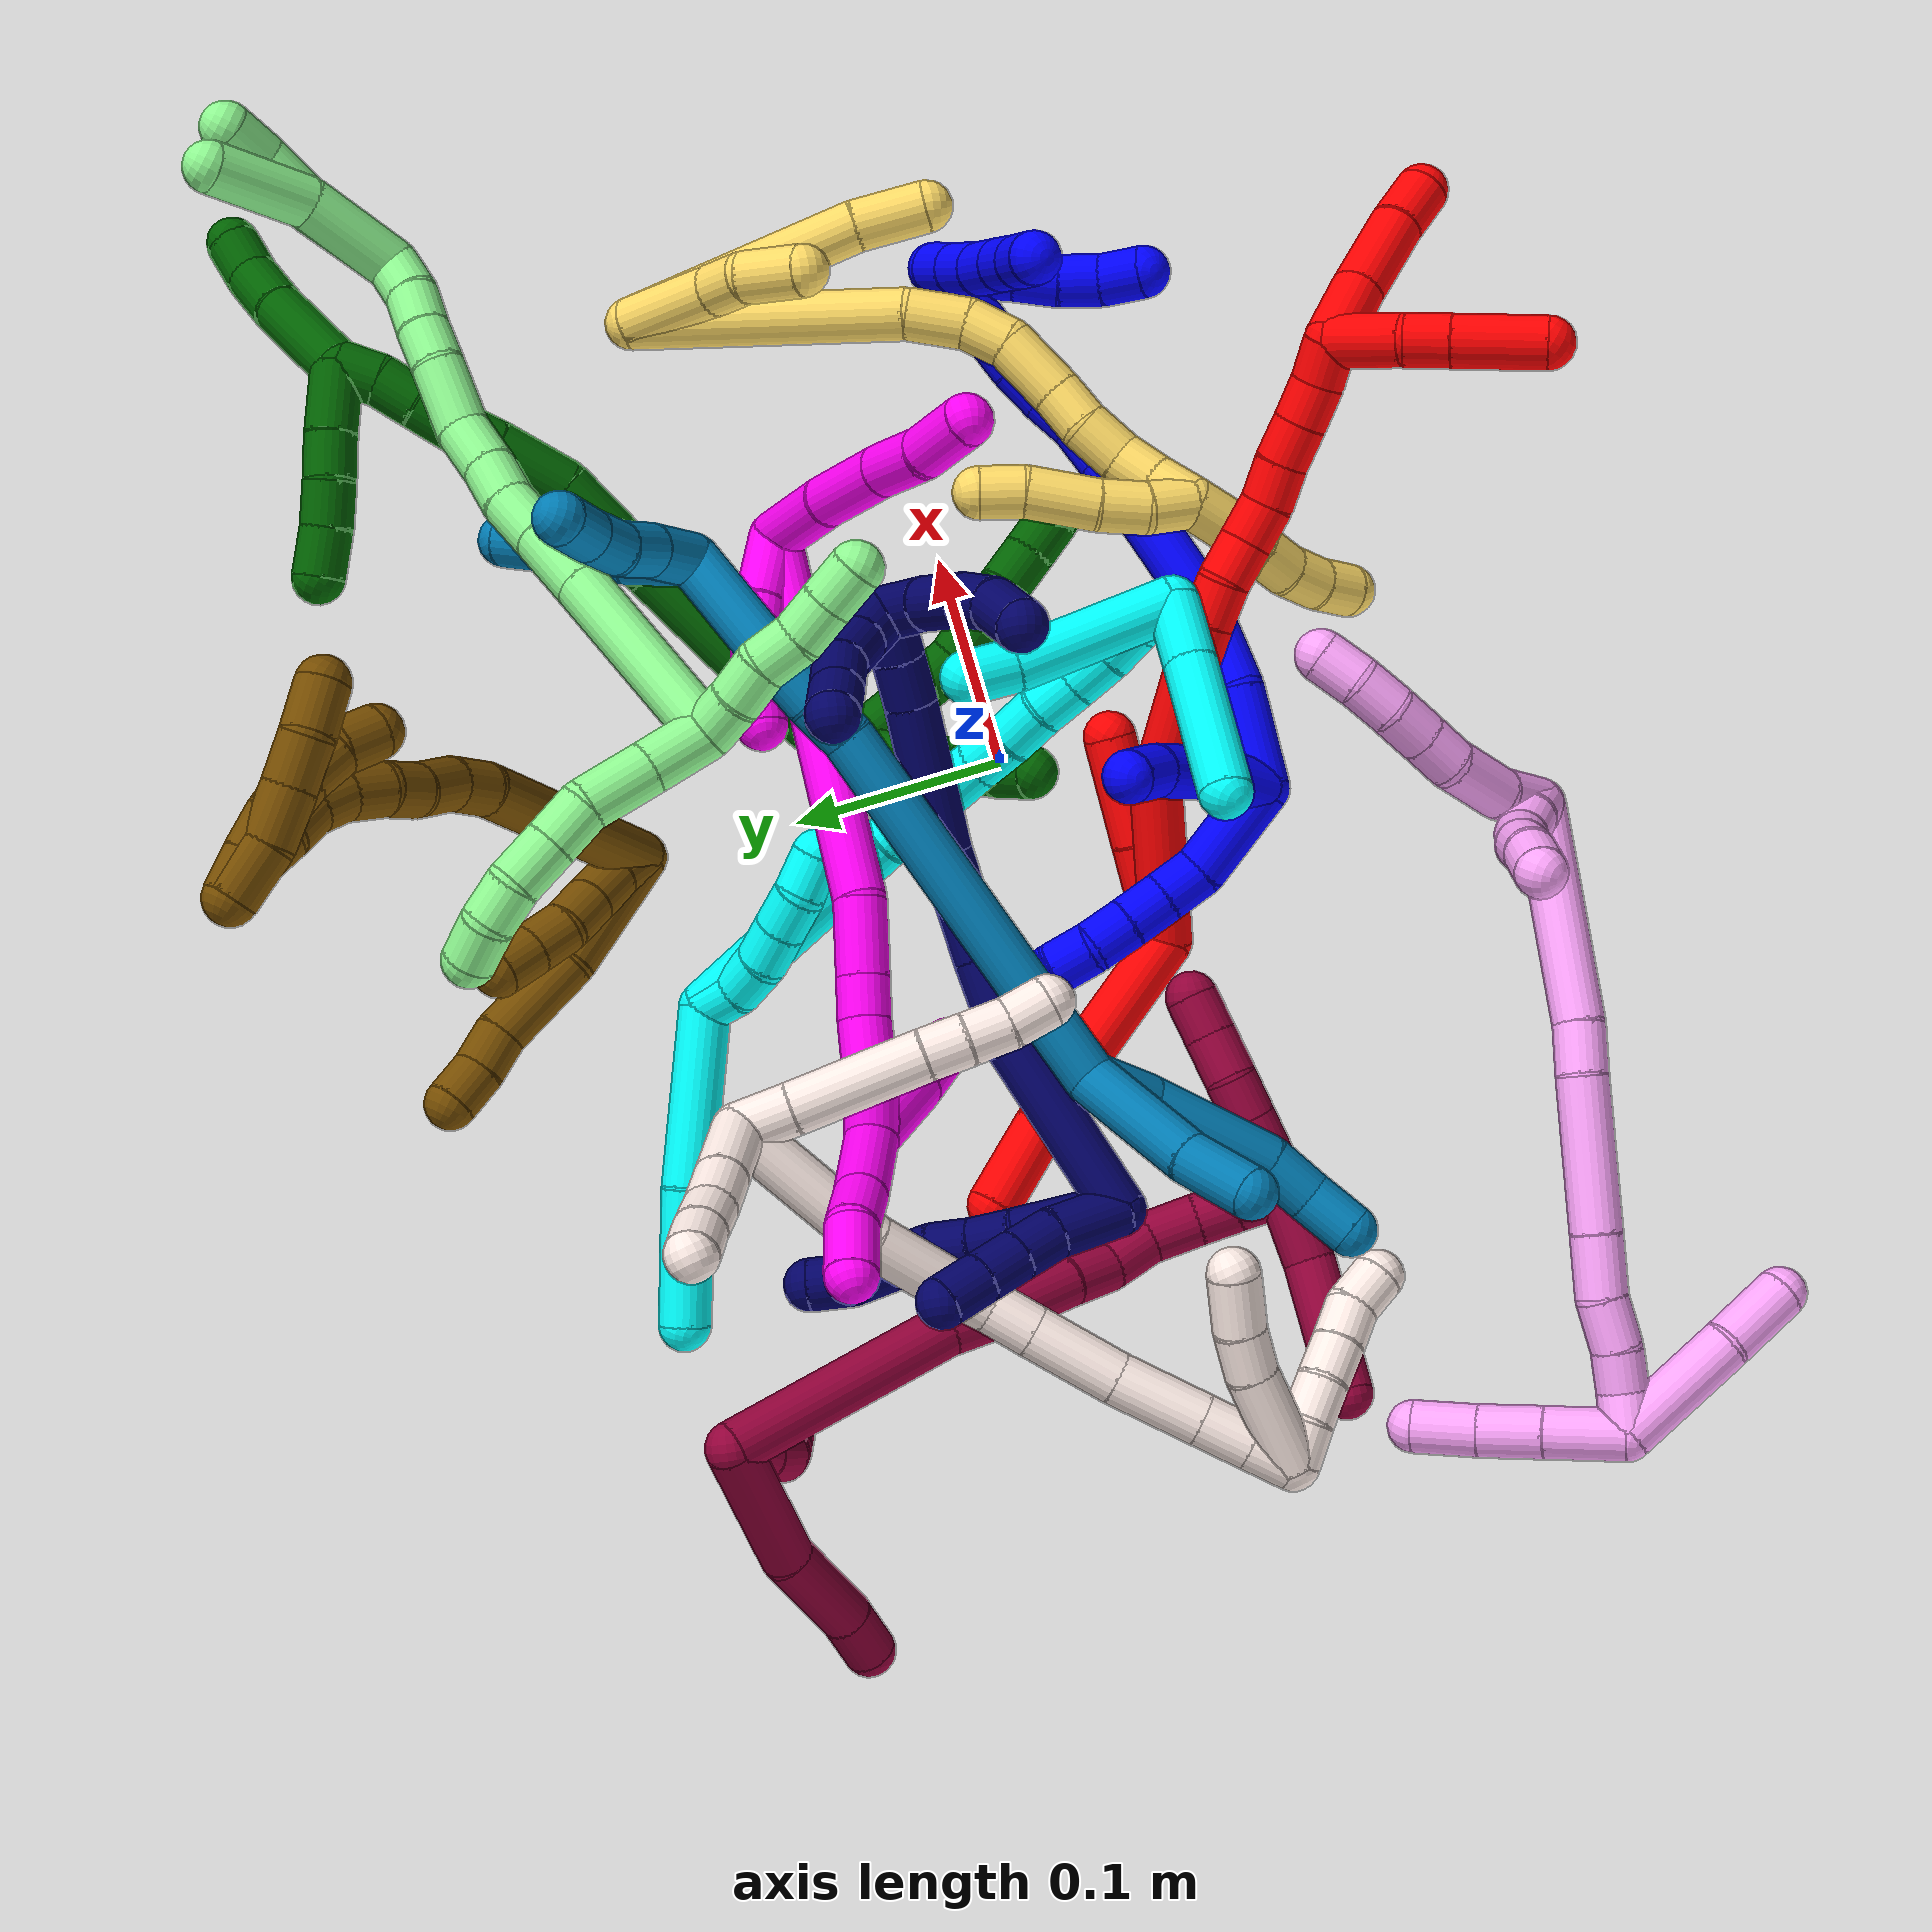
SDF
<sdf version="1.7">
 <world name="default">
  <plugin name="TubeGeneratorPlugin" filename="libtube_generator_plugin.so"/>
  <model name="photoneo_s_sensor">
   <static>1</static>
   <pose>0 0 2 1.57079 1.57079 3.14159</pose>
   <link name="link">
    <inertial><mass>0.1</mass></inertial>
    <sensor name="sensor" type="depth">
     <update_rate>30</update_rate>
     <camera>
      <horizontal_fov>1.22</horizontal_fov>
      <image><width>1920</width><height>1200</height><format>B8G8R8</format></image>
      <clip><near>0.1</near><far>4</far></clip>
      <depth_camera><output>points</output></depth_camera>
     </camera>
     <plugin name="camera_plugin" filename="libgazebo_ros_depth_camera.so">
      <baseline>0.2</baseline>
      <alwaysOn>1</alwaysOn>
      <updateRate>0.0</updateRate>
      <cameraName>camera_ir</cameraName>
      <imageTopicName>/camera/color/image_raw</imageTopicName>
      <cameraInfoTopicName>/camera/color/camera_info</cameraInfoTopicName>
      <depthImageTopicName>/camera/depth/image_raw</depthImageTopicName>
      <depthImageCameraInfoTopicName>/camera/depth/camera_info</depthImageCameraInfoTopicName>
      <pointCloudTopicName>/camera/depth/points</pointCloudTopicName>
      <frameName>fr_optical</frameName>
      <pointCloudCutoff>0.1</pointCloudCutoff>
      <pointCloudCutoffMax>2.0</pointCloudCutoffMax>
      <distortionK1>0</distortionK1>
      <distortionK2>0</distortionK2>
      <distortionK3>0</distortionK3>
      <distortionT1>0</distortionT1>
      <distortionT2>0</distortionT2>
      <CxPrime>0</CxPrime>
      <Cx>0</Cx>
      <Cy>0</Cy>
      <focalLength>0</focalLength>
      <hackBaseline>0</hackBaseline>
     </plugin>
    </sensor>
   </link>
  </model>
  <gravity>0 0 -9.8</gravity>
  <magnetic_field>6e-06 2.3e-05 -4.2e-05</magnetic_field>
  <atmosphere type="adiabatic"/>
  <physics name="default_physics" default="0" type="ode">
   <max_step_size>0.003</max_step_size>
   <real_time_factor>1</real_time_factor>
   <real_time_update_rate>1000</real_time_update_rate>
   <max_contacts>10000</max_contacts>
   <ode>
    <solver>
     <type>quick</type>
     <iters>100</iters>
     <sor>1.3</sor>
     <use_dynamic_moi_rescaling>0</use_dynamic_moi_rescaling>
    </solver>
    <constraints>
     <contact_max_correcting_vel>0</contact_max_correcting_vel>
     <contact_surface_layer>0.001</contact_surface_layer>
     <cfm>0</cfm>
     <erp>0.2</erp>
    </constraints>
   </ode>
  </physics>
  <scene><ambient>0.4 0.4 0.4 1</ambient><background>0.7 0.7 0.7 1</background><shadows>0</shadows></scene>
  <audio><device>default</device></audio>
  <spherical_coordinates>
   <surface_model>EARTH_WGS84</surface_model>
   <latitude_deg>0</latitude_deg>
   <longitude_deg>0</longitude_deg>
   <elevation>0</elevation>
   <heading_deg>0</heading_deg>
  </spherical_coordinates>
  <model name="bin">
   <static>1</static>
   <link name="bottom">
    <collision name="collision-bottom">
     <pose>0 0 -0.01 0 -0 0</pose>
     <geometry><box><size>0.8 0.6 0.02</size></box></geometry>
     <surface>
      <friction><ode><mu>100</mu><mu2>100</mu2></ode></friction>
      <contact><collide_bitmask>65535</collide_bitmask></contact>
     </surface>
    </collision>
   </link>
   <link name="west_wall">
    <collision name="collision-west_wall">
     <pose>-0.41 0 0.1 0 -0 0</pose>
     <geometry><box><size>0.02 0.6 0.2</size></box></geometry>
     <surface>
      <friction><ode><mu>100</mu><mu2>100</mu2></ode></friction>
      <contact><collide_bitmask>65535</collide_bitmask></contact>
     </surface>
    </collision>
   </link>
   <link name="east_wall">
    <collision name="collision-east_wall">
     <pose>0.41 0 0.1 0 -0 0</pose>
     <geometry><box><size>0.02 0.6 0.2</size></box></geometry>
     <surface>
      <friction><ode><mu>100</mu><mu2>100</mu2></ode></friction>
      <contact><collide_bitmask>65535</collide_bitmask></contact>
     </surface>
    </collision>
   </link>
   <link name="south_wall">
    <collision name="collision-south_wall">
     <pose>0 -0.31 0.1 0 -0 0</pose>
     <geometry><box><size>0.8 0.02 0.2</size></box></geometry>
     <surface>
      <friction><ode><mu>100</mu><mu2>100</mu2></ode></friction>
      <contact><collide_bitmask>65535</collide_bitmask></contact>
     </surface>
    </collision>
   </link>
   <link name="north_wall">
    <collision name="collision-north_wall">
     <pose>0 0.31 0.1 0 -0 0</pose>
     <geometry><box><size>0.8 0.02 0.2</size></box></geometry>
     <surface>
      <friction><ode><mu>100</mu><mu2>100</mu2></ode></friction>
      <contact><collide_bitmask>65535</collide_bitmask></contact>
     </surface>
    </collision>
   </link>
  </model>
  <model name="1">
   <static>0</static>
   <link name="1">
    <collision name="collision-cylinder-e_1_2_8">
     <pose>-0.019626 0.012046 -0.006758 -2.08207 -0.957559 1.45047</pose>
     <geometry><cylinder><radius>0.0125</radius><length>0.047998</length></cylinder></geometry>
     <surface>
      <friction><ode><mu>1.16</mu><mu2>1.16</mu2><slip1>0</slip1><slip2>0</slip2></ode></friction>
      <contact><ode><kp>1e+06</kp><kd>1</kd><max_vel>0</max_vel><min_depth>0.001</min_depth></ode></contact>
     </surface>
    </collision>
    <visual name="visual-cylinder-e_1_2_8">
     <pose>-0.019626 0.012046 -0.006758 -2.08207 -0.957559 1.45047</pose>
     <geometry><cylinder><radius>0.0125</radius><length>0.047998</length></cylinder></geometry>
     <material><ambient>0 0 1 1</ambient></material>
    </visual>
    <collision name="collision-cylinder-e_2_8_9">
     <pose>-0.045573 0.032121 -0.016127 -1.88521 -0.642572 0.859313</pose>
     <geometry><cylinder><radius>0.0125</radius><length>0.021095</length></cylinder></geometry>
     <surface>
      <friction><ode><mu>1.16</mu><mu2>1.16</mu2><slip1>0</slip1><slip2>0</slip2></ode></friction>
      <contact><ode><kp>1e+06</kp><kd>1</kd><max_vel>0</max_vel><min_depth>0.001</min_depth></ode></contact>
     </surface>
    </collision>
    <visual name="visual-cylinder-e_2_8_9">
     <pose>-0.045573 0.032121 -0.016127 -1.88521 -0.642572 0.859313</pose>
     <geometry><cylinder><radius>0.0125</radius><length>0.021095</length></cylinder></geometry>
     <material><ambient>0 0 1 1</ambient></material>
    </visual>
    <collision name="collision-cylinder-e_3_9_10">
     <pose>-0.057846 0.048271 -0.020825 -1.82235 -0.61745 0.780329</pose>
     <geometry><cylinder><radius>0.0125</radius><length>0.020564</length></cylinder></geometry>
     <surface>
      <friction><ode><mu>1.16</mu><mu2>1.16</mu2><slip1>0</slip1><slip2>0</slip2></ode></friction>
      <contact><ode><kp>1e+06</kp><kd>1</kd><max_vel>0</max_vel><min_depth>0.001</min_depth></ode></contact>
     </surface>
    </collision>
    <visual name="visual-cylinder-e_3_9_10">
     <pose>-0.057846 0.048271 -0.020825 -1.82235 -0.61745 0.780329</pose>
     <geometry><cylinder><radius>0.0125</radius><length>0.020564</length></cylinder></geometry>
     <material><ambient>0 0 1 1</ambient></material>
    </visual>
    <collision name="collision-cylinder-e_4_10_11">
     <pose>-0.06954 0.064354 -0.025323 -1.86475 -0.603991 0.794898</pose>
     <geometry><cylinder><radius>0.0125</radius><length>0.020218</length></cylinder></geometry>
     <surface>
      <friction><ode><mu>1.16</mu><mu2>1.16</mu2><slip1>0</slip1><slip2>0</slip2></ode></friction>
      <contact><ode><kp>1e+06</kp><kd>1</kd><max_vel>0</max_vel><min_depth>0.001</min_depth></ode></contact>
     </surface>
    </collision>
    <visual name="visual-cylinder-e_4_10_11">
     <pose>-0.06954 0.064354 -0.025323 -1.86475 -0.603991 0.794898</pose>
     <geometry><cylinder><radius>0.0125</radius><length>0.020218</length></cylinder></geometry>
     <material><ambient>0 0 1 1</ambient></material>
    </visual>
    <collision name="collision-cylinder-e_5_11_12">
     <pose>-0.08062 0.079215 -0.032629 -2.18802 -0.562962 1.02068</pose>
     <geometry><cylinder><radius>0.0125</radius><length>0.020005</length></cylinder></geometry>
     <surface>
      <friction><ode><mu>1.16</mu><mu2>1.16</mu2><slip1>0</slip1><slip2>0</slip2></ode></friction>
      <contact><ode><kp>1e+06</kp><kd>1</kd><max_vel>0</max_vel><min_depth>0.001</min_depth></ode></contact>
     </surface>
    </collision>
    <visual name="visual-cylinder-e_5_11_12">
     <pose>-0.08062 0.079215 -0.032629 -2.18802 -0.562962 1.02068</pose>
     <geometry><cylinder><radius>0.0125</radius><length>0.020005</length></cylinder></geometry>
     <material><ambient>0 0 1 1</ambient></material>
    </visual>
    <collision name="collision-cylinder-e_6_12_6">
     <pose>-0.092468 0.092179 -0.042218 -2.22928 -0.703804 1.28487</pose>
     <geometry><cylinder><radius>0.0125</radius><length>0.020121</length></cylinder></geometry>
     <surface>
      <friction><ode><mu>1.16</mu><mu2>1.16</mu2><slip1>0</slip1><slip2>0</slip2></ode></friction>
      <contact><ode><kp>1e+06</kp><kd>1</kd><max_vel>0</max_vel><min_depth>0.001</min_depth></ode></contact>
     </surface>
    </collision>
    <visual name="visual-cylinder-e_6_12_6">
     <pose>-0.092468 0.092179 -0.042218 -2.22928 -0.703804 1.28487</pose>
     <geometry><cylinder><radius>0.0125</radius><length>0.020121</length></cylinder></geometry>
     <material><ambient>0 0 1 1</ambient></material>
    </visual>
    <collision name="collision-cylinder-e_1_2_13">
     <pose>0.003785 0.01335 0.001779 -1.43835 0.273948 -0.24022</pose>
     <geometry><cylinder><radius>0.0125</radius><length>0.027979</length></cylinder></geometry>
     <surface>
      <friction><ode><mu>1.16</mu><mu2>1.16</mu2><slip1>0</slip1><slip2>0</slip2></ode></friction>
      <contact><ode><kp>1e+06</kp><kd>1</kd><max_vel>0</max_vel><min_depth>0.001</min_depth></ode></contact>
     </surface>
    </collision>
    <visual name="visual-cylinder-e_1_2_13">
     <pose>0.003785 0.01335 0.001779 -1.43835 0.273948 -0.24022</pose>
     <geometry><cylinder><radius>0.0125</radius><length>0.027979</length></cylinder></geometry>
     <material><ambient>0 0 1 1</ambient></material>
    </visual>
    <collision name="collision-cylinder-e_2_13_14">
     <pose>0.008698 0.036123 0.007957 -1.13397 0.108131 -0.06889</pose>
     <geometry><cylinder><radius>0.0125</radius><length>0.020921</length></cylinder></geometry>
     <surface>
      <friction><ode><mu>1.16</mu><mu2>1.16</mu2><slip1>0</slip1><slip2>0</slip2></ode></friction>
      <contact><ode><kp>1e+06</kp><kd>1</kd><max_vel>0</max_vel><min_depth>0.001</min_depth></ode></contact>
     </surface>
    </collision>
    <visual name="visual-cylinder-e_2_13_14">
     <pose>0.008698 0.036123 0.007957 -1.13397 0.108131 -0.06889</pose>
     <geometry><cylinder><radius>0.0125</radius><length>0.020921</length></cylinder></geometry>
     <material><ambient>0 0 1 1</ambient></material>
    </visual>
    <collision name="collision-cylinder-e_3_14_15">
     <pose>0.011041 0.059199 0.017707 -1.19732 0.082577 -0.056349</pose>
     <geometry><cylinder><radius>0.0125</radius><length>0.029427</length></cylinder></geometry>
     <surface>
      <friction><ode><mu>1.16</mu><mu2>1.16</mu2><slip1>0</slip1><slip2>0</slip2></ode></friction>
      <contact><ode><kp>1e+06</kp><kd>1</kd><max_vel>0</max_vel><min_depth>0.001</min_depth></ode></contact>
     </surface>
    </collision>
    <visual name="visual-cylinder-e_3_14_15">
     <pose>0.011041 0.059199 0.017707 -1.19732 0.082577 -0.056349</pose>
     <geometry><cylinder><radius>0.0125</radius><length>0.029427</length></cylinder></geometry>
     <material><ambient>0 0 1 1</ambient></material>
    </visual>
    <collision name="collision-cylinder-e_4_15_5">
     <pose>0.011607 0.082567 0.027811 -1.11568 -0.059829 0.037337</pose>
     <geometry><cylinder><radius>0.0125</radius><length>0.021672</length></cylinder></geometry>
     <surface>
      <friction><ode><mu>1.16</mu><mu2>1.16</mu2><slip1>0</slip1><slip2>0</slip2></ode></friction>
      <contact><ode><kp>1e+06</kp><kd>1</kd><max_vel>0</max_vel><min_depth>0.001</min_depth></ode></contact>
     </surface>
    </collision>
    <visual name="visual-cylinder-e_4_15_5">
     <pose>0.011607 0.082567 0.027811 -1.11568 -0.059829 0.037337</pose>
     <geometry><cylinder><radius>0.0125</radius><length>0.021672</length></cylinder></geometry>
     <material><ambient>0 0 1 1</ambient></material>
    </visual>
    <collision name="collision-cylinder-e_1_2_16">
     <pose>0.022118 0.002201 -0.008911 -2.89947 1.17742 -2.78114</pose>
     <geometry><cylinder><radius>0.0125</radius><length>0.047894</length></cylinder></geometry>
     <surface>
      <friction><ode><mu>1.16</mu><mu2>1.16</mu2><slip1>0</slip1><slip2>0</slip2></ode></friction>
      <contact><ode><kp>1e+06</kp><kd>1</kd><max_vel>0</max_vel><min_depth>0.001</min_depth></ode></contact>
     </surface>
    </collision>
    <visual name="visual-cylinder-e_1_2_16">
     <pose>0.022118 0.002201 -0.008911 -2.89947 1.17742 -2.78114</pose>
     <geometry><cylinder><radius>0.0125</radius><length>0.047894</length></cylinder></geometry>
     <material><ambient>0 0 1 1</ambient></material>
    </visual>
    <collision name="collision-cylinder-e_2_16_17">
     <pose>0.064743 0.006997 -0.032365 -2.96496 0.946539 -2.79916</pose>
     <geometry><cylinder><radius>0.0125</radius><length>0.050548</length></cylinder></geometry>
     <surface>
      <friction><ode><mu>1.16</mu><mu2>1.16</mu2><slip1>0</slip1><slip2>0</slip2></ode></friction>
      <contact><ode><kp>1e+06</kp><kd>1</kd><max_vel>0</max_vel><min_depth>0.001</min_depth></ode></contact>
     </surface>
    </collision>
    <visual name="visual-cylinder-e_2_16_17">
     <pose>0.064743 0.006997 -0.032365 -2.96496 0.946539 -2.79916</pose>
     <geometry><cylinder><radius>0.0125</radius><length>0.050548</length></cylinder></geometry>
     <material><ambient>0 0 1 1</ambient></material>
    </visual>
    <collision name="collision-cylinder-e_3_17_18">
     <pose>0.105816 0.019532 -0.060341 -2.5046 0.888444 -1.92988</pose>
     <geometry><cylinder><radius>0.0125</radius><length>0.052998</length></cylinder></geometry>
     <surface>
      <friction><ode><mu>1.16</mu><mu2>1.16</mu2><slip1>0</slip1><slip2>0</slip2></ode></friction>
      <contact><ode><kp>1e+06</kp><kd>1</kd><max_vel>0</max_vel><min_depth>0.001</min_depth></ode></contact>
     </surface>
    </collision>
    <visual name="visual-cylinder-e_3_17_18">
     <pose>0.105816 0.019532 -0.060341 -2.5046 0.888444 -1.92988</pose>
     <geometry><cylinder><radius>0.0125</radius><length>0.052998</length></cylinder></geometry>
     <material><ambient>0 0 1 1</ambient></material>
    </visual>
    <collision name="collision-cylinder-e_4_18_19">
     <pose>0.136218 0.034113 -0.081075 -2.57525 0.849449 -1.99811</pose>
     <geometry><cylinder><radius>0.0125</radius><length>0.026199</length></cylinder></geometry>
     <surface>
      <friction><ode><mu>1.16</mu><mu2>1.16</mu2><slip1>0</slip1><slip2>0</slip2></ode></friction>
      <contact><ode><kp>1e+06</kp><kd>1</kd><max_vel>0</max_vel><min_depth>0.001</min_depth></ode></contact>
     </surface>
    </collision>
    <visual name="visual-cylinder-e_4_18_19">
     <pose>0.136218 0.034113 -0.081075 -2.57525 0.849449 -1.99811</pose>
     <geometry><cylinder><radius>0.0125</radius><length>0.026199</length></cylinder></geometry>
     <material><ambient>0 0 1 1</ambient></material>
    </visual>
    <collision name="collision-cylinder-e_5_19_20">
     <pose>0.154133 0.04291 -0.094585 -2.55191 0.824357 -1.92741</pose>
     <geometry><cylinder><radius>0.0125</radius><length>0.022009</length></cylinder></geometry>
     <surface>
      <friction><ode><mu>1.16</mu><mu2>1.16</mu2><slip1>0</slip1><slip2>0</slip2></ode></friction>
      <contact><ode><kp>1e+06</kp><kd>1</kd><max_vel>0</max_vel><min_depth>0.001</min_depth></ode></contact>
     </surface>
    </collision>
    <visual name="visual-cylinder-e_5_19_20">
     <pose>0.154133 0.04291 -0.094585 -2.55191 0.824357 -1.92741</pose>
     <geometry><cylinder><radius>0.0125</radius><length>0.022009</length></cylinder></geometry>
     <material><ambient>0 0 1 1</ambient></material>
    </visual>
    <collision name="collision-cylinder-e_6_20_21">
     <pose>0.168259 0.052338 -0.106785 -2.41975 0.648548 -1.45513</pose>
     <geometry><cylinder><radius>0.0125</radius><length>0.020024</length></cylinder></geometry>
     <surface>
      <friction><ode><mu>1.16</mu><mu2>1.16</mu2><slip1>0</slip1><slip2>0</slip2></ode></friction>
      <contact><ode><kp>1e+06</kp><kd>1</kd><max_vel>0</max_vel><min_depth>0.001</min_depth></ode></contact>
     </surface>
    </collision>
    <visual name="visual-cylinder-e_6_20_21">
     <pose>0.168259 0.052338 -0.106785 -2.41975 0.648548 -1.45513</pose>
     <geometry><cylinder><radius>0.0125</radius><length>0.020024</length></cylinder></geometry>
     <material><ambient>0 0 1 1</ambient></material>
    </visual>
    <collision name="collision-cylinder-e_7_21_22">
     <pose>0.181335 0.063679 -0.116855 -2.16284 0.765565 -1.29468</pose>
     <geometry><cylinder><radius>0.0125</radius><length>0.020286</length></cylinder></geometry>
     <surface>
      <friction><ode><mu>1.16</mu><mu2>1.16</mu2><slip1>0</slip1><slip2>0</slip2></ode></friction>
      <contact><ode><kp>1e+06</kp><kd>1</kd><max_vel>0</max_vel><min_depth>0.001</min_depth></ode></contact>
     </surface>
    </collision>
    <visual name="visual-cylinder-e_7_21_22">
     <pose>0.181335 0.063679 -0.116855 -2.16284 0.765565 -1.29468</pose>
     <geometry><cylinder><radius>0.0125</radius><length>0.020286</length></cylinder></geometry>
     <material><ambient>0 0 1 1</ambient></material>
    </visual>
    <collision name="collision-cylinder-e_8_22_23">
     <pose>0.196063 0.075225 -0.124236 -2.11296 0.877717 -1.38638</pose>
     <geometry><cylinder><radius>0.0125</radius><length>0.020018</length></cylinder></geometry>
     <surface>
      <friction><ode><mu>1.16</mu><mu2>1.16</mu2><slip1>0</slip1><slip2>0</slip2></ode></friction>
      <contact><ode><kp>1e+06</kp><kd>1</kd><max_vel>0</max_vel><min_depth>0.001</min_depth></ode></contact>
     </surface>
    </collision>
    <visual name="visual-cylinder-e_8_22_23">
     <pose>0.196063 0.075225 -0.124236 -2.11296 0.877717 -1.38638</pose>
     <geometry><cylinder><radius>0.0125</radius><length>0.020018</length></cylinder></geometry>
     <material><ambient>0 0 1 1</ambient></material>
    </visual>
    <collision name="collision-cylinder-e_9_23_24">
     <pose>0.211321 0.08704 -0.129201 -1.82777 0.856551 -1.06904</pose>
     <geometry><cylinder><radius>0.0125</radius><length>0.020006</length></cylinder></geometry>
     <surface>
      <friction><ode><mu>1.16</mu><mu2>1.16</mu2><slip1>0</slip1><slip2>0</slip2></ode></friction>
      <contact><ode><kp>1e+06</kp><kd>1</kd><max_vel>0</max_vel><min_depth>0.001</min_depth></ode></contact>
     </surface>
    </collision>
    <visual name="visual-cylinder-e_9_23_24">
     <pose>0.211321 0.08704 -0.129201 -1.82777 0.856551 -1.06904</pose>
     <geometry><cylinder><radius>0.0125</radius><length>0.020006</length></cylinder></geometry>
     <material><ambient>0 0 1 1</ambient></material>
    </visual>
    <collision name="collision-cylinder-e_10_24_1">
     <pose>0.225914 0.099118 -0.135079 -2.20375 0.779327 -1.36236</pose>
     <geometry><cylinder><radius>0.0125</radius><length>0.020019</length></cylinder></geometry>
     <surface>
      <friction><ode><mu>1.16</mu><mu2>1.16</mu2><slip1>0</slip1><slip2>0</slip2></ode></friction>
      <contact><ode><kp>1e+06</kp><kd>1</kd><max_vel>0</max_vel><min_depth>0.001</min_depth></ode></contact>
     </surface>
    </collision>
    <visual name="visual-cylinder-e_10_24_1">
     <pose>0.225914 0.099118 -0.135079 -2.20375 0.779327 -1.36236</pose>
     <geometry><cylinder><radius>0.0125</radius><length>0.020019</length></cylinder></geometry>
     <material><ambient>0 0 1 1</ambient></material>
    </visual>
    <collision name="collision-cylinder-e_1_1_25">
     <pose>0.232063 0.088782 -0.1293 1.0148 -0.046752 -0.025995</pose>
     <geometry><cylinder><radius>0.0125</radius><length>0.037899</length></cylinder></geometry>
     <surface>
      <friction><ode><mu>1.16</mu><mu2>1.16</mu2><slip1>0</slip1><slip2>0</slip2></ode></friction>
      <contact><ode><kp>1e+06</kp><kd>1</kd><max_vel>0</max_vel><min_depth>0.001</min_depth></ode></contact>
     </surface>
    </collision>
    <visual name="visual-cylinder-e_1_1_25">
     <pose>0.232063 0.088782 -0.1293 1.0148 -0.046752 -0.025995</pose>
     <geometry><cylinder><radius>0.0125</radius><length>0.037899</length></cylinder></geometry>
     <material><ambient>0 0 1 1</ambient></material>
    </visual>
    <collision name="collision-cylinder-e_2_25_26">
     <pose>0.23016 0.063936 -0.113168 0.959771 -0.094725 -0.049328</pose>
     <geometry><cylinder><radius>0.0125</radius><length>0.021508</length></cylinder></geometry>
     <surface>
      <friction><ode><mu>1.16</mu><mu2>1.16</mu2><slip1>0</slip1><slip2>0</slip2></ode></friction>
      <contact><ode><kp>1e+06</kp><kd>1</kd><max_vel>0</max_vel><min_depth>0.001</min_depth></ode></contact>
     </surface>
    </collision>
    <visual name="visual-cylinder-e_2_25_26">
     <pose>0.23016 0.063936 -0.113168 0.959771 -0.094725 -0.049328</pose>
     <geometry><cylinder><radius>0.0125</radius><length>0.021508</length></cylinder></geometry>
     <material><ambient>0 0 1 1</ambient></material>
    </visual>
    <collision name="collision-cylinder-e_3_26_27">
     <pose>0.229624 0.047153 -0.101038 0.929133 0.048044 0.02408</pose>
     <geometry><cylinder><radius>0.0125</radius><length>0.020031</length></cylinder></geometry>
     <surface>
      <friction><ode><mu>1.16</mu><mu2>1.16</mu2><slip1>0</slip1><slip2>0</slip2></ode></friction>
      <contact><ode><kp>1e+06</kp><kd>1</kd><max_vel>0</max_vel><min_depth>0.001</min_depth></ode></contact>
     </surface>
    </collision>
    <visual name="visual-cylinder-e_3_26_27">
     <pose>0.229624 0.047153 -0.101038 0.929133 0.048044 0.02408</pose>
     <geometry><cylinder><radius>0.0125</radius><length>0.020031</length></cylinder></geometry>
     <material><ambient>0 0 1 1</ambient></material>
    </visual>
    <collision name="collision-cylinder-e_4_27_4">
     <pose>0.232363 0.032309 -0.087705 0.748964 0.221459 0.087342</pose>
     <geometry><cylinder><radius>0.0125</radius><length>0.020562</length></cylinder></geometry>
     <surface>
      <friction><ode><mu>1.16</mu><mu2>1.16</mu2><slip1>0</slip1><slip2>0</slip2></ode></friction>
      <contact><ode><kp>1e+06</kp><kd>1</kd><max_vel>0</max_vel><min_depth>0.001</min_depth></ode></contact>
     </surface>
    </collision>
    <visual name="visual-cylinder-e_4_27_4">
     <pose>0.232363 0.032309 -0.087705 0.748964 0.221459 0.087342</pose>
     <geometry><cylinder><radius>0.0125</radius><length>0.020562</length></cylinder></geometry>
     <material><ambient>0 0 1 1</ambient></material>
    </visual>
    <collision name="collision-cylinder-e_1_1_28">
     <pose>0.232994 0.104412 -0.129301 0.044716 0.004532 0.000101</pose>
     <geometry><cylinder><radius>0.0125</radius><length>0.02</length></cylinder></geometry>
     <surface>
      <friction><ode><mu>1.16</mu><mu2>1.16</mu2><slip1>0</slip1><slip2>0</slip2></ode></friction>
      <contact><ode><kp>1e+06</kp><kd>1</kd><max_vel>0</max_vel><min_depth>0.001</min_depth></ode></contact>
     </surface>
    </collision>
    <visual name="visual-cylinder-e_1_1_28">
     <pose>0.232994 0.104412 -0.129301 0.044716 0.004532 0.000101</pose>
     <geometry><cylinder><radius>0.0125</radius><length>0.02</length></cylinder></geometry>
     <material><ambient>0 0 1 1</ambient></material>
    </visual>
    <collision name="collision-cylinder-e_2_28_29">
     <pose>0.233223 0.103511 -0.109323 0.045418 0.018371 0.000417</pose>
     <geometry><cylinder><radius>0.0125</radius><length>0.02</length></cylinder></geometry>
     <surface>
      <friction><ode><mu>1.16</mu><mu2>1.16</mu2><slip1>0</slip1><slip2>0</slip2></ode></friction>
      <contact><ode><kp>1e+06</kp><kd>1</kd><max_vel>0</max_vel><min_depth>0.001</min_depth></ode></contact>
     </surface>
    </collision>
    <visual name="visual-cylinder-e_2_28_29">
     <pose>0.233223 0.103511 -0.109323 0.045418 0.018371 0.000417</pose>
     <geometry><cylinder><radius>0.0125</radius><length>0.02</length></cylinder></geometry>
     <material><ambient>0 0 1 1</ambient></material>
    </visual>
    <collision name="collision-cylinder-e_3_29_30">
     <pose>0.234532 0.102998 -0.089398 0.006012 0.112826 0.00034</pose>
     <geometry><cylinder><radius>0.0125</radius><length>0.02</length></cylinder></geometry>
     <surface>
      <friction><ode><mu>1.16</mu><mu2>1.16</mu2><slip1>0</slip1><slip2>0</slip2></ode></friction>
      <contact><ode><kp>1e+06</kp><kd>1</kd><max_vel>0</max_vel><min_depth>0.001</min_depth></ode></contact>
     </surface>
    </collision>
    <visual name="visual-cylinder-e_3_29_30">
     <pose>0.234532 0.102998 -0.089398 0.006012 0.112826 0.00034</pose>
     <geometry><cylinder><radius>0.0125</radius><length>0.02</length></cylinder></geometry>
     <material><ambient>0 0 1 1</ambient></material>
    </visual>
    <collision name="collision-cylinder-e_4_30_31">
     <pose>0.236442 0.1038 -0.06953 -0.086608 0.078446 -0.003401</pose>
     <geometry><cylinder><radius>0.0125</radius><length>0.02</length></cylinder></geometry>
     <surface>
      <friction><ode><mu>1.16</mu><mu2>1.16</mu2><slip1>0</slip1><slip2>0</slip2></ode></friction>
      <contact><ode><kp>1e+06</kp><kd>1</kd><max_vel>0</max_vel><min_depth>0.001</min_depth></ode></contact>
     </surface>
    </collision>
    <visual name="visual-cylinder-e_4_30_31">
     <pose>0.236442 0.1038 -0.06953 -0.086608 0.078446 -0.003401</pose>
     <geometry><cylinder><radius>0.0125</radius><length>0.02</length></cylinder></geometry>
     <material><ambient>0 0 1 1</ambient></material>
    </visual>
    <collision name="collision-cylinder-e_5_31_3">
     <pose>0.238129 0.106392 -0.049791 -0.174582 0.090479 -0.007923</pose>
     <geometry><cylinder><radius>0.0125</radius><length>0.02</length></cylinder></geometry>
     <surface>
      <friction><ode><mu>1.16</mu><mu2>1.16</mu2><slip1>0</slip1><slip2>0</slip2></ode></friction>
      <contact><ode><kp>1e+06</kp><kd>1</kd><max_vel>0</max_vel><min_depth>0.001</min_depth></ode></contact>
     </surface>
    </collision>
    <visual name="visual-cylinder-e_5_31_3">
     <pose>0.238129 0.106392 -0.049791 -0.174582 0.090479 -0.007923</pose>
     <geometry><cylinder><radius>0.0125</radius><length>0.02</length></cylinder></geometry>
     <material><ambient>0 0 1 1</ambient></material>
    </visual>
    <collision name="collision-sphere-3">
     <pose>0.239033 0.108122 -0.039983 0 -0 0</pose>
     <geometry><sphere><radius>0.0125</radius></sphere></geometry>
     <surface>
      <friction><ode><mu>1.16</mu><mu2>1.16</mu2><slip1>0</slip1><slip2>0</slip2></ode></friction>
      <contact><ode><kp>1e+06</kp><kd>1</kd><max_vel>0</max_vel><min_depth>0.001</min_depth></ode></contact>
     </surface>
    </collision>
    <visual name="visual-sphere-3">
     <pose>0.239033 0.108122 -0.039983 0 -0 0</pose>
     <geometry><sphere><radius>0.0125</radius></sphere></geometry>
     <material><ambient>0 0 1 1</ambient></material>
    </visual>
    <collision name="collision-sphere-31">
     <pose>0.237226 0.104663 -0.059598 0 -0 0</pose>
     <geometry><sphere><radius>0.0125</radius></sphere></geometry>
     <surface>
      <friction><ode><mu>1.16</mu><mu2>1.16</mu2><slip1>0</slip1><slip2>0</slip2></ode></friction>
      <contact><ode><kp>1e+06</kp><kd>1</kd><max_vel>0</max_vel><min_depth>0.001</min_depth></ode></contact>
     </surface>
    </collision>
    <visual name="visual-sphere-31">
     <pose>0.237226 0.104663 -0.059598 0 -0 0</pose>
     <geometry><sphere><radius>0.0125</radius></sphere></geometry>
     <material><ambient>0 0 1 1</ambient></material>
    </visual>
    <collision name="collision-sphere-30">
     <pose>0.235658 0.102938 -0.079462 0 -0 0</pose>
     <geometry><sphere><radius>0.0125</radius></sphere></geometry>
     <surface>
      <friction><ode><mu>1.16</mu><mu2>1.16</mu2><slip1>0</slip1><slip2>0</slip2></ode></friction>
      <contact><ode><kp>1e+06</kp><kd>1</kd><max_vel>0</max_vel><min_depth>0.001</min_depth></ode></contact>
     </surface>
    </collision>
    <visual name="visual-sphere-30">
     <pose>0.235658 0.102938 -0.079462 0 -0 0</pose>
     <geometry><sphere><radius>0.0125</radius></sphere></geometry>
     <material><ambient>0 0 1 1</ambient></material>
    </visual>
    <collision name="collision-sphere-29">
     <pose>0.233407 0.103057 -0.099335 0 -0 0</pose>
     <geometry><sphere><radius>0.0125</radius></sphere></geometry>
     <surface>
      <friction><ode><mu>1.16</mu><mu2>1.16</mu2><slip1>0</slip1><slip2>0</slip2></ode></friction>
      <contact><ode><kp>1e+06</kp><kd>1</kd><max_vel>0</max_vel><min_depth>0.001</min_depth></ode></contact>
     </surface>
    </collision>
    <visual name="visual-sphere-29">
     <pose>0.233407 0.103057 -0.099335 0 -0 0</pose>
     <geometry><sphere><radius>0.0125</radius></sphere></geometry>
     <material><ambient>0 0 1 1</ambient></material>
    </visual>
    <collision name="collision-sphere-28">
     <pose>0.233039 0.103965 -0.119311 0 -0 0</pose>
     <geometry><sphere><radius>0.0125</radius></sphere></geometry>
     <surface>
      <friction><ode><mu>1.16</mu><mu2>1.16</mu2><slip1>0</slip1><slip2>0</slip2></ode></friction>
      <contact><ode><kp>1e+06</kp><kd>1</kd><max_vel>0</max_vel><min_depth>0.001</min_depth></ode></contact>
     </surface>
    </collision>
    <visual name="visual-sphere-28">
     <pose>0.233039 0.103965 -0.119311 0 -0 0</pose>
     <geometry><sphere><radius>0.0125</radius></sphere></geometry>
     <material><ambient>0 0 1 1</ambient></material>
    </visual>
    <collision name="collision-sphere-4">
     <pose>0.234622 0.02548 -0.080359 0 -0 0</pose>
     <geometry><sphere><radius>0.0125</radius></sphere></geometry>
     <surface>
      <friction><ode><mu>1.16</mu><mu2>1.16</mu2><slip1>0</slip1><slip2>0</slip2></ode></friction>
      <contact><ode><kp>1e+06</kp><kd>1</kd><max_vel>0</max_vel><min_depth>0.001</min_depth></ode></contact>
     </surface>
    </collision>
    <visual name="visual-sphere-4">
     <pose>0.234622 0.02548 -0.080359 0 -0 0</pose>
     <geometry><sphere><radius>0.0125</radius></sphere></geometry>
     <material><ambient>0 0 1 1</ambient></material>
    </visual>
    <collision name="collision-sphere-27">
     <pose>0.230105 0.039139 -0.095051 0 -0 0</pose>
     <geometry><sphere><radius>0.0125</radius></sphere></geometry>
     <surface>
      <friction><ode><mu>1.16</mu><mu2>1.16</mu2><slip1>0</slip1><slip2>0</slip2></ode></friction>
      <contact><ode><kp>1e+06</kp><kd>1</kd><max_vel>0</max_vel><min_depth>0.001</min_depth></ode></contact>
     </surface>
    </collision>
    <visual name="visual-sphere-27">
     <pose>0.230105 0.039139 -0.095051 0 -0 0</pose>
     <geometry><sphere><radius>0.0125</radius></sphere></geometry>
     <material><ambient>0 0 1 1</ambient></material>
    </visual>
    <collision name="collision-sphere-26">
     <pose>0.229143 0.055167 -0.107026 0 -0 0</pose>
     <geometry><sphere><radius>0.0125</radius></sphere></geometry>
     <surface>
      <friction><ode><mu>1.16</mu><mu2>1.16</mu2><slip1>0</slip1><slip2>0</slip2></ode></friction>
      <contact><ode><kp>1e+06</kp><kd>1</kd><max_vel>0</max_vel><min_depth>0.001</min_depth></ode></contact>
     </surface>
    </collision>
    <visual name="visual-sphere-26">
     <pose>0.229143 0.055167 -0.107026 0 -0 0</pose>
     <geometry><sphere><radius>0.0125</radius></sphere></geometry>
     <material><ambient>0 0 1 1</ambient></material>
    </visual>
    <collision name="collision-sphere-25">
     <pose>0.231177 0.072704 -0.11931 0 -0 0</pose>
     <geometry><sphere><radius>0.0125</radius></sphere></geometry>
     <surface>
      <friction><ode><mu>1.16</mu><mu2>1.16</mu2><slip1>0</slip1><slip2>0</slip2></ode></friction>
      <contact><ode><kp>1e+06</kp><kd>1</kd><max_vel>0</max_vel><min_depth>0.001</min_depth></ode></contact>
     </surface>
    </collision>
    <visual name="visual-sphere-25">
     <pose>0.231177 0.072704 -0.11931 0 -0 0</pose>
     <geometry><sphere><radius>0.0125</radius></sphere></geometry>
     <material><ambient>0 0 1 1</ambient></material>
    </visual>
    <collision name="collision-sphere-1">
     <pose>0.232949 0.104859 -0.139291 0 -0 0</pose>
     <geometry><sphere><radius>0.0125</radius></sphere></geometry>
     <surface>
      <friction><ode><mu>1.16</mu><mu2>1.16</mu2><slip1>0</slip1><slip2>0</slip2></ode></friction>
      <contact><ode><kp>1e+06</kp><kd>1</kd><max_vel>0</max_vel><min_depth>0.001</min_depth></ode></contact>
     </surface>
    </collision>
    <visual name="visual-sphere-1">
     <pose>0.232949 0.104859 -0.139291 0 -0 0</pose>
     <geometry><sphere><radius>0.0125</radius></sphere></geometry>
     <material><ambient>0 0 1 1</ambient></material>
    </visual>
    <collision name="collision-sphere-24">
     <pose>0.218879 0.093377 -0.130867 0 -0 0</pose>
     <geometry><sphere><radius>0.0125</radius></sphere></geometry>
     <surface>
      <friction><ode><mu>1.16</mu><mu2>1.16</mu2><slip1>0</slip1><slip2>0</slip2></ode></friction>
      <contact><ode><kp>1e+06</kp><kd>1</kd><max_vel>0</max_vel><min_depth>0.001</min_depth></ode></contact>
     </surface>
    </collision>
    <visual name="visual-sphere-24">
     <pose>0.218879 0.093377 -0.130867 0 -0 0</pose>
     <geometry><sphere><radius>0.0125</radius></sphere></geometry>
     <material><ambient>0 0 1 1</ambient></material>
    </visual>
    <collision name="collision-sphere-23">
     <pose>0.203763 0.080703 -0.127536 0 -0 0</pose>
     <geometry><sphere><radius>0.0125</radius></sphere></geometry>
     <surface>
      <friction><ode><mu>1.16</mu><mu2>1.16</mu2><slip1>0</slip1><slip2>0</slip2></ode></friction>
      <contact><ode><kp>1e+06</kp><kd>1</kd><max_vel>0</max_vel><min_depth>0.001</min_depth></ode></contact>
     </surface>
    </collision>
    <visual name="visual-sphere-23">
     <pose>0.203763 0.080703 -0.127536 0 -0 0</pose>
     <geometry><sphere><radius>0.0125</radius></sphere></geometry>
     <material><ambient>0 0 1 1</ambient></material>
    </visual>
    <collision name="collision-sphere-22">
     <pose>0.188364 0.069747 -0.120936 0 -0 0</pose>
     <geometry><sphere><radius>0.0125</radius></sphere></geometry>
     <surface>
      <friction><ode><mu>1.16</mu><mu2>1.16</mu2><slip1>0</slip1><slip2>0</slip2></ode></friction>
      <contact><ode><kp>1e+06</kp><kd>1</kd><max_vel>0</max_vel><min_depth>0.001</min_depth></ode></contact>
     </surface>
    </collision>
    <visual name="visual-sphere-22">
     <pose>0.188364 0.069747 -0.120936 0 -0 0</pose>
     <geometry><sphere><radius>0.0125</radius></sphere></geometry>
     <material><ambient>0 0 1 1</ambient></material>
    </visual>
    <collision name="collision-sphere-21">
     <pose>0.174306 0.05761 -0.112774 0 -0 0</pose>
     <geometry><sphere><radius>0.0125</radius></sphere></geometry>
     <surface>
      <friction><ode><mu>1.16</mu><mu2>1.16</mu2><slip1>0</slip1><slip2>0</slip2></ode></friction>
      <contact><ode><kp>1e+06</kp><kd>1</kd><max_vel>0</max_vel><min_depth>0.001</min_depth></ode></contact>
     </surface>
    </collision>
    <visual name="visual-sphere-21">
     <pose>0.174306 0.05761 -0.112774 0 -0 0</pose>
     <geometry><sphere><radius>0.0125</radius></sphere></geometry>
     <material><ambient>0 0 1 1</ambient></material>
    </visual>
    <collision name="collision-sphere-12">
     <pose>-0.085958 0.086113 -0.037525 0 -0 0</pose>
     <geometry><sphere><radius>0.0125</radius></sphere></geometry>
     <surface>
      <friction><ode><mu>1.16</mu><mu2>1.16</mu2><slip1>0</slip1><slip2>0</slip2></ode></friction>
      <contact><ode><kp>1e+06</kp><kd>1</kd><max_vel>0</max_vel><min_depth>0.001</min_depth></ode></contact>
     </surface>
    </collision>
    <visual name="visual-sphere-12">
     <pose>-0.085958 0.086113 -0.037525 0 -0 0</pose>
     <geometry><sphere><radius>0.0125</radius></sphere></geometry>
     <material><ambient>0 0 1 1</ambient></material>
    </visual>
    <collision name="collision-sphere-11">
     <pose>-0.075281 0.072317 -0.027733 0 -0 0</pose>
     <geometry><sphere><radius>0.0125</radius></sphere></geometry>
     <surface>
      <friction><ode><mu>1.16</mu><mu2>1.16</mu2><slip1>0</slip1><slip2>0</slip2></ode></friction>
      <contact><ode><kp>1e+06</kp><kd>1</kd><max_vel>0</max_vel><min_depth>0.001</min_depth></ode></contact>
     </surface>
    </collision>
    <visual name="visual-sphere-11">
     <pose>-0.075281 0.072317 -0.027733 0 -0 0</pose>
     <geometry><sphere><radius>0.0125</radius></sphere></geometry>
     <material><ambient>0 0 1 1</ambient></material>
    </visual>
    <collision name="collision-sphere-10">
     <pose>-0.063799 0.05639 -0.022912 0 -0 0</pose>
     <geometry><sphere><radius>0.0125</radius></sphere></geometry>
     <surface>
      <friction><ode><mu>1.16</mu><mu2>1.16</mu2><slip1>0</slip1><slip2>0</slip2></ode></friction>
      <contact><ode><kp>1e+06</kp><kd>1</kd><max_vel>0</max_vel><min_depth>0.001</min_depth></ode></contact>
     </surface>
    </collision>
    <visual name="visual-sphere-10">
     <pose>-0.063799 0.05639 -0.022912 0 -0 0</pose>
     <geometry><sphere><radius>0.0125</radius></sphere></geometry>
     <material><ambient>0 0 1 1</ambient></material>
    </visual>
    <collision name="collision-sphere-9">
     <pose>-0.051894 0.040151 -0.018738 0 -0 0</pose>
     <geometry><sphere><radius>0.0125</radius></sphere></geometry>
     <surface>
      <friction><ode><mu>1.16</mu><mu2>1.16</mu2><slip1>0</slip1><slip2>0</slip2></ode></friction>
      <contact><ode><kp>1e+06</kp><kd>1</kd><max_vel>0</max_vel><min_depth>0.001</min_depth></ode></contact>
     </surface>
    </collision>
    <visual name="visual-sphere-9">
     <pose>-0.051894 0.040151 -0.018738 0 -0 0</pose>
     <geometry><sphere><radius>0.0125</radius></sphere></geometry>
     <material><ambient>0 0 1 1</ambient></material>
    </visual>
    <collision name="collision-sphere-2">
     <geometry><sphere><radius>0.0125</radius></sphere></geometry>
     <surface>
      <friction><ode><mu>1.16</mu><mu2>1.16</mu2><slip1>0</slip1><slip2>0</slip2></ode></friction>
      <contact><ode><kp>1e+06</kp><kd>1</kd><max_vel>0</max_vel><min_depth>0.001</min_depth></ode></contact>
     </surface>
    </collision>
    <visual name="visual-sphere-2">
     <geometry><sphere><radius>0.0125</radius></sphere></geometry>
     <material><ambient>0 0 1 1</ambient></material>
    </visual>
    <collision name="collision-sphere-19">
     <pose>0.146054 0.038754 -0.088375 0 -0 0</pose>
     <geometry><sphere><radius>0.0125</radius></sphere></geometry>
     <surface>
      <friction><ode><mu>1.16</mu><mu2>1.16</mu2><slip1>0</slip1><slip2>0</slip2></ode></friction>
      <contact><ode><kp>1e+06</kp><kd>1</kd><max_vel>0</max_vel><min_depth>0.001</min_depth></ode></contact>
     </surface>
    </collision>
    <visual name="visual-sphere-19">
     <pose>0.146054 0.038754 -0.088375 0 -0 0</pose>
     <geometry><sphere><radius>0.0125</radius></sphere></geometry>
     <material><ambient>0 0 1 1</ambient></material>
    </visual>
    <collision name="collision-sphere-8">
     <pose>-0.039253 0.024091 -0.013516 0 -0 0</pose>
     <geometry><sphere><radius>0.0125</radius></sphere></geometry>
     <surface>
      <friction><ode><mu>1.16</mu><mu2>1.16</mu2><slip1>0</slip1><slip2>0</slip2></ode></friction>
      <contact><ode><kp>1e+06</kp><kd>1</kd><max_vel>0</max_vel><min_depth>0.001</min_depth></ode></contact>
     </surface>
    </collision>
    <visual name="visual-sphere-8">
     <pose>-0.039253 0.024091 -0.013516 0 -0 0</pose>
     <geometry><sphere><radius>0.0125</radius></sphere></geometry>
     <material><ambient>0 0 1 1</ambient></material>
    </visual>
    <collision name="collision-sphere-6">
     <pose>-0.098978 0.098246 -0.046911 0 -0 0</pose>
     <geometry><sphere><radius>0.0125</radius></sphere></geometry>
     <surface>
      <friction><ode><mu>1.16</mu><mu2>1.16</mu2><slip1>0</slip1><slip2>0</slip2></ode></friction>
      <contact><ode><kp>1e+06</kp><kd>1</kd><max_vel>0</max_vel><min_depth>0.001</min_depth></ode></contact>
     </surface>
    </collision>
    <visual name="visual-sphere-6">
     <pose>-0.098978 0.098246 -0.046911 0 -0 0</pose>
     <geometry><sphere><radius>0.0125</radius></sphere></geometry>
     <material><ambient>0 0 1 1</ambient></material>
    </visual>
    <collision name="collision-sphere-13">
     <pose>0.007569 0.0267 0.003557 0 -0 0</pose>
     <geometry><sphere><radius>0.0125</radius></sphere></geometry>
     <surface>
      <friction><ode><mu>1.16</mu><mu2>1.16</mu2><slip1>0</slip1><slip2>0</slip2></ode></friction>
      <contact><ode><kp>1e+06</kp><kd>1</kd><max_vel>0</max_vel><min_depth>0.001</min_depth></ode></contact>
     </surface>
    </collision>
    <visual name="visual-sphere-13">
     <pose>0.007569 0.0267 0.003557 0 -0 0</pose>
     <geometry><sphere><radius>0.0125</radius></sphere></geometry>
     <material><ambient>0 0 1 1</ambient></material>
    </visual>
    <collision name="collision-sphere-14">
     <pose>0.009827 0.045546 0.012357 0 -0 0</pose>
     <geometry><sphere><radius>0.0125</radius></sphere></geometry>
     <surface>
      <friction><ode><mu>1.16</mu><mu2>1.16</mu2><slip1>0</slip1><slip2>0</slip2></ode></friction>
      <contact><ode><kp>1e+06</kp><kd>1</kd><max_vel>0</max_vel><min_depth>0.001</min_depth></ode></contact>
     </surface>
    </collision>
    <visual name="visual-sphere-14">
     <pose>0.009827 0.045546 0.012357 0 -0 0</pose>
     <geometry><sphere><radius>0.0125</radius></sphere></geometry>
     <material><ambient>0 0 1 1</ambient></material>
    </visual>
    <collision name="collision-sphere-15">
     <pose>0.012254 0.072852 0.023057 0 -0 0</pose>
     <geometry><sphere><radius>0.0125</radius></sphere></geometry>
     <surface>
      <friction><ode><mu>1.16</mu><mu2>1.16</mu2><slip1>0</slip1><slip2>0</slip2></ode></friction>
      <contact><ode><kp>1e+06</kp><kd>1</kd><max_vel>0</max_vel><min_depth>0.001</min_depth></ode></contact>
     </surface>
    </collision>
    <visual name="visual-sphere-15">
     <pose>0.012254 0.072852 0.023057 0 -0 0</pose>
     <geometry><sphere><radius>0.0125</radius></sphere></geometry>
     <material><ambient>0 0 1 1</ambient></material>
    </visual>
    <collision name="collision-sphere-5">
     <pose>0.010959 0.092283 0.032566 0 -0 0</pose>
     <geometry><sphere><radius>0.0125</radius></sphere></geometry>
     <surface>
      <friction><ode><mu>1.16</mu><mu2>1.16</mu2><slip1>0</slip1><slip2>0</slip2></ode></friction>
      <contact><ode><kp>1e+06</kp><kd>1</kd><max_vel>0</max_vel><min_depth>0.001</min_depth></ode></contact>
     </surface>
    </collision>
    <visual name="visual-sphere-5">
     <pose>0.010959 0.092283 0.032566 0 -0 0</pose>
     <geometry><sphere><radius>0.0125</radius></sphere></geometry>
     <material><ambient>0 0 1 1</ambient></material>
    </visual>
    <collision name="collision-sphere-16">
     <pose>0.044236 0.004402 -0.017823 0 -0 0</pose>
     <geometry><sphere><radius>0.0125</radius></sphere></geometry>
     <surface>
      <friction><ode><mu>1.16</mu><mu2>1.16</mu2><slip1>0</slip1><slip2>0</slip2></ode></friction>
      <contact><ode><kp>1e+06</kp><kd>1</kd><max_vel>0</max_vel><min_depth>0.001</min_depth></ode></contact>
     </surface>
    </collision>
    <visual name="visual-sphere-16">
     <pose>0.044236 0.004402 -0.017823 0 -0 0</pose>
     <geometry><sphere><radius>0.0125</radius></sphere></geometry>
     <material><ambient>0 0 1 1</ambient></material>
    </visual>
    <collision name="collision-sphere-17">
     <pose>0.08525 0.009593 -0.046908 0 -0 0</pose>
     <geometry><sphere><radius>0.0125</radius></sphere></geometry>
     <surface>
      <friction><ode><mu>1.16</mu><mu2>1.16</mu2><slip1>0</slip1><slip2>0</slip2></ode></friction>
      <contact><ode><kp>1e+06</kp><kd>1</kd><max_vel>0</max_vel><min_depth>0.001</min_depth></ode></contact>
     </surface>
    </collision>
    <visual name="visual-sphere-17">
     <pose>0.08525 0.009593 -0.046908 0 -0 0</pose>
     <geometry><sphere><radius>0.0125</radius></sphere></geometry>
     <material><ambient>0 0 1 1</ambient></material>
    </visual>
    <collision name="collision-sphere-18">
     <pose>0.126381 0.029471 -0.073775 0 -0 0</pose>
     <geometry><sphere><radius>0.0125</radius></sphere></geometry>
     <surface>
      <friction><ode><mu>1.16</mu><mu2>1.16</mu2><slip1>0</slip1><slip2>0</slip2></ode></friction>
      <contact><ode><kp>1e+06</kp><kd>1</kd><max_vel>0</max_vel><min_depth>0.001</min_depth></ode></contact>
     </surface>
    </collision>
    <visual name="visual-sphere-18">
     <pose>0.126381 0.029471 -0.073775 0 -0 0</pose>
     <geometry><sphere><radius>0.0125</radius></sphere></geometry>
     <material><ambient>0 0 1 1</ambient></material>
    </visual>
    <collision name="collision-sphere-20">
     <pose>0.162211 0.047065 -0.100796 0 -0 0</pose>
     <geometry><sphere><radius>0.0125</radius></sphere></geometry>
     <surface>
      <friction><ode><mu>1.16</mu><mu2>1.16</mu2><slip1>0</slip1><slip2>0</slip2></ode></friction>
      <contact><ode><kp>1e+06</kp><kd>1</kd><max_vel>0</max_vel><min_depth>0.001</min_depth></ode></contact>
     </surface>
    </collision>
    <visual name="visual-sphere-20">
     <pose>0.162211 0.047065 -0.100796 0 -0 0</pose>
     <geometry><sphere><radius>0.0125</radius></sphere></geometry>
     <material><ambient>0 0 1 1</ambient></material>
    </visual>
    <inertial>
     <pose>0.101527 0.052432 -0.058169 0 -0 0</pose>
     <mass>0.75</mass>
     <inertia><ixx>1.9e-05</ixx><ixy>0</ixy><ixz>0</ixz><iyy>7.2e-05</iyy><iyz>0</iyz><izz>-5.3e-05</izz></inertia>
    </inertial>
   </link>
   <pose>-0.049302 -0.112129 0.052681 0.522749 -0.160931 -0.325877</pose>
  </model>
  <model name="2">
   <static>0</static>
   <link name="2">
    <collision name="collision-cylinder-e_1_2_8">
     <pose>0.010587 0.007688 -0.03846 -2.9443 0.263651 -1.85923</pose>
     <geometry><cylinder><radius>0.0125</radius><length>0.081249</length></cylinder></geometry>
     <surface>
      <friction><ode><mu>1.16</mu><mu2>1.16</mu2><slip1>0</slip1><slip2>0</slip2></ode></friction>
      <contact><ode><kp>1e+06</kp><kd>1</kd><max_vel>0</max_vel><min_depth>0.001</min_depth></ode></contact>
     </surface>
    </collision>
    <visual name="visual-cylinder-e_1_2_8">
     <pose>0.010587 0.007688 -0.03846 -2.9443 0.263651 -1.85923</pose>
     <geometry><cylinder><radius>0.0125</radius><length>0.081249</length></cylinder></geometry>
     <material><ambient>1 0 0 1</ambient></material>
    </visual>
    <collision name="collision-cylinder-e_2_8_9">
     <pose>0.022845 0.017921 -0.089084 -2.93529 0.133655 -1.14784</pose>
     <geometry><cylinder><radius>0.0125</radius><length>0.025081</length></cylinder></geometry>
     <surface>
      <friction><ode><mu>1.16</mu><mu2>1.16</mu2><slip1>0</slip1><slip2>0</slip2></ode></friction>
      <contact><ode><kp>1e+06</kp><kd>1</kd><max_vel>0</max_vel><min_depth>0.001</min_depth></ode></contact>
     </surface>
    </collision>
    <visual name="visual-cylinder-e_2_8_9">
     <pose>0.022845 0.017921 -0.089084 -2.93529 0.133655 -1.14784</pose>
     <geometry><cylinder><radius>0.0125</radius><length>0.025081</length></cylinder></geometry>
     <material><ambient>1 0 0 1</ambient></material>
    </visual>
    <collision name="collision-cylinder-e_3_9_6">
     <pose>0.028103 0.025139 -0.122275 -2.92297 0.164996 -1.29134</pose>
     <geometry><cylinder><radius>0.0125</radius><length>0.043671</length></cylinder></geometry>
     <surface>
      <friction><ode><mu>1.16</mu><mu2>1.16</mu2><slip1>0</slip1><slip2>0</slip2></ode></friction>
      <contact><ode><kp>1e+06</kp><kd>1</kd><max_vel>0</max_vel><min_depth>0.001</min_depth></ode></contact>
     </surface>
    </collision>
    <visual name="visual-cylinder-e_3_9_6">
     <pose>0.028103 0.025139 -0.122275 -2.92297 0.164996 -1.29134</pose>
     <geometry><cylinder><radius>0.0125</radius><length>0.043671</length></cylinder></geometry>
     <material><ambient>1 0 0 1</ambient></material>
    </visual>
    <collision name="collision-cylinder-e_1_2_10">
     <pose>0.006034 -0.007577 0.008119 0.750843 0.497711 0.199641</pose>
     <geometry><cylinder><radius>0.0125</radius><length>0.025277</length></cylinder></geometry>
     <surface>
      <friction><ode><mu>1.16</mu><mu2>1.16</mu2><slip1>0</slip1><slip2>0</slip2></ode></friction>
      <contact><ode><kp>1e+06</kp><kd>1</kd><max_vel>0</max_vel><min_depth>0.001</min_depth></ode></contact>
     </surface>
    </collision>
    <visual name="visual-cylinder-e_1_2_10">
     <pose>0.006034 -0.007577 0.008119 0.750843 0.497711 0.199641</pose>
     <geometry><cylinder><radius>0.0125</radius><length>0.025277</length></cylinder></geometry>
     <material><ambient>1 0 0 1</ambient></material>
    </visual>
    <collision name="collision-cylinder-e_2_10_11">
     <pose>0.019366 -0.019777 0.024245 0.523733 0.668203 0.185534</pose>
     <geometry><cylinder><radius>0.0125</radius><length>0.023558</length></cylinder></geometry>
     <surface>
      <friction><ode><mu>1.16</mu><mu2>1.16</mu2><slip1>0</slip1><slip2>0</slip2></ode></friction>
      <contact><ode><kp>1e+06</kp><kd>1</kd><max_vel>0</max_vel><min_depth>0.001</min_depth></ode></contact>
     </surface>
    </collision>
    <visual name="visual-cylinder-e_2_10_11">
     <pose>0.019366 -0.019777 0.024245 0.523733 0.668203 0.185534</pose>
     <geometry><cylinder><radius>0.0125</radius><length>0.023558</length></cylinder></geometry>
     <material><ambient>1 0 0 1</ambient></material>
    </visual>
    <collision name="collision-cylinder-e_3_11_5">
     <pose>0.041076 -0.036296 0.049723 0.597735 0.598454 0.18952</pose>
     <geometry><cylinder><radius>0.0125</radius><length>0.051165</length></cylinder></geometry>
     <surface>
      <friction><ode><mu>1.16</mu><mu2>1.16</mu2><slip1>0</slip1><slip2>0</slip2></ode></friction>
      <contact><ode><kp>1e+06</kp><kd>1</kd><max_vel>0</max_vel><min_depth>0.001</min_depth></ode></contact>
     </surface>
    </collision>
    <visual name="visual-cylinder-e_3_11_5">
     <pose>0.041076 -0.036296 0.049723 0.597735 0.598454 0.18952</pose>
     <geometry><cylinder><radius>0.0125</radius><length>0.051165</length></cylinder></geometry>
     <material><ambient>1 0 0 1</ambient></material>
    </visual>
    <collision name="collision-cylinder-e_1_2_12">
     <pose>0.022699 -0.006643 0.029591 0.22083 0.642526 0.073757</pose>
     <geometry><cylinder><radius>0.0125</radius><length>0.075763</length></cylinder></geometry>
     <surface>
      <friction><ode><mu>1.16</mu><mu2>1.16</mu2><slip1>0</slip1><slip2>0</slip2></ode></friction>
      <contact><ode><kp>1e+06</kp><kd>1</kd><max_vel>0</max_vel><min_depth>0.001</min_depth></ode></contact>
     </surface>
    </collision>
    <visual name="visual-cylinder-e_1_2_12">
     <pose>0.022699 -0.006643 0.029591 0.22083 0.642526 0.073757</pose>
     <geometry><cylinder><radius>0.0125</radius><length>0.075763</length></cylinder></geometry>
     <material><ambient>1 0 0 1</ambient></material>
    </visual>
    <collision name="collision-cylinder-e_2_12_13">
     <pose>0.057166 -0.012398 0.087946 -0.030869 0.388169 -0.006068</pose>
     <geometry><cylinder><radius>0.0125</radius><length>0.062181</length></cylinder></geometry>
     <surface>
      <friction><ode><mu>1.16</mu><mu2>1.16</mu2><slip1>0</slip1><slip2>0</slip2></ode></friction>
      <contact><ode><kp>1e+06</kp><kd>1</kd><max_vel>0</max_vel><min_depth>0.001</min_depth></ode></contact>
     </surface>
    </collision>
    <visual name="visual-cylinder-e_2_12_13">
     <pose>0.057166 -0.012398 0.087946 -0.030869 0.388169 -0.006068</pose>
     <geometry><cylinder><radius>0.0125</radius><length>0.062181</length></cylinder></geometry>
     <material><ambient>1 0 0 1</ambient></material>
    </visual>
    <collision name="collision-cylinder-e_3_13_14">
     <pose>0.071771 -0.011723 0.126655 0.021487 0.277791 0.003004</pose>
     <geometry><cylinder><radius>0.0125</radius><length>0.020687</length></cylinder></geometry>
     <surface>
      <friction><ode><mu>1.16</mu><mu2>1.16</mu2><slip1>0</slip1><slip2>0</slip2></ode></friction>
      <contact><ode><kp>1e+06</kp><kd>1</kd><max_vel>0</max_vel><min_depth>0.001</min_depth></ode></contact>
     </surface>
    </collision>
    <visual name="visual-cylinder-e_3_13_14">
     <pose>0.071771 -0.011723 0.126655 0.021487 0.277791 0.003004</pose>
     <geometry><cylinder><radius>0.0125</radius><length>0.020687</length></cylinder></geometry>
     <material><ambient>1 0 0 1</ambient></material>
    </visual>
    <collision name="collision-cylinder-e_4_14_15">
     <pose>0.076787 -0.012287 0.146662 0.034777 0.213181 0.003721</pose>
     <geometry><cylinder><radius>0.0125</radius><length>0.020604</length></cylinder></geometry>
     <surface>
      <friction><ode><mu>1.16</mu><mu2>1.16</mu2><slip1>0</slip1><slip2>0</slip2></ode></friction>
      <contact><ode><kp>1e+06</kp><kd>1</kd><max_vel>0</max_vel><min_depth>0.001</min_depth></ode></contact>
     </surface>
    </collision>
    <visual name="visual-cylinder-e_4_14_15">
     <pose>0.076787 -0.012287 0.146662 0.034777 0.213181 0.003721</pose>
     <geometry><cylinder><radius>0.0125</radius><length>0.020604</length></cylinder></geometry>
     <material><ambient>1 0 0 1</ambient></material>
    </visual>
    <collision name="collision-cylinder-e_5_15_16">
     <pose>0.078818 -0.013623 0.166915 0.096439 -0.014469 -0.000698</pose>
     <geometry><cylinder><radius>0.0125</radius><length>0.020478</length></cylinder></geometry>
     <surface>
      <friction><ode><mu>1.16</mu><mu2>1.16</mu2><slip1>0</slip1><slip2>0</slip2></ode></friction>
      <contact><ode><kp>1e+06</kp><kd>1</kd><max_vel>0</max_vel><min_depth>0.001</min_depth></ode></contact>
     </surface>
    </collision>
    <visual name="visual-cylinder-e_5_15_16">
     <pose>0.078818 -0.013623 0.166915 0.096439 -0.014469 -0.000698</pose>
     <geometry><cylinder><radius>0.0125</radius><length>0.020478</length></cylinder></geometry>
     <material><ambient>1 0 0 1</ambient></material>
    </visual>
    <collision name="collision-cylinder-e_6_16_17">
     <pose>0.079496 -0.014491 0.187124 -0.011788 0.082281 -0.000485</pose>
     <geometry><cylinder><radius>0.0125</radius><length>0.020108</length></cylinder></geometry>
     <surface>
      <friction><ode><mu>1.16</mu><mu2>1.16</mu2><slip1>0</slip1><slip2>0</slip2></ode></friction>
      <contact><ode><kp>1e+06</kp><kd>1</kd><max_vel>0</max_vel><min_depth>0.001</min_depth></ode></contact>
     </surface>
    </collision>
    <visual name="visual-cylinder-e_6_16_17">
     <pose>0.079496 -0.014491 0.187124 -0.011788 0.082281 -0.000485</pose>
     <geometry><cylinder><radius>0.0125</radius><length>0.020108</length></cylinder></geometry>
     <material><ambient>1 0 0 1</ambient></material>
    </visual>
    <collision name="collision-cylinder-e_7_17_18">
     <pose>0.083037 -0.014646 0.206843 0.028199 0.272759 0.00387</pose>
     <geometry><cylinder><radius>0.0125</radius><length>0.020151</length></cylinder></geometry>
     <surface>
      <friction><ode><mu>1.16</mu><mu2>1.16</mu2><slip1>0</slip1><slip2>0</slip2></ode></friction>
      <contact><ode><kp>1e+06</kp><kd>1</kd><max_vel>0</max_vel><min_depth>0.001</min_depth></ode></contact>
     </surface>
    </collision>
    <visual name="visual-cylinder-e_7_17_18">
     <pose>0.083037 -0.014646 0.206843 0.028199 0.272759 0.00387</pose>
     <geometry><cylinder><radius>0.0125</radius><length>0.020151</length></cylinder></geometry>
     <material><ambient>1 0 0 1</ambient></material>
    </visual>
    <collision name="collision-cylinder-e_8_18_19">
     <pose>0.087847 -0.014434 0.226313 -0.04969 0.211071 -0.005265</pose>
     <geometry><cylinder><radius>0.0125</radius><length>0.02001</length></cylinder></geometry>
     <surface>
      <friction><ode><mu>1.16</mu><mu2>1.16</mu2><slip1>0</slip1><slip2>0</slip2></ode></friction>
      <contact><ode><kp>1e+06</kp><kd>1</kd><max_vel>0</max_vel><min_depth>0.001</min_depth></ode></contact>
     </surface>
    </collision>
    <visual name="visual-cylinder-e_8_18_19">
     <pose>0.087847 -0.014434 0.226313 -0.04969 0.211071 -0.005265</pose>
     <geometry><cylinder><radius>0.0125</radius><length>0.02001</length></cylinder></geometry>
     <material><ambient>1 0 0 1</ambient></material>
    </visual>
    <collision name="collision-cylinder-e_9_19_20">
     <pose>0.092192 -0.013705 0.24583 -0.024869 0.226704 -0.002831</pose>
     <geometry><cylinder><radius>0.0125</radius><length>0.02001</length></cylinder></geometry>
     <surface>
      <friction><ode><mu>1.16</mu><mu2>1.16</mu2><slip1>0</slip1><slip2>0</slip2></ode></friction>
      <contact><ode><kp>1e+06</kp><kd>1</kd><max_vel>0</max_vel><min_depth>0.001</min_depth></ode></contact>
     </surface>
    </collision>
    <visual name="visual-cylinder-e_9_19_20">
     <pose>0.092192 -0.013705 0.24583 -0.024869 0.226704 -0.002831</pose>
     <geometry><cylinder><radius>0.0125</radius><length>0.02001</length></cylinder></geometry>
     <material><ambient>1 0 0 1</ambient></material>
    </visual>
    <collision name="collision-cylinder-e_10_20_1">
     <pose>0.098158 -0.013032 0.264854 -0.046427 0.380673 -0.008947</pose>
     <geometry><cylinder><radius>0.0125</radius><length>0.020007</length></cylinder></geometry>
     <surface>
      <friction><ode><mu>1.16</mu><mu2>1.16</mu2><slip1>0</slip1><slip2>0</slip2></ode></friction>
      <contact><ode><kp>1e+06</kp><kd>1</kd><max_vel>0</max_vel><min_depth>0.001</min_depth></ode></contact>
     </surface>
    </collision>
    <visual name="visual-cylinder-e_10_20_1">
     <pose>0.098158 -0.013032 0.264854 -0.046427 0.380673 -0.008947</pose>
     <geometry><cylinder><radius>0.0125</radius><length>0.020007</length></cylinder></geometry>
     <material><ambient>1 0 0 1</ambient></material>
    </visual>
    <collision name="collision-cylinder-e_1_1_21">
     <pose>0.096033 0.00164 0.282558 -1.03647 -0.339381 0.194783</pose>
     <geometry><cylinder><radius>0.0125</radius><length>0.035095</length></cylinder></geometry>
     <surface>
      <friction><ode><mu>1.16</mu><mu2>1.16</mu2><slip1>0</slip1><slip2>0</slip2></ode></friction>
      <contact><ode><kp>1e+06</kp><kd>1</kd><max_vel>0</max_vel><min_depth>0.001</min_depth></ode></contact>
     </surface>
    </collision>
    <visual name="visual-cylinder-e_1_1_21">
     <pose>0.096033 0.00164 0.282558 -1.03647 -0.339381 0.194783</pose>
     <geometry><cylinder><radius>0.0125</radius><length>0.035095</length></cylinder></geometry>
     <material><ambient>1 0 0 1</ambient></material>
    </visual>
    <collision name="collision-cylinder-e_2_21_22">
     <pose>0.084405 0.023084 0.296322 -0.933131 -0.573142 0.294684</pose>
     <geometry><cylinder><radius>0.0125</radius><length>0.021342</length></cylinder></geometry>
     <surface>
      <friction><ode><mu>1.16</mu><mu2>1.16</mu2><slip1>0</slip1><slip2>0</slip2></ode></friction>
      <contact><ode><kp>1e+06</kp><kd>1</kd><max_vel>0</max_vel><min_depth>0.001</min_depth></ode></contact>
     </surface>
    </collision>
    <visual name="visual-cylinder-e_2_21_22">
     <pose>0.084405 0.023084 0.296322 -0.933131 -0.573142 0.294684</pose>
     <geometry><cylinder><radius>0.0125</radius><length>0.021342</length></cylinder></geometry>
     <material><ambient>1 0 0 1</ambient></material>
    </visual>
    <collision name="collision-cylinder-e_3_22_4">
     <pose>0.066343 0.044552 0.312627 -0.915335 -0.598686 0.301707</pose>
     <geometry><cylinder><radius>0.0125</radius><length>0.043562</length></cylinder></geometry>
     <surface>
      <friction><ode><mu>1.16</mu><mu2>1.16</mu2><slip1>0</slip1><slip2>0</slip2></ode></friction>
      <contact><ode><kp>1e+06</kp><kd>1</kd><max_vel>0</max_vel><min_depth>0.001</min_depth></ode></contact>
     </surface>
    </collision>
    <visual name="visual-cylinder-e_3_22_4">
     <pose>0.066343 0.044552 0.312627 -0.915335 -0.598686 0.301707</pose>
     <geometry><cylinder><radius>0.0125</radius><length>0.043562</length></cylinder></geometry>
     <material><ambient>1 0 0 1</ambient></material>
    </visual>
    <collision name="collision-cylinder-e_1_1_23">
     <pose>0.096682 -0.019906 0.287706 0.493668 -0.324935 -0.082556</pose>
     <geometry><cylinder><radius>0.0125</radius><length>0.032534</length></cylinder></geometry>
     <surface>
      <friction><ode><mu>1.16</mu><mu2>1.16</mu2><slip1>0</slip1><slip2>0</slip2></ode></friction>
      <contact><ode><kp>1e+06</kp><kd>1</kd><max_vel>0</max_vel><min_depth>0.001</min_depth></ode></contact>
     </surface>
    </collision>
    <visual name="visual-cylinder-e_1_1_23">
     <pose>0.096682 -0.019906 0.287706 0.493668 -0.324935 -0.082556</pose>
     <geometry><cylinder><radius>0.0125</radius><length>0.032534</length></cylinder></geometry>
     <material><ambient>1 0 0 1</ambient></material>
    </visual>
    <collision name="collision-cylinder-e_2_23_24">
     <pose>0.084579 -0.035596 0.319214 0.437413 -0.335812 -0.075312</pose>
     <geometry><cylinder><radius>0.0125</radius><length>0.041936</length></cylinder></geometry>
     <surface>
      <friction><ode><mu>1.16</mu><mu2>1.16</mu2><slip1>0</slip1><slip2>0</slip2></ode></friction>
      <contact><ode><kp>1e+06</kp><kd>1</kd><max_vel>0</max_vel><min_depth>0.001</min_depth></ode></contact>
     </surface>
    </collision>
    <visual name="visual-cylinder-e_2_23_24">
     <pose>0.084579 -0.035596 0.319214 0.437413 -0.335812 -0.075312</pose>
     <geometry><cylinder><radius>0.0125</radius><length>0.041936</length></cylinder></geometry>
     <material><ambient>1 0 0 1</ambient></material>
    </visual>
    <collision name="collision-cylinder-e_3_24_3">
     <pose>0.072459 -0.048791 0.347762 0.425359 -0.42044 -0.092088</pose>
     <geometry><cylinder><radius>0.0125</radius><length>0.02553</length></cylinder></geometry>
     <surface>
      <friction><ode><mu>1.16</mu><mu2>1.16</mu2><slip1>0</slip1><slip2>0</slip2></ode></friction>
      <contact><ode><kp>1e+06</kp><kd>1</kd><max_vel>0</max_vel><min_depth>0.001</min_depth></ode></contact>
     </surface>
    </collision>
    <visual name="visual-cylinder-e_3_24_3">
     <pose>0.072459 -0.048791 0.347762 0.425359 -0.42044 -0.092088</pose>
     <geometry><cylinder><radius>0.0125</radius><length>0.02553</length></cylinder></geometry>
     <material><ambient>1 0 0 1</ambient></material>
    </visual>
    <collision name="collision-sphere-3">
     <pose>0.067248 -0.0536 0.358377 0 -0 0</pose>
     <geometry><sphere><radius>0.0125</radius></sphere></geometry>
     <surface>
      <friction><ode><mu>1.16</mu><mu2>1.16</mu2><slip1>0</slip1><slip2>0</slip2></ode></friction>
      <contact><ode><kp>1e+06</kp><kd>1</kd><max_vel>0</max_vel><min_depth>0.001</min_depth></ode></contact>
     </surface>
    </collision>
    <visual name="visual-sphere-3">
     <pose>0.067248 -0.0536 0.358377 0 -0 0</pose>
     <geometry><sphere><radius>0.0125</radius></sphere></geometry>
     <material><ambient>1 0 0 1</ambient></material>
    </visual>
    <collision name="collision-sphere-24">
     <pose>0.077669 -0.043982 0.337147 0 -0 0</pose>
     <geometry><sphere><radius>0.0125</radius></sphere></geometry>
     <surface>
      <friction><ode><mu>1.16</mu><mu2>1.16</mu2><slip1>0</slip1><slip2>0</slip2></ode></friction>
      <contact><ode><kp>1e+06</kp><kd>1</kd><max_vel>0</max_vel><min_depth>0.001</min_depth></ode></contact>
     </surface>
    </collision>
    <visual name="visual-sphere-24">
     <pose>0.077669 -0.043982 0.337147 0 -0 0</pose>
     <geometry><sphere><radius>0.0125</radius></sphere></geometry>
     <material><ambient>1 0 0 1</ambient></material>
    </visual>
    <collision name="collision-sphere-23">
     <pose>0.091488 -0.02721 0.301281 0 -0 0</pose>
     <geometry><sphere><radius>0.0125</radius></sphere></geometry>
     <surface>
      <friction><ode><mu>1.16</mu><mu2>1.16</mu2><slip1>0</slip1><slip2>0</slip2></ode></friction>
      <contact><ode><kp>1e+06</kp><kd>1</kd><max_vel>0</max_vel><min_depth>0.001</min_depth></ode></contact>
     </surface>
    </collision>
    <visual name="visual-sphere-23">
     <pose>0.091488 -0.02721 0.301281 0 -0 0</pose>
     <geometry><sphere><radius>0.0125</radius></sphere></geometry>
     <material><ambient>1 0 0 1</ambient></material>
    </visual>
    <collision name="collision-sphere-4">
     <pose>0.054068 0.058816 0.323594 0 -0 0</pose>
     <geometry><sphere><radius>0.0125</radius></sphere></geometry>
     <surface>
      <friction><ode><mu>1.16</mu><mu2>1.16</mu2><slip1>0</slip1><slip2>0</slip2></ode></friction>
      <contact><ode><kp>1e+06</kp><kd>1</kd><max_vel>0</max_vel><min_depth>0.001</min_depth></ode></contact>
     </surface>
    </collision>
    <visual name="visual-sphere-4">
     <pose>0.054068 0.058816 0.323594 0 -0 0</pose>
     <geometry><sphere><radius>0.0125</radius></sphere></geometry>
     <material><ambient>1 0 0 1</ambient></material>
    </visual>
    <collision name="collision-sphere-22">
     <pose>0.078618 0.030288 0.30166 0 -0 0</pose>
     <geometry><sphere><radius>0.0125</radius></sphere></geometry>
     <surface>
      <friction><ode><mu>1.16</mu><mu2>1.16</mu2><slip1>0</slip1><slip2>0</slip2></ode></friction>
      <contact><ode><kp>1e+06</kp><kd>1</kd><max_vel>0</max_vel><min_depth>0.001</min_depth></ode></contact>
     </surface>
    </collision>
    <visual name="visual-sphere-22">
     <pose>0.078618 0.030288 0.30166 0 -0 0</pose>
     <geometry><sphere><radius>0.0125</radius></sphere></geometry>
     <material><ambient>1 0 0 1</ambient></material>
    </visual>
    <collision name="collision-sphere-21">
     <pose>0.090191 0.01588 0.290984 0 -0 0</pose>
     <geometry><sphere><radius>0.0125</radius></sphere></geometry>
     <surface>
      <friction><ode><mu>1.16</mu><mu2>1.16</mu2><slip1>0</slip1><slip2>0</slip2></ode></friction>
      <contact><ode><kp>1e+06</kp><kd>1</kd><max_vel>0</max_vel><min_depth>0.001</min_depth></ode></contact>
     </surface>
    </collision>
    <visual name="visual-sphere-21">
     <pose>0.090191 0.01588 0.290984 0 -0 0</pose>
     <geometry><sphere><radius>0.0125</radius></sphere></geometry>
     <material><ambient>1 0 0 1</ambient></material>
    </visual>
    <collision name="collision-sphere-1">
     <pose>0.101875 -0.012601 0.274131 0 -0 0</pose>
     <geometry><sphere><radius>0.0125</radius></sphere></geometry>
     <surface>
      <friction><ode><mu>1.16</mu><mu2>1.16</mu2><slip1>0</slip1><slip2>0</slip2></ode></friction>
      <contact><ode><kp>1e+06</kp><kd>1</kd><max_vel>0</max_vel><min_depth>0.001</min_depth></ode></contact>
     </surface>
    </collision>
    <visual name="visual-sphere-1">
     <pose>0.101875 -0.012601 0.274131 0 -0 0</pose>
     <geometry><sphere><radius>0.0125</radius></sphere></geometry>
     <material><ambient>1 0 0 1</ambient></material>
    </visual>
    <collision name="collision-sphere-11">
     <pose>0.026664 -0.024401 0.032251 0 -0 0</pose>
     <geometry><sphere><radius>0.0125</radius></sphere></geometry>
     <surface>
      <friction><ode><mu>1.16</mu><mu2>1.16</mu2><slip1>0</slip1><slip2>0</slip2></ode></friction>
      <contact><ode><kp>1e+06</kp><kd>1</kd><max_vel>0</max_vel><min_depth>0.001</min_depth></ode></contact>
     </surface>
    </collision>
    <visual name="visual-sphere-11">
     <pose>0.026664 -0.024401 0.032251 0 -0 0</pose>
     <geometry><sphere><radius>0.0125</radius></sphere></geometry>
     <material><ambient>1 0 0 1</ambient></material>
    </visual>
    <collision name="collision-sphere-10">
     <pose>0.012068 -0.015153 0.016238 0 -0 0</pose>
     <geometry><sphere><radius>0.0125</radius></sphere></geometry>
     <surface>
      <friction><ode><mu>1.16</mu><mu2>1.16</mu2><slip1>0</slip1><slip2>0</slip2></ode></friction>
      <contact><ode><kp>1e+06</kp><kd>1</kd><max_vel>0</max_vel><min_depth>0.001</min_depth></ode></contact>
     </surface>
    </collision>
    <visual name="visual-sphere-10">
     <pose>0.012068 -0.015153 0.016238 0 -0 0</pose>
     <geometry><sphere><radius>0.0125</radius></sphere></geometry>
     <material><ambient>1 0 0 1</ambient></material>
    </visual>
    <collision name="collision-sphere-6">
     <pose>0.031689 0.02981 -0.143302 0 -0 0</pose>
     <geometry><sphere><radius>0.0125</radius></sphere></geometry>
     <surface>
      <friction><ode><mu>1.16</mu><mu2>1.16</mu2><slip1>0</slip1><slip2>0</slip2></ode></friction>
      <contact><ode><kp>1e+06</kp><kd>1</kd><max_vel>0</max_vel><min_depth>0.001</min_depth></ode></contact>
     </surface>
    </collision>
    <visual name="visual-sphere-6">
     <pose>0.031689 0.02981 -0.143302 0 -0 0</pose>
     <geometry><sphere><radius>0.0125</radius></sphere></geometry>
     <material><ambient>1 0 0 1</ambient></material>
    </visual>
    <collision name="collision-sphere-9">
     <pose>0.024516 0.020467 -0.101249 0 -0 0</pose>
     <geometry><sphere><radius>0.0125</radius></sphere></geometry>
     <surface>
      <friction><ode><mu>1.16</mu><mu2>1.16</mu2><slip1>0</slip1><slip2>0</slip2></ode></friction>
      <contact><ode><kp>1e+06</kp><kd>1</kd><max_vel>0</max_vel><min_depth>0.001</min_depth></ode></contact>
     </surface>
    </collision>
    <visual name="visual-sphere-9">
     <pose>0.024516 0.020467 -0.101249 0 -0 0</pose>
     <geometry><sphere><radius>0.0125</radius></sphere></geometry>
     <material><ambient>1 0 0 1</ambient></material>
    </visual>
    <collision name="collision-sphere-2">
     <geometry><sphere><radius>0.0125</radius></sphere></geometry>
     <surface>
      <friction><ode><mu>1.16</mu><mu2>1.16</mu2><slip1>0</slip1><slip2>0</slip2></ode></friction>
      <contact><ode><kp>1e+06</kp><kd>1</kd><max_vel>0</max_vel><min_depth>0.001</min_depth></ode></contact>
     </surface>
    </collision>
    <visual name="visual-sphere-2">
     <geometry><sphere><radius>0.0125</radius></sphere></geometry>
     <material><ambient>1 0 0 1</ambient></material>
    </visual>
    <collision name="collision-sphere-19">
     <pose>0.089943 -0.013948 0.236084 0 -0 0</pose>
     <geometry><sphere><radius>0.0125</radius></sphere></geometry>
     <surface>
      <friction><ode><mu>1.16</mu><mu2>1.16</mu2><slip1>0</slip1><slip2>0</slip2></ode></friction>
      <contact><ode><kp>1e+06</kp><kd>1</kd><max_vel>0</max_vel><min_depth>0.001</min_depth></ode></contact>
     </surface>
    </collision>
    <visual name="visual-sphere-19">
     <pose>0.089943 -0.013948 0.236084 0 -0 0</pose>
     <geometry><sphere><radius>0.0125</radius></sphere></geometry>
     <material><ambient>1 0 0 1</ambient></material>
    </visual>
    <collision name="collision-sphere-8">
     <pose>0.021174 0.015375 -0.076919 0 -0 0</pose>
     <geometry><sphere><radius>0.0125</radius></sphere></geometry>
     <surface>
      <friction><ode><mu>1.16</mu><mu2>1.16</mu2><slip1>0</slip1><slip2>0</slip2></ode></friction>
      <contact><ode><kp>1e+06</kp><kd>1</kd><max_vel>0</max_vel><min_depth>0.001</min_depth></ode></contact>
     </surface>
    </collision>
    <visual name="visual-sphere-8">
     <pose>0.021174 0.015375 -0.076919 0 -0 0</pose>
     <geometry><sphere><radius>0.0125</radius></sphere></geometry>
     <material><ambient>1 0 0 1</ambient></material>
    </visual>
    <collision name="collision-sphere-5">
     <pose>0.055488 -0.048191 0.067194 0 -0 0</pose>
     <geometry><sphere><radius>0.0125</radius></sphere></geometry>
     <surface>
      <friction><ode><mu>1.16</mu><mu2>1.16</mu2><slip1>0</slip1><slip2>0</slip2></ode></friction>
      <contact><ode><kp>1e+06</kp><kd>1</kd><max_vel>0</max_vel><min_depth>0.001</min_depth></ode></contact>
     </surface>
    </collision>
    <visual name="visual-sphere-5">
     <pose>0.055488 -0.048191 0.067194 0 -0 0</pose>
     <geometry><sphere><radius>0.0125</radius></sphere></geometry>
     <material><ambient>1 0 0 1</ambient></material>
    </visual>
    <collision name="collision-sphere-12">
     <pose>0.045399 -0.013286 0.059182 0 -0 0</pose>
     <geometry><sphere><radius>0.0125</radius></sphere></geometry>
     <surface>
      <friction><ode><mu>1.16</mu><mu2>1.16</mu2><slip1>0</slip1><slip2>0</slip2></ode></friction>
      <contact><ode><kp>1e+06</kp><kd>1</kd><max_vel>0</max_vel><min_depth>0.001</min_depth></ode></contact>
     </surface>
    </collision>
    <visual name="visual-sphere-12">
     <pose>0.045399 -0.013286 0.059182 0 -0 0</pose>
     <geometry><sphere><radius>0.0125</radius></sphere></geometry>
     <material><ambient>1 0 0 1</ambient></material>
    </visual>
    <collision name="collision-sphere-13">
     <pose>0.068934 -0.011509 0.11671 0 -0 0</pose>
     <geometry><sphere><radius>0.0125</radius></sphere></geometry>
     <surface>
      <friction><ode><mu>1.16</mu><mu2>1.16</mu2><slip1>0</slip1><slip2>0</slip2></ode></friction>
      <contact><ode><kp>1e+06</kp><kd>1</kd><max_vel>0</max_vel><min_depth>0.001</min_depth></ode></contact>
     </surface>
    </collision>
    <visual name="visual-sphere-13">
     <pose>0.068934 -0.011509 0.11671 0 -0 0</pose>
     <geometry><sphere><radius>0.0125</radius></sphere></geometry>
     <material><ambient>1 0 0 1</ambient></material>
    </visual>
    <collision name="collision-sphere-14">
     <pose>0.074607 -0.011937 0.136599 0 -0 0</pose>
     <geometry><sphere><radius>0.0125</radius></sphere></geometry>
     <surface>
      <friction><ode><mu>1.16</mu><mu2>1.16</mu2><slip1>0</slip1><slip2>0</slip2></ode></friction>
      <contact><ode><kp>1e+06</kp><kd>1</kd><max_vel>0</max_vel><min_depth>0.001</min_depth></ode></contact>
     </surface>
    </collision>
    <visual name="visual-sphere-14">
     <pose>0.074607 -0.011937 0.136599 0 -0 0</pose>
     <geometry><sphere><radius>0.0125</radius></sphere></geometry>
     <material><ambient>1 0 0 1</ambient></material>
    </visual>
    <collision name="collision-sphere-15">
     <pose>0.078966 -0.012637 0.156724 0 -0 0</pose>
     <geometry><sphere><radius>0.0125</radius></sphere></geometry>
     <surface>
      <friction><ode><mu>1.16</mu><mu2>1.16</mu2><slip1>0</slip1><slip2>0</slip2></ode></friction>
      <contact><ode><kp>1e+06</kp><kd>1</kd><max_vel>0</max_vel><min_depth>0.001</min_depth></ode></contact>
     </surface>
    </collision>
    <visual name="visual-sphere-15">
     <pose>0.078966 -0.012637 0.156724 0 -0 0</pose>
     <geometry><sphere><radius>0.0125</radius></sphere></geometry>
     <material><ambient>1 0 0 1</ambient></material>
    </visual>
    <collision name="collision-sphere-16">
     <pose>0.07867 -0.014609 0.177105 0 -0 0</pose>
     <geometry><sphere><radius>0.0125</radius></sphere></geometry>
     <surface>
      <friction><ode><mu>1.16</mu><mu2>1.16</mu2><slip1>0</slip1><slip2>0</slip2></ode></friction>
      <contact><ode><kp>1e+06</kp><kd>1</kd><max_vel>0</max_vel><min_depth>0.001</min_depth></ode></contact>
     </surface>
    </collision>
    <visual name="visual-sphere-16">
     <pose>0.07867 -0.014609 0.177105 0 -0 0</pose>
     <geometry><sphere><radius>0.0125</radius></sphere></geometry>
     <material><ambient>1 0 0 1</ambient></material>
    </visual>
    <collision name="collision-sphere-17">
     <pose>0.080323 -0.014372 0.197143 0 -0 0</pose>
     <geometry><sphere><radius>0.0125</radius></sphere></geometry>
     <surface>
      <friction><ode><mu>1.16</mu><mu2>1.16</mu2><slip1>0</slip1><slip2>0</slip2></ode></friction>
      <contact><ode><kp>1e+06</kp><kd>1</kd><max_vel>0</max_vel><min_depth>0.001</min_depth></ode></contact>
     </surface>
    </collision>
    <visual name="visual-sphere-17">
     <pose>0.080323 -0.014372 0.197143 0 -0 0</pose>
     <geometry><sphere><radius>0.0125</radius></sphere></geometry>
     <material><ambient>1 0 0 1</ambient></material>
    </visual>
    <collision name="collision-sphere-18">
     <pose>0.085751 -0.01492 0.216542 0 -0 0</pose>
     <geometry><sphere><radius>0.0125</radius></sphere></geometry>
     <surface>
      <friction><ode><mu>1.16</mu><mu2>1.16</mu2><slip1>0</slip1><slip2>0</slip2></ode></friction>
      <contact><ode><kp>1e+06</kp><kd>1</kd><max_vel>0</max_vel><min_depth>0.001</min_depth></ode></contact>
     </surface>
    </collision>
    <visual name="visual-sphere-18">
     <pose>0.085751 -0.01492 0.216542 0 -0 0</pose>
     <geometry><sphere><radius>0.0125</radius></sphere></geometry>
     <material><ambient>1 0 0 1</ambient></material>
    </visual>
    <collision name="collision-sphere-20">
     <pose>0.094441 -0.013463 0.255576 0 -0 0</pose>
     <geometry><sphere><radius>0.0125</radius></sphere></geometry>
     <surface>
      <friction><ode><mu>1.16</mu><mu2>1.16</mu2><slip1>0</slip1><slip2>0</slip2></ode></friction>
      <contact><ode><kp>1e+06</kp><kd>1</kd><max_vel>0</max_vel><min_depth>0.001</min_depth></ode></contact>
     </surface>
    </collision>
    <visual name="visual-sphere-20">
     <pose>0.094441 -0.013463 0.255576 0 -0 0</pose>
     <geometry><sphere><radius>0.0125</radius></sphere></geometry>
     <material><ambient>1 0 0 1</ambient></material>
    </visual>
    <inertial>
     <pose>0.054358 -0.006262 0.124739 0 -0 0</pose>
     <mass>0.75</mass>
     <inertia><ixx>5.5e-05</ixx><ixy>0</ixy><ixz>0</ixz><iyy>7.6e-05</iyy><iyz>0</iyz><izz>-2.2e-05</izz></inertia>
    </inertial>
   </link>
   <pose>-0.103807 -0.050296 0.013656 1.4368 -0.741653 0.806373</pose>
  </model>
  <model name="3">
   <static>0</static>
   <link name="3">
    <collision name="collision-cylinder-e_1_2_8">
     <pose>-0.017783 0.034406 0.018047 -1.08771 -0.429241 0.262103</pose>
     <geometry><cylinder><radius>0.0125</radius><length>0.085457</length></cylinder></geometry>
     <surface>
      <friction><ode><mu>1.16</mu><mu2>1.16</mu2><slip1>0</slip1><slip2>0</slip2></ode></friction>
      <contact><ode><kp>1e+06</kp><kd>1</kd><max_vel>0</max_vel><min_depth>0.001</min_depth></ode></contact>
     </surface>
    </collision>
    <visual name="visual-cylinder-e_1_2_8">
     <pose>-0.017783 0.034406 0.018047 -1.08771 -0.429241 0.262103</pose>
     <geometry><cylinder><radius>0.0125</radius><length>0.085457</length></cylinder></geometry>
     <material><ambient>0.003922 1 0.996078 1</ambient></material>
    </visual>
    <collision name="collision-cylinder-e_2_8_6">
     <pose>-0.052398 0.093149 0.048973 -1.08408 -0.548704 0.335791</pose>
     <geometry><cylinder><radius>0.0125</radius><length>0.064543</length></cylinder></geometry>
     <surface>
      <friction><ode><mu>1.16</mu><mu2>1.16</mu2><slip1>0</slip1><slip2>0</slip2></ode></friction>
      <contact><ode><kp>1e+06</kp><kd>1</kd><max_vel>0</max_vel><min_depth>0.001</min_depth></ode></contact>
     </surface>
    </collision>
    <visual name="visual-cylinder-e_2_8_6">
     <pose>-0.052398 0.093149 0.048973 -1.08408 -0.548704 0.335791</pose>
     <geometry><cylinder><radius>0.0125</radius><length>0.064543</length></cylinder></geometry>
     <material><ambient>0.003922 1 0.996078 1</ambient></material>
    </visual>
    <collision name="collision-cylinder-e_1_2_9">
     <pose>0.001567 -0.008011 0.005777 0.946041 0.157331 0.08064</pose>
     <geometry><cylinder><radius>0.0125</radius><length>0.02</length></cylinder></geometry>
     <surface>
      <friction><ode><mu>1.16</mu><mu2>1.16</mu2><slip1>0</slip1><slip2>0</slip2></ode></friction>
      <contact><ode><kp>1e+06</kp><kd>1</kd><max_vel>0</max_vel><min_depth>0.001</min_depth></ode></contact>
     </surface>
    </collision>
    <visual name="visual-cylinder-e_1_2_9">
     <pose>0.001567 -0.008011 0.005777 0.946041 0.157331 0.08064</pose>
     <geometry><cylinder><radius>0.0125</radius><length>0.02</length></cylinder></geometry>
     <material><ambient>0.003922 1 0.996078 1</ambient></material>
    </visual>
    <collision name="collision-cylinder-e_2_9_10">
     <pose>0.007246 -0.024081 0.015813 1.08459 0.423768 0.257798</pose>
     <geometry><cylinder><radius>0.0125</radius><length>0.02</length></cylinder></geometry>
     <surface>
      <friction><ode><mu>1.16</mu><mu2>1.16</mu2><slip1>0</slip1><slip2>0</slip2></ode></friction>
      <contact><ode><kp>1e+06</kp><kd>1</kd><max_vel>0</max_vel><min_depth>0.001</min_depth></ode></contact>
     </surface>
    </collision>
    <visual name="visual-cylinder-e_2_9_10">
     <pose>0.007246 -0.024081 0.015813 1.08459 0.423768 0.257798</pose>
     <geometry><cylinder><radius>0.0125</radius><length>0.02</length></cylinder></geometry>
     <material><ambient>0.003922 1 0.996078 1</ambient></material>
    </visual>
    <collision name="collision-cylinder-e_3_10_11">
     <pose>0.016045 -0.040756 0.022019 1.34856 0.48787 0.392724</pose>
     <geometry><cylinder><radius>0.0125</radius><length>0.02</length></cylinder></geometry>
     <surface>
      <friction><ode><mu>1.16</mu><mu2>1.16</mu2><slip1>0</slip1><slip2>0</slip2></ode></friction>
      <contact><ode><kp>1e+06</kp><kd>1</kd><max_vel>0</max_vel><min_depth>0.001</min_depth></ode></contact>
     </surface>
    </collision>
    <visual name="visual-cylinder-e_3_10_11">
     <pose>0.016045 -0.040756 0.022019 1.34856 0.48787 0.392724</pose>
     <geometry><cylinder><radius>0.0125</radius><length>0.02</length></cylinder></geometry>
     <material><ambient>0.003922 1 0.996078 1</ambient></material>
    </visual>
    <collision name="collision-cylinder-e_4_11_12">
     <pose>0.025417 -0.05796 0.026042 1.33365 0.487587 0.386678</pose>
     <geometry><cylinder><radius>0.0125</radius><length>0.02</length></cylinder></geometry>
     <surface>
      <friction><ode><mu>1.16</mu><mu2>1.16</mu2><slip1>0</slip1><slip2>0</slip2></ode></friction>
      <contact><ode><kp>1e+06</kp><kd>1</kd><max_vel>0</max_vel><min_depth>0.001</min_depth></ode></contact>
     </surface>
    </collision>
    <visual name="visual-cylinder-e_4_11_12">
     <pose>0.025417 -0.05796 0.026042 1.33365 0.487587 0.386678</pose>
     <geometry><cylinder><radius>0.0125</radius><length>0.02</length></cylinder></geometry>
     <material><ambient>0.003922 1 0.996078 1</ambient></material>
    </visual>
    <collision name="collision-cylinder-e_5_12_5">
     <pose>0.03338 -0.075958 0.02729 1.65844 0.333976 0.363963</pose>
     <geometry><cylinder><radius>0.0125</radius><length>0.02</length></cylinder></geometry>
     <surface>
      <friction><ode><mu>1.16</mu><mu2>1.16</mu2><slip1>0</slip1><slip2>0</slip2></ode></friction>
      <contact><ode><kp>1e+06</kp><kd>1</kd><max_vel>0</max_vel><min_depth>0.001</min_depth></ode></contact>
     </surface>
    </collision>
    <visual name="visual-cylinder-e_5_12_5">
     <pose>0.03338 -0.075958 0.02729 1.65844 0.333976 0.363963</pose>
     <geometry><cylinder><radius>0.0125</radius><length>0.02</length></cylinder></geometry>
     <material><ambient>0.003922 1 0.996078 1</ambient></material>
    </visual>
    <collision name="collision-cylinder-e_1_2_13">
     <pose>0.012967 -0.055314 0.02168 1.19726 0.214893 0.146887</pose>
     <geometry><cylinder><radius>0.0125</radius><length>0.121619</length></cylinder></geometry>
     <surface>
      <friction><ode><mu>1.16</mu><mu2>1.16</mu2><slip1>0</slip1><slip2>0</slip2></ode></friction>
      <contact><ode><kp>1e+06</kp><kd>1</kd><max_vel>0</max_vel><min_depth>0.001</min_depth></ode></contact>
     </surface>
    </collision>
    <visual name="visual-cylinder-e_1_2_13">
     <pose>0.012967 -0.055314 0.02168 1.19726 0.214893 0.146887</pose>
     <geometry><cylinder><radius>0.0125</radius><length>0.121619</length></cylinder></geometry>
     <material><ambient>0.003922 1 0.996078 1</ambient></material>
    </visual>
    <collision name="collision-cylinder-e_2_13_14">
     <pose>0.029763 -0.137119 0.052564 1.23638 0.135686 0.096571</pose>
     <geometry><cylinder><radius>0.0125</radius><length>0.056608</length></cylinder></geometry>
     <surface>
      <friction><ode><mu>1.16</mu><mu2>1.16</mu2><slip1>0</slip1><slip2>0</slip2></ode></friction>
      <contact><ode><kp>1e+06</kp><kd>1</kd><max_vel>0</max_vel><min_depth>0.001</min_depth></ode></contact>
     </surface>
    </collision>
    <visual name="visual-cylinder-e_2_13_14">
     <pose>0.029763 -0.137119 0.052564 1.23638 0.135686 0.096571</pose>
     <geometry><cylinder><radius>0.0125</radius><length>0.056608</length></cylinder></geometry>
     <material><ambient>0.003922 1 0.996078 1</ambient></material>
    </visual>
    <collision name="collision-cylinder-e_3_14_15">
     <pose>0.03623 -0.17266 0.066798 1.06355 0.249481 0.147269</pose>
     <geometry><cylinder><radius>0.0125</radius><length>0.021372</length></cylinder></geometry>
     <surface>
      <friction><ode><mu>1.16</mu><mu2>1.16</mu2><slip1>0</slip1><slip2>0</slip2></ode></friction>
      <contact><ode><kp>1e+06</kp><kd>1</kd><max_vel>0</max_vel><min_depth>0.001</min_depth></ode></contact>
     </surface>
    </collision>
    <visual name="visual-cylinder-e_3_14_15">
     <pose>0.03623 -0.17266 0.066798 1.06355 0.249481 0.147269</pose>
     <geometry><cylinder><radius>0.0125</radius><length>0.021372</length></cylinder></geometry>
     <material><ambient>0.003922 1 0.996078 1</ambient></material>
    </visual>
    <collision name="collision-cylinder-e_4_15_16">
     <pose>0.041602 -0.190712 0.075768 1.15817 0.271369 0.178063</pose>
     <geometry><cylinder><radius>0.0125</radius><length>0.020396</length></cylinder></geometry>
     <surface>
      <friction><ode><mu>1.16</mu><mu2>1.16</mu2><slip1>0</slip1><slip2>0</slip2></ode></friction>
      <contact><ode><kp>1e+06</kp><kd>1</kd><max_vel>0</max_vel><min_depth>0.001</min_depth></ode></contact>
     </surface>
    </collision>
    <visual name="visual-cylinder-e_4_15_16">
     <pose>0.041602 -0.190712 0.075768 1.15817 0.271369 0.178063</pose>
     <geometry><cylinder><radius>0.0125</radius><length>0.020396</length></cylinder></geometry>
     <material><ambient>0.003922 1 0.996078 1</ambient></material>
    </visual>
    <collision name="collision-cylinder-e_5_16_17">
     <pose>0.045609 -0.208977 0.083254 1.2053 0.127655 0.087894</pose>
     <geometry><cylinder><radius>0.0125</radius><length>0.020003</length></cylinder></geometry>
     <surface>
      <friction><ode><mu>1.16</mu><mu2>1.16</mu2><slip1>0</slip1><slip2>0</slip2></ode></friction>
      <contact><ode><kp>1e+06</kp><kd>1</kd><max_vel>0</max_vel><min_depth>0.001</min_depth></ode></contact>
     </surface>
    </collision>
    <visual name="visual-cylinder-e_5_16_17">
     <pose>0.045609 -0.208977 0.083254 1.2053 0.127655 0.087894</pose>
     <geometry><cylinder><radius>0.0125</radius><length>0.020003</length></cylinder></geometry>
     <material><ambient>0.003922 1 0.996078 1</ambient></material>
    </visual>
    <collision name="collision-cylinder-e_6_17_18">
     <pose>0.048553 -0.227422 0.090398 1.19718 0.167872 0.114644</pose>
     <geometry><cylinder><radius>0.0125</radius><length>0.020001</length></cylinder></geometry>
     <surface>
      <friction><ode><mu>1.16</mu><mu2>1.16</mu2><slip1>0</slip1><slip2>0</slip2></ode></friction>
      <contact><ode><kp>1e+06</kp><kd>1</kd><max_vel>0</max_vel><min_depth>0.001</min_depth></ode></contact>
     </surface>
    </collision>
    <visual name="visual-cylinder-e_6_17_18">
     <pose>0.048553 -0.227422 0.090398 1.19718 0.167872 0.114644</pose>
     <geometry><cylinder><radius>0.0125</radius><length>0.020001</length></cylinder></geometry>
     <material><ambient>0.003922 1 0.996078 1</ambient></material>
    </visual>
    <collision name="collision-cylinder-e_7_18_19">
     <pose>0.052743 -0.245803 0.096996 1.25576 0.254601 0.185281</pose>
     <geometry><cylinder><radius>0.0125</radius><length>0.02</length></cylinder></geometry>
     <surface>
      <friction><ode><mu>1.16</mu><mu2>1.16</mu2><slip1>0</slip1><slip2>0</slip2></ode></friction>
      <contact><ode><kp>1e+06</kp><kd>1</kd><max_vel>0</max_vel><min_depth>0.001</min_depth></ode></contact>
     </surface>
    </collision>
    <visual name="visual-cylinder-e_7_18_19">
     <pose>0.052743 -0.245803 0.096996 1.25576 0.254601 0.185281</pose>
     <geometry><cylinder><radius>0.0125</radius><length>0.02</length></cylinder></geometry>
     <material><ambient>0.003922 1 0.996078 1</ambient></material>
    </visual>
    <collision name="collision-cylinder-e_8_19_1">
     <pose>0.056571 -0.263394 0.105277 1.00883 0.131315 0.072565</pose>
     <geometry><cylinder><radius>0.0125</radius><length>0.020001</length></cylinder></geometry>
     <surface>
      <friction><ode><mu>1.16</mu><mu2>1.16</mu2><slip1>0</slip1><slip2>0</slip2></ode></friction>
      <contact><ode><kp>1e+06</kp><kd>1</kd><max_vel>0</max_vel><min_depth>0.001</min_depth></ode></contact>
     </surface>
    </collision>
    <visual name="visual-cylinder-e_8_19_1">
     <pose>0.056571 -0.263394 0.105277 1.00883 0.131315 0.072565</pose>
     <geometry><cylinder><radius>0.0125</radius><length>0.020001</length></cylinder></geometry>
     <material><ambient>0.003922 1 0.996078 1</ambient></material>
    </visual>
    <collision name="collision-cylinder-e_1_1_20">
     <pose>0.053466 -0.263006 0.123513 -0.595497 -0.274968 0.084864</pose>
     <geometry><cylinder><radius>0.0125</radius><length>0.032515</length></cylinder></geometry>
     <surface>
      <friction><ode><mu>1.16</mu><mu2>1.16</mu2><slip1>0</slip1><slip2>0</slip2></ode></friction>
      <contact><ode><kp>1e+06</kp><kd>1</kd><max_vel>0</max_vel><min_depth>0.001</min_depth></ode></contact>
     </surface>
    </collision>
    <visual name="visual-cylinder-e_1_1_20">
     <pose>0.053466 -0.263006 0.123513 -0.595497 -0.274968 0.084864</pose>
     <geometry><cylinder><radius>0.0125</radius><length>0.032515</length></cylinder></geometry>
     <material><ambient>0.003922 1 0.996078 1</ambient></material>
    </visual>
    <collision name="collision-cylinder-e_2_20_4">
     <pose>0.042451 -0.236 0.164083 -0.583462 -0.196896 0.059302</pose>
     <geometry><cylinder><radius>0.0125</radius><length>0.067485</length></cylinder></geometry>
     <surface>
      <friction><ode><mu>1.16</mu><mu2>1.16</mu2><slip1>0</slip1><slip2>0</slip2></ode></friction>
      <contact><ode><kp>1e+06</kp><kd>1</kd><max_vel>0</max_vel><min_depth>0.001</min_depth></ode></contact>
     </surface>
    </collision>
    <visual name="visual-cylinder-e_2_20_4">
     <pose>0.042451 -0.236 0.164083 -0.583462 -0.196896 0.059302</pose>
     <geometry><cylinder><radius>0.0125</radius><length>0.067485</length></cylinder></geometry>
     <material><ambient>0.003922 1 0.996078 1</ambient></material>
    </visual>
    <collision name="collision-cylinder-e_1_1_21">
     <pose>0.069353 -0.237261 0.097793 -1.92501 0.302156 -0.430457</pose>
     <geometry><cylinder><radius>0.0125</radius><length>0.077106</length></cylinder></geometry>
     <surface>
      <friction><ode><mu>1.16</mu><mu2>1.16</mu2><slip1>0</slip1><slip2>0</slip2></ode></friction>
      <contact><ode><kp>1e+06</kp><kd>1</kd><max_vel>0</max_vel><min_depth>0.001</min_depth></ode></contact>
     </surface>
    </collision>
    <visual name="visual-cylinder-e_1_1_21">
     <pose>0.069353 -0.237261 0.097793 -1.92501 0.302156 -0.430457</pose>
     <geometry><cylinder><radius>0.0125</radius><length>0.077106</length></cylinder></geometry>
     <material><ambient>0.003922 1 0.996078 1</ambient></material>
    </visual>
    <collision name="collision-cylinder-e_2_21_3">
     <pose>0.086849 -0.193297 0.082666 -1.8158 0.55414 -0.698612</pose>
     <geometry><cylinder><radius>0.0125</radius><length>0.022894</length></cylinder></geometry>
     <surface>
      <friction><ode><mu>1.16</mu><mu2>1.16</mu2><slip1>0</slip1><slip2>0</slip2></ode></friction>
      <contact><ode><kp>1e+06</kp><kd>1</kd><max_vel>0</max_vel><min_depth>0.001</min_depth></ode></contact>
     </surface>
    </collision>
    <visual name="visual-cylinder-e_2_21_3">
     <pose>0.086849 -0.193297 0.082666 -1.8158 0.55414 -0.698612</pose>
     <geometry><cylinder><radius>0.0125</radius><length>0.022894</length></cylinder></geometry>
     <material><ambient>0.003922 1 0.996078 1</ambient></material>
    </visual>
    <collision name="collision-sphere-3">
     <pose>0.092872 -0.183853 0.080304 0 -0 0</pose>
     <geometry><sphere><radius>0.0125</radius></sphere></geometry>
     <surface>
      <friction><ode><mu>1.16</mu><mu2>1.16</mu2><slip1>0</slip1><slip2>0</slip2></ode></friction>
      <contact><ode><kp>1e+06</kp><kd>1</kd><max_vel>0</max_vel><min_depth>0.001</min_depth></ode></contact>
     </surface>
    </collision>
    <visual name="visual-sphere-3">
     <pose>0.092872 -0.183853 0.080304 0 -0 0</pose>
     <geometry><sphere><radius>0.0125</radius></sphere></geometry>
     <material><ambient>0.003922 1 0.996078 1</ambient></material>
    </visual>
    <collision name="collision-sphere-21">
     <pose>0.080826 -0.20274 0.085027 0 -0 0</pose>
     <geometry><sphere><radius>0.0125</radius></sphere></geometry>
     <surface>
      <friction><ode><mu>1.16</mu><mu2>1.16</mu2><slip1>0</slip1><slip2>0</slip2></ode></friction>
      <contact><ode><kp>1e+06</kp><kd>1</kd><max_vel>0</max_vel><min_depth>0.001</min_depth></ode></contact>
     </surface>
    </collision>
    <visual name="visual-sphere-21">
     <pose>0.080826 -0.20274 0.085027 0 -0 0</pose>
     <geometry><sphere><radius>0.0125</radius></sphere></geometry>
     <material><ambient>0.003922 1 0.996078 1</ambient></material>
    </visual>
    <collision name="collision-sphere-4">
     <pose>0.03585 -0.21777 0.191699 0 -0 0</pose>
     <geometry><sphere><radius>0.0125</radius></sphere></geometry>
     <surface>
      <friction><ode><mu>1.16</mu><mu2>1.16</mu2><slip1>0</slip1><slip2>0</slip2></ode></friction>
      <contact><ode><kp>1e+06</kp><kd>1</kd><max_vel>0</max_vel><min_depth>0.001</min_depth></ode></contact>
     </surface>
    </collision>
    <visual name="visual-sphere-4">
     <pose>0.03585 -0.21777 0.191699 0 -0 0</pose>
     <geometry><sphere><radius>0.0125</radius></sphere></geometry>
     <material><ambient>0.003922 1 0.996078 1</ambient></material>
    </visual>
    <collision name="collision-sphere-20">
     <pose>0.049052 -0.25423 0.136466 0 -0 0</pose>
     <geometry><sphere><radius>0.0125</radius></sphere></geometry>
     <surface>
      <friction><ode><mu>1.16</mu><mu2>1.16</mu2><slip1>0</slip1><slip2>0</slip2></ode></friction>
      <contact><ode><kp>1e+06</kp><kd>1</kd><max_vel>0</max_vel><min_depth>0.001</min_depth></ode></contact>
     </surface>
    </collision>
    <visual name="visual-sphere-20">
     <pose>0.049052 -0.25423 0.136466 0 -0 0</pose>
     <geometry><sphere><radius>0.0125</radius></sphere></geometry>
     <material><ambient>0.003922 1 0.996078 1</ambient></material>
    </visual>
    <collision name="collision-sphere-11">
     <pose>0.020733 -0.049372 0.023966 0 -0 0</pose>
     <geometry><sphere><radius>0.0125</radius></sphere></geometry>
     <surface>
      <friction><ode><mu>1.16</mu><mu2>1.16</mu2><slip1>0</slip1><slip2>0</slip2></ode></friction>
      <contact><ode><kp>1e+06</kp><kd>1</kd><max_vel>0</max_vel><min_depth>0.001</min_depth></ode></contact>
     </surface>
    </collision>
    <visual name="visual-sphere-11">
     <pose>0.020733 -0.049372 0.023966 0 -0 0</pose>
     <geometry><sphere><radius>0.0125</radius></sphere></geometry>
     <material><ambient>0.003922 1 0.996078 1</ambient></material>
    </visual>
    <collision name="collision-sphere-10">
     <pose>0.011358 -0.03214 0.020072 0 -0 0</pose>
     <geometry><sphere><radius>0.0125</radius></sphere></geometry>
     <surface>
      <friction><ode><mu>1.16</mu><mu2>1.16</mu2><slip1>0</slip1><slip2>0</slip2></ode></friction>
      <contact><ode><kp>1e+06</kp><kd>1</kd><max_vel>0</max_vel><min_depth>0.001</min_depth></ode></contact>
     </surface>
    </collision>
    <visual name="visual-sphere-10">
     <pose>0.011358 -0.03214 0.020072 0 -0 0</pose>
     <geometry><sphere><radius>0.0125</radius></sphere></geometry>
     <material><ambient>0.003922 1 0.996078 1</ambient></material>
    </visual>
    <collision name="collision-sphere-6">
     <pose>-0.06923 0.117486 0.061852 0 -0 0</pose>
     <geometry><sphere><radius>0.0125</radius></sphere></geometry>
     <surface>
      <friction><ode><mu>1.16</mu><mu2>1.16</mu2><slip1>0</slip1><slip2>0</slip2></ode></friction>
      <contact><ode><kp>1e+06</kp><kd>1</kd><max_vel>0</max_vel><min_depth>0.001</min_depth></ode></contact>
     </surface>
    </collision>
    <visual name="visual-sphere-6">
     <pose>-0.06923 0.117486 0.061852 0 -0 0</pose>
     <geometry><sphere><radius>0.0125</radius></sphere></geometry>
     <material><ambient>0.003922 1 0.996078 1</ambient></material>
    </visual>
    <collision name="collision-sphere-9">
     <pose>0.003134 -0.016022 0.011553 0 -0 0</pose>
     <geometry><sphere><radius>0.0125</radius></sphere></geometry>
     <surface>
      <friction><ode><mu>1.16</mu><mu2>1.16</mu2><slip1>0</slip1><slip2>0</slip2></ode></friction>
      <contact><ode><kp>1e+06</kp><kd>1</kd><max_vel>0</max_vel><min_depth>0.001</min_depth></ode></contact>
     </surface>
    </collision>
    <visual name="visual-sphere-9">
     <pose>0.003134 -0.016022 0.011553 0 -0 0</pose>
     <geometry><sphere><radius>0.0125</radius></sphere></geometry>
     <material><ambient>0.003922 1 0.996078 1</ambient></material>
    </visual>
    <collision name="collision-sphere-2">
     <geometry><sphere><radius>0.0125</radius></sphere></geometry>
     <surface>
      <friction><ode><mu>1.16</mu><mu2>1.16</mu2><slip1>0</slip1><slip2>0</slip2></ode></friction>
      <contact><ode><kp>1e+06</kp><kd>1</kd><max_vel>0</max_vel><min_depth>0.001</min_depth></ode></contact>
     </surface>
    </collision>
    <visual name="visual-sphere-2">
     <geometry><sphere><radius>0.0125</radius></sphere></geometry>
     <material><ambient>0.003922 1 0.996078 1</ambient></material>
    </visual>
    <collision name="collision-sphere-19">
     <pose>0.055261 -0.255004 0.099994 0 -0 0</pose>
     <geometry><sphere><radius>0.0125</radius></sphere></geometry>
     <surface>
      <friction><ode><mu>1.16</mu><mu2>1.16</mu2><slip1>0</slip1><slip2>0</slip2></ode></friction>
      <contact><ode><kp>1e+06</kp><kd>1</kd><max_vel>0</max_vel><min_depth>0.001</min_depth></ode></contact>
     </surface>
    </collision>
    <visual name="visual-sphere-19">
     <pose>0.055261 -0.255004 0.099994 0 -0 0</pose>
     <geometry><sphere><radius>0.0125</radius></sphere></geometry>
     <material><ambient>0.003922 1 0.996078 1</ambient></material>
    </visual>
    <collision name="collision-sphere-8">
     <pose>-0.035565 0.068812 0.036095 0 -0 0</pose>
     <geometry><sphere><radius>0.0125</radius></sphere></geometry>
     <surface>
      <friction><ode><mu>1.16</mu><mu2>1.16</mu2><slip1>0</slip1><slip2>0</slip2></ode></friction>
      <contact><ode><kp>1e+06</kp><kd>1</kd><max_vel>0</max_vel><min_depth>0.001</min_depth></ode></contact>
     </surface>
    </collision>
    <visual name="visual-sphere-8">
     <pose>-0.035565 0.068812 0.036095 0 -0 0</pose>
     <geometry><sphere><radius>0.0125</radius></sphere></geometry>
     <material><ambient>0.003922 1 0.996078 1</ambient></material>
    </visual>
    <collision name="collision-sphere-12">
     <pose>0.030102 -0.066547 0.028117 0 -0 0</pose>
     <geometry><sphere><radius>0.0125</radius></sphere></geometry>
     <surface>
      <friction><ode><mu>1.16</mu><mu2>1.16</mu2><slip1>0</slip1><slip2>0</slip2></ode></friction>
      <contact><ode><kp>1e+06</kp><kd>1</kd><max_vel>0</max_vel><min_depth>0.001</min_depth></ode></contact>
     </surface>
    </collision>
    <visual name="visual-sphere-12">
     <pose>0.030102 -0.066547 0.028117 0 -0 0</pose>
     <geometry><sphere><radius>0.0125</radius></sphere></geometry>
     <material><ambient>0.003922 1 0.996078 1</ambient></material>
    </visual>
    <collision name="collision-sphere-5">
     <pose>0.036658 -0.085369 0.026463 0 -0 0</pose>
     <geometry><sphere><radius>0.0125</radius></sphere></geometry>
     <surface>
      <friction><ode><mu>1.16</mu><mu2>1.16</mu2><slip1>0</slip1><slip2>0</slip2></ode></friction>
      <contact><ode><kp>1e+06</kp><kd>1</kd><max_vel>0</max_vel><min_depth>0.001</min_depth></ode></contact>
     </surface>
    </collision>
    <visual name="visual-sphere-5">
     <pose>0.036658 -0.085369 0.026463 0 -0 0</pose>
     <geometry><sphere><radius>0.0125</radius></sphere></geometry>
     <material><ambient>0.003922 1 0.996078 1</ambient></material>
    </visual>
    <collision name="collision-sphere-13">
     <pose>0.025934 -0.110628 0.043359 0 -0 0</pose>
     <geometry><sphere><radius>0.0125</radius></sphere></geometry>
     <surface>
      <friction><ode><mu>1.16</mu><mu2>1.16</mu2><slip1>0</slip1><slip2>0</slip2></ode></friction>
      <contact><ode><kp>1e+06</kp><kd>1</kd><max_vel>0</max_vel><min_depth>0.001</min_depth></ode></contact>
     </surface>
    </collision>
    <visual name="visual-sphere-13">
     <pose>0.025934 -0.110628 0.043359 0 -0 0</pose>
     <geometry><sphere><radius>0.0125</radius></sphere></geometry>
     <material><ambient>0.003922 1 0.996078 1</ambient></material>
    </visual>
    <collision name="collision-sphere-14">
     <pose>0.033592 -0.163609 0.061768 0 -0 0</pose>
     <geometry><sphere><radius>0.0125</radius></sphere></geometry>
     <surface>
      <friction><ode><mu>1.16</mu><mu2>1.16</mu2><slip1>0</slip1><slip2>0</slip2></ode></friction>
      <contact><ode><kp>1e+06</kp><kd>1</kd><max_vel>0</max_vel><min_depth>0.001</min_depth></ode></contact>
     </surface>
    </collision>
    <visual name="visual-sphere-14">
     <pose>0.033592 -0.163609 0.061768 0 -0 0</pose>
     <geometry><sphere><radius>0.0125</radius></sphere></geometry>
     <material><ambient>0.003922 1 0.996078 1</ambient></material>
    </visual>
    <collision name="collision-sphere-15">
     <pose>0.038869 -0.181711 0.071828 0 -0 0</pose>
     <geometry><sphere><radius>0.0125</radius></sphere></geometry>
     <surface>
      <friction><ode><mu>1.16</mu><mu2>1.16</mu2><slip1>0</slip1><slip2>0</slip2></ode></friction>
      <contact><ode><kp>1e+06</kp><kd>1</kd><max_vel>0</max_vel><min_depth>0.001</min_depth></ode></contact>
     </surface>
    </collision>
    <visual name="visual-sphere-15">
     <pose>0.038869 -0.181711 0.071828 0 -0 0</pose>
     <geometry><sphere><radius>0.0125</radius></sphere></geometry>
     <material><ambient>0.003922 1 0.996078 1</ambient></material>
    </visual>
    <collision name="collision-sphere-16">
     <pose>0.044336 -0.199712 0.079708 0 -0 0</pose>
     <geometry><sphere><radius>0.0125</radius></sphere></geometry>
     <surface>
      <friction><ode><mu>1.16</mu><mu2>1.16</mu2><slip1>0</slip1><slip2>0</slip2></ode></friction>
      <contact><ode><kp>1e+06</kp><kd>1</kd><max_vel>0</max_vel><min_depth>0.001</min_depth></ode></contact>
     </surface>
    </collision>
    <visual name="visual-sphere-16">
     <pose>0.044336 -0.199712 0.079708 0 -0 0</pose>
     <geometry><sphere><radius>0.0125</radius></sphere></geometry>
     <material><ambient>0.003922 1 0.996078 1</ambient></material>
    </visual>
    <collision name="collision-sphere-17">
     <pose>0.046882 -0.218242 0.0868 0 -0 0</pose>
     <geometry><sphere><radius>0.0125</radius></sphere></geometry>
     <surface>
      <friction><ode><mu>1.16</mu><mu2>1.16</mu2><slip1>0</slip1><slip2>0</slip2></ode></friction>
      <contact><ode><kp>1e+06</kp><kd>1</kd><max_vel>0</max_vel><min_depth>0.001</min_depth></ode></contact>
     </surface>
    </collision>
    <visual name="visual-sphere-17">
     <pose>0.046882 -0.218242 0.0868 0 -0 0</pose>
     <geometry><sphere><radius>0.0125</radius></sphere></geometry>
     <material><ambient>0.003922 1 0.996078 1</ambient></material>
    </visual>
    <collision name="collision-sphere-18">
     <pose>0.050224 -0.236601 0.093997 0 -0 0</pose>
     <geometry><sphere><radius>0.0125</radius></sphere></geometry>
     <surface>
      <friction><ode><mu>1.16</mu><mu2>1.16</mu2><slip1>0</slip1><slip2>0</slip2></ode></friction>
      <contact><ode><kp>1e+06</kp><kd>1</kd><max_vel>0</max_vel><min_depth>0.001</min_depth></ode></contact>
     </surface>
    </collision>
    <visual name="visual-sphere-18">
     <pose>0.050224 -0.236601 0.093997 0 -0 0</pose>
     <geometry><sphere><radius>0.0125</radius></sphere></geometry>
     <material><ambient>0.003922 1 0.996078 1</ambient></material>
    </visual>
    <collision name="collision-sphere-1">
     <pose>0.05788 -0.271783 0.11056 0 -0 0</pose>
     <geometry><sphere><radius>0.0125</radius></sphere></geometry>
     <surface>
      <friction><ode><mu>1.16</mu><mu2>1.16</mu2><slip1>0</slip1><slip2>0</slip2></ode></friction>
      <contact><ode><kp>1e+06</kp><kd>1</kd><max_vel>0</max_vel><min_depth>0.001</min_depth></ode></contact>
     </surface>
    </collision>
    <visual name="visual-sphere-1">
     <pose>0.05788 -0.271783 0.11056 0 -0 0</pose>
     <geometry><sphere><radius>0.0125</radius></sphere></geometry>
     <material><ambient>0.003922 1 0.996078 1</ambient></material>
    </visual>
    <inertial>
     <pose>0.023553 -0.11115 0.063024 0 -0 0</pose>
     <mass>0.75</mass>
     <inertia>
      <ixx>0.000353</ixx>
      <ixy>0</ixy>
      <ixz>0</ixz>
      <iyy>0.000161</iyy>
      <iyz>0</iyz>
      <izz>6.1e-05</izz>
     </inertia>
    </inertial>
   </link>
   <pose>-0.070501 0.166051 0.011344 0.102265 -0.818394 0.476503</pose>
  </model>
  <model name="4">
   <static>0</static>
   <link name="4">
    <collision name="collision-cylinder-e_1_2_8">
     <pose>0.016416 -0.000974 -0.001739 2.63112 1.44999 2.56875</pose>
     <geometry><cylinder><radius>0.0125</radius><length>0.033073</length></cylinder></geometry>
     <surface>
      <friction><ode><mu>1.16</mu><mu2>1.16</mu2><slip1>0</slip1><slip2>0</slip2></ode></friction>
      <contact><ode><kp>1e+06</kp><kd>1</kd><max_vel>0</max_vel><min_depth>0.001</min_depth></ode></contact>
     </surface>
    </collision>
    <visual name="visual-cylinder-e_1_2_8">
     <pose>0.016416 -0.000974 -0.001739 2.63112 1.44999 2.56875</pose>
     <geometry><cylinder><radius>0.0125</radius><length>0.033073</length></cylinder></geometry>
     <material><ambient>1 0.65098 0.996078 1</ambient></material>
    </visual>
    <collision name="collision-cylinder-e_2_8_9">
     <pose>0.048898 -0.006604 -0.008852 2.42768 1.15409 2.10108</pose>
     <geometry><cylinder><radius>0.0125</radius><length>0.035138</length></cylinder></geometry>
     <surface>
      <friction><ode><mu>1.16</mu><mu2>1.16</mu2><slip1>0</slip1><slip2>0</slip2></ode></friction>
      <contact><ode><kp>1e+06</kp><kd>1</kd><max_vel>0</max_vel><min_depth>0.001</min_depth></ode></contact>
     </surface>
    </collision>
    <visual name="visual-cylinder-e_2_8_9">
     <pose>0.048898 -0.006604 -0.008852 2.42768 1.15409 2.10108</pose>
     <geometry><cylinder><radius>0.0125</radius><length>0.035138</length></cylinder></geometry>
     <material><ambient>1 0.65098 0.996078 1</ambient></material>
    </visual>
    <collision name="collision-cylinder-e_3_9_10">
     <pose>0.072637 -0.015573 -0.01918 2.42522 0.862895 1.77622</pose>
     <geometry><cylinder><radius>0.0125</radius><length>0.020201</length></cylinder></geometry>
     <surface>
      <friction><ode><mu>1.16</mu><mu2>1.16</mu2><slip1>0</slip1><slip2>0</slip2></ode></friction>
      <contact><ode><kp>1e+06</kp><kd>1</kd><max_vel>0</max_vel><min_depth>0.001</min_depth></ode></contact>
     </surface>
    </collision>
    <visual name="visual-cylinder-e_3_9_10">
     <pose>0.072637 -0.015573 -0.01918 2.42522 0.862895 1.77622</pose>
     <geometry><cylinder><radius>0.0125</radius><length>0.020201</length></cylinder></geometry>
     <material><ambient>1 0.65098 0.996078 1</ambient></material>
    </visual>
    <collision name="collision-cylinder-e_4_10_11">
     <pose>0.088338 -0.024232 -0.029195 2.43211 0.877386 1.80501</pose>
     <geometry><cylinder><radius>0.0125</radius><length>0.020875</length></cylinder></geometry>
     <surface>
      <friction><ode><mu>1.16</mu><mu2>1.16</mu2><slip1>0</slip1><slip2>0</slip2></ode></friction>
      <contact><ode><kp>1e+06</kp><kd>1</kd><max_vel>0</max_vel><min_depth>0.001</min_depth></ode></contact>
     </surface>
    </collision>
    <visual name="visual-cylinder-e_4_10_11">
     <pose>0.088338 -0.024232 -0.029195 2.43211 0.877386 1.80501</pose>
     <geometry><cylinder><radius>0.0125</radius><length>0.020875</length></cylinder></geometry>
     <material><ambient>1 0.65098 0.996078 1</ambient></material>
    </visual>
    <collision name="collision-cylinder-e_5_11_12">
     <pose>0.102728 -0.032569 -0.040987 2.60635 0.682699 1.82693</pose>
     <geometry><cylinder><radius>0.0125</radius><length>0.02017</length></cylinder></geometry>
     <surface>
      <friction><ode><mu>1.16</mu><mu2>1.16</mu2><slip1>0</slip1><slip2>0</slip2></ode></friction>
      <contact><ode><kp>1e+06</kp><kd>1</kd><max_vel>0</max_vel><min_depth>0.001</min_depth></ode></contact>
     </surface>
    </collision>
    <visual name="visual-cylinder-e_5_11_12">
     <pose>0.102728 -0.032569 -0.040987 2.60635 0.682699 1.82693</pose>
     <geometry><cylinder><radius>0.0125</radius><length>0.02017</length></cylinder></geometry>
     <material><ambient>1 0.65098 0.996078 1</ambient></material>
    </visual>
    <collision name="collision-cylinder-e_6_12_6">
     <pose>0.113784 -0.039764 -0.056273 2.78327 0.474579 1.85608</pose>
     <geometry><cylinder><radius>0.0125</radius><length>0.020542</length></cylinder></geometry>
     <surface>
      <friction><ode><mu>1.16</mu><mu2>1.16</mu2><slip1>0</slip1><slip2>0</slip2></ode></friction>
      <contact><ode><kp>1e+06</kp><kd>1</kd><max_vel>0</max_vel><min_depth>0.001</min_depth></ode></contact>
     </surface>
    </collision>
    <visual name="visual-cylinder-e_6_12_6">
     <pose>0.113784 -0.039764 -0.056273 2.78327 0.474579 1.85608</pose>
     <geometry><cylinder><radius>0.0125</radius><length>0.020542</length></cylinder></geometry>
     <material><ambient>1 0.65098 0.996078 1</ambient></material>
    </visual>
    <collision name="collision-cylinder-e_1_2_13">
     <pose>0.008885 0.002432 0.003892 -0.558475 1.09404 -0.345756</pose>
     <geometry><cylinder><radius>0.0125</radius><length>0.02</length></cylinder></geometry>
     <surface>
      <friction><ode><mu>1.16</mu><mu2>1.16</mu2><slip1>0</slip1><slip2>0</slip2></ode></friction>
      <contact><ode><kp>1e+06</kp><kd>1</kd><max_vel>0</max_vel><min_depth>0.001</min_depth></ode></contact>
     </surface>
    </collision>
    <visual name="visual-cylinder-e_1_2_13">
     <pose>0.008885 0.002432 0.003892 -0.558475 1.09404 -0.345756</pose>
     <geometry><cylinder><radius>0.0125</radius><length>0.02</length></cylinder></geometry>
     <material><ambient>1 0.65098 0.996078 1</ambient></material>
    </visual>
    <collision name="collision-cylinder-e_2_13_14">
     <pose>0.026244 0.008583 0.011571 -0.776369 1.01113 -0.445228</pose>
     <geometry><cylinder><radius>0.0125</radius><length>0.02</length></cylinder></geometry>
     <surface>
      <friction><ode><mu>1.16</mu><mu2>1.16</mu2><slip1>0</slip1><slip2>0</slip2></ode></friction>
      <contact><ode><kp>1e+06</kp><kd>1</kd><max_vel>0</max_vel><min_depth>0.001</min_depth></ode></contact>
     </surface>
    </collision>
    <visual name="visual-cylinder-e_2_13_14">
     <pose>0.026244 0.008583 0.011571 -0.776369 1.01113 -0.445228</pose>
     <geometry><cylinder><radius>0.0125</radius><length>0.02</length></cylinder></geometry>
     <material><ambient>1 0.65098 0.996078 1</ambient></material>
    </visual>
    <collision name="collision-cylinder-e_3_14_15">
     <pose>0.042944 0.013202 0.020974 -0.158695 0.96594 -0.083345</pose>
     <geometry><cylinder><radius>0.0125</radius><length>0.02</length></cylinder></geometry>
     <surface>
      <friction><ode><mu>1.16</mu><mu2>1.16</mu2><slip1>0</slip1><slip2>0</slip2></ode></friction>
      <contact><ode><kp>1e+06</kp><kd>1</kd><max_vel>0</max_vel><min_depth>0.001</min_depth></ode></contact>
     </surface>
    </collision>
    <visual name="visual-cylinder-e_3_14_15">
     <pose>0.042944 0.013202 0.020974 -0.158695 0.96594 -0.083345</pose>
     <geometry><cylinder><radius>0.0125</radius><length>0.02</length></cylinder></geometry>
     <material><ambient>1 0.65098 0.996078 1</ambient></material>
    </visual>
    <collision name="collision-cylinder-e_4_15_16">
     <pose>0.058418 0.01422 0.033477 -0.017319 0.810794 -0.007433</pose>
     <geometry><cylinder><radius>0.0125</radius><length>0.02</length></cylinder></geometry>
     <surface>
      <friction><ode><mu>1.16</mu><mu2>1.16</mu2><slip1>0</slip1><slip2>0</slip2></ode></friction>
      <contact><ode><kp>1e+06</kp><kd>1</kd><max_vel>0</max_vel><min_depth>0.001</min_depth></ode></contact>
     </surface>
    </collision>
    <visual name="visual-cylinder-e_4_15_16">
     <pose>0.058418 0.01422 0.033477 -0.017319 0.810794 -0.007433</pose>
     <geometry><cylinder><radius>0.0125</radius><length>0.02</length></cylinder></geometry>
     <material><ambient>1 0.65098 0.996078 1</ambient></material>
    </visual>
    <collision name="collision-cylinder-e_5_16_5">
     <pose>0.071945 0.016527 0.047835 -0.284947 0.678772 -0.101199</pose>
     <geometry><cylinder><radius>0.0125</radius><length>0.02</length></cylinder></geometry>
     <surface>
      <friction><ode><mu>1.16</mu><mu2>1.16</mu2><slip1>0</slip1><slip2>0</slip2></ode></friction>
      <contact><ode><kp>1e+06</kp><kd>1</kd><max_vel>0</max_vel><min_depth>0.001</min_depth></ode></contact>
     </surface>
    </collision>
    <visual name="visual-cylinder-e_5_16_5">
     <pose>0.071945 0.016527 0.047835 -0.284947 0.678772 -0.101199</pose>
     <geometry><cylinder><radius>0.0125</radius><length>0.02</length></cylinder></geometry>
     <material><ambient>1 0.65098 0.996078 1</ambient></material>
    </visual>
    <collision name="collision-cylinder-e_1_2_17">
     <pose>0.003145 0.044411 0.029482 -0.984749 0.058928 -0.031618</pose>
     <geometry><cylinder><radius>0.0125</radius><length>0.106796</length></cylinder></geometry>
     <surface>
      <friction><ode><mu>1.16</mu><mu2>1.16</mu2><slip1>0</slip1><slip2>0</slip2></ode></friction>
      <contact><ode><kp>1e+06</kp><kd>1</kd><max_vel>0</max_vel><min_depth>0.001</min_depth></ode></contact>
     </surface>
    </collision>
    <visual name="visual-cylinder-e_1_2_17">
     <pose>0.003145 0.044411 0.029482 -0.984749 0.058928 -0.031618</pose>
     <geometry><cylinder><radius>0.0125</radius><length>0.106796</length></cylinder></geometry>
     <material><ambient>1 0.65098 0.996078 1</ambient></material>
    </visual>
    <collision name="collision-cylinder-e_2_17_18">
     <pose>0.007392 0.099745 0.064571 -1.09658 0.089507 -0.05469</pose>
     <geometry><cylinder><radius>0.0125</radius><length>0.024657</length></cylinder></geometry>
     <surface>
      <friction><ode><mu>1.16</mu><mu2>1.16</mu2><slip1>0</slip1><slip2>0</slip2></ode></friction>
      <contact><ode><kp>1e+06</kp><kd>1</kd><max_vel>0</max_vel><min_depth>0.001</min_depth></ode></contact>
     </surface>
    </collision>
    <visual name="visual-cylinder-e_2_17_18">
     <pose>0.007392 0.099745 0.064571 -1.09658 0.089507 -0.05469</pose>
     <geometry><cylinder><radius>0.0125</radius><length>0.024657</length></cylinder></geometry>
     <material><ambient>1 0.65098 0.996078 1</ambient></material>
    </visual>
    <collision name="collision-cylinder-e_3_18_19">
     <pose>0.007149 0.143872 0.085536 -1.13754 -0.036731 0.023481</pose>
     <geometry><cylinder><radius>0.0125</radius><length>0.073213</length></cylinder></geometry>
     <surface>
      <friction><ode><mu>1.16</mu><mu2>1.16</mu2><slip1>0</slip1><slip2>0</slip2></ode></friction>
      <contact><ode><kp>1e+06</kp><kd>1</kd><max_vel>0</max_vel><min_depth>0.001</min_depth></ode></contact>
     </surface>
    </collision>
    <visual name="visual-cylinder-e_3_18_19">
     <pose>0.007149 0.143872 0.085536 -1.13754 -0.036731 0.023481</pose>
     <geometry><cylinder><radius>0.0125</radius><length>0.073213</length></cylinder></geometry>
     <material><ambient>1 0.65098 0.996078 1</ambient></material>
    </visual>
    <collision name="collision-cylinder-e_4_19_20">
     <pose>0.004754 0.190729 0.106845 -1.15988 -0.07043 0.046148</pose>
     <geometry><cylinder><radius>0.0125</radius><length>0.029866</length></cylinder></geometry>
     <surface>
      <friction><ode><mu>1.16</mu><mu2>1.16</mu2><slip1>0</slip1><slip2>0</slip2></ode></friction>
      <contact><ode><kp>1e+06</kp><kd>1</kd><max_vel>0</max_vel><min_depth>0.001</min_depth></ode></contact>
     </surface>
    </collision>
    <visual name="visual-cylinder-e_4_19_20">
     <pose>0.004754 0.190729 0.106845 -1.15988 -0.07043 0.046148</pose>
     <geometry><cylinder><radius>0.0125</radius><length>0.029866</length></cylinder></geometry>
     <material><ambient>1 0.65098 0.996078 1</ambient></material>
    </visual>
    <collision name="collision-cylinder-e_5_20_21">
     <pose>0.000397 0.214472 0.118709 -1.04051 -0.275592 0.158562</pose>
     <geometry><cylinder><radius>0.0125</radius><length>0.024302</length></cylinder></geometry>
     <surface>
      <friction><ode><mu>1.16</mu><mu2>1.16</mu2><slip1>0</slip1><slip2>0</slip2></ode></friction>
      <contact><ode><kp>1e+06</kp><kd>1</kd><max_vel>0</max_vel><min_depth>0.001</min_depth></ode></contact>
     </surface>
    </collision>
    <visual name="visual-cylinder-e_5_20_21">
     <pose>0.000397 0.214472 0.118709 -1.04051 -0.275592 0.158562</pose>
     <geometry><cylinder><radius>0.0125</radius><length>0.024302</length></cylinder></geometry>
     <material><ambient>1 0.65098 0.996078 1</ambient></material>
    </visual>
    <collision name="collision-cylinder-e_6_21_22">
     <pose>-0.00545 0.234098 0.128325 -1.20058 -0.243342 0.16702</pose>
     <geometry><cylinder><radius>0.0125</radius><length>0.021086</length></cylinder></geometry>
     <surface>
      <friction><ode><mu>1.16</mu><mu2>1.16</mu2><slip1>0</slip1><slip2>0</slip2></ode></friction>
      <contact><ode><kp>1e+06</kp><kd>1</kd><max_vel>0</max_vel><min_depth>0.001</min_depth></ode></contact>
     </surface>
    </collision>
    <visual name="visual-cylinder-e_6_21_22">
     <pose>-0.00545 0.234098 0.128325 -1.20058 -0.243342 0.16702</pose>
     <geometry><cylinder><radius>0.0125</radius><length>0.021086</length></cylinder></geometry>
     <material><ambient>1 0.65098 0.996078 1</ambient></material>
    </visual>
    <collision name="collision-cylinder-e_7_22_1">
     <pose>-0.007403 0.252397 0.136898 -1.06334 0.058577 -0.034459</pose>
     <geometry><cylinder><radius>0.0125</radius><length>0.020078</length></cylinder></geometry>
     <surface>
      <friction><ode><mu>1.16</mu><mu2>1.16</mu2><slip1>0</slip1><slip2>0</slip2></ode></friction>
      <contact><ode><kp>1e+06</kp><kd>1</kd><max_vel>0</max_vel><min_depth>0.001</min_depth></ode></contact>
     </surface>
    </collision>
    <visual name="visual-cylinder-e_7_22_1">
     <pose>-0.007403 0.252397 0.136898 -1.06334 0.058577 -0.034459</pose>
     <geometry><cylinder><radius>0.0125</radius><length>0.020078</length></cylinder></geometry>
     <material><ambient>1 0.65098 0.996078 1</ambient></material>
    </visual>
    <collision name="collision-cylinder-e_1_1_23">
     <pose>0.000984 0.267024 0.125232 -2.80056 0.418226 -1.77831</pose>
     <geometry><cylinder><radius>0.0125</radius><length>0.038404</length></cylinder></geometry>
     <surface>
      <friction><ode><mu>1.16</mu><mu2>1.16</mu2><slip1>0</slip1><slip2>0</slip2></ode></friction>
      <contact><ode><kp>1e+06</kp><kd>1</kd><max_vel>0</max_vel><min_depth>0.001</min_depth></ode></contact>
     </surface>
    </collision>
    <visual name="visual-cylinder-e_1_1_23">
     <pose>0.000984 0.267024 0.125232 -2.80056 0.418226 -1.77831</pose>
     <geometry><cylinder><radius>0.0125</radius><length>0.038404</length></cylinder></geometry>
     <material><ambient>1 0.65098 0.996078 1</ambient></material>
    </visual>
    <collision name="collision-cylinder-e_2_23_24">
     <pose>0.014291 0.277819 0.095187 -2.79192 0.365896 -1.61713</pose>
     <geometry><cylinder><radius>0.0125</radius><length>0.030795</length></cylinder></geometry>
     <surface>
      <friction><ode><mu>1.16</mu><mu2>1.16</mu2><slip1>0</slip1><slip2>0</slip2></ode></friction>
      <contact><ode><kp>1e+06</kp><kd>1</kd><max_vel>0</max_vel><min_depth>0.001</min_depth></ode></contact>
     </surface>
    </collision>
    <visual name="visual-cylinder-e_2_23_24">
     <pose>0.014291 0.277819 0.095187 -2.79192 0.365896 -1.61713</pose>
     <geometry><cylinder><radius>0.0125</radius><length>0.030795</length></cylinder></geometry>
     <material><ambient>1 0.65098 0.996078 1</ambient></material>
    </visual>
    <collision name="collision-cylinder-e_3_24_4">
     <pose>0.025356 0.28709 0.067988 -2.83426 0.36906 -1.75627</pose>
     <geometry><cylinder><radius>0.0125</radius><length>0.030801</length></cylinder></geometry>
     <surface>
      <friction><ode><mu>1.16</mu><mu2>1.16</mu2><slip1>0</slip1><slip2>0</slip2></ode></friction>
      <contact><ode><kp>1e+06</kp><kd>1</kd><max_vel>0</max_vel><min_depth>0.001</min_depth></ode></contact>
     </surface>
    </collision>
    <visual name="visual-cylinder-e_3_24_4">
     <pose>0.025356 0.28709 0.067988 -2.83426 0.36906 -1.75627</pose>
     <geometry><cylinder><radius>0.0125</radius><length>0.030801</length></cylinder></geometry>
     <material><ambient>1 0.65098 0.996078 1</ambient></material>
    </visual>
    <collision name="collision-cylinder-e_1_1_25">
     <pose>-0.022693 0.235389 0.150839 1.2323 -0.526523 -0.377161</pose>
     <geometry><cylinder><radius>0.0125</radius><length>0.063193</length></cylinder></geometry>
     <surface>
      <friction><ode><mu>1.16</mu><mu2>1.16</mu2><slip1>0</slip1><slip2>0</slip2></ode></friction>
      <contact><ode><kp>1e+06</kp><kd>1</kd><max_vel>0</max_vel><min_depth>0.001</min_depth></ode></contact>
     </surface>
    </collision>
    <visual name="visual-cylinder-e_1_1_25">
     <pose>-0.022693 0.235389 0.150839 1.2323 -0.526523 -0.377161</pose>
     <geometry><cylinder><radius>0.0125</radius><length>0.063193</length></cylinder></geometry>
     <material><ambient>1 0.65098 0.996078 1</ambient></material>
    </visual>
    <collision name="collision-cylinder-e_2_25_3">
     <pose>-0.050602 0.196072 0.163127 1.33771 -0.712484 -0.572108</pose>
     <geometry><cylinder><radius>0.0125</radius><length>0.036807</length></cylinder></geometry>
     <surface>
      <friction><ode><mu>1.16</mu><mu2>1.16</mu2><slip1>0</slip1><slip2>0</slip2></ode></friction>
      <contact><ode><kp>1e+06</kp><kd>1</kd><max_vel>0</max_vel><min_depth>0.001</min_depth></ode></contact>
     </surface>
    </collision>
    <visual name="visual-cylinder-e_2_25_3">
     <pose>-0.050602 0.196072 0.163127 1.33771 -0.712484 -0.572108</pose>
     <geometry><cylinder><radius>0.0125</radius><length>0.036807</length></cylinder></geometry>
     <material><ambient>1 0.65098 0.996078 1</ambient></material>
    </visual>
    <collision name="collision-sphere-3">
     <pose>-0.062633 0.182522 0.166344 0 -0 0</pose>
     <geometry><sphere><radius>0.0125</radius></sphere></geometry>
     <surface>
      <friction><ode><mu>1.16</mu><mu2>1.16</mu2><slip1>0</slip1><slip2>0</slip2></ode></friction>
      <contact><ode><kp>1e+06</kp><kd>1</kd><max_vel>0</max_vel><min_depth>0.001</min_depth></ode></contact>
     </surface>
    </collision>
    <visual name="visual-sphere-3">
     <pose>-0.062633 0.182522 0.166344 0 -0 0</pose>
     <geometry><sphere><radius>0.0125</radius></sphere></geometry>
     <material><ambient>1 0.65098 0.996078 1</ambient></material>
    </visual>
    <collision name="collision-sphere-25">
     <pose>-0.038571 0.209622 0.15991 0 -0 0</pose>
     <geometry><sphere><radius>0.0125</radius></sphere></geometry>
     <surface>
      <friction><ode><mu>1.16</mu><mu2>1.16</mu2><slip1>0</slip1><slip2>0</slip2></ode></friction>
      <contact><ode><kp>1e+06</kp><kd>1</kd><max_vel>0</max_vel><min_depth>0.001</min_depth></ode></contact>
     </surface>
    </collision>
    <visual name="visual-sphere-25">
     <pose>-0.038571 0.209622 0.15991 0 -0 0</pose>
     <geometry><sphere><radius>0.0125</radius></sphere></geometry>
     <material><ambient>1 0.65098 0.996078 1</ambient></material>
    </visual>
    <collision name="collision-sphere-4">
     <pose>0.030912 0.291435 0.054298 0 -0 0</pose>
     <geometry><sphere><radius>0.0125</radius></sphere></geometry>
     <surface>
      <friction><ode><mu>1.16</mu><mu2>1.16</mu2><slip1>0</slip1><slip2>0</slip2></ode></friction>
      <contact><ode><kp>1e+06</kp><kd>1</kd><max_vel>0</max_vel><min_depth>0.001</min_depth></ode></contact>
     </surface>
    </collision>
    <visual name="visual-sphere-4">
     <pose>0.030912 0.291435 0.054298 0 -0 0</pose>
     <geometry><sphere><radius>0.0125</radius></sphere></geometry>
     <material><ambient>1 0.65098 0.996078 1</ambient></material>
    </visual>
    <collision name="collision-sphere-24">
     <pose>0.0198 0.282745 0.081679 0 -0 0</pose>
     <geometry><sphere><radius>0.0125</radius></sphere></geometry>
     <surface>
      <friction><ode><mu>1.16</mu><mu2>1.16</mu2><slip1>0</slip1><slip2>0</slip2></ode></friction>
      <contact><ode><kp>1e+06</kp><kd>1</kd><max_vel>0</max_vel><min_depth>0.001</min_depth></ode></contact>
     </surface>
    </collision>
    <visual name="visual-sphere-24">
     <pose>0.0198 0.282745 0.081679 0 -0 0</pose>
     <geometry><sphere><radius>0.0125</radius></sphere></geometry>
     <material><ambient>1 0.65098 0.996078 1</ambient></material>
    </visual>
    <collision name="collision-sphere-23">
     <pose>0.008782 0.272893 0.108695 0 -0 0</pose>
     <geometry><sphere><radius>0.0125</radius></sphere></geometry>
     <surface>
      <friction><ode><mu>1.16</mu><mu2>1.16</mu2><slip1>0</slip1><slip2>0</slip2></ode></friction>
      <contact><ode><kp>1e+06</kp><kd>1</kd><max_vel>0</max_vel><min_depth>0.001</min_depth></ode></contact>
     </surface>
    </collision>
    <visual name="visual-sphere-23">
     <pose>0.008782 0.272893 0.108695 0 -0 0</pose>
     <geometry><sphere><radius>0.0125</radius></sphere></geometry>
     <material><ambient>1 0.65098 0.996078 1</ambient></material>
    </visual>
    <collision name="collision-sphere-1">
     <pose>-0.006815 0.261156 0.141768 0 -0 0</pose>
     <geometry><sphere><radius>0.0125</radius></sphere></geometry>
     <surface>
      <friction><ode><mu>1.16</mu><mu2>1.16</mu2><slip1>0</slip1><slip2>0</slip2></ode></friction>
      <contact><ode><kp>1e+06</kp><kd>1</kd><max_vel>0</max_vel><min_depth>0.001</min_depth></ode></contact>
     </surface>
    </collision>
    <visual name="visual-sphere-1">
     <pose>-0.006815 0.261156 0.141768 0 -0 0</pose>
     <geometry><sphere><radius>0.0125</radius></sphere></geometry>
     <material><ambient>1 0.65098 0.996078 1</ambient></material>
    </visual>
    <collision name="collision-sphere-22">
     <pose>-0.00799 0.243637 0.132027 0 -0 0</pose>
     <geometry><sphere><radius>0.0125</radius></sphere></geometry>
     <surface>
      <friction><ode><mu>1.16</mu><mu2>1.16</mu2><slip1>0</slip1><slip2>0</slip2></ode></friction>
      <contact><ode><kp>1e+06</kp><kd>1</kd><max_vel>0</max_vel><min_depth>0.001</min_depth></ode></contact>
     </surface>
    </collision>
    <visual name="visual-sphere-22">
     <pose>-0.00799 0.243637 0.132027 0 -0 0</pose>
     <geometry><sphere><radius>0.0125</radius></sphere></geometry>
     <material><ambient>1 0.65098 0.996078 1</ambient></material>
    </visual>
    <collision name="collision-sphere-21">
     <pose>-0.00291 0.224559 0.124623 0 -0 0</pose>
     <geometry><sphere><radius>0.0125</radius></sphere></geometry>
     <surface>
      <friction><ode><mu>1.16</mu><mu2>1.16</mu2><slip1>0</slip1><slip2>0</slip2></ode></friction>
      <contact><ode><kp>1e+06</kp><kd>1</kd><max_vel>0</max_vel><min_depth>0.001</min_depth></ode></contact>
     </surface>
    </collision>
    <visual name="visual-sphere-21">
     <pose>-0.00291 0.224559 0.124623 0 -0 0</pose>
     <geometry><sphere><radius>0.0125</radius></sphere></geometry>
     <material><ambient>1 0.65098 0.996078 1</ambient></material>
    </visual>
    <collision name="collision-sphere-12">
     <pose>0.109091 -0.03656 -0.047717 0 -0 0</pose>
     <geometry><sphere><radius>0.0125</radius></sphere></geometry>
     <surface>
      <friction><ode><mu>1.16</mu><mu2>1.16</mu2><slip1>0</slip1><slip2>0</slip2></ode></friction>
      <contact><ode><kp>1e+06</kp><kd>1</kd><max_vel>0</max_vel><min_depth>0.001</min_depth></ode></contact>
     </surface>
    </collision>
    <visual name="visual-sphere-12">
     <pose>0.109091 -0.03656 -0.047717 0 -0 0</pose>
     <geometry><sphere><radius>0.0125</radius></sphere></geometry>
     <material><ambient>1 0.65098 0.996078 1</ambient></material>
    </visual>
    <collision name="collision-sphere-11">
     <pose>0.096366 -0.028578 -0.034257 0 -0 0</pose>
     <geometry><sphere><radius>0.0125</radius></sphere></geometry>
     <surface>
      <friction><ode><mu>1.16</mu><mu2>1.16</mu2><slip1>0</slip1><slip2>0</slip2></ode></friction>
      <contact><ode><kp>1e+06</kp><kd>1</kd><max_vel>0</max_vel><min_depth>0.001</min_depth></ode></contact>
     </surface>
    </collision>
    <visual name="visual-sphere-11">
     <pose>0.096366 -0.028578 -0.034257 0 -0 0</pose>
     <geometry><sphere><radius>0.0125</radius></sphere></geometry>
     <material><ambient>1 0.65098 0.996078 1</ambient></material>
    </visual>
    <collision name="collision-sphere-10">
     <pose>0.080311 -0.019886 -0.024133 0 -0 0</pose>
     <geometry><sphere><radius>0.0125</radius></sphere></geometry>
     <surface>
      <friction><ode><mu>1.16</mu><mu2>1.16</mu2><slip1>0</slip1><slip2>0</slip2></ode></friction>
      <contact><ode><kp>1e+06</kp><kd>1</kd><max_vel>0</max_vel><min_depth>0.001</min_depth></ode></contact>
     </surface>
    </collision>
    <visual name="visual-sphere-10">
     <pose>0.080311 -0.019886 -0.024133 0 -0 0</pose>
     <geometry><sphere><radius>0.0125</radius></sphere></geometry>
     <material><ambient>1 0.65098 0.996078 1</ambient></material>
    </visual>
    <collision name="collision-sphere-9">
     <pose>0.064963 -0.01126 -0.014227 0 -0 0</pose>
     <geometry><sphere><radius>0.0125</radius></sphere></geometry>
     <surface>
      <friction><ode><mu>1.16</mu><mu2>1.16</mu2><slip1>0</slip1><slip2>0</slip2></ode></friction>
      <contact><ode><kp>1e+06</kp><kd>1</kd><max_vel>0</max_vel><min_depth>0.001</min_depth></ode></contact>
     </surface>
    </collision>
    <visual name="visual-sphere-9">
     <pose>0.064963 -0.01126 -0.014227 0 -0 0</pose>
     <geometry><sphere><radius>0.0125</radius></sphere></geometry>
     <material><ambient>1 0.65098 0.996078 1</ambient></material>
    </visual>
    <collision name="collision-sphere-2">
     <geometry><sphere><radius>0.0125</radius></sphere></geometry>
     <surface>
      <friction><ode><mu>1.16</mu><mu2>1.16</mu2><slip1>0</slip1><slip2>0</slip2></ode></friction>
      <contact><ode><kp>1e+06</kp><kd>1</kd><max_vel>0</max_vel><min_depth>0.001</min_depth></ode></contact>
     </surface>
    </collision>
    <visual name="visual-sphere-2">
     <geometry><sphere><radius>0.0125</radius></sphere></geometry>
     <material><ambient>1 0.65098 0.996078 1</ambient></material>
    </visual>
    <collision name="collision-sphere-19">
     <pose>0.005805 0.177073 0.100895 0 -0 0</pose>
     <geometry><sphere><radius>0.0125</radius></sphere></geometry>
     <surface>
      <friction><ode><mu>1.16</mu><mu2>1.16</mu2><slip1>0</slip1><slip2>0</slip2></ode></friction>
      <contact><ode><kp>1e+06</kp><kd>1</kd><max_vel>0</max_vel><min_depth>0.001</min_depth></ode></contact>
     </surface>
    </collision>
    <visual name="visual-sphere-19">
     <pose>0.005805 0.177073 0.100895 0 -0 0</pose>
     <geometry><sphere><radius>0.0125</radius></sphere></geometry>
     <material><ambient>1 0.65098 0.996078 1</ambient></material>
    </visual>
    <collision name="collision-sphere-8">
     <pose>0.032832 -0.001947 -0.003478 0 -0 0</pose>
     <geometry><sphere><radius>0.0125</radius></sphere></geometry>
     <surface>
      <friction><ode><mu>1.16</mu><mu2>1.16</mu2><slip1>0</slip1><slip2>0</slip2></ode></friction>
      <contact><ode><kp>1e+06</kp><kd>1</kd><max_vel>0</max_vel><min_depth>0.001</min_depth></ode></contact>
     </surface>
    </collision>
    <visual name="visual-sphere-8">
     <pose>0.032832 -0.001947 -0.003478 0 -0 0</pose>
     <geometry><sphere><radius>0.0125</radius></sphere></geometry>
     <material><ambient>1 0.65098 0.996078 1</ambient></material>
    </visual>
    <collision name="collision-sphere-6">
     <pose>0.118478 -0.042968 -0.064829 0 -0 0</pose>
     <geometry><sphere><radius>0.0125</radius></sphere></geometry>
     <surface>
      <friction><ode><mu>1.16</mu><mu2>1.16</mu2><slip1>0</slip1><slip2>0</slip2></ode></friction>
      <contact><ode><kp>1e+06</kp><kd>1</kd><max_vel>0</max_vel><min_depth>0.001</min_depth></ode></contact>
     </surface>
    </collision>
    <visual name="visual-sphere-6">
     <pose>0.118478 -0.042968 -0.064829 0 -0 0</pose>
     <geometry><sphere><radius>0.0125</radius></sphere></geometry>
     <material><ambient>1 0.65098 0.996078 1</ambient></material>
    </visual>
    <collision name="collision-sphere-13">
     <pose>0.01777 0.004863 0.007784 0 -0 0</pose>
     <geometry><sphere><radius>0.0125</radius></sphere></geometry>
     <surface>
      <friction><ode><mu>1.16</mu><mu2>1.16</mu2><slip1>0</slip1><slip2>0</slip2></ode></friction>
      <contact><ode><kp>1e+06</kp><kd>1</kd><max_vel>0</max_vel><min_depth>0.001</min_depth></ode></contact>
     </surface>
    </collision>
    <visual name="visual-sphere-13">
     <pose>0.01777 0.004863 0.007784 0 -0 0</pose>
     <geometry><sphere><radius>0.0125</radius></sphere></geometry>
     <material><ambient>1 0.65098 0.996078 1</ambient></material>
    </visual>
    <collision name="collision-sphere-14">
     <pose>0.034718 0.012303 0.015359 0 -0 0</pose>
     <geometry><sphere><radius>0.0125</radius></sphere></geometry>
     <surface>
      <friction><ode><mu>1.16</mu><mu2>1.16</mu2><slip1>0</slip1><slip2>0</slip2></ode></friction>
      <contact><ode><kp>1e+06</kp><kd>1</kd><max_vel>0</max_vel><min_depth>0.001</min_depth></ode></contact>
     </surface>
    </collision>
    <visual name="visual-sphere-14">
     <pose>0.034718 0.012303 0.015359 0 -0 0</pose>
     <geometry><sphere><radius>0.0125</radius></sphere></geometry>
     <material><ambient>1 0.65098 0.996078 1</ambient></material>
    </visual>
    <collision name="collision-sphere-15">
     <pose>0.05117 0.014101 0.026589 0 -0 0</pose>
     <geometry><sphere><radius>0.0125</radius></sphere></geometry>
     <surface>
      <friction><ode><mu>1.16</mu><mu2>1.16</mu2><slip1>0</slip1><slip2>0</slip2></ode></friction>
      <contact><ode><kp>1e+06</kp><kd>1</kd><max_vel>0</max_vel><min_depth>0.001</min_depth></ode></contact>
     </surface>
    </collision>
    <visual name="visual-sphere-15">
     <pose>0.05117 0.014101 0.026589 0 -0 0</pose>
     <geometry><sphere><radius>0.0125</radius></sphere></geometry>
     <material><ambient>1 0.65098 0.996078 1</ambient></material>
    </visual>
    <collision name="collision-sphere-16">
     <pose>0.065667 0.014339 0.040366 0 -0 0</pose>
     <geometry><sphere><radius>0.0125</radius></sphere></geometry>
     <surface>
      <friction><ode><mu>1.16</mu><mu2>1.16</mu2><slip1>0</slip1><slip2>0</slip2></ode></friction>
      <contact><ode><kp>1e+06</kp><kd>1</kd><max_vel>0</max_vel><min_depth>0.001</min_depth></ode></contact>
     </surface>
    </collision>
    <visual name="visual-sphere-16">
     <pose>0.065667 0.014339 0.040366 0 -0 0</pose>
     <geometry><sphere><radius>0.0125</radius></sphere></geometry>
     <material><ambient>1 0.65098 0.996078 1</ambient></material>
    </visual>
    <collision name="collision-sphere-5">
     <pose>0.078224 0.018715 0.055305 0 -0 0</pose>
     <geometry><sphere><radius>0.0125</radius></sphere></geometry>
     <surface>
      <friction><ode><mu>1.16</mu><mu2>1.16</mu2><slip1>0</slip1><slip2>0</slip2></ode></friction>
      <contact><ode><kp>1e+06</kp><kd>1</kd><max_vel>0</max_vel><min_depth>0.001</min_depth></ode></contact>
     </surface>
    </collision>
    <visual name="visual-sphere-5">
     <pose>0.078224 0.018715 0.055305 0 -0 0</pose>
     <geometry><sphere><radius>0.0125</radius></sphere></geometry>
     <material><ambient>1 0.65098 0.996078 1</ambient></material>
    </visual>
    <collision name="collision-sphere-17">
     <pose>0.00629 0.088821 0.058964 0 -0 0</pose>
     <geometry><sphere><radius>0.0125</radius></sphere></geometry>
     <surface>
      <friction><ode><mu>1.16</mu><mu2>1.16</mu2><slip1>0</slip1><slip2>0</slip2></ode></friction>
      <contact><ode><kp>1e+06</kp><kd>1</kd><max_vel>0</max_vel><min_depth>0.001</min_depth></ode></contact>
     </surface>
    </collision>
    <visual name="visual-sphere-17">
     <pose>0.00629 0.088821 0.058964 0 -0 0</pose>
     <geometry><sphere><radius>0.0125</radius></sphere></geometry>
     <material><ambient>1 0.65098 0.996078 1</ambient></material>
    </visual>
    <collision name="collision-sphere-18">
     <pose>0.008494 0.11067 0.070178 0 -0 0</pose>
     <geometry><sphere><radius>0.0125</radius></sphere></geometry>
     <surface>
      <friction><ode><mu>1.16</mu><mu2>1.16</mu2><slip1>0</slip1><slip2>0</slip2></ode></friction>
      <contact><ode><kp>1e+06</kp><kd>1</kd><max_vel>0</max_vel><min_depth>0.001</min_depth></ode></contact>
     </surface>
    </collision>
    <visual name="visual-sphere-18">
     <pose>0.008494 0.11067 0.070178 0 -0 0</pose>
     <geometry><sphere><radius>0.0125</radius></sphere></geometry>
     <material><ambient>1 0.65098 0.996078 1</ambient></material>
    </visual>
    <collision name="collision-sphere-20">
     <pose>0.003703 0.204385 0.112795 0 -0 0</pose>
     <geometry><sphere><radius>0.0125</radius></sphere></geometry>
     <surface>
      <friction><ode><mu>1.16</mu><mu2>1.16</mu2><slip1>0</slip1><slip2>0</slip2></ode></friction>
      <contact><ode><kp>1e+06</kp><kd>1</kd><max_vel>0</max_vel><min_depth>0.001</min_depth></ode></contact>
     </surface>
    </collision>
    <visual name="visual-sphere-20">
     <pose>0.003703 0.204385 0.112795 0 -0 0</pose>
     <geometry><sphere><radius>0.0125</radius></sphere></geometry>
     <material><ambient>1 0.65098 0.996078 1</ambient></material>
    </visual>
    <inertial>
     <pose>0.01739 0.115912 0.062549 0 -0 0</pose>
     <mass>0.75</mass>
     <inertia>
      <ixx>0.000169</ixx>
      <ixy>0</ixy>
      <ixz>0</ixz>
      <iyy>0.000112</iyy>
      <iyz>0</iyz>
      <izz>-0.000115</izz>
     </inertia>
    </inertial>
   </link>
   <pose>-0.092436 -0.237181 0.012233 -0.325448 -0.936322 1.25067</pose>
  </model>
  <model name="5">
   <static>0</static>
   <link name="5">
    <collision name="collision-cylinder-e_1_2_8">
     <pose>0.020348 -0.012916 -0.052548 2.90058 0.359685 1.96644</pose>
     <geometry><cylinder><radius>0.0125</radius><length>0.115622</length></cylinder></geometry>
     <surface>
      <friction><ode><mu>1.16</mu><mu2>1.16</mu2><slip1>0</slip1><slip2>0</slip2></ode></friction>
      <contact><ode><kp>1e+06</kp><kd>1</kd><max_vel>0</max_vel><min_depth>0.001</min_depth></ode></contact>
     </surface>
    </collision>
    <visual name="visual-cylinder-e_1_2_8">
     <pose>0.020348 -0.012916 -0.052548 2.90058 0.359685 1.96644</pose>
     <geometry><cylinder><radius>0.0125</radius><length>0.115622</length></cylinder></geometry>
     <material><ambient>1 0.858824 0.4 1</ambient></material>
    </visual>
    <collision name="collision-cylinder-e_2_8_6">
     <pose>0.044629 -0.030953 -0.121025 2.83049 0.230838 1.27322</pose>
     <geometry><cylinder><radius>0.0125</radius><length>0.034378</length></cylinder></geometry>
     <surface>
      <friction><ode><mu>1.16</mu><mu2>1.16</mu2><slip1>0</slip1><slip2>0</slip2></ode></friction>
      <contact><ode><kp>1e+06</kp><kd>1</kd><max_vel>0</max_vel><min_depth>0.001</min_depth></ode></contact>
     </surface>
    </collision>
    <visual name="visual-cylinder-e_2_8_6">
     <pose>0.044629 -0.030953 -0.121025 2.83049 0.230838 1.27322</pose>
     <geometry><cylinder><radius>0.0125</radius><length>0.034378</length></cylinder></geometry>
     <material><ambient>1 0.858824 0.4 1</ambient></material>
    </visual>
    <collision name="collision-cylinder-e_1_2_9">
     <pose>0.008604 -0.014611 -0.016614 2.42024 0.37087 0.923065</pose>
     <geometry><cylinder><radius>0.0125</radius><length>0.047477</length></cylinder></geometry>
     <surface>
      <friction><ode><mu>1.16</mu><mu2>1.16</mu2><slip1>0</slip1><slip2>0</slip2></ode></friction>
      <contact><ode><kp>1e+06</kp><kd>1</kd><max_vel>0</max_vel><min_depth>0.001</min_depth></ode></contact>
     </surface>
    </collision>
    <visual name="visual-cylinder-e_1_2_9">
     <pose>0.008604 -0.014611 -0.016614 2.42024 0.37087 0.923065</pose>
     <geometry><cylinder><radius>0.0125</radius><length>0.047477</length></cylinder></geometry>
     <material><ambient>1 0.858824 0.4 1</ambient></material>
    </visual>
    <collision name="collision-cylinder-e_2_9_10">
     <pose>0.021105 -0.037765 -0.038819 2.15037 0.364718 0.657462</pose>
     <geometry><cylinder><radius>0.0125</radius><length>0.021857</length></cylinder></geometry>
     <surface>
      <friction><ode><mu>1.16</mu><mu2>1.16</mu2><slip1>0</slip1><slip2>0</slip2></ode></friction>
      <contact><ode><kp>1e+06</kp><kd>1</kd><max_vel>0</max_vel><min_depth>0.001</min_depth></ode></contact>
     </surface>
    </collision>
    <visual name="visual-cylinder-e_2_9_10">
     <pose>0.021105 -0.037765 -0.038819 2.15037 0.364718 0.657462</pose>
     <geometry><cylinder><radius>0.0125</radius><length>0.021857</length></cylinder></geometry>
     <material><ambient>1 0.858824 0.4 1</ambient></material>
    </visual>
    <collision name="collision-cylinder-e_3_10_5">
     <pose>0.027179 -0.056389 -0.055756 2.41506 0.142412 0.370958</pose>
     <geometry><cylinder><radius>0.0125</radius><length>0.030665</length></cylinder></geometry>
     <surface>
      <friction><ode><mu>1.16</mu><mu2>1.16</mu2><slip1>0</slip1><slip2>0</slip2></ode></friction>
      <contact><ode><kp>1e+06</kp><kd>1</kd><max_vel>0</max_vel><min_depth>0.001</min_depth></ode></contact>
     </surface>
    </collision>
    <visual name="visual-cylinder-e_3_10_5">
     <pose>0.027179 -0.056389 -0.055756 2.41506 0.142412 0.370958</pose>
     <geometry><cylinder><radius>0.0125</radius><length>0.030665</length></cylinder></geometry>
     <material><ambient>1 0.858824 0.4 1</ambient></material>
    </visual>
    <collision name="collision-cylinder-e_1_2_11">
     <pose>0.002231 -0.033108 -0.058172 2.62418 0.033315 0.125737</pose>
     <geometry><cylinder><radius>0.0125</radius><length>0.133941</length></cylinder></geometry>
     <surface>
      <friction><ode><mu>1.16</mu><mu2>1.16</mu2><slip1>0</slip1><slip2>0</slip2></ode></friction>
      <contact><ode><kp>1e+06</kp><kd>1</kd><max_vel>0</max_vel><min_depth>0.001</min_depth></ode></contact>
     </surface>
    </collision>
    <visual name="visual-cylinder-e_1_2_11">
     <pose>0.002231 -0.033108 -0.058172 2.62418 0.033315 0.125737</pose>
     <geometry><cylinder><radius>0.0125</radius><length>0.133941</length></cylinder></geometry>
     <material><ambient>1 0.858824 0.4 1</ambient></material>
    </visual>
    <collision name="collision-cylinder-e_2_11_12">
     <pose>0.001876 -0.071778 -0.129226 2.73396 -0.182203 -0.83235</pose>
     <geometry><cylinder><radius>0.0125</radius><length>0.028537</length></cylinder></geometry>
     <surface>
      <friction><ode><mu>1.16</mu><mu2>1.16</mu2><slip1>0</slip1><slip2>0</slip2></ode></friction>
      <contact><ode><kp>1e+06</kp><kd>1</kd><max_vel>0</max_vel><min_depth>0.001</min_depth></ode></contact>
     </surface>
    </collision>
    <visual name="visual-cylinder-e_2_11_12">
     <pose>0.001876 -0.071778 -0.129226 2.73396 -0.182203 -0.83235</pose>
     <geometry><cylinder><radius>0.0125</radius><length>0.028537</length></cylinder></geometry>
     <material><ambient>1 0.858824 0.4 1</ambient></material>
    </visual>
    <collision name="collision-cylinder-e_3_12_13">
     <pose>-0.005293 -0.082997 -0.150228 2.53316 -0.433792 -1.22397</pose>
     <geometry><cylinder><radius>0.0125</radius><length>0.021811</length></cylinder></geometry>
     <surface>
      <friction><ode><mu>1.16</mu><mu2>1.16</mu2><slip1>0</slip1><slip2>0</slip2></ode></friction>
      <contact><ode><kp>1e+06</kp><kd>1</kd><max_vel>0</max_vel><min_depth>0.001</min_depth></ode></contact>
     </surface>
    </collision>
    <visual name="visual-cylinder-e_3_12_13">
     <pose>-0.005293 -0.082997 -0.150228 2.53316 -0.433792 -1.22397</pose>
     <geometry><cylinder><radius>0.0125</radius><length>0.021811</length></cylinder></geometry>
     <material><ambient>1 0.858824 0.4 1</ambient></material>
    </visual>
    <collision name="collision-cylinder-e_4_13_14">
     <pose>-0.020938 -0.096616 -0.166965 2.39562 -0.755938 -1.58541</pose>
     <geometry><cylinder><radius>0.0125</radius><length>0.032249</length></cylinder></geometry>
     <surface>
      <friction><ode><mu>1.16</mu><mu2>1.16</mu2><slip1>0</slip1><slip2>0</slip2></ode></friction>
      <contact><ode><kp>1e+06</kp><kd>1</kd><max_vel>0</max_vel><min_depth>0.001</min_depth></ode></contact>
     </surface>
    </collision>
    <visual name="visual-cylinder-e_4_13_14">
     <pose>-0.020938 -0.096616 -0.166965 2.39562 -0.755938 -1.58541</pose>
     <geometry><cylinder><radius>0.0125</radius><length>0.032249</length></cylinder></geometry>
     <material><ambient>1 0.858824 0.4 1</ambient></material>
    </visual>
    <collision name="collision-cylinder-e_5_14_15">
     <pose>-0.039031 -0.110102 -0.180074 2.25364 -0.779165 -1.42418</pose>
     <geometry><cylinder><radius>0.0125</radius><length>0.020014</length></cylinder></geometry>
     <surface>
      <friction><ode><mu>1.16</mu><mu2>1.16</mu2><slip1>0</slip1><slip2>0</slip2></ode></friction>
      <contact><ode><kp>1e+06</kp><kd>1</kd><max_vel>0</max_vel><min_depth>0.001</min_depth></ode></contact>
     </surface>
    </collision>
    <visual name="visual-cylinder-e_5_14_15">
     <pose>-0.039031 -0.110102 -0.180074 2.25364 -0.779165 -1.42418</pose>
     <geometry><cylinder><radius>0.0125</radius><length>0.020014</length></cylinder></geometry>
     <material><ambient>1 0.858824 0.4 1</ambient></material>
    </visual>
    <collision name="collision-cylinder-e_6_15_16">
     <pose>-0.053608 -0.120303 -0.191724 2.56277 -0.723044 -1.8075</pose>
     <geometry><cylinder><radius>0.0125</radius><length>0.022806</length></cylinder></geometry>
     <surface>
      <friction><ode><mu>1.16</mu><mu2>1.16</mu2><slip1>0</slip1><slip2>0</slip2></ode></friction>
      <contact><ode><kp>1e+06</kp><kd>1</kd><max_vel>0</max_vel><min_depth>0.001</min_depth></ode></contact>
     </surface>
    </collision>
    <visual name="visual-cylinder-e_6_15_16">
     <pose>-0.053608 -0.120303 -0.191724 2.56277 -0.723044 -1.8075</pose>
     <geometry><cylinder><radius>0.0125</radius><length>0.022806</length></cylinder></geometry>
     <material><ambient>1 0.858824 0.4 1</ambient></material>
    </visual>
    <collision name="collision-cylinder-e_7_16_17">
     <pose>-0.066039 -0.131325 -0.205027 2.34018 -0.505281 -1.0946</pose>
     <geometry><cylinder><radius>0.0125</radius><length>0.020189</length></cylinder></geometry>
     <surface>
      <friction><ode><mu>1.16</mu><mu2>1.16</mu2><slip1>0</slip1><slip2>0</slip2></ode></friction>
      <contact><ode><kp>1e+06</kp><kd>1</kd><max_vel>0</max_vel><min_depth>0.001</min_depth></ode></contact>
     </surface>
    </collision>
    <visual name="visual-cylinder-e_7_16_17">
     <pose>-0.066039 -0.131325 -0.205027 2.34018 -0.505281 -1.0946</pose>
     <geometry><cylinder><radius>0.0125</radius><length>0.020189</length></cylinder></geometry>
     <material><ambient>1 0.858824 0.4 1</ambient></material>
    </visual>
    <collision name="collision-cylinder-e_8_17_1">
     <pose>-0.075058 -0.144824 -0.217199 2.2709 -0.415981 -0.85194</pose>
     <geometry><cylinder><radius>0.0125</radius><length>0.020452</length></cylinder></geometry>
     <surface>
      <friction><ode><mu>1.16</mu><mu2>1.16</mu2><slip1>0</slip1><slip2>0</slip2></ode></friction>
      <contact><ode><kp>1e+06</kp><kd>1</kd><max_vel>0</max_vel><min_depth>0.001</min_depth></ode></contact>
     </surface>
    </collision>
    <visual name="visual-cylinder-e_8_17_1">
     <pose>-0.075058 -0.144824 -0.217199 2.2709 -0.415981 -0.85194</pose>
     <geometry><cylinder><radius>0.0125</radius><length>0.020452</length></cylinder></geometry>
     <material><ambient>1 0.858824 0.4 1</ambient></material>
    </visual>
    <collision name="collision-cylinder-e_1_1_18">
     <pose>-0.079381 -0.15243 -0.212206 0.041002 -0.017367 -0.000356</pose>
     <geometry><cylinder><radius>0.0125</radius><length>0.022061</length></cylinder></geometry>
     <surface>
      <friction><ode><mu>1.16</mu><mu2>1.16</mu2><slip1>0</slip1><slip2>0</slip2></ode></friction>
      <contact><ode><kp>1e+06</kp><kd>1</kd><max_vel>0</max_vel><min_depth>0.001</min_depth></ode></contact>
     </surface>
    </collision>
    <visual name="visual-cylinder-e_1_1_18">
     <pose>-0.079381 -0.15243 -0.212206 0.041002 -0.017367 -0.000356</pose>
     <geometry><cylinder><radius>0.0125</radius><length>0.022061</length></cylinder></geometry>
     <material><ambient>1 0.858824 0.4 1</ambient></material>
    </visual>
    <collision name="collision-cylinder-e_2_18_19">
     <pose>-0.07801 -0.150938 -0.19009 -0.17343 0.137824 -0.012</pose>
     <geometry><cylinder><radius>0.0125</radius><length>0.022748</length></cylinder></geometry>
     <surface>
      <friction><ode><mu>1.16</mu><mu2>1.16</mu2><slip1>0</slip1><slip2>0</slip2></ode></friction>
      <contact><ode><kp>1e+06</kp><kd>1</kd><max_vel>0</max_vel><min_depth>0.001</min_depth></ode></contact>
     </surface>
    </collision>
    <visual name="visual-cylinder-e_2_18_19">
     <pose>-0.07801 -0.150938 -0.19009 -0.17343 0.137824 -0.012</pose>
     <geometry><cylinder><radius>0.0125</radius><length>0.022748</length></cylinder></geometry>
     <material><ambient>1 0.858824 0.4 1</ambient></material>
    </visual>
    <collision name="collision-cylinder-e_3_19_20">
     <pose>-0.072563 -0.144336 -0.163036 -0.284022 0.229583 -0.032966</pose>
     <geometry><cylinder><radius>0.0125</radius><length>0.034142</length></cylinder></geometry>
     <surface>
      <friction><ode><mu>1.16</mu><mu2>1.16</mu2><slip1>0</slip1><slip2>0</slip2></ode></friction>
      <contact><ode><kp>1e+06</kp><kd>1</kd><max_vel>0</max_vel><min_depth>0.001</min_depth></ode></contact>
     </surface>
    </collision>
    <visual name="visual-cylinder-e_3_19_20">
     <pose>-0.072563 -0.144336 -0.163036 -0.284022 0.229583 -0.032966</pose>
     <geometry><cylinder><radius>0.0125</radius><length>0.034142</length></cylinder></geometry>
     <material><ambient>1 0.858824 0.4 1</ambient></material>
    </visual>
    <collision name="collision-cylinder-e_4_20_4">
     <pose>-0.06842 -0.136743 -0.136975 -0.282679 0.024489 -0.003485</pose>
     <geometry><cylinder><radius>0.0125</radius><length>0.02105</length></cylinder></geometry>
     <surface>
      <friction><ode><mu>1.16</mu><mu2>1.16</mu2><slip1>0</slip1><slip2>0</slip2></ode></friction>
      <contact><ode><kp>1e+06</kp><kd>1</kd><max_vel>0</max_vel><min_depth>0.001</min_depth></ode></contact>
     </surface>
    </collision>
    <visual name="visual-cylinder-e_4_20_4">
     <pose>-0.06842 -0.136743 -0.136975 -0.282679 0.024489 -0.003485</pose>
     <geometry><cylinder><radius>0.0125</radius><length>0.02105</length></cylinder></geometry>
     <material><ambient>1 0.858824 0.4 1</ambient></material>
    </visual>
    <collision name="collision-cylinder-e_1_1_21">
     <pose>-0.085075 -0.152194 -0.231308 3.11483 -0.629196 -3.05939</pose>
     <geometry><cylinder><radius>0.0125</radius><length>0.02</length></cylinder></geometry>
     <surface>
      <friction><ode><mu>1.16</mu><mu2>1.16</mu2><slip1>0</slip1><slip2>0</slip2></ode></friction>
      <contact><ode><kp>1e+06</kp><kd>1</kd><max_vel>0</max_vel><min_depth>0.001</min_depth></ode></contact>
     </surface>
    </collision>
    <visual name="visual-cylinder-e_1_1_21">
     <pose>-0.085075 -0.152194 -0.231308 3.11483 -0.629196 -3.05939</pose>
     <geometry><cylinder><radius>0.0125</radius><length>0.02</length></cylinder></geometry>
     <material><ambient>1 0.858824 0.4 1</ambient></material>
    </visual>
    <collision name="collision-cylinder-e_2_21_22">
     <pose>-0.097457 -0.153635 -0.246893 2.9799 -0.707162 -2.70942</pose>
     <geometry><cylinder><radius>0.0125</radius><length>0.02</length></cylinder></geometry>
     <surface>
      <friction><ode><mu>1.16</mu><mu2>1.16</mu2><slip1>0</slip1><slip2>0</slip2></ode></friction>
      <contact><ode><kp>1e+06</kp><kd>1</kd><max_vel>0</max_vel><min_depth>0.001</min_depth></ode></contact>
     </surface>
    </collision>
    <visual name="visual-cylinder-e_2_21_22">
     <pose>-0.097457 -0.153635 -0.246893 2.9799 -0.707162 -2.70942</pose>
     <geometry><cylinder><radius>0.0125</radius><length>0.02</length></cylinder></geometry>
     <material><ambient>1 0.858824 0.4 1</ambient></material>
    </visual>
    <collision name="collision-cylinder-e_3_22_23">
     <pose>-0.110302 -0.153102 -0.26192 -2.91222 -0.68779 2.5192</pose>
     <geometry><cylinder><radius>0.0125</radius><length>0.02</length></cylinder></geometry>
     <surface>
      <friction><ode><mu>1.16</mu><mu2>1.16</mu2><slip1>0</slip1><slip2>0</slip2></ode></friction>
      <contact><ode><kp>1e+06</kp><kd>1</kd><max_vel>0</max_vel><min_depth>0.001</min_depth></ode></contact>
     </surface>
    </collision>
    <visual name="visual-cylinder-e_3_22_23">
     <pose>-0.110302 -0.153102 -0.26192 -2.91222 -0.68779 2.5192</pose>
     <geometry><cylinder><radius>0.0125</radius><length>0.02</length></cylinder></geometry>
     <material><ambient>1 0.858824 0.4 1</ambient></material>
    </visual>
    <collision name="collision-cylinder-e_4_23_24">
     <pose>-0.121389 -0.149078 -0.277953 -2.88119 -0.493673 2.18309</pose>
     <geometry><cylinder><radius>0.0125</radius><length>0.02</length></cylinder></geometry>
     <surface>
      <friction><ode><mu>1.16</mu><mu2>1.16</mu2><slip1>0</slip1><slip2>0</slip2></ode></friction>
      <contact><ode><kp>1e+06</kp><kd>1</kd><max_vel>0</max_vel><min_depth>0.001</min_depth></ode></contact>
     </surface>
    </collision>
    <visual name="visual-cylinder-e_4_23_24">
     <pose>-0.121389 -0.149078 -0.277953 -2.88119 -0.493673 2.18309</pose>
     <geometry><cylinder><radius>0.0125</radius><length>0.02</length></cylinder></geometry>
     <material><ambient>1 0.858824 0.4 1</ambient></material>
    </visual>
    <collision name="collision-cylinder-e_5_24_3">
     <pose>-0.129396 -0.144084 -0.295511 -2.8489 -0.333015 1.70159</pose>
     <geometry><cylinder><radius>0.0125</radius><length>0.02</length></cylinder></geometry>
     <surface>
      <friction><ode><mu>1.16</mu><mu2>1.16</mu2><slip1>0</slip1><slip2>0</slip2></ode></friction>
      <contact><ode><kp>1e+06</kp><kd>1</kd><max_vel>0</max_vel><min_depth>0.001</min_depth></ode></contact>
     </surface>
    </collision>
    <visual name="visual-cylinder-e_5_24_3">
     <pose>-0.129396 -0.144084 -0.295511 -2.8489 -0.333015 1.70159</pose>
     <geometry><cylinder><radius>0.0125</radius><length>0.02</length></cylinder></geometry>
     <material><ambient>1 0.858824 0.4 1</ambient></material>
    </visual>
    <collision name="collision-sphere-3">
     <pose>-0.132665 -0.141357 -0.30456 0 -0 0</pose>
     <geometry><sphere><radius>0.0125</radius></sphere></geometry>
     <surface>
      <friction><ode><mu>1.16</mu><mu2>1.16</mu2><slip1>0</slip1><slip2>0</slip2></ode></friction>
      <contact><ode><kp>1e+06</kp><kd>1</kd><max_vel>0</max_vel><min_depth>0.001</min_depth></ode></contact>
     </surface>
    </collision>
    <visual name="visual-sphere-3">
     <pose>-0.132665 -0.141357 -0.30456 0 -0 0</pose>
     <geometry><sphere><radius>0.0125</radius></sphere></geometry>
     <material><ambient>1 0.858824 0.4 1</ambient></material>
    </visual>
    <collision name="collision-sphere-24">
     <pose>-0.126127 -0.14681 -0.286462 0 -0 0</pose>
     <geometry><sphere><radius>0.0125</radius></sphere></geometry>
     <surface>
      <friction><ode><mu>1.16</mu><mu2>1.16</mu2><slip1>0</slip1><slip2>0</slip2></ode></friction>
      <contact><ode><kp>1e+06</kp><kd>1</kd><max_vel>0</max_vel><min_depth>0.001</min_depth></ode></contact>
     </surface>
    </collision>
    <visual name="visual-sphere-24">
     <pose>-0.126127 -0.14681 -0.286462 0 -0 0</pose>
     <geometry><sphere><radius>0.0125</radius></sphere></geometry>
     <material><ambient>1 0.858824 0.4 1</ambient></material>
    </visual>
    <collision name="collision-sphere-23">
     <pose>-0.11665 -0.151345 -0.269444 0 -0 0</pose>
     <geometry><sphere><radius>0.0125</radius></sphere></geometry>
     <surface>
      <friction><ode><mu>1.16</mu><mu2>1.16</mu2><slip1>0</slip1><slip2>0</slip2></ode></friction>
      <contact><ode><kp>1e+06</kp><kd>1</kd><max_vel>0</max_vel><min_depth>0.001</min_depth></ode></contact>
     </surface>
    </collision>
    <visual name="visual-sphere-23">
     <pose>-0.11665 -0.151345 -0.269444 0 -0 0</pose>
     <geometry><sphere><radius>0.0125</radius></sphere></geometry>
     <material><ambient>1 0.858824 0.4 1</ambient></material>
    </visual>
    <collision name="collision-sphere-22">
     <pose>-0.103953 -0.154858 -0.254396 0 -0 0</pose>
     <geometry><sphere><radius>0.0125</radius></sphere></geometry>
     <surface>
      <friction><ode><mu>1.16</mu><mu2>1.16</mu2><slip1>0</slip1><slip2>0</slip2></ode></friction>
      <contact><ode><kp>1e+06</kp><kd>1</kd><max_vel>0</max_vel><min_depth>0.001</min_depth></ode></contact>
     </surface>
    </collision>
    <visual name="visual-sphere-22">
     <pose>-0.103953 -0.154858 -0.254396 0 -0 0</pose>
     <geometry><sphere><radius>0.0125</radius></sphere></geometry>
     <material><ambient>1 0.858824 0.4 1</ambient></material>
    </visual>
    <collision name="collision-sphere-21">
     <pose>-0.09096 -0.152411 -0.23939 0 -0 0</pose>
     <geometry><sphere><radius>0.0125</radius></sphere></geometry>
     <surface>
      <friction><ode><mu>1.16</mu><mu2>1.16</mu2><slip1>0</slip1><slip2>0</slip2></ode></friction>
      <contact><ode><kp>1e+06</kp><kd>1</kd><max_vel>0</max_vel><min_depth>0.001</min_depth></ode></contact>
     </surface>
    </collision>
    <visual name="visual-sphere-21">
     <pose>-0.09096 -0.152411 -0.23939 0 -0 0</pose>
     <geometry><sphere><radius>0.0125</radius></sphere></geometry>
     <material><ambient>1 0.858824 0.4 1</ambient></material>
    </visual>
    <collision name="collision-sphere-4">
     <pose>-0.068163 -0.133808 -0.126871 0 -0 0</pose>
     <geometry><sphere><radius>0.0125</radius></sphere></geometry>
     <surface>
      <friction><ode><mu>1.16</mu><mu2>1.16</mu2><slip1>0</slip1><slip2>0</slip2></ode></friction>
      <contact><ode><kp>1e+06</kp><kd>1</kd><max_vel>0</max_vel><min_depth>0.001</min_depth></ode></contact>
     </surface>
    </collision>
    <visual name="visual-sphere-4">
     <pose>-0.068163 -0.133808 -0.126871 0 -0 0</pose>
     <geometry><sphere><radius>0.0125</radius></sphere></geometry>
     <material><ambient>1 0.858824 0.4 1</ambient></material>
    </visual>
    <collision name="collision-sphere-20">
     <pose>-0.068678 -0.139678 -0.147079 0 -0 0</pose>
     <geometry><sphere><radius>0.0125</radius></sphere></geometry>
     <surface>
      <friction><ode><mu>1.16</mu><mu2>1.16</mu2><slip1>0</slip1><slip2>0</slip2></ode></friction>
      <contact><ode><kp>1e+06</kp><kd>1</kd><max_vel>0</max_vel><min_depth>0.001</min_depth></ode></contact>
     </surface>
    </collision>
    <visual name="visual-sphere-20">
     <pose>-0.068678 -0.139678 -0.147079 0 -0 0</pose>
     <geometry><sphere><radius>0.0125</radius></sphere></geometry>
     <material><ambient>1 0.858824 0.4 1</ambient></material>
    </visual>
    <collision name="collision-sphere-5">
     <pose>0.029356 -0.066471 -0.067101 0 -0 0</pose>
     <geometry><sphere><radius>0.0125</radius></sphere></geometry>
     <surface>
      <friction><ode><mu>1.16</mu><mu2>1.16</mu2><slip1>0</slip1><slip2>0</slip2></ode></friction>
      <contact><ode><kp>1e+06</kp><kd>1</kd><max_vel>0</max_vel><min_depth>0.001</min_depth></ode></contact>
     </surface>
    </collision>
    <visual name="visual-sphere-5">
     <pose>0.029356 -0.066471 -0.067101 0 -0 0</pose>
     <geometry><sphere><radius>0.0125</radius></sphere></geometry>
     <material><ambient>1 0.858824 0.4 1</ambient></material>
    </visual>
    <collision name="collision-sphere-10">
     <pose>0.025003 -0.046307 -0.044411 0 -0 0</pose>
     <geometry><sphere><radius>0.0125</radius></sphere></geometry>
     <surface>
      <friction><ode><mu>1.16</mu><mu2>1.16</mu2><slip1>0</slip1><slip2>0</slip2></ode></friction>
      <contact><ode><kp>1e+06</kp><kd>1</kd><max_vel>0</max_vel><min_depth>0.001</min_depth></ode></contact>
     </surface>
    </collision>
    <visual name="visual-sphere-10">
     <pose>0.025003 -0.046307 -0.044411 0 -0 0</pose>
     <geometry><sphere><radius>0.0125</radius></sphere></geometry>
     <material><ambient>1 0.858824 0.4 1</ambient></material>
    </visual>
    <collision name="collision-sphere-6">
     <pose>0.048562 -0.036075 -0.136955 0 -0 0</pose>
     <geometry><sphere><radius>0.0125</radius></sphere></geometry>
     <surface>
      <friction><ode><mu>1.16</mu><mu2>1.16</mu2><slip1>0</slip1><slip2>0</slip2></ode></friction>
      <contact><ode><kp>1e+06</kp><kd>1</kd><max_vel>0</max_vel><min_depth>0.001</min_depth></ode></contact>
     </surface>
    </collision>
    <visual name="visual-sphere-6">
     <pose>0.048562 -0.036075 -0.136955 0 -0 0</pose>
     <geometry><sphere><radius>0.0125</radius></sphere></geometry>
     <material><ambient>1 0.858824 0.4 1</ambient></material>
    </visual>
    <collision name="collision-sphere-9">
     <pose>0.017207 -0.029222 -0.033228 0 -0 0</pose>
     <geometry><sphere><radius>0.0125</radius></sphere></geometry>
     <surface>
      <friction><ode><mu>1.16</mu><mu2>1.16</mu2><slip1>0</slip1><slip2>0</slip2></ode></friction>
      <contact><ode><kp>1e+06</kp><kd>1</kd><max_vel>0</max_vel><min_depth>0.001</min_depth></ode></contact>
     </surface>
    </collision>
    <visual name="visual-sphere-9">
     <pose>0.017207 -0.029222 -0.033228 0 -0 0</pose>
     <geometry><sphere><radius>0.0125</radius></sphere></geometry>
     <material><ambient>1 0.858824 0.4 1</ambient></material>
    </visual>
    <collision name="collision-sphere-2">
     <geometry><sphere><radius>0.0125</radius></sphere></geometry>
     <surface>
      <friction><ode><mu>1.16</mu><mu2>1.16</mu2><slip1>0</slip1><slip2>0</slip2></ode></friction>
      <contact><ode><kp>1e+06</kp><kd>1</kd><max_vel>0</max_vel><min_depth>0.001</min_depth></ode></contact>
     </surface>
    </collision>
    <visual name="visual-sphere-2">
     <geometry><sphere><radius>0.0125</radius></sphere></geometry>
     <material><ambient>1 0.858824 0.4 1</ambient></material>
    </visual>
    <collision name="collision-sphere-19">
     <pose>-0.076448 -0.148994 -0.178993 0 -0 0</pose>
     <geometry><sphere><radius>0.0125</radius></sphere></geometry>
     <surface>
      <friction><ode><mu>1.16</mu><mu2>1.16</mu2><slip1>0</slip1><slip2>0</slip2></ode></friction>
      <contact><ode><kp>1e+06</kp><kd>1</kd><max_vel>0</max_vel><min_depth>0.001</min_depth></ode></contact>
     </surface>
    </collision>
    <visual name="visual-sphere-19">
     <pose>-0.076448 -0.148994 -0.178993 0 -0 0</pose>
     <geometry><sphere><radius>0.0125</radius></sphere></geometry>
     <material><ambient>1 0.858824 0.4 1</ambient></material>
    </visual>
    <collision name="collision-sphere-8">
     <pose>0.040697 -0.025831 -0.105095 0 -0 0</pose>
     <geometry><sphere><radius>0.0125</radius></sphere></geometry>
     <surface>
      <friction><ode><mu>1.16</mu><mu2>1.16</mu2><slip1>0</slip1><slip2>0</slip2></ode></friction>
      <contact><ode><kp>1e+06</kp><kd>1</kd><max_vel>0</max_vel><min_depth>0.001</min_depth></ode></contact>
     </surface>
    </collision>
    <visual name="visual-sphere-8">
     <pose>0.040697 -0.025831 -0.105095 0 -0 0</pose>
     <geometry><sphere><radius>0.0125</radius></sphere></geometry>
     <material><ambient>1 0.858824 0.4 1</ambient></material>
    </visual>
    <collision name="collision-sphere-11">
     <pose>0.004461 -0.066215 -0.116344 0 -0 0</pose>
     <geometry><sphere><radius>0.0125</radius></sphere></geometry>
     <surface>
      <friction><ode><mu>1.16</mu><mu2>1.16</mu2><slip1>0</slip1><slip2>0</slip2></ode></friction>
      <contact><ode><kp>1e+06</kp><kd>1</kd><max_vel>0</max_vel><min_depth>0.001</min_depth></ode></contact>
     </surface>
    </collision>
    <visual name="visual-sphere-11">
     <pose>0.004461 -0.066215 -0.116344 0 -0 0</pose>
     <geometry><sphere><radius>0.0125</radius></sphere></geometry>
     <material><ambient>1 0.858824 0.4 1</ambient></material>
    </visual>
    <collision name="collision-sphere-12">
     <pose>-0.000709 -0.077341 -0.142109 0 -0 0</pose>
     <geometry><sphere><radius>0.0125</radius></sphere></geometry>
     <surface>
      <friction><ode><mu>1.16</mu><mu2>1.16</mu2><slip1>0</slip1><slip2>0</slip2></ode></friction>
      <contact><ode><kp>1e+06</kp><kd>1</kd><max_vel>0</max_vel><min_depth>0.001</min_depth></ode></contact>
     </surface>
    </collision>
    <visual name="visual-sphere-12">
     <pose>-0.000709 -0.077341 -0.142109 0 -0 0</pose>
     <geometry><sphere><radius>0.0125</radius></sphere></geometry>
     <material><ambient>1 0.858824 0.4 1</ambient></material>
    </visual>
    <collision name="collision-sphere-13">
     <pose>-0.009877 -0.088653 -0.158348 0 -0 0</pose>
     <geometry><sphere><radius>0.0125</radius></sphere></geometry>
     <surface>
      <friction><ode><mu>1.16</mu><mu2>1.16</mu2><slip1>0</slip1><slip2>0</slip2></ode></friction>
      <contact><ode><kp>1e+06</kp><kd>1</kd><max_vel>0</max_vel><min_depth>0.001</min_depth></ode></contact>
     </surface>
    </collision>
    <visual name="visual-sphere-13">
     <pose>-0.009877 -0.088653 -0.158348 0 -0 0</pose>
     <geometry><sphere><radius>0.0125</radius></sphere></geometry>
     <material><ambient>1 0.858824 0.4 1</ambient></material>
    </visual>
    <collision name="collision-sphere-14">
     <pose>-0.031999 -0.104579 -0.175582 0 -0 0</pose>
     <geometry><sphere><radius>0.0125</radius></sphere></geometry>
     <surface>
      <friction><ode><mu>1.16</mu><mu2>1.16</mu2><slip1>0</slip1><slip2>0</slip2></ode></friction>
      <contact><ode><kp>1e+06</kp><kd>1</kd><max_vel>0</max_vel><min_depth>0.001</min_depth></ode></contact>
     </surface>
    </collision>
    <visual name="visual-sphere-14">
     <pose>-0.031999 -0.104579 -0.175582 0 -0 0</pose>
     <geometry><sphere><radius>0.0125</radius></sphere></geometry>
     <material><ambient>1 0.858824 0.4 1</ambient></material>
    </visual>
    <collision name="collision-sphere-15">
     <pose>-0.046063 -0.115626 -0.184567 0 -0 0</pose>
     <geometry><sphere><radius>0.0125</radius></sphere></geometry>
     <surface>
      <friction><ode><mu>1.16</mu><mu2>1.16</mu2><slip1>0</slip1><slip2>0</slip2></ode></friction>
      <contact><ode><kp>1e+06</kp><kd>1</kd><max_vel>0</max_vel><min_depth>0.001</min_depth></ode></contact>
     </surface>
    </collision>
    <visual name="visual-sphere-15">
     <pose>-0.046063 -0.115626 -0.184567 0 -0 0</pose>
     <geometry><sphere><radius>0.0125</radius></sphere></geometry>
     <material><ambient>1 0.858824 0.4 1</ambient></material>
    </visual>
    <collision name="collision-sphere-16">
     <pose>-0.061153 -0.12498 -0.198882 0 -0 0</pose>
     <geometry><sphere><radius>0.0125</radius></sphere></geometry>
     <surface>
      <friction><ode><mu>1.16</mu><mu2>1.16</mu2><slip1>0</slip1><slip2>0</slip2></ode></friction>
      <contact><ode><kp>1e+06</kp><kd>1</kd><max_vel>0</max_vel><min_depth>0.001</min_depth></ode></contact>
     </surface>
    </collision>
    <visual name="visual-sphere-16">
     <pose>-0.061153 -0.12498 -0.198882 0 -0 0</pose>
     <geometry><sphere><radius>0.0125</radius></sphere></geometry>
     <material><ambient>1 0.858824 0.4 1</ambient></material>
    </visual>
    <collision name="collision-sphere-17">
     <pose>-0.070925 -0.137671 -0.211172 0 -0 0</pose>
     <geometry><sphere><radius>0.0125</radius></sphere></geometry>
     <surface>
      <friction><ode><mu>1.16</mu><mu2>1.16</mu2><slip1>0</slip1><slip2>0</slip2></ode></friction>
      <contact><ode><kp>1e+06</kp><kd>1</kd><max_vel>0</max_vel><min_depth>0.001</min_depth></ode></contact>
     </surface>
    </collision>
    <visual name="visual-sphere-17">
     <pose>-0.070925 -0.137671 -0.211172 0 -0 0</pose>
     <geometry><sphere><radius>0.0125</radius></sphere></geometry>
     <material><ambient>1 0.858824 0.4 1</ambient></material>
    </visual>
    <collision name="collision-sphere-1">
     <pose>-0.07919 -0.151978 -0.223226 0 -0 0</pose>
     <geometry><sphere><radius>0.0125</radius></sphere></geometry>
     <surface>
      <friction><ode><mu>1.16</mu><mu2>1.16</mu2><slip1>0</slip1><slip2>0</slip2></ode></friction>
      <contact><ode><kp>1e+06</kp><kd>1</kd><max_vel>0</max_vel><min_depth>0.001</min_depth></ode></contact>
     </surface>
    </collision>
    <visual name="visual-sphere-1">
     <pose>-0.07919 -0.151978 -0.223226 0 -0 0</pose>
     <geometry><sphere><radius>0.0125</radius></sphere></geometry>
     <material><ambient>1 0.858824 0.4 1</ambient></material>
    </visual>
    <collision name="collision-sphere-18">
     <pose>-0.079573 -0.152882 -0.201187 0 -0 0</pose>
     <geometry><sphere><radius>0.0125</radius></sphere></geometry>
     <surface>
      <friction><ode><mu>1.16</mu><mu2>1.16</mu2><slip1>0</slip1><slip2>0</slip2></ode></friction>
      <contact><ode><kp>1e+06</kp><kd>1</kd><max_vel>0</max_vel><min_depth>0.001</min_depth></ode></contact>
     </surface>
    </collision>
    <visual name="visual-sphere-18">
     <pose>-0.079573 -0.152882 -0.201187 0 -0 0</pose>
     <geometry><sphere><radius>0.0125</radius></sphere></geometry>
     <material><ambient>1 0.858824 0.4 1</ambient></material>
    </visual>
    <inertial>
     <pose>-0.024048 -0.076559 -0.125345 0 -0 0</pose>
     <mass>0.75</mass>
     <inertia><ixx>0.000321</ixx><ixy>0</ixy><ixz>0</ixz><iyy>2.2e-05</iyy><iyz>0</iyz><izz>6.6e-05</izz></inertia>
    </inertial>
   </link>
   <pose>0.248366 0.106741 0.012606 -1.27177 -0.338046 -0.251132</pose>
  </model>
  <model name="6">
   <static>0</static>
   <link name="6">
    <collision name="collision-cylinder-e_1_2_8">
     <pose>-0.002727 -0.015014 -0.005365 1.91398 -0.16939 -0.239826</pose>
     <geometry><cylinder><radius>0.0125</radius><length>0.03235</length></cylinder></geometry>
     <surface>
      <friction><ode><mu>1.16</mu><mu2>1.16</mu2><slip1>0</slip1><slip2>0</slip2></ode></friction>
      <contact><ode><kp>1e+06</kp><kd>1</kd><max_vel>0</max_vel><min_depth>0.001</min_depth></ode></contact>
     </surface>
    </collision>
    <visual name="visual-cylinder-e_1_2_8">
     <pose>-0.002727 -0.015014 -0.005365 1.91398 -0.16939 -0.239826</pose>
     <geometry><cylinder><radius>0.0125</radius><length>0.03235</length></cylinder></geometry>
     <material><ambient>0 0.392157 0.003922 1</ambient></material>
    </visual>
    <collision name="collision-cylinder-e_2_8_9">
     <pose>-0.009181 -0.047083 -0.015846 1.86223 -0.206349 -0.276545</pose>
     <geometry><cylinder><radius>0.0125</radius><length>0.036384</length></cylinder></geometry>
     <surface>
      <friction><ode><mu>1.16</mu><mu2>1.16</mu2><slip1>0</slip1><slip2>0</slip2></ode></friction>
      <contact><ode><kp>1e+06</kp><kd>1</kd><max_vel>0</max_vel><min_depth>0.001</min_depth></ode></contact>
     </surface>
    </collision>
    <visual name="visual-cylinder-e_2_8_9">
     <pose>-0.009181 -0.047083 -0.015846 1.86223 -0.206349 -0.276545</pose>
     <geometry><cylinder><radius>0.0125</radius><length>0.036384</length></cylinder></geometry>
     <material><ambient>0 0.392157 0.003922 1</ambient></material>
    </visual>
    <collision name="collision-cylinder-e_3_9_10">
     <pose>-0.014906 -0.074464 -0.021426 1.61575 -0.190956 -0.199682</pose>
     <geometry><cylinder><radius>0.0125</radius><length>0.021056</length></cylinder></geometry>
     <surface>
      <friction><ode><mu>1.16</mu><mu2>1.16</mu2><slip1>0</slip1><slip2>0</slip2></ode></friction>
      <contact><ode><kp>1e+06</kp><kd>1</kd><max_vel>0</max_vel><min_depth>0.001</min_depth></ode></contact>
     </surface>
    </collision>
    <visual name="visual-cylinder-e_3_9_10">
     <pose>-0.014906 -0.074464 -0.021426 1.61575 -0.190956 -0.199682</pose>
     <geometry><cylinder><radius>0.0125</radius><length>0.021056</length></cylinder></geometry>
     <material><ambient>0 0.392157 0.003922 1</ambient></material>
    </visual>
    <collision name="collision-cylinder-e_4_10_11">
     <pose>-0.018649 -0.094714 -0.022348 1.61683 -0.173784 -0.18193</pose>
     <geometry><cylinder><radius>0.0125</radius><length>0.020172</length></cylinder></geometry>
     <surface>
      <friction><ode><mu>1.16</mu><mu2>1.16</mu2><slip1>0</slip1><slip2>0</slip2></ode></friction>
      <contact><ode><kp>1e+06</kp><kd>1</kd><max_vel>0</max_vel><min_depth>0.001</min_depth></ode></contact>
     </surface>
    </collision>
    <visual name="visual-cylinder-e_4_10_11">
     <pose>-0.018649 -0.094714 -0.022348 1.61683 -0.173784 -0.18193</pose>
     <geometry><cylinder><radius>0.0125</radius><length>0.020172</length></cylinder></geometry>
     <material><ambient>0 0.392157 0.003922 1</ambient></material>
    </visual>
    <collision name="collision-cylinder-e_5_11_12">
     <pose>-0.020183 -0.114628 -0.023293 1.61965 0.02091 0.021958</pose>
     <geometry><cylinder><radius>0.0125</radius><length>0.020009</length></cylinder></geometry>
     <surface>
      <friction><ode><mu>1.16</mu><mu2>1.16</mu2><slip1>0</slip1><slip2>0</slip2></ode></friction>
      <contact><ode><kp>1e+06</kp><kd>1</kd><max_vel>0</max_vel><min_depth>0.001</min_depth></ode></contact>
     </surface>
    </collision>
    <visual name="visual-cylinder-e_5_11_12">
     <pose>-0.020183 -0.114628 -0.023293 1.61965 0.02091 0.021958</pose>
     <geometry><cylinder><radius>0.0125</radius><length>0.020009</length></cylinder></geometry>
     <material><ambient>0 0.392157 0.003922 1</ambient></material>
    </visual>
    <collision name="collision-cylinder-e_6_12_6">
     <pose>-0.020785 -0.134584 -0.024338 1.62656 -0.081048 -0.085693</pose>
     <geometry><cylinder><radius>0.0125</radius><length>0.02003</length></cylinder></geometry>
     <surface>
      <friction><ode><mu>1.16</mu><mu2>1.16</mu2><slip1>0</slip1><slip2>0</slip2></ode></friction>
      <contact><ode><kp>1e+06</kp><kd>1</kd><max_vel>0</max_vel><min_depth>0.001</min_depth></ode></contact>
     </surface>
    </collision>
    <visual name="visual-cylinder-e_6_12_6">
     <pose>-0.020785 -0.134584 -0.024338 1.62656 -0.081048 -0.085693</pose>
     <geometry><cylinder><radius>0.0125</radius><length>0.02003</length></cylinder></geometry>
     <material><ambient>0 0.392157 0.003922 1</ambient></material>
    </visual>
    <collision name="collision-cylinder-e_1_2_13">
     <pose>-0.005664 -0.002795 -0.007753 2.7956 -0.602097 -2.11635</pose>
     <geometry><cylinder><radius>0.0125</radius><length>0.02</length></cylinder></geometry>
     <surface>
      <friction><ode><mu>1.16</mu><mu2>1.16</mu2><slip1>0</slip1><slip2>0</slip2></ode></friction>
      <contact><ode><kp>1e+06</kp><kd>1</kd><max_vel>0</max_vel><min_depth>0.001</min_depth></ode></contact>
     </surface>
    </collision>
    <visual name="visual-cylinder-e_1_2_13">
     <pose>-0.005664 -0.002795 -0.007753 2.7956 -0.602097 -2.11635</pose>
     <geometry><cylinder><radius>0.0125</radius><length>0.02</length></cylinder></geometry>
     <material><ambient>0 0.392157 0.003922 1</ambient></material>
    </visual>
    <collision name="collision-cylinder-e_2_13_14">
     <pose>-0.015381 -0.008291 -0.02424 2.84162 -0.417372 -1.90198</pose>
     <geometry><cylinder><radius>0.0125</radius><length>0.02</length></cylinder></geometry>
     <surface>
      <friction><ode><mu>1.16</mu><mu2>1.16</mu2><slip1>0</slip1><slip2>0</slip2></ode></friction>
      <contact><ode><kp>1e+06</kp><kd>1</kd><max_vel>0</max_vel><min_depth>0.001</min_depth></ode></contact>
     </surface>
    </collision>
    <visual name="visual-cylinder-e_2_13_14">
     <pose>-0.015381 -0.008291 -0.02424 2.84162 -0.417372 -1.90198</pose>
     <geometry><cylinder><radius>0.0125</radius><length>0.02</length></cylinder></geometry>
     <material><ambient>0 0.392157 0.003922 1</ambient></material>
    </visual>
    <collision name="collision-cylinder-e_3_14_15">
     <pose>-0.021479 -0.015242 -0.041791 2.69257 -0.205912 -0.84978</pose>
     <geometry><cylinder><radius>0.0125</radius><length>0.02</length></cylinder></geometry>
     <surface>
      <friction><ode><mu>1.16</mu><mu2>1.16</mu2><slip1>0</slip1><slip2>0</slip2></ode></friction>
      <contact><ode><kp>1e+06</kp><kd>1</kd><max_vel>0</max_vel><min_depth>0.001</min_depth></ode></contact>
     </surface>
    </collision>
    <visual name="visual-cylinder-e_3_14_15">
     <pose>-0.021479 -0.015242 -0.041791 2.69257 -0.205912 -0.84978</pose>
     <geometry><cylinder><radius>0.0125</radius><length>0.02</length></cylinder></geometry>
     <material><ambient>0 0.392157 0.003922 1</ambient></material>
    </visual>
    <collision name="collision-cylinder-e_4_15_16">
     <pose>-0.026936 -0.022237 -0.0596 2.84515 -0.348233 -1.73389</pose>
     <geometry><cylinder><radius>0.0125</radius><length>0.02</length></cylinder></geometry>
     <surface>
      <friction><ode><mu>1.16</mu><mu2>1.16</mu2><slip1>0</slip1><slip2>0</slip2></ode></friction>
      <contact><ode><kp>1e+06</kp><kd>1</kd><max_vel>0</max_vel><min_depth>0.001</min_depth></ode></contact>
     </surface>
    </collision>
    <visual name="visual-cylinder-e_4_15_16">
     <pose>-0.026936 -0.022237 -0.0596 2.84515 -0.348233 -1.73389</pose>
     <geometry><cylinder><radius>0.0125</radius><length>0.02</length></cylinder></geometry>
     <material><ambient>0 0.392157 0.003922 1</ambient></material>
    </visual>
    <collision name="collision-cylinder-e_5_16_5">
     <pose>-0.036226 -0.027811 -0.076169 2.78447 -0.628327 -2.12754</pose>
     <geometry><cylinder><radius>0.0125</radius><length>0.02</length></cylinder></geometry>
     <surface>
      <friction><ode><mu>1.16</mu><mu2>1.16</mu2><slip1>0</slip1><slip2>0</slip2></ode></friction>
      <contact><ode><kp>1e+06</kp><kd>1</kd><max_vel>0</max_vel><min_depth>0.001</min_depth></ode></contact>
     </surface>
    </collision>
    <visual name="visual-cylinder-e_5_16_5">
     <pose>-0.036226 -0.027811 -0.076169 2.78447 -0.628327 -2.12754</pose>
     <geometry><cylinder><radius>0.0125</radius><length>0.02</length></cylinder></geometry>
     <material><ambient>0 0.392157 0.003922 1</ambient></material>
    </visual>
    <collision name="collision-cylinder-e_1_2_17">
     <pose>-0.000982 -0.001677 0.013924 0.119845 -0.069895 -0.004195</pose>
     <geometry><cylinder><radius>0.0125</radius><length>0.028118</length></cylinder></geometry>
     <surface>
      <friction><ode><mu>1.16</mu><mu2>1.16</mu2><slip1>0</slip1><slip2>0</slip2></ode></friction>
      <contact><ode><kp>1e+06</kp><kd>1</kd><max_vel>0</max_vel><min_depth>0.001</min_depth></ode></contact>
     </surface>
    </collision>
    <visual name="visual-cylinder-e_1_2_17">
     <pose>-0.000982 -0.001677 0.013924 0.119845 -0.069895 -0.004195</pose>
     <geometry><cylinder><radius>0.0125</radius><length>0.028118</length></cylinder></geometry>
     <material><ambient>0 0.392157 0.003922 1</ambient></material>
    </visual>
    <collision name="collision-cylinder-e_2_17_18">
     <pose>-0.014971 -0.011216 0.073738 0.169677 -0.272419 -0.02331</pose>
     <geometry><cylinder><radius>0.0125</radius><length>0.096682</length></cylinder></geometry>
     <surface>
      <friction><ode><mu>1.16</mu><mu2>1.16</mu2><slip1>0</slip1><slip2>0</slip2></ode></friction>
      <contact><ode><kp>1e+06</kp><kd>1</kd><max_vel>0</max_vel><min_depth>0.001</min_depth></ode></contact>
     </surface>
    </collision>
    <visual name="visual-cylinder-e_2_17_18">
     <pose>-0.014971 -0.011216 0.073738 0.169677 -0.272419 -0.02331</pose>
     <geometry><cylinder><radius>0.0125</radius><length>0.096682</length></cylinder></geometry>
     <material><ambient>0 0.392157 0.003922 1</ambient></material>
    </visual>
    <collision name="collision-cylinder-e_3_18_19">
     <pose>-0.037395 -0.023985 0.145682 0.186165 -0.34133 -0.032174</pose>
     <geometry><cylinder><radius>0.0125</radius><length>0.056269</length></cylinder></geometry>
     <surface>
      <friction><ode><mu>1.16</mu><mu2>1.16</mu2><slip1>0</slip1><slip2>0</slip2></ode></friction>
      <contact><ode><kp>1e+06</kp><kd>1</kd><max_vel>0</max_vel><min_depth>0.001</min_depth></ode></contact>
     </surface>
    </collision>
    <visual name="visual-cylinder-e_3_18_19">
     <pose>-0.037395 -0.023985 0.145682 0.186165 -0.34133 -0.032174</pose>
     <geometry><cylinder><radius>0.0125</radius><length>0.056269</length></cylinder></geometry>
     <material><ambient>0 0.392157 0.003922 1</ambient></material>
    </visual>
    <collision name="collision-cylinder-e_4_19_20">
     <pose>-0.052775 -0.026889 0.189158 -0.114419 -0.327689 0.018937</pose>
     <geometry><cylinder><radius>0.0125</radius><length>0.037048</length></cylinder></geometry>
     <surface>
      <friction><ode><mu>1.16</mu><mu2>1.16</mu2><slip1>0</slip1><slip2>0</slip2></ode></friction>
      <contact><ode><kp>1e+06</kp><kd>1</kd><max_vel>0</max_vel><min_depth>0.001</min_depth></ode></contact>
     </surface>
    </collision>
    <visual name="visual-cylinder-e_4_19_20">
     <pose>-0.052775 -0.026889 0.189158 -0.114419 -0.327689 0.018937</pose>
     <geometry><cylinder><radius>0.0125</radius><length>0.037048</length></cylinder></geometry>
     <material><ambient>0 0.392157 0.003922 1</ambient></material>
    </visual>
    <collision name="collision-cylinder-e_5_20_21">
     <pose>-0.061789 -0.02316 0.216045 -0.18055 -0.307253 0.028032</pose>
     <geometry><cylinder><radius>0.0125</radius><length>0.020184</length></cylinder></geometry>
     <surface>
      <friction><ode><mu>1.16</mu><mu2>1.16</mu2><slip1>0</slip1><slip2>0</slip2></ode></friction>
      <contact><ode><kp>1e+06</kp><kd>1</kd><max_vel>0</max_vel><min_depth>0.001</min_depth></ode></contact>
     </surface>
    </collision>
    <visual name="visual-cylinder-e_5_20_21">
     <pose>-0.061789 -0.02316 0.216045 -0.18055 -0.307253 0.028032</pose>
     <geometry><cylinder><radius>0.0125</radius><length>0.020184</length></cylinder></geometry>
     <material><ambient>0 0.392157 0.003922 1</ambient></material>
    </visual>
    <collision name="collision-cylinder-e_6_21_22">
     <pose>-0.066966 -0.020869 0.235548 -0.056018 -0.208182 0.005854</pose>
     <geometry><cylinder><radius>0.0125</radius><length>0.020557</length></cylinder></geometry>
     <surface>
      <friction><ode><mu>1.16</mu><mu2>1.16</mu2><slip1>0</slip1><slip2>0</slip2></ode></friction>
      <contact><ode><kp>1e+06</kp><kd>1</kd><max_vel>0</max_vel><min_depth>0.001</min_depth></ode></contact>
     </surface>
    </collision>
    <visual name="visual-cylinder-e_6_21_22">
     <pose>-0.066966 -0.020869 0.235548 -0.056018 -0.208182 0.005854</pose>
     <geometry><cylinder><radius>0.0125</radius><length>0.020557</length></cylinder></geometry>
     <material><ambient>0 0.392157 0.003922 1</ambient></material>
    </visual>
    <collision name="collision-cylinder-e_7_22_23">
     <pose>-0.070214 -0.019979 0.255779 -0.032068 -0.109808 0.001763</pose>
     <geometry><cylinder><radius>0.0125</radius><length>0.020514</length></cylinder></geometry>
     <surface>
      <friction><ode><mu>1.16</mu><mu2>1.16</mu2><slip1>0</slip1><slip2>0</slip2></ode></friction>
      <contact><ode><kp>1e+06</kp><kd>1</kd><max_vel>0</max_vel><min_depth>0.001</min_depth></ode></contact>
     </surface>
    </collision>
    <visual name="visual-cylinder-e_7_22_23">
     <pose>-0.070214 -0.019979 0.255779 -0.032068 -0.109808 0.001763</pose>
     <geometry><cylinder><radius>0.0125</radius><length>0.020514</length></cylinder></geometry>
     <material><ambient>0 0.392157 0.003922 1</ambient></material>
    </visual>
    <collision name="collision-cylinder-e_8_23_1">
     <pose>-0.071932 -0.017195 0.275968 -0.240973 -0.057638 0.00698</pose>
     <geometry><cylinder><radius>0.0125</radius><length>0.020629</length></cylinder></geometry>
     <surface>
      <friction><ode><mu>1.16</mu><mu2>1.16</mu2><slip1>0</slip1><slip2>0</slip2></ode></friction>
      <contact><ode><kp>1e+06</kp><kd>1</kd><max_vel>0</max_vel><min_depth>0.001</min_depth></ode></contact>
     </surface>
    </collision>
    <visual name="visual-cylinder-e_8_23_1">
     <pose>-0.071932 -0.017195 0.275968 -0.240973 -0.057638 0.00698</pose>
     <geometry><cylinder><radius>0.0125</radius><length>0.020629</length></cylinder></geometry>
     <material><ambient>0 0.392157 0.003922 1</ambient></material>
    </visual>
    <collision name="collision-cylinder-e_1_1_24">
     <pose>-0.062608 -0.021127 0.308005 0.282201 0.407995 0.058754</pose>
     <geometry><cylinder><radius>0.0125</radius><length>0.049994</length></cylinder></geometry>
     <surface>
      <friction><ode><mu>1.16</mu><mu2>1.16</mu2><slip1>0</slip1><slip2>0</slip2></ode></friction>
      <contact><ode><kp>1e+06</kp><kd>1</kd><max_vel>0</max_vel><min_depth>0.001</min_depth></ode></contact>
     </surface>
    </collision>
    <visual name="visual-cylinder-e_1_1_24">
     <pose>-0.062608 -0.021127 0.308005 0.282201 0.407995 0.058754</pose>
     <geometry><cylinder><radius>0.0125</radius><length>0.049994</length></cylinder></geometry>
     <material><ambient>0 0.392157 0.003922 1</ambient></material>
    </visual>
    <collision name="collision-cylinder-e_2_24_25">
     <pose>-0.045723 -0.032281 0.341787 0.385362 0.502632 0.100099</pose>
     <geometry><cylinder><radius>0.0125</radius><length>0.028924</length></cylinder></geometry>
     <surface>
      <friction><ode><mu>1.16</mu><mu2>1.16</mu2><slip1>0</slip1><slip2>0</slip2></ode></friction>
      <contact><ode><kp>1e+06</kp><kd>1</kd><max_vel>0</max_vel><min_depth>0.001</min_depth></ode></contact>
     </surface>
    </collision>
    <visual name="visual-cylinder-e_2_24_25">
     <pose>-0.045723 -0.032281 0.341787 0.385362 0.502632 0.100099</pose>
     <geometry><cylinder><radius>0.0125</radius><length>0.028924</length></cylinder></geometry>
     <material><ambient>0 0.392157 0.003922 1</ambient></material>
    </visual>
    <collision name="collision-cylinder-e_3_25_4">
     <pose>-0.036887 -0.04186 0.362719 0.482744 0.178267 0.043994</pose>
     <geometry><cylinder><radius>0.0125</radius><length>0.021082</length></cylinder></geometry>
     <surface>
      <friction><ode><mu>1.16</mu><mu2>1.16</mu2><slip1>0</slip1><slip2>0</slip2></ode></friction>
      <contact><ode><kp>1e+06</kp><kd>1</kd><max_vel>0</max_vel><min_depth>0.001</min_depth></ode></contact>
     </surface>
    </collision>
    <visual name="visual-cylinder-e_3_25_4">
     <pose>-0.036887 -0.04186 0.362719 0.482744 0.178267 0.043994</pose>
     <geometry><cylinder><radius>0.0125</radius><length>0.021082</length></cylinder></geometry>
     <material><ambient>0 0.392157 0.003922 1</ambient></material>
    </visual>
    <collision name="collision-cylinder-e_1_1_26">
     <pose>-0.07242 -6e-05 0.277891 -2.07388 0.006321 -0.010693</pose>
     <geometry><cylinder><radius>0.0125</radius><length>0.033507</length></cylinder></geometry>
     <surface>
      <friction><ode><mu>1.16</mu><mu2>1.16</mu2><slip1>0</slip1><slip2>0</slip2></ode></friction>
      <contact><ode><kp>1e+06</kp><kd>1</kd><max_vel>0</max_vel><min_depth>0.001</min_depth></ode></contact>
     </surface>
    </collision>
    <visual name="visual-cylinder-e_1_1_26">
     <pose>-0.07242 -6e-05 0.277891 -2.07388 0.006321 -0.010693</pose>
     <geometry><cylinder><radius>0.0125</radius><length>0.033507</length></cylinder></geometry>
     <material><ambient>0 0.392157 0.003922 1</ambient></material>
    </visual>
    <collision name="collision-cylinder-e_2_26_27">
     <pose>-0.07183 0.02384 0.264009 -2.13254 0.044449 -0.080464</pose>
     <geometry><cylinder><radius>0.0125</radius><length>0.021815</length></cylinder></geometry>
     <surface>
      <friction><ode><mu>1.16</mu><mu2>1.16</mu2><slip1>0</slip1><slip2>0</slip2></ode></friction>
      <contact><ode><kp>1e+06</kp><kd>1</kd><max_vel>0</max_vel><min_depth>0.001</min_depth></ode></contact>
     </surface>
    </collision>
    <visual name="visual-cylinder-e_2_26_27">
     <pose>-0.07183 0.02384 0.264009 -2.13254 0.044449 -0.080464</pose>
     <geometry><cylinder><radius>0.0125</radius><length>0.021815</length></cylinder></geometry>
     <material><ambient>0 0.392157 0.003922 1</ambient></material>
    </visual>
    <collision name="collision-cylinder-e_3_27_28">
     <pose>-0.069005 0.042301 0.253117 -2.07417 0.218377 -0.366863</pose>
     <geometry><cylinder><radius>0.0125</radius><length>0.021607</length></cylinder></geometry>
     <surface>
      <friction><ode><mu>1.16</mu><mu2>1.16</mu2><slip1>0</slip1><slip2>0</slip2></ode></friction>
      <contact><ode><kp>1e+06</kp><kd>1</kd><max_vel>0</max_vel><min_depth>0.001</min_depth></ode></contact>
     </surface>
    </collision>
    <visual name="visual-cylinder-e_3_27_28">
     <pose>-0.069005 0.042301 0.253117 -2.07417 0.218377 -0.366863</pose>
     <geometry><cylinder><radius>0.0125</radius><length>0.021607</length></cylinder></geometry>
     <material><ambient>0 0.392157 0.003922 1</ambient></material>
    </visual>
    <collision name="collision-cylinder-e_4_28_3">
     <pose>-0.064424 0.061927 0.243541 -1.97868 0.19539 -0.296051</pose>
     <geometry><cylinder><radius>0.0125</radius><length>0.023071</length></cylinder></geometry>
     <surface>
      <friction><ode><mu>1.16</mu><mu2>1.16</mu2><slip1>0</slip1><slip2>0</slip2></ode></friction>
      <contact><ode><kp>1e+06</kp><kd>1</kd><max_vel>0</max_vel><min_depth>0.001</min_depth></ode></contact>
     </surface>
    </collision>
    <visual name="visual-cylinder-e_4_28_3">
     <pose>-0.064424 0.061927 0.243541 -1.97868 0.19539 -0.296051</pose>
     <geometry><cylinder><radius>0.0125</radius><length>0.023071</length></cylinder></geometry>
     <material><ambient>0 0.392157 0.003922 1</ambient></material>
    </visual>
    <collision name="collision-sphere-3">
     <pose>-0.062185 0.072314 0.239052 0 -0 0</pose>
     <geometry><sphere><radius>0.0125</radius></sphere></geometry>
     <surface>
      <friction><ode><mu>1.16</mu><mu2>1.16</mu2><slip1>0</slip1><slip2>0</slip2></ode></friction>
      <contact><ode><kp>1e+06</kp><kd>1</kd><max_vel>0</max_vel><min_depth>0.001</min_depth></ode></contact>
     </surface>
    </collision>
    <visual name="visual-sphere-3">
     <pose>-0.062185 0.072314 0.239052 0 -0 0</pose>
     <geometry><sphere><radius>0.0125</radius></sphere></geometry>
     <material><ambient>0 0.392157 0.003922 1</ambient></material>
    </visual>
    <collision name="collision-sphere-28">
     <pose>-0.066664 0.051539 0.248029 0 -0 0</pose>
     <geometry><sphere><radius>0.0125</radius></sphere></geometry>
     <surface>
      <friction><ode><mu>1.16</mu><mu2>1.16</mu2><slip1>0</slip1><slip2>0</slip2></ode></friction>
      <contact><ode><kp>1e+06</kp><kd>1</kd><max_vel>0</max_vel><min_depth>0.001</min_depth></ode></contact>
     </surface>
    </collision>
    <visual name="visual-sphere-28">
     <pose>-0.066664 0.051539 0.248029 0 -0 0</pose>
     <geometry><sphere><radius>0.0125</radius></sphere></geometry>
     <material><ambient>0 0.392157 0.003922 1</ambient></material>
    </visual>
    <collision name="collision-sphere-27">
     <pose>-0.071345 0.033062 0.258205 0 -0 0</pose>
     <geometry><sphere><radius>0.0125</radius></sphere></geometry>
     <surface>
      <friction><ode><mu>1.16</mu><mu2>1.16</mu2><slip1>0</slip1><slip2>0</slip2></ode></friction>
      <contact><ode><kp>1e+06</kp><kd>1</kd><max_vel>0</max_vel><min_depth>0.001</min_depth></ode></contact>
     </surface>
    </collision>
    <visual name="visual-sphere-27">
     <pose>-0.071345 0.033062 0.258205 0 -0 0</pose>
     <geometry><sphere><radius>0.0125</radius></sphere></geometry>
     <material><ambient>0 0.392157 0.003922 1</ambient></material>
    </visual>
    <collision name="collision-sphere-26">
     <pose>-0.072314 0.014617 0.269813 0 -0 0</pose>
     <geometry><sphere><radius>0.0125</radius></sphere></geometry>
     <surface>
      <friction><ode><mu>1.16</mu><mu2>1.16</mu2><slip1>0</slip1><slip2>0</slip2></ode></friction>
      <contact><ode><kp>1e+06</kp><kd>1</kd><max_vel>0</max_vel><min_depth>0.001</min_depth></ode></contact>
     </surface>
    </collision>
    <visual name="visual-sphere-26">
     <pose>-0.072314 0.014617 0.269813 0 -0 0</pose>
     <geometry><sphere><radius>0.0125</radius></sphere></geometry>
     <material><ambient>0 0.392157 0.003922 1</ambient></material>
    </visual>
    <collision name="collision-sphere-4">
     <pose>-0.035018 -0.046676 0.371908 0 -0 0</pose>
     <geometry><sphere><radius>0.0125</radius></sphere></geometry>
     <surface>
      <friction><ode><mu>1.16</mu><mu2>1.16</mu2><slip1>0</slip1><slip2>0</slip2></ode></friction>
      <contact><ode><kp>1e+06</kp><kd>1</kd><max_vel>0</max_vel><min_depth>0.001</min_depth></ode></contact>
     </surface>
    </collision>
    <visual name="visual-sphere-4">
     <pose>-0.035018 -0.046676 0.371908 0 -0 0</pose>
     <geometry><sphere><radius>0.0125</radius></sphere></geometry>
     <material><ambient>0 0.392157 0.003922 1</ambient></material>
    </visual>
    <collision name="collision-sphere-25">
     <pose>-0.038756 -0.037045 0.353531 0 -0 0</pose>
     <geometry><sphere><radius>0.0125</radius></sphere></geometry>
     <surface>
      <friction><ode><mu>1.16</mu><mu2>1.16</mu2><slip1>0</slip1><slip2>0</slip2></ode></friction>
      <contact><ode><kp>1e+06</kp><kd>1</kd><max_vel>0</max_vel><min_depth>0.001</min_depth></ode></contact>
     </surface>
    </collision>
    <visual name="visual-sphere-25">
     <pose>-0.038756 -0.037045 0.353531 0 -0 0</pose>
     <geometry><sphere><radius>0.0125</radius></sphere></geometry>
     <material><ambient>0 0.392157 0.003922 1</ambient></material>
    </visual>
    <collision name="collision-sphere-24">
     <pose>-0.05269 -0.027517 0.330043 0 -0 0</pose>
     <geometry><sphere><radius>0.0125</radius></sphere></geometry>
     <surface>
      <friction><ode><mu>1.16</mu><mu2>1.16</mu2><slip1>0</slip1><slip2>0</slip2></ode></friction>
      <contact><ode><kp>1e+06</kp><kd>1</kd><max_vel>0</max_vel><min_depth>0.001</min_depth></ode></contact>
     </surface>
    </collision>
    <visual name="visual-sphere-24">
     <pose>-0.05269 -0.027517 0.330043 0 -0 0</pose>
     <geometry><sphere><radius>0.0125</radius></sphere></geometry>
     <material><ambient>0 0.392157 0.003922 1</ambient></material>
    </visual>
    <collision name="collision-sphere-1">
     <pose>-0.072526 -0.014738 0.285968 0 -0 0</pose>
     <geometry><sphere><radius>0.0125</radius></sphere></geometry>
     <surface>
      <friction><ode><mu>1.16</mu><mu2>1.16</mu2><slip1>0</slip1><slip2>0</slip2></ode></friction>
      <contact><ode><kp>1e+06</kp><kd>1</kd><max_vel>0</max_vel><min_depth>0.001</min_depth></ode></contact>
     </surface>
    </collision>
    <visual name="visual-sphere-1">
     <pose>-0.072526 -0.014738 0.285968 0 -0 0</pose>
     <geometry><sphere><radius>0.0125</radius></sphere></geometry>
     <material><ambient>0 0.392157 0.003922 1</ambient></material>
    </visual>
    <collision name="collision-sphere-23">
     <pose>-0.071338 -0.019653 0.265969 0 -0 0</pose>
     <geometry><sphere><radius>0.0125</radius></sphere></geometry>
     <surface>
      <friction><ode><mu>1.16</mu><mu2>1.16</mu2><slip1>0</slip1><slip2>0</slip2></ode></friction>
      <contact><ode><kp>1e+06</kp><kd>1</kd><max_vel>0</max_vel><min_depth>0.001</min_depth></ode></contact>
     </surface>
    </collision>
    <visual name="visual-sphere-23">
     <pose>-0.071338 -0.019653 0.265969 0 -0 0</pose>
     <geometry><sphere><radius>0.0125</radius></sphere></geometry>
     <material><ambient>0 0.392157 0.003922 1</ambient></material>
    </visual>
    <collision name="collision-sphere-22">
     <pose>-0.06909 -0.020306 0.245589 0 -0 0</pose>
     <geometry><sphere><radius>0.0125</radius></sphere></geometry>
     <surface>
      <friction><ode><mu>1.16</mu><mu2>1.16</mu2><slip1>0</slip1><slip2>0</slip2></ode></friction>
      <contact><ode><kp>1e+06</kp><kd>1</kd><max_vel>0</max_vel><min_depth>0.001</min_depth></ode></contact>
     </surface>
    </collision>
    <visual name="visual-sphere-22">
     <pose>-0.06909 -0.020306 0.245589 0 -0 0</pose>
     <geometry><sphere><radius>0.0125</radius></sphere></geometry>
     <material><ambient>0 0.392157 0.003922 1</ambient></material>
    </visual>
    <collision name="collision-sphere-21">
     <pose>-0.064841 -0.021432 0.225508 0 -0 0</pose>
     <geometry><sphere><radius>0.0125</radius></sphere></geometry>
     <surface>
      <friction><ode><mu>1.16</mu><mu2>1.16</mu2><slip1>0</slip1><slip2>0</slip2></ode></friction>
      <contact><ode><kp>1e+06</kp><kd>1</kd><max_vel>0</max_vel><min_depth>0.001</min_depth></ode></contact>
     </surface>
    </collision>
    <visual name="visual-sphere-21">
     <pose>-0.064841 -0.021432 0.225508 0 -0 0</pose>
     <geometry><sphere><radius>0.0125</radius></sphere></geometry>
     <material><ambient>0 0.392157 0.003922 1</ambient></material>
    </visual>
    <collision name="collision-sphere-12">
     <pose>-0.019974 -0.124618 -0.023782 0 -0 0</pose>
     <geometry><sphere><radius>0.0125</radius></sphere></geometry>
     <surface>
      <friction><ode><mu>1.16</mu><mu2>1.16</mu2><slip1>0</slip1><slip2>0</slip2></ode></friction>
      <contact><ode><kp>1e+06</kp><kd>1</kd><max_vel>0</max_vel><min_depth>0.001</min_depth></ode></contact>
     </surface>
    </collision>
    <visual name="visual-sphere-12">
     <pose>-0.019974 -0.124618 -0.023782 0 -0 0</pose>
     <geometry><sphere><radius>0.0125</radius></sphere></geometry>
     <material><ambient>0 0.392157 0.003922 1</ambient></material>
    </visual>
    <collision name="collision-sphere-11">
     <pose>-0.020393 -0.104637 -0.022805 0 -0 0</pose>
     <geometry><sphere><radius>0.0125</radius></sphere></geometry>
     <surface>
      <friction><ode><mu>1.16</mu><mu2>1.16</mu2><slip1>0</slip1><slip2>0</slip2></ode></friction>
      <contact><ode><kp>1e+06</kp><kd>1</kd><max_vel>0</max_vel><min_depth>0.001</min_depth></ode></contact>
     </surface>
    </collision>
    <visual name="visual-sphere-11">
     <pose>-0.020393 -0.104637 -0.022805 0 -0 0</pose>
     <geometry><sphere><radius>0.0125</radius></sphere></geometry>
     <material><ambient>0 0.392157 0.003922 1</ambient></material>
    </visual>
    <collision name="collision-sphere-10">
     <pose>-0.016905 -0.084791 -0.021891 0 -0 0</pose>
     <geometry><sphere><radius>0.0125</radius></sphere></geometry>
     <surface>
      <friction><ode><mu>1.16</mu><mu2>1.16</mu2><slip1>0</slip1><slip2>0</slip2></ode></friction>
      <contact><ode><kp>1e+06</kp><kd>1</kd><max_vel>0</max_vel><min_depth>0.001</min_depth></ode></contact>
     </surface>
    </collision>
    <visual name="visual-sphere-10">
     <pose>-0.016905 -0.084791 -0.021891 0 -0 0</pose>
     <geometry><sphere><radius>0.0125</radius></sphere></geometry>
     <material><ambient>0 0.392157 0.003922 1</ambient></material>
    </visual>
    <collision name="collision-sphere-9">
     <pose>-0.012908 -0.064138 -0.020962 0 -0 0</pose>
     <geometry><sphere><radius>0.0125</radius></sphere></geometry>
     <surface>
      <friction><ode><mu>1.16</mu><mu2>1.16</mu2><slip1>0</slip1><slip2>0</slip2></ode></friction>
      <contact><ode><kp>1e+06</kp><kd>1</kd><max_vel>0</max_vel><min_depth>0.001</min_depth></ode></contact>
     </surface>
    </collision>
    <visual name="visual-sphere-9">
     <pose>-0.012908 -0.064138 -0.020962 0 -0 0</pose>
     <geometry><sphere><radius>0.0125</radius></sphere></geometry>
     <material><ambient>0 0.392157 0.003922 1</ambient></material>
    </visual>
    <collision name="collision-sphere-2">
     <geometry><sphere><radius>0.0125</radius></sphere></geometry>
     <surface>
      <friction><ode><mu>1.16</mu><mu2>1.16</mu2><slip1>0</slip1><slip2>0</slip2></ode></friction>
      <contact><ode><kp>1e+06</kp><kd>1</kd><max_vel>0</max_vel><min_depth>0.001</min_depth></ode></contact>
     </surface>
    </collision>
    <visual name="visual-sphere-2">
     <geometry><sphere><radius>0.0125</radius></sphere></geometry>
     <material><ambient>0 0.392157 0.003922 1</ambient></material>
    </visual>
    <collision name="collision-sphere-19">
     <pose>-0.046813 -0.028892 0.171735 0 -0 0</pose>
     <geometry><sphere><radius>0.0125</radius></sphere></geometry>
     <surface>
      <friction><ode><mu>1.16</mu><mu2>1.16</mu2><slip1>0</slip1><slip2>0</slip2></ode></friction>
      <contact><ode><kp>1e+06</kp><kd>1</kd><max_vel>0</max_vel><min_depth>0.001</min_depth></ode></contact>
     </surface>
    </collision>
    <visual name="visual-sphere-19">
     <pose>-0.046813 -0.028892 0.171735 0 -0 0</pose>
     <geometry><sphere><radius>0.0125</radius></sphere></geometry>
     <material><ambient>0 0.392157 0.003922 1</ambient></material>
    </visual>
    <collision name="collision-sphere-8">
     <pose>-0.005454 -0.030028 -0.010729 0 -0 0</pose>
     <geometry><sphere><radius>0.0125</radius></sphere></geometry>
     <surface>
      <friction><ode><mu>1.16</mu><mu2>1.16</mu2><slip1>0</slip1><slip2>0</slip2></ode></friction>
      <contact><ode><kp>1e+06</kp><kd>1</kd><max_vel>0</max_vel><min_depth>0.001</min_depth></ode></contact>
     </surface>
    </collision>
    <visual name="visual-sphere-8">
     <pose>-0.005454 -0.030028 -0.010729 0 -0 0</pose>
     <geometry><sphere><radius>0.0125</radius></sphere></geometry>
     <material><ambient>0 0.392157 0.003922 1</ambient></material>
    </visual>
    <collision name="collision-sphere-6">
     <pose>-0.021596 -0.144551 -0.024895 0 -0 0</pose>
     <geometry><sphere><radius>0.0125</radius></sphere></geometry>
     <surface>
      <friction><ode><mu>1.16</mu><mu2>1.16</mu2><slip1>0</slip1><slip2>0</slip2></ode></friction>
      <contact><ode><kp>1e+06</kp><kd>1</kd><max_vel>0</max_vel><min_depth>0.001</min_depth></ode></contact>
     </surface>
    </collision>
    <visual name="visual-sphere-6">
     <pose>-0.021596 -0.144551 -0.024895 0 -0 0</pose>
     <geometry><sphere><radius>0.0125</radius></sphere></geometry>
     <material><ambient>0 0.392157 0.003922 1</ambient></material>
    </visual>
    <collision name="collision-sphere-13">
     <pose>-0.011327 -0.00559 -0.015506 0 -0 0</pose>
     <geometry><sphere><radius>0.0125</radius></sphere></geometry>
     <surface>
      <friction><ode><mu>1.16</mu><mu2>1.16</mu2><slip1>0</slip1><slip2>0</slip2></ode></friction>
      <contact><ode><kp>1e+06</kp><kd>1</kd><max_vel>0</max_vel><min_depth>0.001</min_depth></ode></contact>
     </surface>
    </collision>
    <visual name="visual-sphere-13">
     <pose>-0.011327 -0.00559 -0.015506 0 -0 0</pose>
     <geometry><sphere><radius>0.0125</radius></sphere></geometry>
     <material><ambient>0 0.392157 0.003922 1</ambient></material>
    </visual>
    <collision name="collision-sphere-14">
     <pose>-0.019435 -0.010992 -0.032973 0 -0 0</pose>
     <geometry><sphere><radius>0.0125</radius></sphere></geometry>
     <surface>
      <friction><ode><mu>1.16</mu><mu2>1.16</mu2><slip1>0</slip1><slip2>0</slip2></ode></friction>
      <contact><ode><kp>1e+06</kp><kd>1</kd><max_vel>0</max_vel><min_depth>0.001</min_depth></ode></contact>
     </surface>
    </collision>
    <visual name="visual-sphere-14">
     <pose>-0.019435 -0.010992 -0.032973 0 -0 0</pose>
     <geometry><sphere><radius>0.0125</radius></sphere></geometry>
     <material><ambient>0 0.392157 0.003922 1</ambient></material>
    </visual>
    <collision name="collision-sphere-15">
     <pose>-0.023524 -0.019491 -0.05061 0 -0 0</pose>
     <geometry><sphere><radius>0.0125</radius></sphere></geometry>
     <surface>
      <friction><ode><mu>1.16</mu><mu2>1.16</mu2><slip1>0</slip1><slip2>0</slip2></ode></friction>
      <contact><ode><kp>1e+06</kp><kd>1</kd><max_vel>0</max_vel><min_depth>0.001</min_depth></ode></contact>
     </surface>
    </collision>
    <visual name="visual-sphere-15">
     <pose>-0.023524 -0.019491 -0.05061 0 -0 0</pose>
     <geometry><sphere><radius>0.0125</radius></sphere></geometry>
     <material><ambient>0 0.392157 0.003922 1</ambient></material>
    </visual>
    <collision name="collision-sphere-16">
     <pose>-0.030349 -0.024982 -0.068589 0 -0 0</pose>
     <geometry><sphere><radius>0.0125</radius></sphere></geometry>
     <surface>
      <friction><ode><mu>1.16</mu><mu2>1.16</mu2><slip1>0</slip1><slip2>0</slip2></ode></friction>
      <contact><ode><kp>1e+06</kp><kd>1</kd><max_vel>0</max_vel><min_depth>0.001</min_depth></ode></contact>
     </surface>
    </collision>
    <visual name="visual-sphere-16">
     <pose>-0.030349 -0.024982 -0.068589 0 -0 0</pose>
     <geometry><sphere><radius>0.0125</radius></sphere></geometry>
     <material><ambient>0 0.392157 0.003922 1</ambient></material>
    </visual>
    <collision name="collision-sphere-5">
     <pose>-0.042104 -0.030639 -0.083749 0 -0 0</pose>
     <geometry><sphere><radius>0.0125</radius></sphere></geometry>
     <surface>
      <friction><ode><mu>1.16</mu><mu2>1.16</mu2><slip1>0</slip1><slip2>0</slip2></ode></friction>
      <contact><ode><kp>1e+06</kp><kd>1</kd><max_vel>0</max_vel><min_depth>0.001</min_depth></ode></contact>
     </surface>
    </collision>
    <visual name="visual-sphere-5">
     <pose>-0.042104 -0.030639 -0.083749 0 -0 0</pose>
     <geometry><sphere><radius>0.0125</radius></sphere></geometry>
     <material><ambient>0 0.392157 0.003922 1</ambient></material>
    </visual>
    <collision name="collision-sphere-17">
     <pose>-0.001964 -0.003354 0.027849 0 -0 0</pose>
     <geometry><sphere><radius>0.0125</radius></sphere></geometry>
     <surface>
      <friction><ode><mu>1.16</mu><mu2>1.16</mu2><slip1>0</slip1><slip2>0</slip2></ode></friction>
      <contact><ode><kp>1e+06</kp><kd>1</kd><max_vel>0</max_vel><min_depth>0.001</min_depth></ode></contact>
     </surface>
    </collision>
    <visual name="visual-sphere-17">
     <pose>-0.001964 -0.003354 0.027849 0 -0 0</pose>
     <geometry><sphere><radius>0.0125</radius></sphere></geometry>
     <material><ambient>0 0.392157 0.003922 1</ambient></material>
    </visual>
    <collision name="collision-sphere-18">
     <pose>-0.027977 -0.019078 0.119628 0 -0 0</pose>
     <geometry><sphere><radius>0.0125</radius></sphere></geometry>
     <surface>
      <friction><ode><mu>1.16</mu><mu2>1.16</mu2><slip1>0</slip1><slip2>0</slip2></ode></friction>
      <contact><ode><kp>1e+06</kp><kd>1</kd><max_vel>0</max_vel><min_depth>0.001</min_depth></ode></contact>
     </surface>
    </collision>
    <visual name="visual-sphere-18">
     <pose>-0.027977 -0.019078 0.119628 0 -0 0</pose>
     <geometry><sphere><radius>0.0125</radius></sphere></geometry>
     <material><ambient>0 0.392157 0.003922 1</ambient></material>
    </visual>
    <collision name="collision-sphere-20">
     <pose>-0.058737 -0.024887 0.206582 0 -0 0</pose>
     <geometry><sphere><radius>0.0125</radius></sphere></geometry>
     <surface>
      <friction><ode><mu>1.16</mu><mu2>1.16</mu2><slip1>0</slip1><slip2>0</slip2></ode></friction>
      <contact><ode><kp>1e+06</kp><kd>1</kd><max_vel>0</max_vel><min_depth>0.001</min_depth></ode></contact>
     </surface>
    </collision>
    <visual name="visual-sphere-20">
     <pose>-0.058737 -0.024887 0.206582 0 -0 0</pose>
     <geometry><sphere><radius>0.0125</radius></sphere></geometry>
     <material><ambient>0 0.392157 0.003922 1</ambient></material>
    </visual>
    <inertial>
     <pose>-0.036439 -0.023125 0.126882 0 -0 0</pose>
     <mass>0.75</mass>
     <inertia><ixx>0.000127</ixx><ixy>0</ixy><ixz>0</ixz><iyy>9.9e-05</iyy><iyz>0</iyz><izz>7.3e-05</izz></inertia>
    </inertial>
   </link>
   <pose>0.024643 0.069365 0.013156 2.00899 1.38739 2.72186</pose>
  </model>
  <model name="7">
   <static>0</static>
   <link name="7">
    <collision name="collision-cylinder-e_1_2_8">
     <pose>0.013766 0.020448 0.002571 -1.44571 0.588882 -0.522783</pose>
     <geometry><cylinder><radius>0.0125</radius><length>0.049568</length></cylinder></geometry>
     <surface>
      <friction><ode><mu>1.16</mu><mu2>1.16</mu2><slip1>0</slip1><slip2>0</slip2></ode></friction>
      <contact><ode><kp>1e+06</kp><kd>1</kd><max_vel>0</max_vel><min_depth>0.001</min_depth></ode></contact>
     </surface>
    </collision>
    <visual name="visual-cylinder-e_1_2_8">
     <pose>0.013766 0.020448 0.002571 -1.44571 0.588882 -0.522783</pose>
     <geometry><cylinder><radius>0.0125</radius><length>0.049568</length></cylinder></geometry>
     <material><ambient>0.003922 0 0.403922 1</ambient></material>
    </visual>
    <collision name="collision-cylinder-e_2_8_9">
     <pose>0.031697 0.050161 0.005703 -1.51038 0.421869 -0.397788</pose>
     <geometry><cylinder><radius>0.0125</radius><length>0.020346</length></cylinder></geometry>
     <surface>
      <friction><ode><mu>1.16</mu><mu2>1.16</mu2><slip1>0</slip1><slip2>0</slip2></ode></friction>
      <contact><ode><kp>1e+06</kp><kd>1</kd><max_vel>0</max_vel><min_depth>0.001</min_depth></ode></contact>
     </surface>
    </collision>
    <visual name="visual-cylinder-e_2_8_9">
     <pose>0.031697 0.050161 0.005703 -1.51038 0.421869 -0.397788</pose>
     <geometry><cylinder><radius>0.0125</radius><length>0.020346</length></cylinder></geometry>
     <material><ambient>0.003922 0 0.403922 1</ambient></material>
    </visual>
    <collision name="collision-cylinder-e_3_9_10">
     <pose>0.039484 0.068752 0.005822 -1.61805 0.369944 -0.387416</pose>
     <geometry><cylinder><radius>0.0125</radius><length>0.02003</length></cylinder></geometry>
     <surface>
      <friction><ode><mu>1.16</mu><mu2>1.16</mu2><slip1>0</slip1><slip2>0</slip2></ode></friction>
      <contact><ode><kp>1e+06</kp><kd>1</kd><max_vel>0</max_vel><min_depth>0.001</min_depth></ode></contact>
     </surface>
    </collision>
    <visual name="visual-cylinder-e_3_9_10">
     <pose>0.039484 0.068752 0.005822 -1.61805 0.369944 -0.387416</pose>
     <geometry><cylinder><radius>0.0125</radius><length>0.02003</length></cylinder></geometry>
     <material><ambient>0.003922 0 0.403922 1</ambient></material>
    </visual>
    <collision name="collision-cylinder-e_4_10_11">
     <pose>0.048268 0.086389 0.007495 -1.32163 0.541984 -0.425438</pose>
     <geometry><cylinder><radius>0.0125</radius><length>0.020018</length></cylinder></geometry>
     <surface>
      <friction><ode><mu>1.16</mu><mu2>1.16</mu2><slip1>0</slip1><slip2>0</slip2></ode></friction>
      <contact><ode><kp>1e+06</kp><kd>1</kd><max_vel>0</max_vel><min_depth>0.001</min_depth></ode></contact>
     </surface>
    </collision>
    <visual name="visual-cylinder-e_4_10_11">
     <pose>0.048268 0.086389 0.007495 -1.32163 0.541984 -0.425438</pose>
     <geometry><cylinder><radius>0.0125</radius><length>0.020018</length></cylinder></geometry>
     <material><ambient>0.003922 0 0.403922 1</ambient></material>
    </visual>
    <collision name="collision-cylinder-e_5_11_12">
     <pose>0.058457 0.103057 0.01183 -1.31117 0.526486 -0.408731</pose>
     <geometry><cylinder><radius>0.0125</radius><length>0.020006</length></cylinder></geometry>
     <surface>
      <friction><ode><mu>1.16</mu><mu2>1.16</mu2><slip1>0</slip1><slip2>0</slip2></ode></friction>
      <contact><ode><kp>1e+06</kp><kd>1</kd><max_vel>0</max_vel><min_depth>0.001</min_depth></ode></contact>
     </surface>
    </collision>
    <visual name="visual-cylinder-e_5_11_12">
     <pose>0.058457 0.103057 0.01183 -1.31117 0.526486 -0.408731</pose>
     <geometry><cylinder><radius>0.0125</radius><length>0.020006</length></cylinder></geometry>
     <material><ambient>0.003922 0 0.403922 1</ambient></material>
    </visual>
    <collision name="collision-cylinder-e_6_12_6">
     <pose>0.06888 0.119851 0.013825 -1.59753 0.568985 -0.583556</pose>
     <geometry><cylinder><radius>0.0125</radius><length>0.020032</length></cylinder></geometry>
     <surface>
      <friction><ode><mu>1.16</mu><mu2>1.16</mu2><slip1>0</slip1><slip2>0</slip2></ode></friction>
      <contact><ode><kp>1e+06</kp><kd>1</kd><max_vel>0</max_vel><min_depth>0.001</min_depth></ode></contact>
     </surface>
    </collision>
    <visual name="visual-cylinder-e_6_12_6">
     <pose>0.06888 0.119851 0.013825 -1.59753 0.568985 -0.583556</pose>
     <geometry><cylinder><radius>0.0125</radius><length>0.020032</length></cylinder></geometry>
     <material><ambient>0.003922 0 0.403922 1</ambient></material>
    </visual>
    <collision name="collision-cylinder-e_1_2_13">
     <pose>0.015247 0.007724 0.004854 -1.00979 1.03161 -0.607353</pose>
     <geometry><cylinder><radius>0.0125</radius><length>0.035536</length></cylinder></geometry>
     <surface>
      <friction><ode><mu>1.16</mu><mu2>1.16</mu2><slip1>0</slip1><slip2>0</slip2></ode></friction>
      <contact><ode><kp>1e+06</kp><kd>1</kd><max_vel>0</max_vel><min_depth>0.001</min_depth></ode></contact>
     </surface>
    </collision>
    <visual name="visual-cylinder-e_1_2_13">
     <pose>0.015247 0.007724 0.004854 -1.00979 1.03161 -0.607353</pose>
     <geometry><cylinder><radius>0.0125</radius><length>0.035536</length></cylinder></geometry>
     <material><ambient>0.003922 0 0.403922 1</ambient></material>
    </visual>
    <collision name="collision-cylinder-e_2_13_14">
     <pose>0.039159 0.019433 0.014467 -0.696872 0.94919 -0.369009</pose>
     <geometry><cylinder><radius>0.0125</radius><length>0.021318</length></cylinder></geometry>
     <surface>
      <friction><ode><mu>1.16</mu><mu2>1.16</mu2><slip1>0</slip1><slip2>0</slip2></ode></friction>
      <contact><ode><kp>1e+06</kp><kd>1</kd><max_vel>0</max_vel><min_depth>0.001</min_depth></ode></contact>
     </surface>
    </collision>
    <visual name="visual-cylinder-e_2_13_14">
     <pose>0.039159 0.019433 0.014467 -0.696872 0.94919 -0.369009</pose>
     <geometry><cylinder><radius>0.0125</radius><length>0.021318</length></cylinder></geometry>
     <material><ambient>0.003922 0 0.403922 1</ambient></material>
    </visual>
    <collision name="collision-cylinder-e_3_14_15">
     <pose>0.056418 0.02738 0.02408 -0.684881 0.940769 -0.358616</pose>
     <geometry><cylinder><radius>0.0125</radius><length>0.021271</length></cylinder></geometry>
     <surface>
      <friction><ode><mu>1.16</mu><mu2>1.16</mu2><slip1>0</slip1><slip2>0</slip2></ode></friction>
      <contact><ode><kp>1e+06</kp><kd>1</kd><max_vel>0</max_vel><min_depth>0.001</min_depth></ode></contact>
     </surface>
    </collision>
    <visual name="visual-cylinder-e_3_14_15">
     <pose>0.056418 0.02738 0.02408 -0.684881 0.940769 -0.358616</pose>
     <geometry><cylinder><radius>0.0125</radius><length>0.021271</length></cylinder></geometry>
     <material><ambient>0.003922 0 0.403922 1</ambient></material>
    </visual>
    <collision name="collision-cylinder-e_4_15_5">
     <pose>0.073833 0.035465 0.033917 -0.690961 0.938185 -0.36086</pose>
     <geometry><cylinder><radius>0.0125</radius><length>0.021876</length></cylinder></geometry>
     <surface>
      <friction><ode><mu>1.16</mu><mu2>1.16</mu2><slip1>0</slip1><slip2>0</slip2></ode></friction>
      <contact><ode><kp>1e+06</kp><kd>1</kd><max_vel>0</max_vel><min_depth>0.001</min_depth></ode></contact>
     </surface>
    </collision>
    <visual name="visual-cylinder-e_4_15_5">
     <pose>0.073833 0.035465 0.033917 -0.690961 0.938185 -0.36086</pose>
     <geometry><cylinder><radius>0.0125</radius><length>0.021876</length></cylinder></geometry>
     <material><ambient>0.003922 0 0.403922 1</ambient></material>
    </visual>
    <collision name="collision-cylinder-e_1_2_16">
     <pose>0.018952 0.010513 -0.039716 -2.88282 0.432209 -2.07157</pose>
     <geometry><cylinder><radius>0.0125</radius><length>0.090488</length></cylinder></geometry>
     <surface>
      <friction><ode><mu>1.16</mu><mu2>1.16</mu2><slip1>0</slip1><slip2>0</slip2></ode></friction>
      <contact><ode><kp>1e+06</kp><kd>1</kd><max_vel>0</max_vel><min_depth>0.001</min_depth></ode></contact>
     </surface>
    </collision>
    <visual name="visual-cylinder-e_1_2_16">
     <pose>0.018952 0.010513 -0.039716 -2.88282 0.432209 -2.07157</pose>
     <geometry><cylinder><radius>0.0125</radius><length>0.090488</length></cylinder></geometry>
     <material><ambient>0.003922 0 0.403922 1</ambient></material>
    </visual>
    <collision name="collision-cylinder-e_2_16_17">
     <pose>0.044876 0.021355 -0.098991 -3.12476 0.342384 -3.04432</pose>
     <geometry><cylinder><radius>0.0125</radius><length>0.041537</length></cylinder></geometry>
     <surface>
      <friction><ode><mu>1.16</mu><mu2>1.16</mu2><slip1>0</slip1><slip2>0</slip2></ode></friction>
      <contact><ode><kp>1e+06</kp><kd>1</kd><max_vel>0</max_vel><min_depth>0.001</min_depth></ode></contact>
     </surface>
    </collision>
    <visual name="visual-cylinder-e_2_16_17">
     <pose>0.044876 0.021355 -0.098991 -3.12476 0.342384 -3.04432</pose>
     <geometry><cylinder><radius>0.0125</radius><length>0.041537</length></cylinder></geometry>
     <material><ambient>0.003922 0 0.403922 1</ambient></material>
    </visual>
    <collision name="collision-cylinder-e_3_17_18">
     <pose>0.060943 0.020585 -0.142684 3.09607 0.360067 2.89271</pose>
     <geometry><cylinder><radius>0.0125</radius><length>0.051626</length></cylinder></geometry>
     <surface>
      <friction><ode><mu>1.16</mu><mu2>1.16</mu2><slip1>0</slip1><slip2>0</slip2></ode></friction>
      <contact><ode><kp>1e+06</kp><kd>1</kd><max_vel>0</max_vel><min_depth>0.001</min_depth></ode></contact>
     </surface>
    </collision>
    <visual name="visual-cylinder-e_3_17_18">
     <pose>0.060943 0.020585 -0.142684 3.09607 0.360067 2.89271</pose>
     <geometry><cylinder><radius>0.0125</radius><length>0.051626</length></cylinder></geometry>
     <material><ambient>0.003922 0 0.403922 1</ambient></material>
    </visual>
    <collision name="collision-cylinder-e_4_18_19">
     <pose>0.087082 0.009663 -0.197057 2.82754 0.492055 2.0165</pose>
     <geometry><cylinder><radius>0.0125</radius><length>0.072151</length></cylinder></geometry>
     <surface>
      <friction><ode><mu>1.16</mu><mu2>1.16</mu2><slip1>0</slip1><slip2>0</slip2></ode></friction>
      <contact><ode><kp>1e+06</kp><kd>1</kd><max_vel>0</max_vel><min_depth>0.001</min_depth></ode></contact>
     </surface>
    </collision>
    <visual name="visual-cylinder-e_4_18_19">
     <pose>0.087082 0.009663 -0.197057 2.82754 0.492055 2.0165</pose>
     <geometry><cylinder><radius>0.0125</radius><length>0.072151</length></cylinder></geometry>
     <material><ambient>0.003922 0 0.403922 1</ambient></material>
    </visual>
    <collision name="collision-cylinder-e_5_19_20">
     <pose>0.109775 -0.002941 -0.236474 2.84726 0.532476 2.1458</pose>
     <geometry><cylinder><radius>0.0125</radius><length>0.022258</length></cylinder></geometry>
     <surface>
      <friction><ode><mu>1.16</mu><mu2>1.16</mu2><slip1>0</slip1><slip2>0</slip2></ode></friction>
      <contact><ode><kp>1e+06</kp><kd>1</kd><max_vel>0</max_vel><min_depth>0.001</min_depth></ode></contact>
     </surface>
    </collision>
    <visual name="visual-cylinder-e_5_19_20">
     <pose>0.109775 -0.002941 -0.236474 2.84726 0.532476 2.1458</pose>
     <geometry><cylinder><radius>0.0125</radius><length>0.022258</length></cylinder></geometry>
     <material><ambient>0.003922 0 0.403922 1</ambient></material>
    </visual>
    <collision name="collision-cylinder-e_6_20_1">
     <pose>0.121471 -0.008784 -0.254276 2.80055 0.583761 2.10078</pose>
     <geometry><cylinder><radius>0.0125</radius><length>0.02194</length></cylinder></geometry>
     <surface>
      <friction><ode><mu>1.16</mu><mu2>1.16</mu2><slip1>0</slip1><slip2>0</slip2></ode></friction>
      <contact><ode><kp>1e+06</kp><kd>1</kd><max_vel>0</max_vel><min_depth>0.001</min_depth></ode></contact>
     </surface>
    </collision>
    <visual name="visual-cylinder-e_6_20_1">
     <pose>0.121471 -0.008784 -0.254276 2.80055 0.583761 2.10078</pose>
     <geometry><cylinder><radius>0.0125</radius><length>0.02194</length></cylinder></geometry>
     <material><ambient>0.003922 0 0.403922 1</ambient></material>
    </visual>
    <collision name="collision-cylinder-e_1_1_21">
     <pose>0.129657 -0.025925 -0.26055 1.40526 0.148776 0.126048</pose>
     <geometry><cylinder><radius>0.0125</radius><length>0.028869</length></cylinder></geometry>
     <surface>
      <friction><ode><mu>1.16</mu><mu2>1.16</mu2><slip1>0</slip1><slip2>0</slip2></ode></friction>
      <contact><ode><kp>1e+06</kp><kd>1</kd><max_vel>0</max_vel><min_depth>0.001</min_depth></ode></contact>
     </surface>
    </collision>
    <visual name="visual-cylinder-e_1_1_21">
     <pose>0.129657 -0.025925 -0.26055 1.40526 0.148776 0.126048</pose>
     <geometry><cylinder><radius>0.0125</radius><length>0.028869</length></cylinder></geometry>
     <material><ambient>0.003922 0 0.403922 1</ambient></material>
    </visual>
    <collision name="collision-cylinder-e_2_21_22">
     <pose>0.132802 -0.052368 -0.255194 1.33249 0.078847 0.061999</pose>
     <geometry><cylinder><radius>0.0125</radius><length>0.025523</length></cylinder></geometry>
     <surface>
      <friction><ode><mu>1.16</mu><mu2>1.16</mu2><slip1>0</slip1><slip2>0</slip2></ode></friction>
      <contact><ode><kp>1e+06</kp><kd>1</kd><max_vel>0</max_vel><min_depth>0.001</min_depth></ode></contact>
     </surface>
    </collision>
    <visual name="visual-cylinder-e_2_21_22">
     <pose>0.132802 -0.052368 -0.255194 1.33249 0.078847 0.061999</pose>
     <geometry><cylinder><radius>0.0125</radius><length>0.025523</length></cylinder></geometry>
     <material><ambient>0.003922 0 0.403922 1</ambient></material>
    </visual>
    <collision name="collision-cylinder-e_3_22_23">
     <pose>0.134912 -0.074028 -0.248255 1.17029 0.10893 0.072211</pose>
     <geometry><cylinder><radius>0.0125</radius><length>0.020315</length></cylinder></geometry>
     <surface>
      <friction><ode><mu>1.16</mu><mu2>1.16</mu2><slip1>0</slip1><slip2>0</slip2></ode></friction>
      <contact><ode><kp>1e+06</kp><kd>1</kd><max_vel>0</max_vel><min_depth>0.001</min_depth></ode></contact>
     </surface>
    </collision>
    <visual name="visual-cylinder-e_3_22_23">
     <pose>0.134912 -0.074028 -0.248255 1.17029 0.10893 0.072211</pose>
     <geometry><cylinder><radius>0.0125</radius><length>0.020315</length></cylinder></geometry>
     <material><ambient>0.003922 0 0.403922 1</ambient></material>
    </visual>
    <collision name="collision-cylinder-e_4_23_4">
     <pose>0.138796 -0.092764 -0.236373 0.871058 0.221667 0.10348</pose>
     <geometry><cylinder><radius>0.0125</radius><length>0.025293</length></cylinder></geometry>
     <surface>
      <friction><ode><mu>1.16</mu><mu2>1.16</mu2><slip1>0</slip1><slip2>0</slip2></ode></friction>
      <contact><ode><kp>1e+06</kp><kd>1</kd><max_vel>0</max_vel><min_depth>0.001</min_depth></ode></contact>
     </surface>
    </collision>
    <visual name="visual-cylinder-e_4_23_4">
     <pose>0.138796 -0.092764 -0.236373 0.871058 0.221667 0.10348</pose>
     <geometry><cylinder><radius>0.0125</radius><length>0.025293</length></cylinder></geometry>
     <material><ambient>0.003922 0 0.403922 1</ambient></material>
    </visual>
    <collision name="collision-cylinder-e_1_1_24">
     <pose>0.139114 -0.01369 -0.253978 0.203825 0.90471 0.099314</pose>
     <geometry><cylinder><radius>0.0125</radius><length>0.029497</length></cylinder></geometry>
     <surface>
      <friction><ode><mu>1.16</mu><mu2>1.16</mu2><slip1>0</slip1><slip2>0</slip2></ode></friction>
      <contact><ode><kp>1e+06</kp><kd>1</kd><max_vel>0</max_vel><min_depth>0.001</min_depth></ode></contact>
     </surface>
    </collision>
    <visual name="visual-cylinder-e_1_1_24">
     <pose>0.139114 -0.01369 -0.253978 0.203825 0.90471 0.099314</pose>
     <geometry><cylinder><radius>0.0125</radius><length>0.029497</length></cylinder></geometry>
     <material><ambient>0.003922 0 0.403922 1</ambient></material>
    </visual>
    <collision name="collision-cylinder-e_2_24_25">
     <pose>0.160056 -0.017604 -0.237719 0.275004 0.886807 0.131252</pose>
     <geometry><cylinder><radius>0.0125</radius><length>0.024119</length></cylinder></geometry>
     <surface>
      <friction><ode><mu>1.16</mu><mu2>1.16</mu2><slip1>0</slip1><slip2>0</slip2></ode></friction>
      <contact><ode><kp>1e+06</kp><kd>1</kd><max_vel>0</max_vel><min_depth>0.001</min_depth></ode></contact>
     </surface>
    </collision>
    <visual name="visual-cylinder-e_2_24_25">
     <pose>0.160056 -0.017604 -0.237719 0.275004 0.886807 0.131252</pose>
     <geometry><cylinder><radius>0.0125</radius><length>0.024119</length></cylinder></geometry>
     <material><ambient>0.003922 0 0.403922 1</ambient></material>
    </visual>
    <collision name="collision-cylinder-e_3_25_26">
     <pose>0.176472 -0.024379 -0.221662 0.494739 0.619556 0.161318</pose>
     <geometry><cylinder><radius>0.0125</radius><length>0.024348</length></cylinder></geometry>
     <surface>
      <friction><ode><mu>1.16</mu><mu2>1.16</mu2><slip1>0</slip1><slip2>0</slip2></ode></friction>
      <contact><ode><kp>1e+06</kp><kd>1</kd><max_vel>0</max_vel><min_depth>0.001</min_depth></ode></contact>
     </surface>
    </collision>
    <visual name="visual-cylinder-e_3_25_26">
     <pose>0.176472 -0.024379 -0.221662 0.494739 0.619556 0.161318</pose>
     <geometry><cylinder><radius>0.0125</radius><length>0.024348</length></cylinder></geometry>
     <material><ambient>0.003922 0 0.403922 1</ambient></material>
    </visual>
    <collision name="collision-cylinder-e_4_26_3">
     <pose>0.190266 -0.033441 -0.205376 0.522505 0.656437 0.181593</pose>
     <geometry><cylinder><radius>0.0125</radius><length>0.022036</length></cylinder></geometry>
     <surface>
      <friction><ode><mu>1.16</mu><mu2>1.16</mu2><slip1>0</slip1><slip2>0</slip2></ode></friction>
      <contact><ode><kp>1e+06</kp><kd>1</kd><max_vel>0</max_vel><min_depth>0.001</min_depth></ode></contact>
     </surface>
    </collision>
    <visual name="visual-cylinder-e_4_26_3">
     <pose>0.190266 -0.033441 -0.205376 0.522505 0.656437 0.181593</pose>
     <geometry><cylinder><radius>0.0125</radius><length>0.022036</length></cylinder></geometry>
     <material><ambient>0.003922 0 0.403922 1</ambient></material>
    </visual>
    <collision name="collision-sphere-3">
     <pose>0.19699 -0.037797 -0.197812 0 -0 0</pose>
     <geometry><sphere><radius>0.0125</radius></sphere></geometry>
     <surface>
      <friction><ode><mu>1.16</mu><mu2>1.16</mu2><slip1>0</slip1><slip2>0</slip2></ode></friction>
      <contact><ode><kp>1e+06</kp><kd>1</kd><max_vel>0</max_vel><min_depth>0.001</min_depth></ode></contact>
     </surface>
    </collision>
    <visual name="visual-sphere-3">
     <pose>0.19699 -0.037797 -0.197812 0 -0 0</pose>
     <geometry><sphere><radius>0.0125</radius></sphere></geometry>
     <material><ambient>0.003922 0 0.403922 1</ambient></material>
    </visual>
    <collision name="collision-sphere-26">
     <pose>0.183541 -0.029085 -0.212939 0 -0 0</pose>
     <geometry><sphere><radius>0.0125</radius></sphere></geometry>
     <surface>
      <friction><ode><mu>1.16</mu><mu2>1.16</mu2><slip1>0</slip1><slip2>0</slip2></ode></friction>
      <contact><ode><kp>1e+06</kp><kd>1</kd><max_vel>0</max_vel><min_depth>0.001</min_depth></ode></contact>
     </surface>
    </collision>
    <visual name="visual-sphere-26">
     <pose>0.183541 -0.029085 -0.212939 0 -0 0</pose>
     <geometry><sphere><radius>0.0125</radius></sphere></geometry>
     <material><ambient>0.003922 0 0.403922 1</ambient></material>
    </visual>
    <collision name="collision-sphere-25">
     <pose>0.169403 -0.019673 -0.230385 0 -0 0</pose>
     <geometry><sphere><radius>0.0125</radius></sphere></geometry>
     <surface>
      <friction><ode><mu>1.16</mu><mu2>1.16</mu2><slip1>0</slip1><slip2>0</slip2></ode></friction>
      <contact><ode><kp>1e+06</kp><kd>1</kd><max_vel>0</max_vel><min_depth>0.001</min_depth></ode></contact>
     </surface>
    </collision>
    <visual name="visual-sphere-25">
     <pose>0.169403 -0.019673 -0.230385 0 -0 0</pose>
     <geometry><sphere><radius>0.0125</radius></sphere></geometry>
     <material><ambient>0.003922 0 0.403922 1</ambient></material>
    </visual>
    <collision name="collision-sphere-24">
     <pose>0.150709 -0.015535 -0.245053 0 -0 0</pose>
     <geometry><sphere><radius>0.0125</radius></sphere></geometry>
     <surface>
      <friction><ode><mu>1.16</mu><mu2>1.16</mu2><slip1>0</slip1><slip2>0</slip2></ode></friction>
      <contact><ode><kp>1e+06</kp><kd>1</kd><max_vel>0</max_vel><min_depth>0.001</min_depth></ode></contact>
     </surface>
    </collision>
    <visual name="visual-sphere-24">
     <pose>0.150709 -0.015535 -0.245053 0 -0 0</pose>
     <geometry><sphere><radius>0.0125</radius></sphere></geometry>
     <material><ambient>0.003922 0 0.403922 1</ambient></material>
    </visual>
    <collision name="collision-sphere-4">
     <pose>0.141577 -0.102202 -0.228427 0 -0 0</pose>
     <geometry><sphere><radius>0.0125</radius></sphere></geometry>
     <surface>
      <friction><ode><mu>1.16</mu><mu2>1.16</mu2><slip1>0</slip1><slip2>0</slip2></ode></friction>
      <contact><ode><kp>1e+06</kp><kd>1</kd><max_vel>0</max_vel><min_depth>0.001</min_depth></ode></contact>
     </surface>
    </collision>
    <visual name="visual-sphere-4">
     <pose>0.141577 -0.102202 -0.228427 0 -0 0</pose>
     <geometry><sphere><radius>0.0125</radius></sphere></geometry>
     <material><ambient>0.003922 0 0.403922 1</ambient></material>
    </visual>
    <collision name="collision-sphere-23">
     <pose>0.136016 -0.083326 -0.244318 0 -0 0</pose>
     <geometry><sphere><radius>0.0125</radius></sphere></geometry>
     <surface>
      <friction><ode><mu>1.16</mu><mu2>1.16</mu2><slip1>0</slip1><slip2>0</slip2></ode></friction>
      <contact><ode><kp>1e+06</kp><kd>1</kd><max_vel>0</max_vel><min_depth>0.001</min_depth></ode></contact>
     </surface>
    </collision>
    <visual name="visual-sphere-23">
     <pose>0.136016 -0.083326 -0.244318 0 -0 0</pose>
     <geometry><sphere><radius>0.0125</radius></sphere></geometry>
     <material><ambient>0.003922 0 0.403922 1</ambient></material>
    </visual>
    <collision name="collision-sphere-22">
     <pose>0.133807 -0.06473 -0.252191 0 -0 0</pose>
     <geometry><sphere><radius>0.0125</radius></sphere></geometry>
     <surface>
      <friction><ode><mu>1.16</mu><mu2>1.16</mu2><slip1>0</slip1><slip2>0</slip2></ode></friction>
      <contact><ode><kp>1e+06</kp><kd>1</kd><max_vel>0</max_vel><min_depth>0.001</min_depth></ode></contact>
     </surface>
    </collision>
    <visual name="visual-sphere-22">
     <pose>0.133807 -0.06473 -0.252191 0 -0 0</pose>
     <geometry><sphere><radius>0.0125</radius></sphere></geometry>
     <material><ambient>0.003922 0 0.403922 1</ambient></material>
    </visual>
    <collision name="collision-sphere-21">
     <pose>0.131797 -0.040005 -0.258198 0 -0 0</pose>
     <geometry><sphere><radius>0.0125</radius></sphere></geometry>
     <surface>
      <friction><ode><mu>1.16</mu><mu2>1.16</mu2><slip1>0</slip1><slip2>0</slip2></ode></friction>
      <contact><ode><kp>1e+06</kp><kd>1</kd><max_vel>0</max_vel><min_depth>0.001</min_depth></ode></contact>
     </surface>
    </collision>
    <visual name="visual-sphere-21">
     <pose>0.131797 -0.040005 -0.258198 0 -0 0</pose>
     <geometry><sphere><radius>0.0125</radius></sphere></geometry>
     <material><ambient>0.003922 0 0.403922 1</ambient></material>
    </visual>
    <collision name="collision-sphere-1">
     <pose>0.127518 -0.011845 -0.262902 0 -0 0</pose>
     <geometry><sphere><radius>0.0125</radius></sphere></geometry>
     <surface>
      <friction><ode><mu>1.16</mu><mu2>1.16</mu2><slip1>0</slip1><slip2>0</slip2></ode></friction>
      <contact><ode><kp>1e+06</kp><kd>1</kd><max_vel>0</max_vel><min_depth>0.001</min_depth></ode></contact>
     </surface>
    </collision>
    <visual name="visual-sphere-1">
     <pose>0.127518 -0.011845 -0.262902 0 -0 0</pose>
     <geometry><sphere><radius>0.0125</radius></sphere></geometry>
     <material><ambient>0.003922 0 0.403922 1</ambient></material>
    </visual>
    <collision name="collision-sphere-12">
     <pose>0.063484 0.111416 0.01405 0 -0 0</pose>
     <geometry><sphere><radius>0.0125</radius></sphere></geometry>
     <surface>
      <friction><ode><mu>1.16</mu><mu2>1.16</mu2><slip1>0</slip1><slip2>0</slip2></ode></friction>
      <contact><ode><kp>1e+06</kp><kd>1</kd><max_vel>0</max_vel><min_depth>0.001</min_depth></ode></contact>
     </surface>
    </collision>
    <visual name="visual-sphere-12">
     <pose>0.063484 0.111416 0.01405 0 -0 0</pose>
     <geometry><sphere><radius>0.0125</radius></sphere></geometry>
     <material><ambient>0.003922 0 0.403922 1</ambient></material>
    </visual>
    <collision name="collision-sphere-11">
     <pose>0.053431 0.094699 0.00961 0 -0 0</pose>
     <geometry><sphere><radius>0.0125</radius></sphere></geometry>
     <surface>
      <friction><ode><mu>1.16</mu><mu2>1.16</mu2><slip1>0</slip1><slip2>0</slip2></ode></friction>
      <contact><ode><kp>1e+06</kp><kd>1</kd><max_vel>0</max_vel><min_depth>0.001</min_depth></ode></contact>
     </surface>
    </collision>
    <visual name="visual-sphere-11">
     <pose>0.053431 0.094699 0.00961 0 -0 0</pose>
     <geometry><sphere><radius>0.0125</radius></sphere></geometry>
     <material><ambient>0.003922 0 0.403922 1</ambient></material>
    </visual>
    <collision name="collision-sphere-10">
     <pose>0.043105 0.078079 0.005381 0 -0 0</pose>
     <geometry><sphere><radius>0.0125</radius></sphere></geometry>
     <surface>
      <friction><ode><mu>1.16</mu><mu2>1.16</mu2><slip1>0</slip1><slip2>0</slip2></ode></friction>
      <contact><ode><kp>1e+06</kp><kd>1</kd><max_vel>0</max_vel><min_depth>0.001</min_depth></ode></contact>
     </surface>
    </collision>
    <visual name="visual-sphere-10">
     <pose>0.043105 0.078079 0.005381 0 -0 0</pose>
     <geometry><sphere><radius>0.0125</radius></sphere></geometry>
     <material><ambient>0.003922 0 0.403922 1</ambient></material>
    </visual>
    <collision name="collision-sphere-9">
     <pose>0.035863 0.059425 0.006263 0 -0 0</pose>
     <geometry><sphere><radius>0.0125</radius></sphere></geometry>
     <surface>
      <friction><ode><mu>1.16</mu><mu2>1.16</mu2><slip1>0</slip1><slip2>0</slip2></ode></friction>
      <contact><ode><kp>1e+06</kp><kd>1</kd><max_vel>0</max_vel><min_depth>0.001</min_depth></ode></contact>
     </surface>
    </collision>
    <visual name="visual-sphere-9">
     <pose>0.035863 0.059425 0.006263 0 -0 0</pose>
     <geometry><sphere><radius>0.0125</radius></sphere></geometry>
     <material><ambient>0.003922 0 0.403922 1</ambient></material>
    </visual>
    <collision name="collision-sphere-2">
     <geometry><sphere><radius>0.0125</radius></sphere></geometry>
     <surface>
      <friction><ode><mu>1.16</mu><mu2>1.16</mu2><slip1>0</slip1><slip2>0</slip2></ode></friction>
      <contact><ode><kp>1e+06</kp><kd>1</kd><max_vel>0</max_vel><min_depth>0.001</min_depth></ode></contact>
     </surface>
    </collision>
    <visual name="visual-sphere-2">
     <geometry><sphere><radius>0.0125</radius></sphere></geometry>
     <material><ambient>0.003922 0 0.403922 1</ambient></material>
    </visual>
    <collision name="collision-sphere-19">
     <pose>0.104125 -0.000159 -0.227298 0 -0 0</pose>
     <geometry><sphere><radius>0.0125</radius></sphere></geometry>
     <surface>
      <friction><ode><mu>1.16</mu><mu2>1.16</mu2><slip1>0</slip1><slip2>0</slip2></ode></friction>
      <contact><ode><kp>1e+06</kp><kd>1</kd><max_vel>0</max_vel><min_depth>0.001</min_depth></ode></contact>
     </surface>
    </collision>
    <visual name="visual-sphere-19">
     <pose>0.104125 -0.000159 -0.227298 0 -0 0</pose>
     <geometry><sphere><radius>0.0125</radius></sphere></geometry>
     <material><ambient>0.003922 0 0.403922 1</ambient></material>
    </visual>
    <collision name="collision-sphere-8">
     <pose>0.027532 0.040897 0.005142 0 -0 0</pose>
     <geometry><sphere><radius>0.0125</radius></sphere></geometry>
     <surface>
      <friction><ode><mu>1.16</mu><mu2>1.16</mu2><slip1>0</slip1><slip2>0</slip2></ode></friction>
      <contact><ode><kp>1e+06</kp><kd>1</kd><max_vel>0</max_vel><min_depth>0.001</min_depth></ode></contact>
     </surface>
    </collision>
    <visual name="visual-sphere-8">
     <pose>0.027532 0.040897 0.005142 0 -0 0</pose>
     <geometry><sphere><radius>0.0125</radius></sphere></geometry>
     <material><ambient>0.003922 0 0.403922 1</ambient></material>
    </visual>
    <collision name="collision-sphere-6">
     <pose>0.074276 0.128286 0.013599 0 -0 0</pose>
     <geometry><sphere><radius>0.0125</radius></sphere></geometry>
     <surface>
      <friction><ode><mu>1.16</mu><mu2>1.16</mu2><slip1>0</slip1><slip2>0</slip2></ode></friction>
      <contact><ode><kp>1e+06</kp><kd>1</kd><max_vel>0</max_vel><min_depth>0.001</min_depth></ode></contact>
     </surface>
    </collision>
    <visual name="visual-sphere-6">
     <pose>0.074276 0.128286 0.013599 0 -0 0</pose>
     <geometry><sphere><radius>0.0125</radius></sphere></geometry>
     <material><ambient>0.003922 0 0.403922 1</ambient></material>
    </visual>
    <collision name="collision-sphere-13">
     <pose>0.030494 0.015449 0.009707 0 -0 0</pose>
     <geometry><sphere><radius>0.0125</radius></sphere></geometry>
     <surface>
      <friction><ode><mu>1.16</mu><mu2>1.16</mu2><slip1>0</slip1><slip2>0</slip2></ode></friction>
      <contact><ode><kp>1e+06</kp><kd>1</kd><max_vel>0</max_vel><min_depth>0.001</min_depth></ode></contact>
     </surface>
    </collision>
    <visual name="visual-sphere-13">
     <pose>0.030494 0.015449 0.009707 0 -0 0</pose>
     <geometry><sphere><radius>0.0125</radius></sphere></geometry>
     <material><ambient>0.003922 0 0.403922 1</ambient></material>
    </visual>
    <collision name="collision-sphere-14">
     <pose>0.047825 0.023416 0.019227 0 -0 0</pose>
     <geometry><sphere><radius>0.0125</radius></sphere></geometry>
     <surface>
      <friction><ode><mu>1.16</mu><mu2>1.16</mu2><slip1>0</slip1><slip2>0</slip2></ode></friction>
      <contact><ode><kp>1e+06</kp><kd>1</kd><max_vel>0</max_vel><min_depth>0.001</min_depth></ode></contact>
     </surface>
    </collision>
    <visual name="visual-sphere-14">
     <pose>0.047825 0.023416 0.019227 0 -0 0</pose>
     <geometry><sphere><radius>0.0125</radius></sphere></geometry>
     <material><ambient>0.003922 0 0.403922 1</ambient></material>
    </visual>
    <collision name="collision-sphere-15">
     <pose>0.065012 0.031344 0.028933 0 -0 0</pose>
     <geometry><sphere><radius>0.0125</radius></sphere></geometry>
     <surface>
      <friction><ode><mu>1.16</mu><mu2>1.16</mu2><slip1>0</slip1><slip2>0</slip2></ode></friction>
      <contact><ode><kp>1e+06</kp><kd>1</kd><max_vel>0</max_vel><min_depth>0.001</min_depth></ode></contact>
     </surface>
    </collision>
    <visual name="visual-sphere-15">
     <pose>0.065012 0.031344 0.028933 0 -0 0</pose>
     <geometry><sphere><radius>0.0125</radius></sphere></geometry>
     <material><ambient>0.003922 0 0.403922 1</ambient></material>
    </visual>
    <collision name="collision-sphere-5">
     <pose>0.082654 0.039587 0.038901 0 -0 0</pose>
     <geometry><sphere><radius>0.0125</radius></sphere></geometry>
     <surface>
      <friction><ode><mu>1.16</mu><mu2>1.16</mu2><slip1>0</slip1><slip2>0</slip2></ode></friction>
      <contact><ode><kp>1e+06</kp><kd>1</kd><max_vel>0</max_vel><min_depth>0.001</min_depth></ode></contact>
     </surface>
    </collision>
    <visual name="visual-sphere-5">
     <pose>0.082654 0.039587 0.038901 0 -0 0</pose>
     <geometry><sphere><radius>0.0125</radius></sphere></geometry>
     <material><ambient>0.003922 0 0.403922 1</ambient></material>
    </visual>
    <collision name="collision-sphere-16">
     <pose>0.037903 0.021026 -0.079431 0 -0 0</pose>
     <geometry><sphere><radius>0.0125</radius></sphere></geometry>
     <surface>
      <friction><ode><mu>1.16</mu><mu2>1.16</mu2><slip1>0</slip1><slip2>0</slip2></ode></friction>
      <contact><ode><kp>1e+06</kp><kd>1</kd><max_vel>0</max_vel><min_depth>0.001</min_depth></ode></contact>
     </surface>
    </collision>
    <visual name="visual-sphere-16">
     <pose>0.037903 0.021026 -0.079431 0 -0 0</pose>
     <geometry><sphere><radius>0.0125</radius></sphere></geometry>
     <material><ambient>0.003922 0 0.403922 1</ambient></material>
    </visual>
    <collision name="collision-sphere-17">
     <pose>0.051849 0.021684 -0.118552 0 -0 0</pose>
     <geometry><sphere><radius>0.0125</radius></sphere></geometry>
     <surface>
      <friction><ode><mu>1.16</mu><mu2>1.16</mu2><slip1>0</slip1><slip2>0</slip2></ode></friction>
      <contact><ode><kp>1e+06</kp><kd>1</kd><max_vel>0</max_vel><min_depth>0.001</min_depth></ode></contact>
     </surface>
    </collision>
    <visual name="visual-sphere-17">
     <pose>0.051849 0.021684 -0.118552 0 -0 0</pose>
     <geometry><sphere><radius>0.0125</radius></sphere></geometry>
     <material><ambient>0.003922 0 0.403922 1</ambient></material>
    </visual>
    <collision name="collision-sphere-18">
     <pose>0.070038 0.019485 -0.166817 0 -0 0</pose>
     <geometry><sphere><radius>0.0125</radius></sphere></geometry>
     <surface>
      <friction><ode><mu>1.16</mu><mu2>1.16</mu2><slip1>0</slip1><slip2>0</slip2></ode></friction>
      <contact><ode><kp>1e+06</kp><kd>1</kd><max_vel>0</max_vel><min_depth>0.001</min_depth></ode></contact>
     </surface>
    </collision>
    <visual name="visual-sphere-18">
     <pose>0.070038 0.019485 -0.166817 0 -0 0</pose>
     <geometry><sphere><radius>0.0125</radius></sphere></geometry>
     <material><ambient>0.003922 0 0.403922 1</ambient></material>
    </visual>
    <collision name="collision-sphere-20">
     <pose>0.115425 -0.005722 -0.24565 0 -0 0</pose>
     <geometry><sphere><radius>0.0125</radius></sphere></geometry>
     <surface>
      <friction><ode><mu>1.16</mu><mu2>1.16</mu2><slip1>0</slip1><slip2>0</slip2></ode></friction>
      <contact><ode><kp>1e+06</kp><kd>1</kd><max_vel>0</max_vel><min_depth>0.001</min_depth></ode></contact>
     </surface>
    </collision>
    <visual name="visual-sphere-20">
     <pose>0.115425 -0.005722 -0.24565 0 -0 0</pose>
     <geometry><sphere><radius>0.0125</radius></sphere></geometry>
     <material><ambient>0.003922 0 0.403922 1</ambient></material>
    </visual>
    <inertial>
     <pose>0.077039 0.009195 -0.114104 0 -0 0</pose>
     <mass>0.75</mass>
     <inertia><ixx>-2.7e-05</ixx><ixy>0</ixy><ixz>0</ixz><iyy>8e-05</iyy><iyz>0</iyz><izz>-0.000102</izz></inertia>
    </inertial>
   </link>
   <pose>-0.215322 0.007643 0.072628 -1.25322 -0.82671 1.15399</pose>
  </model>
  <model name="8">
   <static>0</static>
   <link name="8">
    <collision name="collision-cylinder-e_1_2_8">
     <pose>-0.010175 -0.016772 -0.029622 2.6264 -0.290457 -1.0136</pose>
     <geometry><cylinder><radius>0.0125</radius><length>0.071056</length></cylinder></geometry>
     <surface>
      <friction><ode><mu>1.16</mu><mu2>1.16</mu2><slip1>0</slip1><slip2>0</slip2></ode></friction>
      <contact><ode><kp>1e+06</kp><kd>1</kd><max_vel>0</max_vel><min_depth>0.001</min_depth></ode></contact>
     </surface>
    </collision>
    <visual name="visual-cylinder-e_1_2_8">
     <pose>-0.010175 -0.016772 -0.029622 2.6264 -0.290457 -1.0136</pose>
     <geometry><cylinder><radius>0.0125</radius><length>0.071056</length></cylinder></geometry>
     <material><ambient>0.584314 0 0.227451 1</ambient></material>
    </visual>
    <collision name="collision-cylinder-e_2_8_9">
     <pose>-0.033071 -0.046931 -0.078032 2.52247 -0.503931 -1.35543</pose>
     <geometry><cylinder><radius>0.0125</radius><length>0.052691</length></cylinder></geometry>
     <surface>
      <friction><ode><mu>1.16</mu><mu2>1.16</mu2><slip1>0</slip1><slip2>0</slip2></ode></friction>
      <contact><ode><kp>1e+06</kp><kd>1</kd><max_vel>0</max_vel><min_depth>0.001</min_depth></ode></contact>
     </surface>
    </collision>
    <visual name="visual-cylinder-e_2_8_9">
     <pose>-0.033071 -0.046931 -0.078032 2.52247 -0.503931 -1.35543</pose>
     <geometry><cylinder><radius>0.0125</radius><length>0.052691</length></cylinder></geometry>
     <material><ambient>0.584314 0 0.227451 1</ambient></material>
    </visual>
    <collision name="collision-cylinder-e_3_9_6">
     <pose>-0.050835 -0.066529 -0.107227 2.60364 -0.394287 -1.25407</pose>
     <geometry><cylinder><radius>0.0125</radius><length>0.026253</length></cylinder></geometry>
     <surface>
      <friction><ode><mu>1.16</mu><mu2>1.16</mu2><slip1>0</slip1><slip2>0</slip2></ode></friction>
      <contact><ode><kp>1e+06</kp><kd>1</kd><max_vel>0</max_vel><min_depth>0.001</min_depth></ode></contact>
     </surface>
    </collision>
    <visual name="visual-cylinder-e_3_9_6">
     <pose>-0.050835 -0.066529 -0.107227 2.60364 -0.394287 -1.25407</pose>
     <geometry><cylinder><radius>0.0125</radius><length>0.026253</length></cylinder></geometry>
     <material><ambient>0.584314 0 0.227451 1</ambient></material>
    </visual>
    <collision name="collision-cylinder-e_1_2_10">
     <pose>-0.007486 -0.012441 -0.004935 1.94844 -0.509982 -0.732975</pose>
     <geometry><cylinder><radius>0.0125</radius><length>0.030672</length></cylinder></geometry>
     <surface>
      <friction><ode><mu>1.16</mu><mu2>1.16</mu2><slip1>0</slip1><slip2>0</slip2></ode></friction>
      <contact><ode><kp>1e+06</kp><kd>1</kd><max_vel>0</max_vel><min_depth>0.001</min_depth></ode></contact>
     </surface>
    </collision>
    <visual name="visual-cylinder-e_1_2_10">
     <pose>-0.007486 -0.012441 -0.004935 1.94844 -0.509982 -0.732975</pose>
     <geometry><cylinder><radius>0.0125</radius><length>0.030672</length></cylinder></geometry>
     <material><ambient>0.584314 0 0.227451 1</ambient></material>
    </visual>
    <collision name="collision-cylinder-e_2_10_11">
     <pose>-0.021628 -0.037226 -0.012853 1.8079 -0.482748 -0.606221</pose>
     <geometry><cylinder><radius>0.0125</radius><length>0.028674</length></cylinder></geometry>
     <surface>
      <friction><ode><mu>1.16</mu><mu2>1.16</mu2><slip1>0</slip1><slip2>0</slip2></ode></friction>
      <contact><ode><kp>1e+06</kp><kd>1</kd><max_vel>0</max_vel><min_depth>0.001</min_depth></ode></contact>
     </surface>
    </collision>
    <visual name="visual-cylinder-e_2_10_11">
     <pose>-0.021628 -0.037226 -0.012853 1.8079 -0.482748 -0.606221</pose>
     <geometry><cylinder><radius>0.0125</radius><length>0.028674</length></cylinder></geometry>
     <material><ambient>0.584314 0 0.227451 1</ambient></material>
    </visual>
    <collision name="collision-cylinder-e_3_11_12">
     <pose>-0.030373 -0.059377 -0.016007 1.58824 -0.209826 -0.213491</pose>
     <geometry><cylinder><radius>0.0125</radius><length>0.020059</length></cylinder></geometry>
     <surface>
      <friction><ode><mu>1.16</mu><mu2>1.16</mu2><slip1>0</slip1><slip2>0</slip2></ode></friction>
      <contact><ode><kp>1e+06</kp><kd>1</kd><max_vel>0</max_vel><min_depth>0.001</min_depth></ode></contact>
     </surface>
    </collision>
    <visual name="visual-cylinder-e_3_11_12">
     <pose>-0.030373 -0.059377 -0.016007 1.58824 -0.209826 -0.213491</pose>
     <geometry><cylinder><radius>0.0125</radius><length>0.020059</length></cylinder></geometry>
     <material><ambient>0.584314 0 0.227451 1</ambient></material>
    </visual>
    <collision name="collision-cylinder-e_4_12_5">
     <pose>-0.034913 -0.07909 -0.014793 1.4318 -0.240337 -0.2093</pose>
     <geometry><cylinder><radius>0.0125</radius><length>0.020596</length></cylinder></geometry>
     <surface>
      <friction><ode><mu>1.16</mu><mu2>1.16</mu2><slip1>0</slip1><slip2>0</slip2></ode></friction>
      <contact><ode><kp>1e+06</kp><kd>1</kd><max_vel>0</max_vel><min_depth>0.001</min_depth></ode></contact>
     </surface>
    </collision>
    <visual name="visual-cylinder-e_4_12_5">
     <pose>-0.034913 -0.07909 -0.014793 1.4318 -0.240337 -0.2093</pose>
     <geometry><cylinder><radius>0.0125</radius><length>0.020596</length></cylinder></geometry>
     <material><ambient>0.584314 0 0.227451 1</ambient></material>
    </visual>
    <collision name="collision-cylinder-e_1_2_13">
     <pose>-0.054607 -0.013592 0.01484 0.741518 -1.21772 -0.529357</pose>
     <geometry><cylinder><radius>0.0125</radius><length>0.116393</length></cylinder></geometry>
     <surface>
      <friction><ode><mu>1.16</mu><mu2>1.16</mu2><slip1>0</slip1><slip2>0</slip2></ode></friction>
      <contact><ode><kp>1e+06</kp><kd>1</kd><max_vel>0</max_vel><min_depth>0.001</min_depth></ode></contact>
     </surface>
    </collision>
    <visual name="visual-cylinder-e_1_2_13">
     <pose>-0.054607 -0.013592 0.01484 0.741518 -1.21772 -0.529357</pose>
     <geometry><cylinder><radius>0.0125</radius><length>0.116393</length></cylinder></geometry>
     <material><ambient>0.584314 0 0.227451 1</ambient></material>
    </visual>
    <collision name="collision-cylinder-e_2_13_14">
     <pose>-0.124808 -0.02964 0.031712 0.879772 -1.36913 -0.733547</pose>
     <geometry><cylinder><radius>0.0125</radius><length>0.031833</length></cylinder></geometry>
     <surface>
      <friction><ode><mu>1.16</mu><mu2>1.16</mu2><slip1>0</slip1><slip2>0</slip2></ode></friction>
      <contact><ode><kp>1e+06</kp><kd>1</kd><max_vel>0</max_vel><min_depth>0.001</min_depth></ode></contact>
     </surface>
    </collision>
    <visual name="visual-cylinder-e_2_13_14">
     <pose>-0.124808 -0.02964 0.031712 0.879772 -1.36913 -0.733547</pose>
     <geometry><cylinder><radius>0.0125</radius><length>0.031833</length></cylinder></geometry>
     <material><ambient>0.584314 0 0.227451 1</ambient></material>
    </visual>
    <collision name="collision-cylinder-e_3_14_15">
     <pose>-0.156505 -0.038428 0.036301 1.18697 -1.16972 -0.840193</pose>
     <geometry><cylinder><radius>0.0125</radius><length>0.034983</length></cylinder></geometry>
     <surface>
      <friction><ode><mu>1.16</mu><mu2>1.16</mu2><slip1>0</slip1><slip2>0</slip2></ode></friction>
      <contact><ode><kp>1e+06</kp><kd>1</kd><max_vel>0</max_vel><min_depth>0.001</min_depth></ode></contact>
     </surface>
    </collision>
    <visual name="visual-cylinder-e_3_14_15">
     <pose>-0.156505 -0.038428 0.036301 1.18697 -1.16972 -0.840193</pose>
     <geometry><cylinder><radius>0.0125</radius><length>0.034983</length></cylinder></geometry>
     <material><ambient>0.584314 0 0.227451 1</ambient></material>
    </visual>
    <collision name="collision-cylinder-e_4_15_16">
     <pose>-0.183495 -0.049737 0.039963 1.35222 -1.13283 -0.943494</pose>
     <geometry><cylinder><radius>0.0125</radius><length>0.024042</length></cylinder></geometry>
     <surface>
      <friction><ode><mu>1.16</mu><mu2>1.16</mu2><slip1>0</slip1><slip2>0</slip2></ode></friction>
      <contact><ode><kp>1e+06</kp><kd>1</kd><max_vel>0</max_vel><min_depth>0.001</min_depth></ode></contact>
     </surface>
    </collision>
    <visual name="visual-cylinder-e_4_15_16">
     <pose>-0.183495 -0.049737 0.039963 1.35222 -1.13283 -0.943494</pose>
     <geometry><cylinder><radius>0.0125</radius><length>0.024042</length></cylinder></geometry>
     <material><ambient>0.584314 0 0.227451 1</ambient></material>
    </visual>
    <collision name="collision-cylinder-e_5_16_17">
     <pose>-0.205373 -0.05691 0.045268 0.48189 -1.16374 -0.320518</pose>
     <geometry><cylinder><radius>0.0125</radius><length>0.02394</length></cylinder></geometry>
     <surface>
      <friction><ode><mu>1.16</mu><mu2>1.16</mu2><slip1>0</slip1><slip2>0</slip2></ode></friction>
      <contact><ode><kp>1e+06</kp><kd>1</kd><max_vel>0</max_vel><min_depth>0.001</min_depth></ode></contact>
     </surface>
    </collision>
    <visual name="visual-cylinder-e_5_16_17">
     <pose>-0.205373 -0.05691 0.045268 0.48189 -1.16374 -0.320518</pose>
     <geometry><cylinder><radius>0.0125</radius><length>0.02394</length></cylinder></geometry>
     <material><ambient>0.584314 0 0.227451 1</ambient></material>
    </visual>
    <collision name="collision-cylinder-e_6_17_18">
     <pose>-0.228659 -0.058004 0.051662 -0.465605 -1.37367 0.384068</pose>
     <geometry><cylinder><radius>0.0125</radius><length>0.025075</length></cylinder></geometry>
     <surface>
      <friction><ode><mu>1.16</mu><mu2>1.16</mu2><slip1>0</slip1><slip2>0</slip2></ode></friction>
      <contact><ode><kp>1e+06</kp><kd>1</kd><max_vel>0</max_vel><min_depth>0.001</min_depth></ode></contact>
     </surface>
    </collision>
    <visual name="visual-cylinder-e_6_17_18">
     <pose>-0.228659 -0.058004 0.051662 -0.465605 -1.37367 0.384068</pose>
     <geometry><cylinder><radius>0.0125</radius><length>0.025075</length></cylinder></geometry>
     <material><ambient>0.584314 0 0.227451 1</ambient></material>
    </visual>
    <collision name="collision-cylinder-e_7_18_19">
     <pose>-0.25055 -0.054041 0.055724 -0.99219 -1.22873 0.729461</pose>
     <geometry><cylinder><radius>0.0125</radius><length>0.020374</length></cylinder></geometry>
     <surface>
      <friction><ode><mu>1.16</mu><mu2>1.16</mu2><slip1>0</slip1><slip2>0</slip2></ode></friction>
      <contact><ode><kp>1e+06</kp><kd>1</kd><max_vel>0</max_vel><min_depth>0.001</min_depth></ode></contact>
     </surface>
    </collision>
    <visual name="visual-cylinder-e_7_18_19">
     <pose>-0.25055 -0.054041 0.055724 -0.99219 -1.22873 0.729461</pose>
     <geometry><cylinder><radius>0.0125</radius><length>0.020374</length></cylinder></geometry>
     <material><ambient>0.584314 0 0.227451 1</ambient></material>
    </visual>
    <collision name="collision-cylinder-e_8_19_1">
     <pose>-0.269993 -0.045372 0.05999 -1.1793 -1.00279 0.702977</pose>
     <geometry><cylinder><radius>0.0125</radius><length>0.023361</length></cylinder></geometry>
     <surface>
      <friction><ode><mu>1.16</mu><mu2>1.16</mu2><slip1>0</slip1><slip2>0</slip2></ode></friction>
      <contact><ode><kp>1e+06</kp><kd>1</kd><max_vel>0</max_vel><min_depth>0.001</min_depth></ode></contact>
     </surface>
    </collision>
    <visual name="visual-cylinder-e_8_19_1">
     <pose>-0.269993 -0.045372 0.05999 -1.1793 -1.00279 0.702977</pose>
     <geometry><cylinder><radius>0.0125</radius><length>0.023361</length></cylinder></geometry>
     <material><ambient>0.584314 0 0.227451 1</ambient></material>
    </visual>
    <collision name="collision-cylinder-e_1_1_20">
     <pose>-0.274677 -0.040138 0.080483 0.0317 0.277776 0.004432</pose>
     <geometry><cylinder><radius>0.0125</radius><length>0.037652</length></cylinder></geometry>
     <surface>
      <friction><ode><mu>1.16</mu><mu2>1.16</mu2><slip1>0</slip1><slip2>0</slip2></ode></friction>
      <contact><ode><kp>1e+06</kp><kd>1</kd><max_vel>0</max_vel><min_depth>0.001</min_depth></ode></contact>
     </surface>
    </collision>
    <visual name="visual-cylinder-e_1_1_20">
     <pose>-0.274677 -0.040138 0.080483 0.0317 0.277776 0.004432</pose>
     <geometry><cylinder><radius>0.0125</radius><length>0.037652</length></cylinder></geometry>
     <material><ambient>0.584314 0 0.227451 1</ambient></material>
    </visual>
    <collision name="collision-cylinder-e_2_20_21">
     <pose>-0.266744 -0.041127 0.10834 0.042572 0.276303 0.00592</pose>
     <geometry><cylinder><radius>0.0125</radius><length>0.020312</length></cylinder></geometry>
     <surface>
      <friction><ode><mu>1.16</mu><mu2>1.16</mu2><slip1>0</slip1><slip2>0</slip2></ode></friction>
      <contact><ode><kp>1e+06</kp><kd>1</kd><max_vel>0</max_vel><min_depth>0.001</min_depth></ode></contact>
     </surface>
    </collision>
    <visual name="visual-cylinder-e_2_20_21">
     <pose>-0.266744 -0.041127 0.10834 0.042572 0.276303 0.00592</pose>
     <geometry><cylinder><radius>0.0125</radius><length>0.020312</length></cylinder></geometry>
     <material><ambient>0.584314 0 0.227451 1</ambient></material>
    </visual>
    <collision name="collision-cylinder-e_3_21_22">
     <pose>-0.261475 -0.044354 0.128457 0.265049 0.228773 0.030628</pose>
     <geometry><cylinder><radius>0.0125</radius><length>0.022033</length></cylinder></geometry>
     <surface>
      <friction><ode><mu>1.16</mu><mu2>1.16</mu2><slip1>0</slip1><slip2>0</slip2></ode></friction>
      <contact><ode><kp>1e+06</kp><kd>1</kd><max_vel>0</max_vel><min_depth>0.001</min_depth></ode></contact>
     </surface>
    </collision>
    <visual name="visual-cylinder-e_3_21_22">
     <pose>-0.261475 -0.044354 0.128457 0.265049 0.228773 0.030628</pose>
     <geometry><cylinder><radius>0.0125</radius><length>0.022033</length></cylinder></geometry>
     <material><ambient>0.584314 0 0.227451 1</ambient></material>
    </visual>
    <collision name="collision-cylinder-e_4_22_4">
     <pose>-0.256549 -0.049179 0.148303 0.209129 0.245161 0.025857</pose>
     <geometry><cylinder><radius>0.0125</radius><length>0.020003</length></cylinder></geometry>
     <surface>
      <friction><ode><mu>1.16</mu><mu2>1.16</mu2><slip1>0</slip1><slip2>0</slip2></ode></friction>
      <contact><ode><kp>1e+06</kp><kd>1</kd><max_vel>0</max_vel><min_depth>0.001</min_depth></ode></contact>
     </surface>
    </collision>
    <visual name="visual-cylinder-e_4_22_4">
     <pose>-0.256549 -0.049179 0.148303 0.209129 0.245161 0.025857</pose>
     <geometry><cylinder><radius>0.0125</radius><length>0.020003</length></cylinder></geometry>
     <material><ambient>0.584314 0 0.227451 1</ambient></material>
    </visual>
    <collision name="collision-cylinder-e_1_1_23">
     <pose>-0.282653 -0.037334 0.045021 -3.01389 -0.159314 1.79096</pose>
     <geometry><cylinder><radius>0.0125</radius><length>0.035469</length></cylinder></geometry>
     <surface>
      <friction><ode><mu>1.16</mu><mu2>1.16</mu2><slip1>0</slip1><slip2>0</slip2></ode></friction>
      <contact><ode><kp>1e+06</kp><kd>1</kd><max_vel>0</max_vel><min_depth>0.001</min_depth></ode></contact>
     </surface>
    </collision>
    <visual name="visual-cylinder-e_1_1_23">
     <pose>-0.282653 -0.037334 0.045021 -3.01389 -0.159314 1.79096</pose>
     <geometry><cylinder><radius>0.0125</radius><length>0.035469</length></cylinder></geometry>
     <material><ambient>0.584314 0 0.227451 1</ambient></material>
    </visual>
    <collision name="collision-cylinder-e_2_23_3">
     <pose>-0.286259 -0.023351 -0.002385 -2.76862 -0.02458 0.130095</pose>
     <geometry><cylinder><radius>0.0125</radius><length>0.064531</length></cylinder></geometry>
     <surface>
      <friction><ode><mu>1.16</mu><mu2>1.16</mu2><slip1>0</slip1><slip2>0</slip2></ode></friction>
      <contact><ode><kp>1e+06</kp><kd>1</kd><max_vel>0</max_vel><min_depth>0.001</min_depth></ode></contact>
     </surface>
    </collision>
    <visual name="visual-cylinder-e_2_23_3">
     <pose>-0.286259 -0.023351 -0.002385 -2.76862 -0.02458 0.130095</pose>
     <geometry><cylinder><radius>0.0125</radius><length>0.064531</length></cylinder></geometry>
     <material><ambient>0.584314 0 0.227451 1</ambient></material>
    </visual>
    <collision name="collision-sphere-3">
     <pose>-0.287052 -0.011597 -0.032423 0 -0 0</pose>
     <geometry><sphere><radius>0.0125</radius></sphere></geometry>
     <surface>
      <friction><ode><mu>1.16</mu><mu2>1.16</mu2><slip1>0</slip1><slip2>0</slip2></ode></friction>
      <contact><ode><kp>1e+06</kp><kd>1</kd><max_vel>0</max_vel><min_depth>0.001</min_depth></ode></contact>
     </surface>
    </collision>
    <visual name="visual-sphere-3">
     <pose>-0.287052 -0.011597 -0.032423 0 -0 0</pose>
     <geometry><sphere><radius>0.0125</radius></sphere></geometry>
     <material><ambient>0.584314 0 0.227451 1</ambient></material>
    </visual>
    <collision name="collision-sphere-23">
     <pose>-0.285466 -0.035104 0.027654 0 -0 0</pose>
     <geometry><sphere><radius>0.0125</radius></sphere></geometry>
     <surface>
      <friction><ode><mu>1.16</mu><mu2>1.16</mu2><slip1>0</slip1><slip2>0</slip2></ode></friction>
      <contact><ode><kp>1e+06</kp><kd>1</kd><max_vel>0</max_vel><min_depth>0.001</min_depth></ode></contact>
     </surface>
    </collision>
    <visual name="visual-sphere-23">
     <pose>-0.285466 -0.035104 0.027654 0 -0 0</pose>
     <geometry><sphere><radius>0.0125</radius></sphere></geometry>
     <material><ambient>0.584314 0 0.227451 1</ambient></material>
    </visual>
    <collision name="collision-sphere-4">
     <pose>-0.254122 -0.051193 0.157794 0 -0 0</pose>
     <geometry><sphere><radius>0.0125</radius></sphere></geometry>
     <surface>
      <friction><ode><mu>1.16</mu><mu2>1.16</mu2><slip1>0</slip1><slip2>0</slip2></ode></friction>
      <contact><ode><kp>1e+06</kp><kd>1</kd><max_vel>0</max_vel><min_depth>0.001</min_depth></ode></contact>
     </surface>
    </collision>
    <visual name="visual-sphere-4">
     <pose>-0.254122 -0.051193 0.157794 0 -0 0</pose>
     <geometry><sphere><radius>0.0125</radius></sphere></geometry>
     <material><ambient>0.584314 0 0.227451 1</ambient></material>
    </visual>
    <collision name="collision-sphere-22">
     <pose>-0.258977 -0.047165 0.138812 0 -0 0</pose>
     <geometry><sphere><radius>0.0125</radius></sphere></geometry>
     <surface>
      <friction><ode><mu>1.16</mu><mu2>1.16</mu2><slip1>0</slip1><slip2>0</slip2></ode></friction>
      <contact><ode><kp>1e+06</kp><kd>1</kd><max_vel>0</max_vel><min_depth>0.001</min_depth></ode></contact>
     </surface>
    </collision>
    <visual name="visual-sphere-22">
     <pose>-0.258977 -0.047165 0.138812 0 -0 0</pose>
     <geometry><sphere><radius>0.0125</radius></sphere></geometry>
     <material><ambient>0.584314 0 0.227451 1</ambient></material>
    </visual>
    <collision name="collision-sphere-21">
     <pose>-0.263973 -0.041543 0.118103 0 -0 0</pose>
     <geometry><sphere><radius>0.0125</radius></sphere></geometry>
     <surface>
      <friction><ode><mu>1.16</mu><mu2>1.16</mu2><slip1>0</slip1><slip2>0</slip2></ode></friction>
      <contact><ode><kp>1e+06</kp><kd>1</kd><max_vel>0</max_vel><min_depth>0.001</min_depth></ode></contact>
     </surface>
    </collision>
    <visual name="visual-sphere-21">
     <pose>-0.263973 -0.041543 0.118103 0 -0 0</pose>
     <geometry><sphere><radius>0.0125</radius></sphere></geometry>
     <material><ambient>0.584314 0 0.227451 1</ambient></material>
    </visual>
    <collision name="collision-sphere-20">
     <pose>-0.269515 -0.040712 0.098578 0 -0 0</pose>
     <geometry><sphere><radius>0.0125</radius></sphere></geometry>
     <surface>
      <friction><ode><mu>1.16</mu><mu2>1.16</mu2><slip1>0</slip1><slip2>0</slip2></ode></friction>
      <contact><ode><kp>1e+06</kp><kd>1</kd><max_vel>0</max_vel><min_depth>0.001</min_depth></ode></contact>
     </surface>
    </collision>
    <visual name="visual-sphere-20">
     <pose>-0.269515 -0.040712 0.098578 0 -0 0</pose>
     <geometry><sphere><radius>0.0125</radius></sphere></geometry>
     <material><ambient>0.584314 0 0.227451 1</ambient></material>
    </visual>
    <collision name="collision-sphere-11">
     <pose>-0.028284 -0.049569 -0.015836 0 -0 0</pose>
     <geometry><sphere><radius>0.0125</radius></sphere></geometry>
     <surface>
      <friction><ode><mu>1.16</mu><mu2>1.16</mu2><slip1>0</slip1><slip2>0</slip2></ode></friction>
      <contact><ode><kp>1e+06</kp><kd>1</kd><max_vel>0</max_vel><min_depth>0.001</min_depth></ode></contact>
     </surface>
    </collision>
    <visual name="visual-sphere-11">
     <pose>-0.028284 -0.049569 -0.015836 0 -0 0</pose>
     <geometry><sphere><radius>0.0125</radius></sphere></geometry>
     <material><ambient>0.584314 0 0.227451 1</ambient></material>
    </visual>
    <collision name="collision-sphere-10">
     <pose>-0.014973 -0.024883 -0.009871 0 -0 0</pose>
     <geometry><sphere><radius>0.0125</radius></sphere></geometry>
     <surface>
      <friction><ode><mu>1.16</mu><mu2>1.16</mu2><slip1>0</slip1><slip2>0</slip2></ode></friction>
      <contact><ode><kp>1e+06</kp><kd>1</kd><max_vel>0</max_vel><min_depth>0.001</min_depth></ode></contact>
     </surface>
    </collision>
    <visual name="visual-sphere-10">
     <pose>-0.014973 -0.024883 -0.009871 0 -0 0</pose>
     <geometry><sphere><radius>0.0125</radius></sphere></geometry>
     <material><ambient>0.584314 0 0.227451 1</ambient></material>
    </visual>
    <collision name="collision-sphere-6">
     <pose>-0.055878 -0.072739 -0.117635 0 -0 0</pose>
     <geometry><sphere><radius>0.0125</radius></sphere></geometry>
     <surface>
      <friction><ode><mu>1.16</mu><mu2>1.16</mu2><slip1>0</slip1><slip2>0</slip2></ode></friction>
      <contact><ode><kp>1e+06</kp><kd>1</kd><max_vel>0</max_vel><min_depth>0.001</min_depth></ode></contact>
     </surface>
    </collision>
    <visual name="visual-sphere-6">
     <pose>-0.055878 -0.072739 -0.117635 0 -0 0</pose>
     <geometry><sphere><radius>0.0125</radius></sphere></geometry>
     <material><ambient>0.584314 0 0.227451 1</ambient></material>
    </visual>
    <collision name="collision-sphere-9">
     <pose>-0.045793 -0.06032 -0.09682 0 -0 0</pose>
     <geometry><sphere><radius>0.0125</radius></sphere></geometry>
     <surface>
      <friction><ode><mu>1.16</mu><mu2>1.16</mu2><slip1>0</slip1><slip2>0</slip2></ode></friction>
      <contact><ode><kp>1e+06</kp><kd>1</kd><max_vel>0</max_vel><min_depth>0.001</min_depth></ode></contact>
     </surface>
    </collision>
    <visual name="visual-sphere-9">
     <pose>-0.045793 -0.06032 -0.09682 0 -0 0</pose>
     <geometry><sphere><radius>0.0125</radius></sphere></geometry>
     <material><ambient>0.584314 0 0.227451 1</ambient></material>
    </visual>
    <collision name="collision-sphere-2">
     <geometry><sphere><radius>0.0125</radius></sphere></geometry>
     <surface>
      <friction><ode><mu>1.16</mu><mu2>1.16</mu2><slip1>0</slip1><slip2>0</slip2></ode></friction>
      <contact><ode><kp>1e+06</kp><kd>1</kd><max_vel>0</max_vel><min_depth>0.001</min_depth></ode></contact>
     </surface>
    </collision>
    <visual name="visual-sphere-2">
     <geometry><sphere><radius>0.0125</radius></sphere></geometry>
     <material><ambient>0.584314 0 0.227451 1</ambient></material>
    </visual>
    <collision name="collision-sphere-19">
     <pose>-0.260147 -0.05118 0.057593 0 -0 0</pose>
     <geometry><sphere><radius>0.0125</radius></sphere></geometry>
     <surface>
      <friction><ode><mu>1.16</mu><mu2>1.16</mu2><slip1>0</slip1><slip2>0</slip2></ode></friction>
      <contact><ode><kp>1e+06</kp><kd>1</kd><max_vel>0</max_vel><min_depth>0.001</min_depth></ode></contact>
     </surface>
    </collision>
    <visual name="visual-sphere-19">
     <pose>-0.260147 -0.05118 0.057593 0 -0 0</pose>
     <geometry><sphere><radius>0.0125</radius></sphere></geometry>
     <material><ambient>0.584314 0 0.227451 1</ambient></material>
    </visual>
    <collision name="collision-sphere-8">
     <pose>-0.02035 -0.033543 -0.059243 0 -0 0</pose>
     <geometry><sphere><radius>0.0125</radius></sphere></geometry>
     <surface>
      <friction><ode><mu>1.16</mu><mu2>1.16</mu2><slip1>0</slip1><slip2>0</slip2></ode></friction>
      <contact><ode><kp>1e+06</kp><kd>1</kd><max_vel>0</max_vel><min_depth>0.001</min_depth></ode></contact>
     </surface>
    </collision>
    <visual name="visual-sphere-8">
     <pose>-0.02035 -0.033543 -0.059243 0 -0 0</pose>
     <geometry><sphere><radius>0.0125</radius></sphere></geometry>
     <material><ambient>0.584314 0 0.227451 1</ambient></material>
    </visual>
    <collision name="collision-sphere-12">
     <pose>-0.032462 -0.069185 -0.016179 0 -0 0</pose>
     <geometry><sphere><radius>0.0125</radius></sphere></geometry>
     <surface>
      <friction><ode><mu>1.16</mu><mu2>1.16</mu2><slip1>0</slip1><slip2>0</slip2></ode></friction>
      <contact><ode><kp>1e+06</kp><kd>1</kd><max_vel>0</max_vel><min_depth>0.001</min_depth></ode></contact>
     </surface>
    </collision>
    <visual name="visual-sphere-12">
     <pose>-0.032462 -0.069185 -0.016179 0 -0 0</pose>
     <geometry><sphere><radius>0.0125</radius></sphere></geometry>
     <material><ambient>0.584314 0 0.227451 1</ambient></material>
    </visual>
    <collision name="collision-sphere-5">
     <pose>-0.037364 -0.088996 -0.013407 0 -0 0</pose>
     <geometry><sphere><radius>0.0125</radius></sphere></geometry>
     <surface>
      <friction><ode><mu>1.16</mu><mu2>1.16</mu2><slip1>0</slip1><slip2>0</slip2></ode></friction>
      <contact><ode><kp>1e+06</kp><kd>1</kd><max_vel>0</max_vel><min_depth>0.001</min_depth></ode></contact>
     </surface>
    </collision>
    <visual name="visual-sphere-5">
     <pose>-0.037364 -0.088996 -0.013407 0 -0 0</pose>
     <geometry><sphere><radius>0.0125</radius></sphere></geometry>
     <material><ambient>0.584314 0 0.227451 1</ambient></material>
    </visual>
    <collision name="collision-sphere-13">
     <pose>-0.109214 -0.027183 0.02968 0 -0 0</pose>
     <geometry><sphere><radius>0.0125</radius></sphere></geometry>
     <surface>
      <friction><ode><mu>1.16</mu><mu2>1.16</mu2><slip1>0</slip1><slip2>0</slip2></ode></friction>
      <contact><ode><kp>1e+06</kp><kd>1</kd><max_vel>0</max_vel><min_depth>0.001</min_depth></ode></contact>
     </surface>
    </collision>
    <visual name="visual-sphere-13">
     <pose>-0.109214 -0.027183 0.02968 0 -0 0</pose>
     <geometry><sphere><radius>0.0125</radius></sphere></geometry>
     <material><ambient>0.584314 0 0.227451 1</ambient></material>
    </visual>
    <collision name="collision-sphere-14">
     <pose>-0.140402 -0.032097 0.033744 0 -0 0</pose>
     <geometry><sphere><radius>0.0125</radius></sphere></geometry>
     <surface>
      <friction><ode><mu>1.16</mu><mu2>1.16</mu2><slip1>0</slip1><slip2>0</slip2></ode></friction>
      <contact><ode><kp>1e+06</kp><kd>1</kd><max_vel>0</max_vel><min_depth>0.001</min_depth></ode></contact>
     </surface>
    </collision>
    <visual name="visual-sphere-14">
     <pose>-0.140402 -0.032097 0.033744 0 -0 0</pose>
     <geometry><sphere><radius>0.0125</radius></sphere></geometry>
     <material><ambient>0.584314 0 0.227451 1</ambient></material>
    </visual>
    <collision name="collision-sphere-15">
     <pose>-0.172608 -0.04476 0.038858 0 -0 0</pose>
     <geometry><sphere><radius>0.0125</radius></sphere></geometry>
     <surface>
      <friction><ode><mu>1.16</mu><mu2>1.16</mu2><slip1>0</slip1><slip2>0</slip2></ode></friction>
      <contact><ode><kp>1e+06</kp><kd>1</kd><max_vel>0</max_vel><min_depth>0.001</min_depth></ode></contact>
     </surface>
    </collision>
    <visual name="visual-sphere-15">
     <pose>-0.172608 -0.04476 0.038858 0 -0 0</pose>
     <geometry><sphere><radius>0.0125</radius></sphere></geometry>
     <material><ambient>0.584314 0 0.227451 1</ambient></material>
    </visual>
    <collision name="collision-sphere-16">
     <pose>-0.194381 -0.054714 0.041069 0 -0 0</pose>
     <geometry><sphere><radius>0.0125</radius></sphere></geometry>
     <surface>
      <friction><ode><mu>1.16</mu><mu2>1.16</mu2><slip1>0</slip1><slip2>0</slip2></ode></friction>
      <contact><ode><kp>1e+06</kp><kd>1</kd><max_vel>0</max_vel><min_depth>0.001</min_depth></ode></contact>
     </surface>
    </collision>
    <visual name="visual-sphere-16">
     <pose>-0.194381 -0.054714 0.041069 0 -0 0</pose>
     <geometry><sphere><radius>0.0125</radius></sphere></geometry>
     <material><ambient>0.584314 0 0.227451 1</ambient></material>
    </visual>
    <collision name="collision-sphere-17">
     <pose>-0.216365 -0.059107 0.049468 0 -0 0</pose>
     <geometry><sphere><radius>0.0125</radius></sphere></geometry>
     <surface>
      <friction><ode><mu>1.16</mu><mu2>1.16</mu2><slip1>0</slip1><slip2>0</slip2></ode></friction>
      <contact><ode><kp>1e+06</kp><kd>1</kd><max_vel>0</max_vel><min_depth>0.001</min_depth></ode></contact>
     </surface>
    </collision>
    <visual name="visual-sphere-17">
     <pose>-0.216365 -0.059107 0.049468 0 -0 0</pose>
     <geometry><sphere><radius>0.0125</radius></sphere></geometry>
     <material><ambient>0.584314 0 0.227451 1</ambient></material>
    </visual>
    <collision name="collision-sphere-18">
     <pose>-0.240954 -0.056902 0.053856 0 -0 0</pose>
     <geometry><sphere><radius>0.0125</radius></sphere></geometry>
     <surface>
      <friction><ode><mu>1.16</mu><mu2>1.16</mu2><slip1>0</slip1><slip2>0</slip2></ode></friction>
      <contact><ode><kp>1e+06</kp><kd>1</kd><max_vel>0</max_vel><min_depth>0.001</min_depth></ode></contact>
     </surface>
    </collision>
    <visual name="visual-sphere-18">
     <pose>-0.240954 -0.056902 0.053856 0 -0 0</pose>
     <geometry><sphere><radius>0.0125</radius></sphere></geometry>
     <material><ambient>0.584314 0 0.227451 1</ambient></material>
    </visual>
    <collision name="collision-sphere-1">
     <pose>-0.279839 -0.039564 0.062388 0 -0 0</pose>
     <geometry><sphere><radius>0.0125</radius></sphere></geometry>
     <surface>
      <friction><ode><mu>1.16</mu><mu2>1.16</mu2><slip1>0</slip1><slip2>0</slip2></ode></friction>
      <contact><ode><kp>1e+06</kp><kd>1</kd><max_vel>0</max_vel><min_depth>0.001</min_depth></ode></contact>
     </surface>
    </collision>
    <visual name="visual-sphere-1">
     <pose>-0.279839 -0.039564 0.062388 0 -0 0</pose>
     <geometry><sphere><radius>0.0125</radius></sphere></geometry>
     <material><ambient>0.584314 0 0.227451 1</ambient></material>
    </visual>
    <inertial>
     <pose>-0.137876 -0.035816 0.016236 0 -0 0</pose>
     <mass>0.75</mass>
     <inertia><ixx>1.6e-05</ixx><ixy>0</ixy><ixz>0</ixz><iyy>5e-05</iyy><iyz>0</iyz><izz>0.000217</izz></inertia>
    </inertial>
   </link>
   <pose>-0.265894 0.205385 0.1075 1.48583 -0.186999 1.45921</pose>
  </model>
  <model name="9">
   <static>0</static>
   <link name="9">
    <collision name="collision-cylinder-e_1_2_8">
     <pose>5e-06 0.000266 -0.017074 -3.12604 0.000302 -0.038848</pose>
     <geometry><cylinder><radius>0.0125</radius><length>0.034152</length></cylinder></geometry>
     <surface>
      <friction><ode><mu>1.16</mu><mu2>1.16</mu2><slip1>0</slip1><slip2>0</slip2></ode></friction>
      <contact><ode><kp>1e+06</kp><kd>1</kd><max_vel>0</max_vel><min_depth>0.001</min_depth></ode></contact>
     </surface>
    </collision>
    <visual name="visual-cylinder-e_1_2_8">
     <pose>5e-06 0.000266 -0.017074 -3.12604 0.000302 -0.038848</pose>
     <geometry><cylinder><radius>0.0125</radius><length>0.034152</length></cylinder></geometry>
     <material><ambient>0 0.490196 0.709804 1</ambient></material>
    </visual>
    <collision name="collision-cylinder-e_2_8_9">
     <pose>-0.008084 -0.005347 -0.065274 2.95494 -0.250162 -1.8618</pose>
     <geometry><cylinder><radius>0.0125</radius><length>0.065389</length></cylinder></geometry>
     <surface>
      <friction><ode><mu>1.16</mu><mu2>1.16</mu2><slip1>0</slip1><slip2>0</slip2></ode></friction>
      <contact><ode><kp>1e+06</kp><kd>1</kd><max_vel>0</max_vel><min_depth>0.001</min_depth></ode></contact>
     </surface>
    </collision>
    <visual name="visual-cylinder-e_2_8_9">
     <pose>-0.008084 -0.005347 -0.065274 2.95494 -0.250162 -1.8618</pose>
     <geometry><cylinder><radius>0.0125</radius><length>0.065389</length></cylinder></geometry>
     <material><ambient>0 0.490196 0.709804 1</ambient></material>
    </visual>
    <collision name="collision-cylinder-e_3_9_10">
     <pose>-0.022383 -0.012585 -0.107308 3.01753 -0.513923 -2.67739</pose>
     <geometry><cylinder><radius>0.0125</radius><length>0.025245</length></cylinder></geometry>
     <surface>
      <friction><ode><mu>1.16</mu><mu2>1.16</mu2><slip1>0</slip1><slip2>0</slip2></ode></friction>
      <contact><ode><kp>1e+06</kp><kd>1</kd><max_vel>0</max_vel><min_depth>0.001</min_depth></ode></contact>
     </surface>
    </collision>
    <visual name="visual-cylinder-e_3_9_10">
     <pose>-0.022383 -0.012585 -0.107308 3.01753 -0.513923 -2.67739</pose>
     <geometry><cylinder><radius>0.0125</radius><length>0.025245</length></cylinder></geometry>
     <material><ambient>0 0.490196 0.709804 1</ambient></material>
    </visual>
    <collision name="collision-cylinder-e_4_10_6">
     <pose>-0.036153 -0.0177 -0.127576 2.76013 -0.643611 -2.09172</pose>
     <geometry><cylinder><radius>0.0125</radius><length>0.025214</length></cylinder></geometry>
     <surface>
      <friction><ode><mu>1.16</mu><mu2>1.16</mu2><slip1>0</slip1><slip2>0</slip2></ode></friction>
      <contact><ode><kp>1e+06</kp><kd>1</kd><max_vel>0</max_vel><min_depth>0.001</min_depth></ode></contact>
     </surface>
    </collision>
    <visual name="visual-cylinder-e_4_10_6">
     <pose>-0.036153 -0.0177 -0.127576 2.76013 -0.643611 -2.09172</pose>
     <geometry><cylinder><radius>0.0125</radius><length>0.025214</length></cylinder></geometry>
     <material><ambient>0 0.490196 0.709804 1</ambient></material>
    </visual>
    <collision name="collision-cylinder-e_1_2_11">
     <pose>-0.023823 -0.017754 -0.012986 2.20233 -0.825252 -1.42349</pose>
     <geometry><cylinder><radius>0.0125</radius><length>0.064851</length></cylinder></geometry>
     <surface>
      <friction><ode><mu>1.16</mu><mu2>1.16</mu2><slip1>0</slip1><slip2>0</slip2></ode></friction>
      <contact><ode><kp>1e+06</kp><kd>1</kd><max_vel>0</max_vel><min_depth>0.001</min_depth></ode></contact>
     </surface>
    </collision>
    <visual name="visual-cylinder-e_1_2_11">
     <pose>-0.023823 -0.017754 -0.012986 2.20233 -0.825252 -1.42349</pose>
     <geometry><cylinder><radius>0.0125</radius><length>0.064851</length></cylinder></geometry>
     <material><ambient>0 0.490196 0.709804 1</ambient></material>
    </visual>
    <collision name="collision-cylinder-e_2_11_5">
     <pose>-0.058705 -0.046756 -0.033722 2.17407 -0.680558 -1.18595</pose>
     <geometry><cylinder><radius>0.0125</radius><length>0.035149</length></cylinder></geometry>
     <surface>
      <friction><ode><mu>1.16</mu><mu2>1.16</mu2><slip1>0</slip1><slip2>0</slip2></ode></friction>
      <contact><ode><kp>1e+06</kp><kd>1</kd><max_vel>0</max_vel><min_depth>0.001</min_depth></ode></contact>
     </surface>
    </collision>
    <visual name="visual-cylinder-e_2_11_5">
     <pose>-0.058705 -0.046756 -0.033722 2.17407 -0.680558 -1.18595</pose>
     <geometry><cylinder><radius>0.0125</radius><length>0.035149</length></cylinder></geometry>
     <material><ambient>0 0.490196 0.709804 1</ambient></material>
    </visual>
    <collision name="collision-cylinder-e_1_2_12">
     <pose>0.01085 -0.000377 0.01233 0.03054 0.721409 0.011521</pose>
     <geometry><cylinder><radius>0.0125</radius><length>0.032857</length></cylinder></geometry>
     <surface>
      <friction><ode><mu>1.16</mu><mu2>1.16</mu2><slip1>0</slip1><slip2>0</slip2></ode></friction>
      <contact><ode><kp>1e+06</kp><kd>1</kd><max_vel>0</max_vel><min_depth>0.001</min_depth></ode></contact>
     </surface>
    </collision>
    <visual name="visual-cylinder-e_1_2_12">
     <pose>0.01085 -0.000377 0.01233 0.03054 0.721409 0.011521</pose>
     <geometry><cylinder><radius>0.0125</radius><length>0.032857</length></cylinder></geometry>
     <material><ambient>0 0.490196 0.709804 1</ambient></material>
    </visual>
    <collision name="collision-cylinder-e_2_12_13">
     <pose>0.073379 -0.003028 0.08349 0.038647 0.720407 0.014557</pose>
     <geometry><cylinder><radius>0.0125</radius><length>0.156677</length></cylinder></geometry>
     <surface>
      <friction><ode><mu>1.16</mu><mu2>1.16</mu2><slip1>0</slip1><slip2>0</slip2></ode></friction>
      <contact><ode><kp>1e+06</kp><kd>1</kd><max_vel>0</max_vel><min_depth>0.001</min_depth></ode></contact>
     </surface>
    </collision>
    <visual name="visual-cylinder-e_2_12_13">
     <pose>0.073379 -0.003028 0.08349 0.038647 0.720407 0.014557</pose>
     <geometry><cylinder><radius>0.0125</radius><length>0.156677</length></cylinder></geometry>
     <material><ambient>0 0.490196 0.709804 1</ambient></material>
    </visual>
    <collision name="collision-cylinder-e_3_13_14">
     <pose>0.131081 -0.004485 0.151863 -0.085526 0.561342 -0.024669</pose>
     <geometry><cylinder><radius>0.0125</radius><length>0.022628</length></cylinder></geometry>
     <surface>
      <friction><ode><mu>1.16</mu><mu2>1.16</mu2><slip1>0</slip1><slip2>0</slip2></ode></friction>
      <contact><ode><kp>1e+06</kp><kd>1</kd><max_vel>0</max_vel><min_depth>0.001</min_depth></ode></contact>
     </surface>
    </collision>
    <visual name="visual-cylinder-e_3_13_14">
     <pose>0.131081 -0.004485 0.151863 -0.085526 0.561342 -0.024669</pose>
     <geometry><cylinder><radius>0.0125</radius><length>0.022628</length></cylinder></geometry>
     <material><ambient>0 0.490196 0.709804 1</ambient></material>
    </visual>
    <collision name="collision-cylinder-e_4_14_15">
     <pose>0.14586 -0.002575 0.172064 -0.102025 0.685179 -0.036415</pose>
     <geometry><cylinder><radius>0.0125</radius><length>0.027673</length></cylinder></geometry>
     <surface>
      <friction><ode><mu>1.16</mu><mu2>1.16</mu2><slip1>0</slip1><slip2>0</slip2></ode></friction>
      <contact><ode><kp>1e+06</kp><kd>1</kd><max_vel>0</max_vel><min_depth>0.001</min_depth></ode></contact>
     </surface>
    </collision>
    <visual name="visual-cylinder-e_4_14_15">
     <pose>0.14586 -0.002575 0.172064 -0.102025 0.685179 -0.036415</pose>
     <geometry><cylinder><radius>0.0125</radius><length>0.027673</length></cylinder></geometry>
     <material><ambient>0 0.490196 0.709804 1</ambient></material>
    </visual>
    <collision name="collision-cylinder-e_5_15_1">
     <pose>0.178442 0.006527 0.199247 -0.451412 0.914151 -0.224905</pose>
     <geometry><cylinder><radius>0.0125</radius><length>0.060165</length></cylinder></geometry>
     <surface>
      <friction><ode><mu>1.16</mu><mu2>1.16</mu2><slip1>0</slip1><slip2>0</slip2></ode></friction>
      <contact><ode><kp>1e+06</kp><kd>1</kd><max_vel>0</max_vel><min_depth>0.001</min_depth></ode></contact>
     </surface>
    </collision>
    <visual name="visual-cylinder-e_5_15_1">
     <pose>0.178442 0.006527 0.199247 -0.451412 0.914151 -0.224905</pose>
     <geometry><cylinder><radius>0.0125</radius><length>0.060165</length></cylinder></geometry>
     <material><ambient>0 0.490196 0.709804 1</ambient></material>
    </visual>
    <collision name="collision-cylinder-e_1_1_16">
     <pose>0.205657 0.02721 0.225871 -0.897865 0.206107 -0.099561</pose>
     <geometry><cylinder><radius>0.0125</radius><length>0.033109</length></cylinder></geometry>
     <surface>
      <friction><ode><mu>1.16</mu><mu2>1.16</mu2><slip1>0</slip1><slip2>0</slip2></ode></friction>
      <contact><ode><kp>1e+06</kp><kd>1</kd><max_vel>0</max_vel><min_depth>0.001</min_depth></ode></contact>
     </surface>
    </collision>
    <visual name="visual-cylinder-e_1_1_16">
     <pose>0.205657 0.02721 0.225871 -0.897865 0.206107 -0.099561</pose>
     <geometry><cylinder><radius>0.0125</radius><length>0.033109</length></cylinder></geometry>
     <material><ambient>0 0.490196 0.709804 1</ambient></material>
    </visual>
    <collision name="collision-cylinder-e_2_16_17">
     <pose>0.217418 0.056203 0.245746 -1.03117 0.414586 -0.237258</pose>
     <geometry><cylinder><radius>0.0125</radius><length>0.041572</length></cylinder></geometry>
     <surface>
      <friction><ode><mu>1.16</mu><mu2>1.16</mu2><slip1>0</slip1><slip2>0</slip2></ode></friction>
      <contact><ode><kp>1e+06</kp><kd>1</kd><max_vel>0</max_vel><min_depth>0.001</min_depth></ode></contact>
     </surface>
    </collision>
    <visual name="visual-cylinder-e_2_16_17">
     <pose>0.217418 0.056203 0.245746 -1.03117 0.414586 -0.237258</pose>
     <geometry><cylinder><radius>0.0125</radius><length>0.041572</length></cylinder></geometry>
     <material><ambient>0 0.490196 0.709804 1</ambient></material>
    </visual>
    <collision name="collision-cylinder-e_3_17_4">
     <pose>0.230665 0.082826 0.261034 -1.07944 0.395239 -0.238757</pose>
     <geometry><cylinder><radius>0.0125</radius><length>0.025319</length></cylinder></geometry>
     <surface>
      <friction><ode><mu>1.16</mu><mu2>1.16</mu2><slip1>0</slip1><slip2>0</slip2></ode></friction>
      <contact><ode><kp>1e+06</kp><kd>1</kd><max_vel>0</max_vel><min_depth>0.001</min_depth></ode></contact>
     </surface>
    </collision>
    <visual name="visual-cylinder-e_3_17_4">
     <pose>0.230665 0.082826 0.261034 -1.07944 0.395239 -0.238757</pose>
     <geometry><cylinder><radius>0.0125</radius><length>0.025319</length></cylinder></geometry>
     <material><ambient>0 0.490196 0.709804 1</ambient></material>
    </visual>
    <collision name="collision-cylinder-e_1_1_18">
     <pose>0.197564 0.011865 0.229154 0.19717 -0.33199 -0.033138</pose>
     <geometry><cylinder><radius>0.0125</radius><length>0.02887</length></cylinder></geometry>
     <surface>
      <friction><ode><mu>1.16</mu><mu2>1.16</mu2><slip1>0</slip1><slip2>0</slip2></ode></friction>
      <contact><ode><kp>1e+06</kp><kd>1</kd><max_vel>0</max_vel><min_depth>0.001</min_depth></ode></contact>
     </surface>
    </collision>
    <visual name="visual-cylinder-e_1_1_18">
     <pose>0.197564 0.011865 0.229154 0.19717 -0.33199 -0.033138</pose>
     <geometry><cylinder><radius>0.0125</radius><length>0.02887</length></cylinder></geometry>
     <material><ambient>0 0.490196 0.709804 1</ambient></material>
    </visual>
    <collision name="collision-cylinder-e_2_18_19">
     <pose>0.187183 0.006437 0.253046 0.25631 -0.48147 -0.063249</pose>
     <geometry><cylinder><radius>0.0125</radius><length>0.024515</length></cylinder></geometry>
     <surface>
      <friction><ode><mu>1.16</mu><mu2>1.16</mu2><slip1>0</slip1><slip2>0</slip2></ode></friction>
      <contact><ode><kp>1e+06</kp><kd>1</kd><max_vel>0</max_vel><min_depth>0.001</min_depth></ode></contact>
     </surface>
    </collision>
    <visual name="visual-cylinder-e_2_18_19">
     <pose>0.187183 0.006437 0.253046 0.25631 -0.48147 -0.063249</pose>
     <geometry><cylinder><radius>0.0125</radius><length>0.024515</length></cylinder></geometry>
     <material><ambient>0 0.490196 0.709804 1</ambient></material>
    </visual>
    <collision name="collision-cylinder-e_3_19_20">
     <pose>0.17893 0.000619 0.273585 0.296467 -0.24091 -0.036146</pose>
     <geometry><cylinder><radius>0.0125</radius><length>0.021599</length></cylinder></geometry>
     <surface>
      <friction><ode><mu>1.16</mu><mu2>1.16</mu2><slip1>0</slip1><slip2>0</slip2></ode></friction>
      <contact><ode><kp>1e+06</kp><kd>1</kd><max_vel>0</max_vel><min_depth>0.001</min_depth></ode></contact>
     </surface>
    </collision>
    <visual name="visual-cylinder-e_3_19_20">
     <pose>0.17893 0.000619 0.273585 0.296467 -0.24091 -0.036146</pose>
     <geometry><cylinder><radius>0.0125</radius><length>0.021599</length></cylinder></geometry>
     <material><ambient>0 0.490196 0.709804 1</ambient></material>
    </visual>
    <collision name="collision-cylinder-e_4_20_3">
     <pose>0.172992 -0.007688 0.294462 0.450297 -0.272095 -0.062685</pose>
     <geometry><cylinder><radius>0.0125</radius><length>0.025016</length></cylinder></geometry>
     <surface>
      <friction><ode><mu>1.16</mu><mu2>1.16</mu2><slip1>0</slip1><slip2>0</slip2></ode></friction>
      <contact><ode><kp>1e+06</kp><kd>1</kd><max_vel>0</max_vel><min_depth>0.001</min_depth></ode></contact>
     </surface>
    </collision>
    <visual name="visual-cylinder-e_4_20_3">
     <pose>0.172992 -0.007688 0.294462 0.450297 -0.272095 -0.062685</pose>
     <geometry><cylinder><radius>0.0125</radius><length>0.025016</length></cylinder></geometry>
     <material><ambient>0 0.490196 0.709804 1</ambient></material>
    </visual>
    <collision name="collision-sphere-3">
     <pose>0.169631 -0.012932 0.305309 0 -0 0</pose>
     <geometry><sphere><radius>0.0125</radius></sphere></geometry>
     <surface>
      <friction><ode><mu>1.16</mu><mu2>1.16</mu2><slip1>0</slip1><slip2>0</slip2></ode></friction>
      <contact><ode><kp>1e+06</kp><kd>1</kd><max_vel>0</max_vel><min_depth>0.001</min_depth></ode></contact>
     </surface>
    </collision>
    <visual name="visual-sphere-3">
     <pose>0.169631 -0.012932 0.305309 0 -0 0</pose>
     <geometry><sphere><radius>0.0125</radius></sphere></geometry>
     <material><ambient>0 0.490196 0.709804 1</ambient></material>
    </visual>
    <collision name="collision-sphere-20">
     <pose>0.176354 -0.002445 0.283615 0 -0 0</pose>
     <geometry><sphere><radius>0.0125</radius></sphere></geometry>
     <surface>
      <friction><ode><mu>1.16</mu><mu2>1.16</mu2><slip1>0</slip1><slip2>0</slip2></ode></friction>
      <contact><ode><kp>1e+06</kp><kd>1</kd><max_vel>0</max_vel><min_depth>0.001</min_depth></ode></contact>
     </surface>
    </collision>
    <visual name="visual-sphere-20">
     <pose>0.176354 -0.002445 0.283615 0 -0 0</pose>
     <geometry><sphere><radius>0.0125</radius></sphere></geometry>
     <material><ambient>0 0.490196 0.709804 1</ambient></material>
    </visual>
    <collision name="collision-sphere-19">
     <pose>0.181507 0.003683 0.263555 0 -0 0</pose>
     <geometry><sphere><radius>0.0125</radius></sphere></geometry>
     <surface>
      <friction><ode><mu>1.16</mu><mu2>1.16</mu2><slip1>0</slip1><slip2>0</slip2></ode></friction>
      <contact><ode><kp>1e+06</kp><kd>1</kd><max_vel>0</max_vel><min_depth>0.001</min_depth></ode></contact>
     </surface>
    </collision>
    <visual name="visual-sphere-19">
     <pose>0.181507 0.003683 0.263555 0 -0 0</pose>
     <geometry><sphere><radius>0.0125</radius></sphere></geometry>
     <material><ambient>0 0.490196 0.709804 1</ambient></material>
    </visual>
    <collision name="collision-sphere-11">
     <pose>-0.047647 -0.035508 -0.025972 0 -0 0</pose>
     <geometry><sphere><radius>0.0125</radius></sphere></geometry>
     <surface>
      <friction><ode><mu>1.16</mu><mu2>1.16</mu2><slip1>0</slip1><slip2>0</slip2></ode></friction>
      <contact><ode><kp>1e+06</kp><kd>1</kd><max_vel>0</max_vel><min_depth>0.001</min_depth></ode></contact>
     </surface>
    </collision>
    <visual name="visual-sphere-11">
     <pose>-0.047647 -0.035508 -0.025972 0 -0 0</pose>
     <geometry><sphere><radius>0.0125</radius></sphere></geometry>
     <material><ambient>0 0.490196 0.709804 1</ambient></material>
    </visual>
    <collision name="collision-sphere-6">
     <pose>-0.043719 -0.021454 -0.136936 0 -0 0</pose>
     <geometry><sphere><radius>0.0125</radius></sphere></geometry>
     <surface>
      <friction><ode><mu>1.16</mu><mu2>1.16</mu2><slip1>0</slip1><slip2>0</slip2></ode></friction>
      <contact><ode><kp>1e+06</kp><kd>1</kd><max_vel>0</max_vel><min_depth>0.001</min_depth></ode></contact>
     </surface>
    </collision>
    <visual name="visual-sphere-6">
     <pose>-0.043719 -0.021454 -0.136936 0 -0 0</pose>
     <geometry><sphere><radius>0.0125</radius></sphere></geometry>
     <material><ambient>0 0.490196 0.709804 1</ambient></material>
    </visual>
    <collision name="collision-sphere-10">
     <pose>-0.028588 -0.013945 -0.118216 0 -0 0</pose>
     <geometry><sphere><radius>0.0125</radius></sphere></geometry>
     <surface>
      <friction><ode><mu>1.16</mu><mu2>1.16</mu2><slip1>0</slip1><slip2>0</slip2></ode></friction>
      <contact><ode><kp>1e+06</kp><kd>1</kd><max_vel>0</max_vel><min_depth>0.001</min_depth></ode></contact>
     </surface>
    </collision>
    <visual name="visual-sphere-10">
     <pose>-0.028588 -0.013945 -0.118216 0 -0 0</pose>
     <geometry><sphere><radius>0.0125</radius></sphere></geometry>
     <material><ambient>0 0.490196 0.709804 1</ambient></material>
    </visual>
    <collision name="collision-sphere-9">
     <pose>-0.016178 -0.011225 -0.096401 0 -0 0</pose>
     <geometry><sphere><radius>0.0125</radius></sphere></geometry>
     <surface>
      <friction><ode><mu>1.16</mu><mu2>1.16</mu2><slip1>0</slip1><slip2>0</slip2></ode></friction>
      <contact><ode><kp>1e+06</kp><kd>1</kd><max_vel>0</max_vel><min_depth>0.001</min_depth></ode></contact>
     </surface>
    </collision>
    <visual name="visual-sphere-9">
     <pose>-0.016178 -0.011225 -0.096401 0 -0 0</pose>
     <geometry><sphere><radius>0.0125</radius></sphere></geometry>
     <material><ambient>0 0.490196 0.709804 1</ambient></material>
    </visual>
    <collision name="collision-sphere-2">
     <geometry><sphere><radius>0.0125</radius></sphere></geometry>
     <surface>
      <friction><ode><mu>1.16</mu><mu2>1.16</mu2><slip1>0</slip1><slip2>0</slip2></ode></friction>
      <contact><ode><kp>1e+06</kp><kd>1</kd><max_vel>0</max_vel><min_depth>0.001</min_depth></ode></contact>
     </surface>
    </collision>
    <visual name="visual-sphere-2">
     <geometry><sphere><radius>0.0125</radius></sphere></geometry>
     <material><ambient>0 0.490196 0.709804 1</ambient></material>
    </visual>
    <collision name="collision-sphere-8">
     <pose>1e-05 0.000531 -0.034147 0 -0 0</pose>
     <geometry><sphere><radius>0.0125</radius></sphere></geometry>
     <surface>
      <friction><ode><mu>1.16</mu><mu2>1.16</mu2><slip1>0</slip1><slip2>0</slip2></ode></friction>
      <contact><ode><kp>1e+06</kp><kd>1</kd><max_vel>0</max_vel><min_depth>0.001</min_depth></ode></contact>
     </surface>
    </collision>
    <visual name="visual-sphere-8">
     <pose>1e-05 0.000531 -0.034147 0 -0 0</pose>
     <geometry><sphere><radius>0.0125</radius></sphere></geometry>
     <material><ambient>0 0.490196 0.709804 1</ambient></material>
    </visual>
    <collision name="collision-sphere-5">
     <pose>-0.069764 -0.058004 -0.041472 0 -0 0</pose>
     <geometry><sphere><radius>0.0125</radius></sphere></geometry>
     <surface>
      <friction><ode><mu>1.16</mu><mu2>1.16</mu2><slip1>0</slip1><slip2>0</slip2></ode></friction>
      <contact><ode><kp>1e+06</kp><kd>1</kd><max_vel>0</max_vel><min_depth>0.001</min_depth></ode></contact>
     </surface>
    </collision>
    <visual name="visual-sphere-5">
     <pose>-0.069764 -0.058004 -0.041472 0 -0 0</pose>
     <geometry><sphere><radius>0.0125</radius></sphere></geometry>
     <material><ambient>0 0.490196 0.709804 1</ambient></material>
    </visual>
    <collision name="collision-sphere-12">
     <pose>0.0217 -0.000753 0.02466 0 -0 0</pose>
     <geometry><sphere><radius>0.0125</radius></sphere></geometry>
     <surface>
      <friction><ode><mu>1.16</mu><mu2>1.16</mu2><slip1>0</slip1><slip2>0</slip2></ode></friction>
      <contact><ode><kp>1e+06</kp><kd>1</kd><max_vel>0</max_vel><min_depth>0.001</min_depth></ode></contact>
     </surface>
    </collision>
    <visual name="visual-sphere-12">
     <pose>0.0217 -0.000753 0.02466 0 -0 0</pose>
     <geometry><sphere><radius>0.0125</radius></sphere></geometry>
     <material><ambient>0 0.490196 0.709804 1</ambient></material>
    </visual>
    <collision name="collision-sphere-13">
     <pose>0.125058 -0.005303 0.142321 0 -0 0</pose>
     <geometry><sphere><radius>0.0125</radius></sphere></geometry>
     <surface>
      <friction><ode><mu>1.16</mu><mu2>1.16</mu2><slip1>0</slip1><slip2>0</slip2></ode></friction>
      <contact><ode><kp>1e+06</kp><kd>1</kd><max_vel>0</max_vel><min_depth>0.001</min_depth></ode></contact>
     </surface>
    </collision>
    <visual name="visual-sphere-13">
     <pose>0.125058 -0.005303 0.142321 0 -0 0</pose>
     <geometry><sphere><radius>0.0125</radius></sphere></geometry>
     <material><ambient>0 0.490196 0.709804 1</ambient></material>
    </visual>
    <collision name="collision-sphere-14">
     <pose>0.137104 -0.003667 0.161406 0 -0 0</pose>
     <geometry><sphere><radius>0.0125</radius></sphere></geometry>
     <surface>
      <friction><ode><mu>1.16</mu><mu2>1.16</mu2><slip1>0</slip1><slip2>0</slip2></ode></friction>
      <contact><ode><kp>1e+06</kp><kd>1</kd><max_vel>0</max_vel><min_depth>0.001</min_depth></ode></contact>
     </surface>
    </collision>
    <visual name="visual-sphere-14">
     <pose>0.137104 -0.003667 0.161406 0 -0 0</pose>
     <geometry><sphere><radius>0.0125</radius></sphere></geometry>
     <material><ambient>0 0.490196 0.709804 1</ambient></material>
    </visual>
    <collision name="collision-sphere-15">
     <pose>0.154616 -0.001484 0.182722 0 -0 0</pose>
     <geometry><sphere><radius>0.0125</radius></sphere></geometry>
     <surface>
      <friction><ode><mu>1.16</mu><mu2>1.16</mu2><slip1>0</slip1><slip2>0</slip2></ode></friction>
      <contact><ode><kp>1e+06</kp><kd>1</kd><max_vel>0</max_vel><min_depth>0.001</min_depth></ode></contact>
     </surface>
    </collision>
    <visual name="visual-sphere-15">
     <pose>0.154616 -0.001484 0.182722 0 -0 0</pose>
     <geometry><sphere><radius>0.0125</radius></sphere></geometry>
     <material><ambient>0 0.490196 0.709804 1</ambient></material>
    </visual>
    <collision name="collision-sphere-1">
     <pose>0.202269 0.014538 0.215772 0 -0 0</pose>
     <geometry><sphere><radius>0.0125</radius></sphere></geometry>
     <surface>
      <friction><ode><mu>1.16</mu><mu2>1.16</mu2><slip1>0</slip1><slip2>0</slip2></ode></friction>
      <contact><ode><kp>1e+06</kp><kd>1</kd><max_vel>0</max_vel><min_depth>0.001</min_depth></ode></contact>
     </surface>
    </collision>
    <visual name="visual-sphere-1">
     <pose>0.202269 0.014538 0.215772 0 -0 0</pose>
     <geometry><sphere><radius>0.0125</radius></sphere></geometry>
     <material><ambient>0 0.490196 0.709804 1</ambient></material>
    </visual>
    <collision name="collision-sphere-18">
     <pose>0.192859 0.009191 0.242537 0 -0 0</pose>
     <geometry><sphere><radius>0.0125</radius></sphere></geometry>
     <surface>
      <friction><ode><mu>1.16</mu><mu2>1.16</mu2><slip1>0</slip1><slip2>0</slip2></ode></friction>
      <contact><ode><kp>1e+06</kp><kd>1</kd><max_vel>0</max_vel><min_depth>0.001</min_depth></ode></contact>
     </surface>
    </collision>
    <visual name="visual-sphere-18">
     <pose>0.192859 0.009191 0.242537 0 -0 0</pose>
     <geometry><sphere><radius>0.0125</radius></sphere></geometry>
     <material><ambient>0 0.490196 0.709804 1</ambient></material>
    </visual>
    <collision name="collision-sphere-16">
     <pose>0.209045 0.039881 0.235971 0 -0 0</pose>
     <geometry><sphere><radius>0.0125</radius></sphere></geometry>
     <surface>
      <friction><ode><mu>1.16</mu><mu2>1.16</mu2><slip1>0</slip1><slip2>0</slip2></ode></friction>
      <contact><ode><kp>1e+06</kp><kd>1</kd><max_vel>0</max_vel><min_depth>0.001</min_depth></ode></contact>
     </surface>
    </collision>
    <visual name="visual-sphere-16">
     <pose>0.209045 0.039881 0.235971 0 -0 0</pose>
     <geometry><sphere><radius>0.0125</radius></sphere></geometry>
     <material><ambient>0 0.490196 0.709804 1</ambient></material>
    </visual>
    <collision name="collision-sphere-17">
     <pose>0.22579 0.072524 0.255522 0 -0 0</pose>
     <geometry><sphere><radius>0.0125</radius></sphere></geometry>
     <surface>
      <friction><ode><mu>1.16</mu><mu2>1.16</mu2><slip1>0</slip1><slip2>0</slip2></ode></friction>
      <contact><ode><kp>1e+06</kp><kd>1</kd><max_vel>0</max_vel><min_depth>0.001</min_depth></ode></contact>
     </surface>
    </collision>
    <visual name="visual-sphere-17">
     <pose>0.22579 0.072524 0.255522 0 -0 0</pose>
     <geometry><sphere><radius>0.0125</radius></sphere></geometry>
     <material><ambient>0 0.490196 0.709804 1</ambient></material>
    </visual>
    <collision name="collision-sphere-4">
     <pose>0.235539 0.093127 0.266547 0 -0 0</pose>
     <geometry><sphere><radius>0.0125</radius></sphere></geometry>
     <surface>
      <friction><ode><mu>1.16</mu><mu2>1.16</mu2><slip1>0</slip1><slip2>0</slip2></ode></friction>
      <contact><ode><kp>1e+06</kp><kd>1</kd><max_vel>0</max_vel><min_depth>0.001</min_depth></ode></contact>
     </surface>
    </collision>
    <visual name="visual-sphere-4">
     <pose>0.235539 0.093127 0.266547 0 -0 0</pose>
     <geometry><sphere><radius>0.0125</radius></sphere></geometry>
     <material><ambient>0 0.490196 0.709804 1</ambient></material>
    </visual>
    <inertial>
     <pose>0.085535 0.001986 0.095021 0 -0 0</pose>
     <mass>0.75</mass>
     <inertia>
      <ixx>0.000243</ixx>
      <ixy>0</ixy>
      <ixz>0</ixz>
      <iyy>0.000343</iyy>
      <iyz>0</iyz>
      <izz>-0.000177</izz>
     </inertia>
    </inertial>
   </link>
   <pose>-0.153899 0.003357 0.088196 -0.883314 0.517015 -0.274356</pose>
  </model>
  <model name="10">
   <static>0</static>
   <link name="10">
    <collision name="collision-cylinder-e_1_2_8">
     <pose>0.021221 -0.003417 0.007807 0.412497 1.18893 0.281023</pose>
     <geometry><cylinder><radius>0.0125</radius><length>0.045737</length></cylinder></geometry>
     <surface>
      <friction><ode><mu>1.16</mu><mu2>1.16</mu2><slip1>0</slip1><slip2>0</slip2></ode></friction>
      <contact><ode><kp>1e+06</kp><kd>1</kd><max_vel>0</max_vel><min_depth>0.001</min_depth></ode></contact>
     </surface>
    </collision>
    <visual name="visual-cylinder-e_1_2_8">
     <pose>0.021221 -0.003417 0.007807 0.412497 1.18893 0.281023</pose>
     <geometry><cylinder><radius>0.0125</radius><length>0.045737</length></cylinder></geometry>
     <material><ambient>1 0 0.964706 1</ambient></material>
    </visual>
    <collision name="collision-cylinder-e_2_8_9">
     <pose>0.061256 -0.011879 0.022971 0.601195 1.12803 0.387259</pose>
     <geometry><cylinder><radius>0.0125</radius><length>0.041643</length></cylinder></geometry>
     <surface>
      <friction><ode><mu>1.16</mu><mu2>1.16</mu2><slip1>0</slip1><slip2>0</slip2></ode></friction>
      <contact><ode><kp>1e+06</kp><kd>1</kd><max_vel>0</max_vel><min_depth>0.001</min_depth></ode></contact>
     </surface>
    </collision>
    <visual name="visual-cylinder-e_2_8_9">
     <pose>0.061256 -0.011879 0.022971 0.601195 1.12803 0.387259</pose>
     <geometry><cylinder><radius>0.0125</radius><length>0.041643</length></cylinder></geometry>
     <material><ambient>1 0 0.964706 1</ambient></material>
    </visual>
    <collision name="collision-cylinder-e_3_9_10">
     <pose>0.093406 -0.020513 0.036978 0.494771 1.05531 0.292268</pose>
     <geometry><cylinder><radius>0.0125</radius><length>0.030656</length></cylinder></geometry>
     <surface>
      <friction><ode><mu>1.16</mu><mu2>1.16</mu2><slip1>0</slip1><slip2>0</slip2></ode></friction>
      <contact><ode><kp>1e+06</kp><kd>1</kd><max_vel>0</max_vel><min_depth>0.001</min_depth></ode></contact>
     </surface>
    </collision>
    <visual name="visual-cylinder-e_3_9_10">
     <pose>0.093406 -0.020513 0.036978 0.494771 1.05531 0.292268</pose>
     <geometry><cylinder><radius>0.0125</radius><length>0.030656</length></cylinder></geometry>
     <material><ambient>1 0 0.964706 1</ambient></material>
    </visual>
    <collision name="collision-cylinder-e_4_10_6">
     <pose>0.121802 -0.02781 0.047484 0.766005 1.22939 0.5542</pose>
     <geometry><cylinder><radius>0.0125</radius><length>0.031964</length></cylinder></geometry>
     <surface>
      <friction><ode><mu>1.16</mu><mu2>1.16</mu2><slip1>0</slip1><slip2>0</slip2></ode></friction>
      <contact><ode><kp>1e+06</kp><kd>1</kd><max_vel>0</max_vel><min_depth>0.001</min_depth></ode></contact>
     </surface>
    </collision>
    <visual name="visual-cylinder-e_4_10_6">
     <pose>0.121802 -0.02781 0.047484 0.766005 1.22939 0.5542</pose>
     <geometry><cylinder><radius>0.0125</radius><length>0.031964</length></cylinder></geometry>
     <material><ambient>1 0 0.964706 1</ambient></material>
    </visual>
    <collision name="collision-cylinder-e_1_2_11">
     <pose>-0.004493 0.006245 0.017662 -0.339865 -0.235407 0.040575</pose>
     <geometry><cylinder><radius>0.0125</radius><length>0.03853</length></cylinder></geometry>
     <surface>
      <friction><ode><mu>1.16</mu><mu2>1.16</mu2><slip1>0</slip1><slip2>0</slip2></ode></friction>
      <contact><ode><kp>1e+06</kp><kd>1</kd><max_vel>0</max_vel><min_depth>0.001</min_depth></ode></contact>
     </surface>
    </collision>
    <visual name="visual-cylinder-e_1_2_11">
     <pose>-0.004493 0.006245 0.017662 -0.339865 -0.235407 0.040575</pose>
     <geometry><cylinder><radius>0.0125</radius><length>0.03853</length></cylinder></geometry>
     <material><ambient>1 0 0.964706 1</ambient></material>
    </visual>
    <collision name="collision-cylinder-e_2_11_12">
     <pose>-0.011815 0.014384 0.044796 -0.19735 -0.284791 0.028383</pose>
     <geometry><cylinder><radius>0.0125</radius><length>0.02013</length></cylinder></geometry>
     <surface>
      <friction><ode><mu>1.16</mu><mu2>1.16</mu2><slip1>0</slip1><slip2>0</slip2></ode></friction>
      <contact><ode><kp>1e+06</kp><kd>1</kd><max_vel>0</max_vel><min_depth>0.001</min_depth></ode></contact>
     </surface>
    </collision>
    <visual name="visual-cylinder-e_2_11_12">
     <pose>-0.011815 0.014384 0.044796 -0.19735 -0.284791 0.028383</pose>
     <geometry><cylinder><radius>0.0125</radius><length>0.02013</length></cylinder></geometry>
     <material><ambient>1 0 0.964706 1</ambient></material>
    </visual>
    <collision name="collision-cylinder-e_3_12_13">
     <pose>-0.017697 0.017603 0.064343 -0.13073 -0.292016 0.019251</pose>
     <geometry><cylinder><radius>0.0125</radius><length>0.02122</length></cylinder></geometry>
     <surface>
      <friction><ode><mu>1.16</mu><mu2>1.16</mu2><slip1>0</slip1><slip2>0</slip2></ode></friction>
      <contact><ode><kp>1e+06</kp><kd>1</kd><max_vel>0</max_vel><min_depth>0.001</min_depth></ode></contact>
     </surface>
    </collision>
    <visual name="visual-cylinder-e_3_12_13">
     <pose>-0.017697 0.017603 0.064343 -0.13073 -0.292016 0.019251</pose>
     <geometry><cylinder><radius>0.0125</radius><length>0.02122</length></cylinder></geometry>
     <material><ambient>1 0 0.964706 1</ambient></material>
    </visual>
    <collision name="collision-cylinder-e_4_13_5">
     <pose>-0.024799 0.018247 0.083602 0.073912 -0.414063 -0.015531</pose>
     <geometry><cylinder><radius>0.0125</radius><length>0.02012</length></cylinder></geometry>
     <surface>
      <friction><ode><mu>1.16</mu><mu2>1.16</mu2><slip1>0</slip1><slip2>0</slip2></ode></friction>
      <contact><ode><kp>1e+06</kp><kd>1</kd><max_vel>0</max_vel><min_depth>0.001</min_depth></ode></contact>
     </surface>
    </collision>
    <visual name="visual-cylinder-e_4_13_5">
     <pose>-0.024799 0.018247 0.083602 0.073912 -0.414063 -0.015531</pose>
     <geometry><cylinder><radius>0.0125</radius><length>0.02012</length></cylinder></geometry>
     <material><ambient>1 0 0.964706 1</ambient></material>
    </visual>
    <collision name="collision-cylinder-e_1_2_14">
     <pose>-0.02074 -0.00727 0.092297 0.078605 -0.220378 -0.008701</pose>
     <geometry><cylinder><radius>0.0125</radius><length>0.189754</length></cylinder></geometry>
     <surface>
      <friction><ode><mu>1.16</mu><mu2>1.16</mu2><slip1>0</slip1><slip2>0</slip2></ode></friction>
      <contact><ode><kp>1e+06</kp><kd>1</kd><max_vel>0</max_vel><min_depth>0.001</min_depth></ode></contact>
     </surface>
    </collision>
    <visual name="visual-cylinder-e_1_2_14">
     <pose>-0.02074 -0.00727 0.092297 0.078605 -0.220378 -0.008701</pose>
     <geometry><cylinder><radius>0.0125</radius><length>0.189754</length></cylinder></geometry>
     <material><ambient>1 0 0.964706 1</ambient></material>
    </visual>
    <collision name="collision-cylinder-e_2_14_15">
     <pose>-0.049692 -0.014468 0.200703 -0.004496 -0.471393 0.00108</pose>
     <geometry><cylinder><radius>0.0125</radius><length>0.036165</length></cylinder></geometry>
     <surface>
      <friction><ode><mu>1.16</mu><mu2>1.16</mu2><slip1>0</slip1><slip2>0</slip2></ode></friction>
      <contact><ode><kp>1e+06</kp><kd>1</kd><max_vel>0</max_vel><min_depth>0.001</min_depth></ode></contact>
     </surface>
    </collision>
    <visual name="visual-cylinder-e_2_14_15">
     <pose>-0.049692 -0.014468 0.200703 -0.004496 -0.471393 0.00108</pose>
     <geometry><cylinder><radius>0.0125</radius><length>0.036165</length></cylinder></geometry>
     <material><ambient>1 0 0.964706 1</ambient></material>
    </visual>
    <collision name="collision-cylinder-e_3_15_16">
     <pose>-0.062422 -0.014311 0.225767 -0.009352 -0.467312 0.002226</pose>
     <geometry><cylinder><radius>0.0125</radius><length>0.020058</length></cylinder></geometry>
     <surface>
      <friction><ode><mu>1.16</mu><mu2>1.16</mu2><slip1>0</slip1><slip2>0</slip2></ode></friction>
      <contact><ode><kp>1e+06</kp><kd>1</kd><max_vel>0</max_vel><min_depth>0.001</min_depth></ode></contact>
     </surface>
    </collision>
    <visual name="visual-cylinder-e_3_15_16">
     <pose>-0.062422 -0.014311 0.225767 -0.009352 -0.467312 0.002226</pose>
     <geometry><cylinder><radius>0.0125</radius><length>0.020058</length></cylinder></geometry>
     <material><ambient>1 0 0.964706 1</ambient></material>
    </visual>
    <collision name="collision-cylinder-e_4_16_17">
     <pose>-0.072177 -0.014403 0.248946 0.012294 -0.352738 -0.002191</pose>
     <geometry><cylinder><radius>0.0125</radius><length>0.03032</length></cylinder></geometry>
     <surface>
      <friction><ode><mu>1.16</mu><mu2>1.16</mu2><slip1>0</slip1><slip2>0</slip2></ode></friction>
      <contact><ode><kp>1e+06</kp><kd>1</kd><max_vel>0</max_vel><min_depth>0.001</min_depth></ode></contact>
     </surface>
    </collision>
    <visual name="visual-cylinder-e_4_16_17">
     <pose>-0.072177 -0.014403 0.248946 0.012294 -0.352738 -0.002191</pose>
     <geometry><cylinder><radius>0.0125</radius><length>0.03032</length></cylinder></geometry>
     <material><ambient>1 0 0.964706 1</ambient></material>
    </visual>
    <collision name="collision-cylinder-e_5_17_1">
     <pose>-0.084941 -0.015333 0.272295 0.082653 -0.688101 -0.02963</pose>
     <geometry><cylinder><radius>0.0125</radius><length>0.023702</length></cylinder></geometry>
     <surface>
      <friction><ode><mu>1.16</mu><mu2>1.16</mu2><slip1>0</slip1><slip2>0</slip2></ode></friction>
      <contact><ode><kp>1e+06</kp><kd>1</kd><max_vel>0</max_vel><min_depth>0.001</min_depth></ode></contact>
     </surface>
    </collision>
    <visual name="visual-cylinder-e_5_17_1">
     <pose>-0.084941 -0.015333 0.272295 0.082653 -0.688101 -0.02963</pose>
     <geometry><cylinder><radius>0.0125</radius><length>0.023702</length></cylinder></geometry>
     <material><ambient>1 0 0.964706 1</ambient></material>
    </visual>
    <collision name="collision-cylinder-e_1_1_18">
     <pose>-0.09945 -0.034689 0.261739 2.38437 -0.252383 -0.617441</pose>
     <geometry><cylinder><radius>0.0125</radius><length>0.055929</length></cylinder></geometry>
     <surface>
      <friction><ode><mu>1.16</mu><mu2>1.16</mu2><slip1>0</slip1><slip2>0</slip2></ode></friction>
      <contact><ode><kp>1e+06</kp><kd>1</kd><max_vel>0</max_vel><min_depth>0.001</min_depth></ode></contact>
     </surface>
    </collision>
    <visual name="visual-cylinder-e_1_1_18">
     <pose>-0.09945 -0.034689 0.261739 2.38437 -0.252383 -0.617441</pose>
     <geometry><cylinder><radius>0.0125</radius><length>0.055929</length></cylinder></geometry>
     <material><ambient>1 0 0.964706 1</ambient></material>
    </visual>
    <collision name="collision-cylinder-e_2_18_4">
     <pose>-0.110477 -0.067489 0.225701 2.42673 -0.184547 -0.485763</pose>
     <geometry><cylinder><radius>0.0125</radius><length>0.044071</length></cylinder></geometry>
     <surface>
      <friction><ode><mu>1.16</mu><mu2>1.16</mu2><slip1>0</slip1><slip2>0</slip2></ode></friction>
      <contact><ode><kp>1e+06</kp><kd>1</kd><max_vel>0</max_vel><min_depth>0.001</min_depth></ode></contact>
     </surface>
    </collision>
    <visual name="visual-cylinder-e_2_18_4">
     <pose>-0.110477 -0.067489 0.225701 2.42673 -0.184547 -0.485763</pose>
     <geometry><cylinder><radius>0.0125</radius><length>0.044071</length></cylinder></geometry>
     <material><ambient>1 0 0.964706 1</ambient></material>
    </visual>
    <collision name="collision-cylinder-e_1_1_19">
     <pose>-0.086702 -0.006192 0.301823 -0.451611 0.248952 -0.057471</pose>
     <geometry><cylinder><radius>0.0125</radius><length>0.046799</length></cylinder></geometry>
     <surface>
      <friction><ode><mu>1.16</mu><mu2>1.16</mu2><slip1>0</slip1><slip2>0</slip2></ode></friction>
      <contact><ode><kp>1e+06</kp><kd>1</kd><max_vel>0</max_vel><min_depth>0.001</min_depth></ode></contact>
     </surface>
    </collision>
    <visual name="visual-cylinder-e_1_1_19">
     <pose>-0.086702 -0.006192 0.301823 -0.451611 0.248952 -0.057471</pose>
     <geometry><cylinder><radius>0.0125</radius><length>0.046799</length></cylinder></geometry>
     <material><ambient>1 0 0.964706 1</ambient></material>
    </visual>
    <collision name="collision-cylinder-e_2_19_20">
     <pose>-0.077403 0.009819 0.333185 -0.508911 0.274459 -0.071806</pose>
     <geometry><cylinder><radius>0.0125</radius><length>0.026072</length></cylinder></geometry>
     <surface>
      <friction><ode><mu>1.16</mu><mu2>1.16</mu2><slip1>0</slip1><slip2>0</slip2></ode></friction>
      <contact><ode><kp>1e+06</kp><kd>1</kd><max_vel>0</max_vel><min_depth>0.001</min_depth></ode></contact>
     </surface>
    </collision>
    <visual name="visual-cylinder-e_2_19_20">
     <pose>-0.077403 0.009819 0.333185 -0.508911 0.274459 -0.071806</pose>
     <geometry><cylinder><radius>0.0125</radius><length>0.026072</length></cylinder></geometry>
     <material><ambient>1 0 0.964706 1</ambient></material>
    </visual>
    <collision name="collision-cylinder-e_3_20_3">
     <pose>-0.073418 0.019325 0.357269 -0.252886 0.033318 -0.004236</pose>
     <geometry><cylinder><radius>0.0125</radius><length>0.027129</length></cylinder></geometry>
     <surface>
      <friction><ode><mu>1.16</mu><mu2>1.16</mu2><slip1>0</slip1><slip2>0</slip2></ode></friction>
      <contact><ode><kp>1e+06</kp><kd>1</kd><max_vel>0</max_vel><min_depth>0.001</min_depth></ode></contact>
     </surface>
    </collision>
    <visual name="visual-cylinder-e_3_20_3">
     <pose>-0.073418 0.019325 0.357269 -0.252886 0.033318 -0.004236</pose>
     <geometry><cylinder><radius>0.0125</radius><length>0.027129</length></cylinder></geometry>
     <material><ambient>1 0 0.964706 1</ambient></material>
    </visual>
    <collision name="collision-sphere-3">
     <pose>-0.072966 0.022717 0.370395 0 -0 0</pose>
     <geometry><sphere><radius>0.0125</radius></sphere></geometry>
     <surface>
      <friction><ode><mu>1.16</mu><mu2>1.16</mu2><slip1>0</slip1><slip2>0</slip2></ode></friction>
      <contact><ode><kp>1e+06</kp><kd>1</kd><max_vel>0</max_vel><min_depth>0.001</min_depth></ode></contact>
     </surface>
    </collision>
    <visual name="visual-sphere-3">
     <pose>-0.072966 0.022717 0.370395 0 -0 0</pose>
     <geometry><sphere><radius>0.0125</radius></sphere></geometry>
     <material><ambient>1 0 0.964706 1</ambient></material>
    </visual>
    <collision name="collision-sphere-20">
     <pose>-0.07387 0.015933 0.344143 0 -0 0</pose>
     <geometry><sphere><radius>0.0125</radius></sphere></geometry>
     <surface>
      <friction><ode><mu>1.16</mu><mu2>1.16</mu2><slip1>0</slip1><slip2>0</slip2></ode></friction>
      <contact><ode><kp>1e+06</kp><kd>1</kd><max_vel>0</max_vel><min_depth>0.001</min_depth></ode></contact>
     </surface>
    </collision>
    <visual name="visual-sphere-20">
     <pose>-0.07387 0.015933 0.344143 0 -0 0</pose>
     <geometry><sphere><radius>0.0125</radius></sphere></geometry>
     <material><ambient>1 0 0.964706 1</ambient></material>
    </visual>
    <collision name="collision-sphere-19">
     <pose>-0.080936 0.003705 0.322227 0 -0 0</pose>
     <geometry><sphere><radius>0.0125</radius></sphere></geometry>
     <surface>
      <friction><ode><mu>1.16</mu><mu2>1.16</mu2><slip1>0</slip1><slip2>0</slip2></ode></friction>
      <contact><ode><kp>1e+06</kp><kd>1</kd><max_vel>0</max_vel><min_depth>0.001</min_depth></ode></contact>
     </surface>
    </collision>
    <visual name="visual-sphere-19">
     <pose>-0.080936 0.003705 0.322227 0 -0 0</pose>
     <geometry><sphere><radius>0.0125</radius></sphere></geometry>
     <material><ambient>1 0 0.964706 1</ambient></material>
    </visual>
    <collision name="collision-sphere-11">
     <pose>-0.008987 0.01249 0.035324 0 -0 0</pose>
     <geometry><sphere><radius>0.0125</radius></sphere></geometry>
     <surface>
      <friction><ode><mu>1.16</mu><mu2>1.16</mu2><slip1>0</slip1><slip2>0</slip2></ode></friction>
      <contact><ode><kp>1e+06</kp><kd>1</kd><max_vel>0</max_vel><min_depth>0.001</min_depth></ode></contact>
     </surface>
    </collision>
    <visual name="visual-sphere-11">
     <pose>-0.008987 0.01249 0.035324 0 -0 0</pose>
     <geometry><sphere><radius>0.0125</radius></sphere></geometry>
     <material><ambient>1 0 0.964706 1</ambient></material>
    </visual>
    <collision name="collision-sphere-6">
     <pose>0.136861 -0.03152 0.051341 0 -0 0</pose>
     <geometry><sphere><radius>0.0125</radius></sphere></geometry>
     <surface>
      <friction><ode><mu>1.16</mu><mu2>1.16</mu2><slip1>0</slip1><slip2>0</slip2></ode></friction>
      <contact><ode><kp>1e+06</kp><kd>1</kd><max_vel>0</max_vel><min_depth>0.001</min_depth></ode></contact>
     </surface>
    </collision>
    <visual name="visual-sphere-6">
     <pose>0.136861 -0.03152 0.051341 0 -0 0</pose>
     <geometry><sphere><radius>0.0125</radius></sphere></geometry>
     <material><ambient>1 0 0.964706 1</ambient></material>
    </visual>
    <collision name="collision-sphere-10">
     <pose>0.106742 -0.0241 0.043628 0 -0 0</pose>
     <geometry><sphere><radius>0.0125</radius></sphere></geometry>
     <surface>
      <friction><ode><mu>1.16</mu><mu2>1.16</mu2><slip1>0</slip1><slip2>0</slip2></ode></friction>
      <contact><ode><kp>1e+06</kp><kd>1</kd><max_vel>0</max_vel><min_depth>0.001</min_depth></ode></contact>
     </surface>
    </collision>
    <visual name="visual-sphere-10">
     <pose>0.106742 -0.0241 0.043628 0 -0 0</pose>
     <geometry><sphere><radius>0.0125</radius></sphere></geometry>
     <material><ambient>1 0 0.964706 1</ambient></material>
    </visual>
    <collision name="collision-sphere-9">
     <pose>0.08007 -0.016925 0.030328 0 -0 0</pose>
     <geometry><sphere><radius>0.0125</radius></sphere></geometry>
     <surface>
      <friction><ode><mu>1.16</mu><mu2>1.16</mu2><slip1>0</slip1><slip2>0</slip2></ode></friction>
      <contact><ode><kp>1e+06</kp><kd>1</kd><max_vel>0</max_vel><min_depth>0.001</min_depth></ode></contact>
     </surface>
    </collision>
    <visual name="visual-sphere-9">
     <pose>0.08007 -0.016925 0.030328 0 -0 0</pose>
     <geometry><sphere><radius>0.0125</radius></sphere></geometry>
     <material><ambient>1 0 0.964706 1</ambient></material>
    </visual>
    <collision name="collision-sphere-2">
     <geometry><sphere><radius>0.0125</radius></sphere></geometry>
     <surface>
      <friction><ode><mu>1.16</mu><mu2>1.16</mu2><slip1>0</slip1><slip2>0</slip2></ode></friction>
      <contact><ode><kp>1e+06</kp><kd>1</kd><max_vel>0</max_vel><min_depth>0.001</min_depth></ode></contact>
     </surface>
    </collision>
    <visual name="visual-sphere-2">
     <geometry><sphere><radius>0.0125</radius></sphere></geometry>
     <material><ambient>1 0 0.964706 1</ambient></material>
    </visual>
    <collision name="collision-sphere-8">
     <pose>0.042443 -0.006833 0.015615 0 -0 0</pose>
     <geometry><sphere><radius>0.0125</radius></sphere></geometry>
     <surface>
      <friction><ode><mu>1.16</mu><mu2>1.16</mu2><slip1>0</slip1><slip2>0</slip2></ode></friction>
      <contact><ode><kp>1e+06</kp><kd>1</kd><max_vel>0</max_vel><min_depth>0.001</min_depth></ode></contact>
     </surface>
    </collision>
    <visual name="visual-sphere-8">
     <pose>0.042443 -0.006833 0.015615 0 -0 0</pose>
     <geometry><sphere><radius>0.0125</radius></sphere></geometry>
     <material><ambient>1 0 0.964706 1</ambient></material>
    </visual>
    <collision name="collision-sphere-12">
     <pose>-0.014642 0.016278 0.054269 0 -0 0</pose>
     <geometry><sphere><radius>0.0125</radius></sphere></geometry>
     <surface>
      <friction><ode><mu>1.16</mu><mu2>1.16</mu2><slip1>0</slip1><slip2>0</slip2></ode></friction>
      <contact><ode><kp>1e+06</kp><kd>1</kd><max_vel>0</max_vel><min_depth>0.001</min_depth></ode></contact>
     </surface>
    </collision>
    <visual name="visual-sphere-12">
     <pose>-0.014642 0.016278 0.054269 0 -0 0</pose>
     <geometry><sphere><radius>0.0125</radius></sphere></geometry>
     <material><ambient>1 0 0.964706 1</ambient></material>
    </visual>
    <collision name="collision-sphere-13">
     <pose>-0.020751 0.018927 0.074417 0 -0 0</pose>
     <geometry><sphere><radius>0.0125</radius></sphere></geometry>
     <surface>
      <friction><ode><mu>1.16</mu><mu2>1.16</mu2><slip1>0</slip1><slip2>0</slip2></ode></friction>
      <contact><ode><kp>1e+06</kp><kd>1</kd><max_vel>0</max_vel><min_depth>0.001</min_depth></ode></contact>
     </surface>
    </collision>
    <visual name="visual-sphere-13">
     <pose>-0.020751 0.018927 0.074417 0 -0 0</pose>
     <geometry><sphere><radius>0.0125</radius></sphere></geometry>
     <material><ambient>1 0 0.964706 1</ambient></material>
    </visual>
    <collision name="collision-sphere-5">
     <pose>-0.028846 0.017567 0.092786 0 -0 0</pose>
     <geometry><sphere><radius>0.0125</radius></sphere></geometry>
     <surface>
      <friction><ode><mu>1.16</mu><mu2>1.16</mu2><slip1>0</slip1><slip2>0</slip2></ode></friction>
      <contact><ode><kp>1e+06</kp><kd>1</kd><max_vel>0</max_vel><min_depth>0.001</min_depth></ode></contact>
     </surface>
    </collision>
    <visual name="visual-sphere-5">
     <pose>-0.028846 0.017567 0.092786 0 -0 0</pose>
     <geometry><sphere><radius>0.0125</radius></sphere></geometry>
     <material><ambient>1 0 0.964706 1</ambient></material>
    </visual>
    <collision name="collision-sphere-14">
     <pose>-0.04148 -0.01454 0.184593 0 -0 0</pose>
     <geometry><sphere><radius>0.0125</radius></sphere></geometry>
     <surface>
      <friction><ode><mu>1.16</mu><mu2>1.16</mu2><slip1>0</slip1><slip2>0</slip2></ode></friction>
      <contact><ode><kp>1e+06</kp><kd>1</kd><max_vel>0</max_vel><min_depth>0.001</min_depth></ode></contact>
     </surface>
    </collision>
    <visual name="visual-sphere-14">
     <pose>-0.04148 -0.01454 0.184593 0 -0 0</pose>
     <geometry><sphere><radius>0.0125</radius></sphere></geometry>
     <material><ambient>1 0 0.964706 1</ambient></material>
    </visual>
    <collision name="collision-sphere-15">
     <pose>-0.057904 -0.014395 0.216814 0 -0 0</pose>
     <geometry><sphere><radius>0.0125</radius></sphere></geometry>
     <surface>
      <friction><ode><mu>1.16</mu><mu2>1.16</mu2><slip1>0</slip1><slip2>0</slip2></ode></friction>
      <contact><ode><kp>1e+06</kp><kd>1</kd><max_vel>0</max_vel><min_depth>0.001</min_depth></ode></contact>
     </surface>
    </collision>
    <visual name="visual-sphere-15">
     <pose>-0.057904 -0.014395 0.216814 0 -0 0</pose>
     <geometry><sphere><radius>0.0125</radius></sphere></geometry>
     <material><ambient>1 0 0.964706 1</ambient></material>
    </visual>
    <collision name="collision-sphere-16">
     <pose>-0.06694 -0.014228 0.23472 0 -0 0</pose>
     <geometry><sphere><radius>0.0125</radius></sphere></geometry>
     <surface>
      <friction><ode><mu>1.16</mu><mu2>1.16</mu2><slip1>0</slip1><slip2>0</slip2></ode></friction>
      <contact><ode><kp>1e+06</kp><kd>1</kd><max_vel>0</max_vel><min_depth>0.001</min_depth></ode></contact>
     </surface>
    </collision>
    <visual name="visual-sphere-16">
     <pose>-0.06694 -0.014228 0.23472 0 -0 0</pose>
     <geometry><sphere><radius>0.0125</radius></sphere></geometry>
     <material><ambient>1 0 0.964706 1</ambient></material>
    </visual>
    <collision name="collision-sphere-17">
     <pose>-0.077414 -0.014577 0.263172 0 -0 0</pose>
     <geometry><sphere><radius>0.0125</radius></sphere></geometry>
     <surface>
      <friction><ode><mu>1.16</mu><mu2>1.16</mu2><slip1>0</slip1><slip2>0</slip2></ode></friction>
      <contact><ode><kp>1e+06</kp><kd>1</kd><max_vel>0</max_vel><min_depth>0.001</min_depth></ode></contact>
     </surface>
    </collision>
    <visual name="visual-sphere-17">
     <pose>-0.077414 -0.014577 0.263172 0 -0 0</pose>
     <geometry><sphere><radius>0.0125</radius></sphere></geometry>
     <material><ambient>1 0 0.964706 1</ambient></material>
    </visual>
    <collision name="collision-sphere-1">
     <pose>-0.092467 -0.016089 0.281418 0 -0 0</pose>
     <geometry><sphere><radius>0.0125</radius></sphere></geometry>
     <surface>
      <friction><ode><mu>1.16</mu><mu2>1.16</mu2><slip1>0</slip1><slip2>0</slip2></ode></friction>
      <contact><ode><kp>1e+06</kp><kd>1</kd><max_vel>0</max_vel><min_depth>0.001</min_depth></ode></contact>
     </surface>
    </collision>
    <visual name="visual-sphere-1">
     <pose>-0.092467 -0.016089 0.281418 0 -0 0</pose>
     <geometry><sphere><radius>0.0125</radius></sphere></geometry>
     <material><ambient>1 0 0.964706 1</ambient></material>
    </visual>
    <collision name="collision-sphere-18">
     <pose>-0.106433 -0.05329 0.242059 0 -0 0</pose>
     <geometry><sphere><radius>0.0125</radius></sphere></geometry>
     <surface>
      <friction><ode><mu>1.16</mu><mu2>1.16</mu2><slip1>0</slip1><slip2>0</slip2></ode></friction>
      <contact><ode><kp>1e+06</kp><kd>1</kd><max_vel>0</max_vel><min_depth>0.001</min_depth></ode></contact>
     </surface>
    </collision>
    <visual name="visual-sphere-18">
     <pose>-0.106433 -0.05329 0.242059 0 -0 0</pose>
     <geometry><sphere><radius>0.0125</radius></sphere></geometry>
     <material><ambient>1 0 0.964706 1</ambient></material>
    </visual>
    <collision name="collision-sphere-4">
     <pose>-0.11452 -0.081688 0.209343 0 -0 0</pose>
     <geometry><sphere><radius>0.0125</radius></sphere></geometry>
     <surface>
      <friction><ode><mu>1.16</mu><mu2>1.16</mu2><slip1>0</slip1><slip2>0</slip2></ode></friction>
      <contact><ode><kp>1e+06</kp><kd>1</kd><max_vel>0</max_vel><min_depth>0.001</min_depth></ode></contact>
     </surface>
    </collision>
    <visual name="visual-sphere-4">
     <pose>-0.11452 -0.081688 0.209343 0 -0 0</pose>
     <geometry><sphere><radius>0.0125</radius></sphere></geometry>
     <material><ambient>1 0 0.964706 1</ambient></material>
    </visual>
    <inertial>
     <pose>-0.027589 -0.011082 0.145316 0 -0 0</pose>
     <mass>0.75</mass>
     <inertia>
      <ixx>0.000615</ixx>
      <ixy>0</ixy>
      <ixz>0</ixz>
      <iyy>0.000603</iyy>
      <iyz>0</iyz>
      <izz>0.000206</izz>
     </inertia>
    </inertial>
   </link>
   <pose>0.131686 0.070815 0.013991 0.67129 -0.788414 -0.842721</pose>
  </model>
  <model name="11">
   <static>0</static>
   <link name="11">
    <collision name="collision-cylinder-e_1_2_8">
     <pose>-0.003458 -0.012545 0.001041 1.48798 -0.268121 -0.247012</pose>
     <geometry><cylinder><radius>0.0125</radius><length>0.026108</length></cylinder></geometry>
     <surface>
      <friction><ode><mu>1.16</mu><mu2>1.16</mu2><slip1>0</slip1><slip2>0</slip2></ode></friction>
      <contact><ode><kp>1e+06</kp><kd>1</kd><max_vel>0</max_vel><min_depth>0.001</min_depth></ode></contact>
     </surface>
    </collision>
    <visual name="visual-cylinder-e_1_2_8">
     <pose>-0.003458 -0.012545 0.001041 1.48798 -0.268121 -0.247012</pose>
     <geometry><cylinder><radius>0.0125</radius><length>0.026108</length></cylinder></geometry>
     <material><ambient>1 0.933333 0.909804 1</ambient></material>
    </visual>
    <collision name="collision-cylinder-e_2_8_9">
     <pose>-0.016241 -0.055456 0.003996 1.50787 -0.297367 -0.279463</pose>
     <geometry><cylinder><radius>0.0125</radius><length>0.063648</length></cylinder></geometry>
     <surface>
      <friction><ode><mu>1.16</mu><mu2>1.16</mu2><slip1>0</slip1><slip2>0</slip2></ode></friction>
      <contact><ode><kp>1e+06</kp><kd>1</kd><max_vel>0</max_vel><min_depth>0.001</min_depth></ode></contact>
     </surface>
    </collision>
    <visual name="visual-cylinder-e_2_8_9">
     <pose>-0.016241 -0.055456 0.003996 1.50787 -0.297367 -0.279463</pose>
     <geometry><cylinder><radius>0.0125</radius><length>0.063648</length></cylinder></geometry>
     <material><ambient>1 0.933333 0.909804 1</ambient></material>
    </visual>
    <collision name="collision-cylinder-e_3_9_10">
     <pose>-0.029066 -0.095246 0.006756 1.48122 -0.354325 -0.324482</pose>
     <geometry><cylinder><radius>0.0125</radius><length>0.020175</length></cylinder></geometry>
     <surface>
      <friction><ode><mu>1.16</mu><mu2>1.16</mu2><slip1>0</slip1><slip2>0</slip2></ode></friction>
      <contact><ode><kp>1e+06</kp><kd>1</kd><max_vel>0</max_vel><min_depth>0.001</min_depth></ode></contact>
     </surface>
    </collision>
    <visual name="visual-cylinder-e_3_9_10">
     <pose>-0.029066 -0.095246 0.006756 1.48122 -0.354325 -0.324482</pose>
     <geometry><cylinder><radius>0.0125</radius><length>0.020175</length></cylinder></geometry>
     <material><ambient>1 0.933333 0.909804 1</ambient></material>
    </visual>
    <collision name="collision-cylinder-e_4_10_11">
     <pose>-0.036749 -0.113726 0.008341 1.48935 -0.431426 -0.398567</pose>
     <geometry><cylinder><radius>0.0125</radius><length>0.020007</length></cylinder></geometry>
     <surface>
      <friction><ode><mu>1.16</mu><mu2>1.16</mu2><slip1>0</slip1><slip2>0</slip2></ode></friction>
      <contact><ode><kp>1e+06</kp><kd>1</kd><max_vel>0</max_vel><min_depth>0.001</min_depth></ode></contact>
     </surface>
    </collision>
    <visual name="visual-cylinder-e_4_10_11">
     <pose>-0.036749 -0.113726 0.008341 1.48935 -0.431426 -0.398567</pose>
     <geometry><cylinder><radius>0.0125</radius><length>0.020007</length></cylinder></geometry>
     <material><ambient>1 0.933333 0.909804 1</ambient></material>
    </visual>
    <collision name="collision-cylinder-e_5_11_6">
     <pose>-0.045042 -0.131907 0.008388 1.64661 -0.422203 -0.454393</pose>
     <geometry><cylinder><radius>0.0125</radius><length>0.020061</length></cylinder></geometry>
     <surface>
      <friction><ode><mu>1.16</mu><mu2>1.16</mu2><slip1>0</slip1><slip2>0</slip2></ode></friction>
      <contact><ode><kp>1e+06</kp><kd>1</kd><max_vel>0</max_vel><min_depth>0.001</min_depth></ode></contact>
     </surface>
    </collision>
    <visual name="visual-cylinder-e_5_11_6">
     <pose>-0.045042 -0.131907 0.008388 1.64661 -0.422203 -0.454393</pose>
     <geometry><cylinder><radius>0.0125</radius><length>0.020061</length></cylinder></geometry>
     <material><ambient>1 0.933333 0.909804 1</ambient></material>
    </visual>
    <collision name="collision-cylinder-e_1_2_12">
     <pose>0.016353 0.001916 0.008578 -0.219787 1.0776 -0.131729</pose>
     <geometry><cylinder><radius>0.0125</radius><length>0.03713</length></cylinder></geometry>
     <surface>
      <friction><ode><mu>1.16</mu><mu2>1.16</mu2><slip1>0</slip1><slip2>0</slip2></ode></friction>
      <contact><ode><kp>1e+06</kp><kd>1</kd><max_vel>0</max_vel><min_depth>0.001</min_depth></ode></contact>
     </surface>
    </collision>
    <visual name="visual-cylinder-e_1_2_12">
     <pose>0.016353 0.001916 0.008578 -0.219787 1.0776 -0.131729</pose>
     <geometry><cylinder><radius>0.0125</radius><length>0.03713</length></cylinder></geometry>
     <material><ambient>1 0.933333 0.909804 1</ambient></material>
    </visual>
    <collision name="collision-cylinder-e_2_12_13">
     <pose>0.042543 0.005239 0.022503 -0.25719 1.0588 -0.151031</pose>
     <geometry><cylinder><radius>0.0125</radius><length>0.022569</length></cylinder></geometry>
     <surface>
      <friction><ode><mu>1.16</mu><mu2>1.16</mu2><slip1>0</slip1><slip2>0</slip2></ode></friction>
      <contact><ode><kp>1e+06</kp><kd>1</kd><max_vel>0</max_vel><min_depth>0.001</min_depth></ode></contact>
     </surface>
    </collision>
    <visual name="visual-cylinder-e_2_12_13">
     <pose>0.042543 0.005239 0.022503 -0.25719 1.0588 -0.151031</pose>
     <geometry><cylinder><radius>0.0125</radius><length>0.022569</length></cylinder></geometry>
     <material><ambient>1 0.933333 0.909804 1</ambient></material>
    </visual>
    <collision name="collision-cylinder-e_3_13_14">
     <pose>0.061709 0.007043 0.031433 -0.110729 1.20202 -0.075959</pose>
     <geometry><cylinder><radius>0.0125</radius><length>0.020002</length></cylinder></geometry>
     <surface>
      <friction><ode><mu>1.16</mu><mu2>1.16</mu2><slip1>0</slip1><slip2>0</slip2></ode></friction>
      <contact><ode><kp>1e+06</kp><kd>1</kd><max_vel>0</max_vel><min_depth>0.001</min_depth></ode></contact>
     </surface>
    </collision>
    <visual name="visual-cylinder-e_3_13_14">
     <pose>0.061709 0.007043 0.031433 -0.110729 1.20202 -0.075959</pose>
     <geometry><cylinder><radius>0.0125</radius><length>0.020002</length></cylinder></geometry>
     <material><ambient>1 0.933333 0.909804 1</ambient></material>
    </visual>
    <collision name="collision-cylinder-e_4_14_5">
     <pose>0.080307 0.007574 0.039147 -0.032037 1.1513 -0.020792</pose>
     <geometry><cylinder><radius>0.0125</radius><length>0.020299</length></cylinder></geometry>
     <surface>
      <friction><ode><mu>1.16</mu><mu2>1.16</mu2><slip1>0</slip1><slip2>0</slip2></ode></friction>
      <contact><ode><kp>1e+06</kp><kd>1</kd><max_vel>0</max_vel><min_depth>0.001</min_depth></ode></contact>
     </surface>
    </collision>
    <visual name="visual-cylinder-e_4_14_5">
     <pose>0.080307 0.007574 0.039147 -0.032037 1.1513 -0.020792</pose>
     <geometry><cylinder><radius>0.0125</radius><length>0.020299</length></cylinder></geometry>
     <material><ambient>1 0.933333 0.909804 1</ambient></material>
    </visual>
    <collision name="collision-cylinder-e_1_2_15">
     <pose>-0.01477 -0.01189 0.035152 0.326154 -0.378796 -0.063062</pose>
     <geometry><cylinder><radius>0.0125</radius><length>0.07988</length></cylinder></geometry>
     <surface>
      <friction><ode><mu>1.16</mu><mu2>1.16</mu2><slip1>0</slip1><slip2>0</slip2></ode></friction>
      <contact><ode><kp>1e+06</kp><kd>1</kd><max_vel>0</max_vel><min_depth>0.001</min_depth></ode></contact>
     </surface>
    </collision>
    <visual name="visual-cylinder-e_1_2_15">
     <pose>-0.01477 -0.01189 0.035152 0.326154 -0.378796 -0.063062</pose>
     <geometry><cylinder><radius>0.0125</radius><length>0.07988</length></cylinder></geometry>
     <material><ambient>1 0.933333 0.909804 1</ambient></material>
    </visual>
    <collision name="collision-cylinder-e_2_15_16">
     <pose>-0.041023 -0.031441 0.086835 0.434002 -0.562363 -0.127188</pose>
     <geometry><cylinder><radius>0.0125</radius><length>0.043072</length></cylinder></geometry>
     <surface>
      <friction><ode><mu>1.16</mu><mu2>1.16</mu2><slip1>0</slip1><slip2>0</slip2></ode></friction>
      <contact><ode><kp>1e+06</kp><kd>1</kd><max_vel>0</max_vel><min_depth>0.001</min_depth></ode></contact>
     </surface>
    </collision>
    <visual name="visual-cylinder-e_2_15_16">
     <pose>-0.041023 -0.031441 0.086835 0.434002 -0.562363 -0.127188</pose>
     <geometry><cylinder><radius>0.0125</radius><length>0.043072</length></cylinder></geometry>
     <material><ambient>1 0.933333 0.909804 1</ambient></material>
    </visual>
    <collision name="collision-cylinder-e_3_16_17">
     <pose>-0.056865 -0.044154 0.111575 0.551655 -0.424727 -0.121905</pose>
     <geometry><cylinder><radius>0.0125</radius><length>0.021158</length></cylinder></geometry>
     <surface>
      <friction><ode><mu>1.16</mu><mu2>1.16</mu2><slip1>0</slip1><slip2>0</slip2></ode></friction>
      <contact><ode><kp>1e+06</kp><kd>1</kd><max_vel>0</max_vel><min_depth>0.001</min_depth></ode></contact>
     </surface>
    </collision>
    <visual name="visual-cylinder-e_3_16_17">
     <pose>-0.056865 -0.044154 0.111575 0.551655 -0.424727 -0.121905</pose>
     <geometry><cylinder><radius>0.0125</radius><length>0.021158</length></cylinder></geometry>
     <material><ambient>1 0.933333 0.909804 1</ambient></material>
    </visual>
    <collision name="collision-cylinder-e_4_17_18">
     <pose>-0.064103 -0.054982 0.12909 0.555511 -0.257022 -0.073656</pose>
     <geometry><cylinder><radius>0.0125</radius><length>0.022651</length></cylinder></geometry>
     <surface>
      <friction><ode><mu>1.16</mu><mu2>1.16</mu2><slip1>0</slip1><slip2>0</slip2></ode></friction>
      <contact><ode><kp>1e+06</kp><kd>1</kd><max_vel>0</max_vel><min_depth>0.001</min_depth></ode></contact>
     </surface>
    </collision>
    <visual name="visual-cylinder-e_4_17_18">
     <pose>-0.064103 -0.054982 0.12909 0.555511 -0.257022 -0.073656</pose>
     <geometry><cylinder><radius>0.0125</radius><length>0.022651</length></cylinder></geometry>
     <material><ambient>1 0.933333 0.909804 1</ambient></material>
    </visual>
    <collision name="collision-cylinder-e_5_18_19">
     <pose>-0.072579 -0.072071 0.156185 0.566402 -0.25951 -0.075914</pose>
     <geometry><cylinder><radius>0.0125</radius><length>0.043622</length></cylinder></geometry>
     <surface>
      <friction><ode><mu>1.16</mu><mu2>1.16</mu2><slip1>0</slip1><slip2>0</slip2></ode></friction>
      <contact><ode><kp>1e+06</kp><kd>1</kd><max_vel>0</max_vel><min_depth>0.001</min_depth></ode></contact>
     </surface>
    </collision>
    <visual name="visual-cylinder-e_5_18_19">
     <pose>-0.072579 -0.072071 0.156185 0.566402 -0.25951 -0.075914</pose>
     <geometry><cylinder><radius>0.0125</radius><length>0.043622</length></cylinder></geometry>
     <material><ambient>1 0.933333 0.909804 1</ambient></material>
    </visual>
    <collision name="collision-cylinder-e_6_19_20">
     <pose>-0.083636 -0.095687 0.190701 0.63419 -0.257113 -0.084793</pose>
     <geometry><cylinder><radius>0.0125</radius><length>0.042943</length></cylinder></geometry>
     <surface>
      <friction><ode><mu>1.16</mu><mu2>1.16</mu2><slip1>0</slip1><slip2>0</slip2></ode></friction>
      <contact><ode><kp>1e+06</kp><kd>1</kd><max_vel>0</max_vel><min_depth>0.001</min_depth></ode></contact>
     </surface>
    </collision>
    <visual name="visual-cylinder-e_6_19_20">
     <pose>-0.083636 -0.095687 0.190701 0.63419 -0.257113 -0.084793</pose>
     <geometry><cylinder><radius>0.0125</radius><length>0.042943</length></cylinder></geometry>
     <material><ambient>1 0.933333 0.909804 1</ambient></material>
    </visual>
    <collision name="collision-cylinder-e_7_20_21">
     <pose>-0.092317 -0.11522 0.217254 0.634316 -0.25819 -0.08517</pose>
     <geometry><cylinder><radius>0.0125</radius><length>0.025233</length></cylinder></geometry>
     <surface>
      <friction><ode><mu>1.16</mu><mu2>1.16</mu2><slip1>0</slip1><slip2>0</slip2></ode></friction>
      <contact><ode><kp>1e+06</kp><kd>1</kd><max_vel>0</max_vel><min_depth>0.001</min_depth></ode></contact>
     </surface>
    </collision>
    <visual name="visual-cylinder-e_7_20_21">
     <pose>-0.092317 -0.11522 0.217254 0.634316 -0.25819 -0.08517</pose>
     <geometry><cylinder><radius>0.0125</radius><length>0.025233</length></cylinder></geometry>
     <material><ambient>1 0.933333 0.909804 1</ambient></material>
    </visual>
    <collision name="collision-cylinder-e_8_21_1">
     <pose>-0.098262 -0.12864 0.235398 0.639892 -0.256855 -0.085522</pose>
     <geometry><cylinder><radius>0.0125</radius><length>0.021442</length></cylinder></geometry>
     <surface>
      <friction><ode><mu>1.16</mu><mu2>1.16</mu2><slip1>0</slip1><slip2>0</slip2></ode></friction>
      <contact><ode><kp>1e+06</kp><kd>1</kd><max_vel>0</max_vel><min_depth>0.001</min_depth></ode></contact>
     </surface>
    </collision>
    <visual name="visual-cylinder-e_8_21_1">
     <pose>-0.098262 -0.12864 0.235398 0.639892 -0.256855 -0.085522</pose>
     <geometry><cylinder><radius>0.0125</radius><length>0.021442</length></cylinder></geometry>
     <material><ambient>1 0.933333 0.909804 1</ambient></material>
    </visual>
    <collision name="collision-cylinder-e_1_1_22">
     <pose>-0.103792 -0.141238 0.236568 2.41081 -0.284545 -0.716516</pose>
     <geometry><cylinder><radius>0.0125</radius><length>0.02</length></cylinder></geometry>
     <surface>
      <friction><ode><mu>1.16</mu><mu2>1.16</mu2><slip1>0</slip1><slip2>0</slip2></ode></friction>
      <contact><ode><kp>1e+06</kp><kd>1</kd><max_vel>0</max_vel><min_depth>0.001</min_depth></ode></contact>
     </surface>
    </collision>
    <visual name="visual-cylinder-e_1_1_22">
     <pose>-0.103792 -0.141238 0.236568 2.41081 -0.284545 -0.716516</pose>
     <geometry><cylinder><radius>0.0125</radius><length>0.02</length></cylinder></geometry>
     <material><ambient>1 0.933333 0.909804 1</ambient></material>
    </visual>
    <collision name="collision-cylinder-e_2_22_23">
     <pose>-0.111204 -0.153671 0.222904 2.39521 -0.478459 -1.11422</pose>
     <geometry><cylinder><radius>0.0125</radius><length>0.02</length></cylinder></geometry>
     <surface>
      <friction><ode><mu>1.16</mu><mu2>1.16</mu2><slip1>0</slip1><slip2>0</slip2></ode></friction>
      <contact><ode><kp>1e+06</kp><kd>1</kd><max_vel>0</max_vel><min_depth>0.001</min_depth></ode></contact>
     </surface>
    </collision>
    <visual name="visual-cylinder-e_2_22_23">
     <pose>-0.111204 -0.153671 0.222904 2.39521 -0.478459 -1.11422</pose>
     <geometry><cylinder><radius>0.0125</radius><length>0.02</length></cylinder></geometry>
     <material><ambient>1 0.933333 0.909804 1</ambient></material>
    </visual>
    <collision name="collision-cylinder-e_3_23_24">
     <pose>-0.121752 -0.165028 0.210364 2.41719 -0.63648 -1.43132</pose>
     <geometry><cylinder><radius>0.0125</radius><length>0.02</length></cylinder></geometry>
     <surface>
      <friction><ode><mu>1.16</mu><mu2>1.16</mu2><slip1>0</slip1><slip2>0</slip2></ode></friction>
      <contact><ode><kp>1e+06</kp><kd>1</kd><max_vel>0</max_vel><min_depth>0.001</min_depth></ode></contact>
     </surface>
    </collision>
    <visual name="visual-cylinder-e_3_23_24">
     <pose>-0.121752 -0.165028 0.210364 2.41719 -0.63648 -1.43132</pose>
     <geometry><cylinder><radius>0.0125</radius><length>0.02</length></cylinder></geometry>
     <material><ambient>1 0.933333 0.909804 1</ambient></material>
    </visual>
    <collision name="collision-cylinder-e_4_24_25">
     <pose>-0.133903 -0.175302 0.198258 2.45906 -0.669763 -1.55039</pose>
     <geometry><cylinder><radius>0.0125</radius><length>0.02</length></cylinder></geometry>
     <surface>
      <friction><ode><mu>1.16</mu><mu2>1.16</mu2><slip1>0</slip1><slip2>0</slip2></ode></friction>
      <contact><ode><kp>1e+06</kp><kd>1</kd><max_vel>0</max_vel><min_depth>0.001</min_depth></ode></contact>
     </surface>
    </collision>
    <visual name="visual-cylinder-e_4_24_25">
     <pose>-0.133903 -0.175302 0.198258 2.45906 -0.669763 -1.55039</pose>
     <geometry><cylinder><radius>0.0125</radius><length>0.02</length></cylinder></geometry>
     <material><ambient>1 0.933333 0.909804 1</ambient></material>
    </visual>
    <collision name="collision-cylinder-e_5_25_4">
     <pose>-0.145966 -0.18743 0.188417 2.05274 -0.625528 -0.981113</pose>
     <geometry><cylinder><radius>0.0125</radius><length>0.02</length></cylinder></geometry>
     <surface>
      <friction><ode><mu>1.16</mu><mu2>1.16</mu2><slip1>0</slip1><slip2>0</slip2></ode></friction>
      <contact><ode><kp>1e+06</kp><kd>1</kd><max_vel>0</max_vel><min_depth>0.001</min_depth></ode></contact>
     </surface>
    </collision>
    <visual name="visual-cylinder-e_5_25_4">
     <pose>-0.145966 -0.18743 0.188417 2.05274 -0.625528 -0.981113</pose>
     <geometry><cylinder><radius>0.0125</radius><length>0.02</length></cylinder></geometry>
     <material><ambient>1 0.933333 0.909804 1</ambient></material>
    </visual>
    <collision name="collision-cylinder-e_1_1_26">
     <pose>-0.091499 -0.138175 0.220574 2.99812 0.385412 2.43588</pose>
     <geometry><cylinder><radius>0.0125</radius><length>0.050464</length></cylinder></geometry>
     <surface>
      <friction><ode><mu>1.16</mu><mu2>1.16</mu2><slip1>0</slip1><slip2>0</slip2></ode></friction>
      <contact><ode><kp>1e+06</kp><kd>1</kd><max_vel>0</max_vel><min_depth>0.001</min_depth></ode></contact>
     </surface>
    </collision>
    <visual name="visual-cylinder-e_1_1_26">
     <pose>-0.091499 -0.138175 0.220574 2.99812 0.385412 2.43588</pose>
     <geometry><cylinder><radius>0.0125</radius><length>0.050464</length></cylinder></geometry>
     <material><ambient>1 0.933333 0.909804 1</ambient></material>
    </visual>
    <collision name="collision-cylinder-e_2_26_27">
     <pose>-0.078443 -0.144585 0.187313 2.84734 0.325608 1.67351</pose>
     <geometry><cylinder><radius>0.0125</radius><length>0.022324</length></cylinder></geometry>
     <surface>
      <friction><ode><mu>1.16</mu><mu2>1.16</mu2><slip1>0</slip1><slip2>0</slip2></ode></friction>
      <contact><ode><kp>1e+06</kp><kd>1</kd><max_vel>0</max_vel><min_depth>0.001</min_depth></ode></contact>
     </surface>
    </collision>
    <visual name="visual-cylinder-e_2_26_27">
     <pose>-0.078443 -0.144585 0.187313 2.84734 0.325608 1.67351</pose>
     <geometry><cylinder><radius>0.0125</radius><length>0.022324</length></cylinder></geometry>
     <material><ambient>1 0.933333 0.909804 1</ambient></material>
    </visual>
    <collision name="collision-cylinder-e_3_27_3">
     <pose>-0.071523 -0.153058 0.165164 2.71916 0.248779 1.05587</pose>
     <geometry><cylinder><radius>0.0125</radius><length>0.027212</length></cylinder></geometry>
     <surface>
      <friction><ode><mu>1.16</mu><mu2>1.16</mu2><slip1>0</slip1><slip2>0</slip2></ode></friction>
      <contact><ode><kp>1e+06</kp><kd>1</kd><max_vel>0</max_vel><min_depth>0.001</min_depth></ode></contact>
     </surface>
    </collision>
    <visual name="visual-cylinder-e_3_27_3">
     <pose>-0.071523 -0.153058 0.165164 2.71916 0.248779 1.05587</pose>
     <geometry><cylinder><radius>0.0125</radius><length>0.027212</length></cylinder></geometry>
     <material><ambient>1 0.933333 0.909804 1</ambient></material>
    </visual>
    <collision name="collision-sphere-3">
     <pose>-0.068172 -0.158465 0.153136 0 -0 0</pose>
     <geometry><sphere><radius>0.0125</radius></sphere></geometry>
     <surface>
      <friction><ode><mu>1.16</mu><mu2>1.16</mu2><slip1>0</slip1><slip2>0</slip2></ode></friction>
      <contact><ode><kp>1e+06</kp><kd>1</kd><max_vel>0</max_vel><min_depth>0.001</min_depth></ode></contact>
     </surface>
    </collision>
    <visual name="visual-sphere-3">
     <pose>-0.068172 -0.158465 0.153136 0 -0 0</pose>
     <geometry><sphere><radius>0.0125</radius></sphere></geometry>
     <material><ambient>1 0.933333 0.909804 1</ambient></material>
    </visual>
    <collision name="collision-sphere-27">
     <pose>-0.074873 -0.147652 0.177192 0 -0 0</pose>
     <geometry><sphere><radius>0.0125</radius></sphere></geometry>
     <surface>
      <friction><ode><mu>1.16</mu><mu2>1.16</mu2><slip1>0</slip1><slip2>0</slip2></ode></friction>
      <contact><ode><kp>1e+06</kp><kd>1</kd><max_vel>0</max_vel><min_depth>0.001</min_depth></ode></contact>
     </surface>
    </collision>
    <visual name="visual-sphere-27">
     <pose>-0.074873 -0.147652 0.177192 0 -0 0</pose>
     <geometry><sphere><radius>0.0125</radius></sphere></geometry>
     <material><ambient>1 0.933333 0.909804 1</ambient></material>
    </visual>
    <collision name="collision-sphere-26">
     <pose>-0.082014 -0.141518 0.197433 0 -0 0</pose>
     <geometry><sphere><radius>0.0125</radius></sphere></geometry>
     <surface>
      <friction><ode><mu>1.16</mu><mu2>1.16</mu2><slip1>0</slip1><slip2>0</slip2></ode></friction>
      <contact><ode><kp>1e+06</kp><kd>1</kd><max_vel>0</max_vel><min_depth>0.001</min_depth></ode></contact>
     </surface>
    </collision>
    <visual name="visual-sphere-26">
     <pose>-0.082014 -0.141518 0.197433 0 -0 0</pose>
     <geometry><sphere><radius>0.0125</radius></sphere></geometry>
     <material><ambient>1 0.933333 0.909804 1</ambient></material>
    </visual>
    <collision name="collision-sphere-4">
     <pose>-0.151822 -0.194614 0.18466 0 -0 0</pose>
     <geometry><sphere><radius>0.0125</radius></sphere></geometry>
     <surface>
      <friction><ode><mu>1.16</mu><mu2>1.16</mu2><slip1>0</slip1><slip2>0</slip2></ode></friction>
      <contact><ode><kp>1e+06</kp><kd>1</kd><max_vel>0</max_vel><min_depth>0.001</min_depth></ode></contact>
     </surface>
    </collision>
    <visual name="visual-sphere-4">
     <pose>-0.151822 -0.194614 0.18466 0 -0 0</pose>
     <geometry><sphere><radius>0.0125</radius></sphere></geometry>
     <material><ambient>1 0.933333 0.909804 1</ambient></material>
    </visual>
    <collision name="collision-sphere-25">
     <pose>-0.140111 -0.180247 0.192175 0 -0 0</pose>
     <geometry><sphere><radius>0.0125</radius></sphere></geometry>
     <surface>
      <friction><ode><mu>1.16</mu><mu2>1.16</mu2><slip1>0</slip1><slip2>0</slip2></ode></friction>
      <contact><ode><kp>1e+06</kp><kd>1</kd><max_vel>0</max_vel><min_depth>0.001</min_depth></ode></contact>
     </surface>
    </collision>
    <visual name="visual-sphere-25">
     <pose>-0.140111 -0.180247 0.192175 0 -0 0</pose>
     <geometry><sphere><radius>0.0125</radius></sphere></geometry>
     <material><ambient>1 0.933333 0.909804 1</ambient></material>
    </visual>
    <collision name="collision-sphere-24">
     <pose>-0.127695 -0.170357 0.204342 0 -0 0</pose>
     <geometry><sphere><radius>0.0125</radius></sphere></geometry>
     <surface>
      <friction><ode><mu>1.16</mu><mu2>1.16</mu2><slip1>0</slip1><slip2>0</slip2></ode></friction>
      <contact><ode><kp>1e+06</kp><kd>1</kd><max_vel>0</max_vel><min_depth>0.001</min_depth></ode></contact>
     </surface>
    </collision>
    <visual name="visual-sphere-24">
     <pose>-0.127695 -0.170357 0.204342 0 -0 0</pose>
     <geometry><sphere><radius>0.0125</radius></sphere></geometry>
     <material><ambient>1 0.933333 0.909804 1</ambient></material>
    </visual>
    <collision name="collision-sphere-23">
     <pose>-0.115808 -0.159699 0.216387 0 -0 0</pose>
     <geometry><sphere><radius>0.0125</radius></sphere></geometry>
     <surface>
      <friction><ode><mu>1.16</mu><mu2>1.16</mu2><slip1>0</slip1><slip2>0</slip2></ode></friction>
      <contact><ode><kp>1e+06</kp><kd>1</kd><max_vel>0</max_vel><min_depth>0.001</min_depth></ode></contact>
     </surface>
    </collision>
    <visual name="visual-sphere-23">
     <pose>-0.115808 -0.159699 0.216387 0 -0 0</pose>
     <geometry><sphere><radius>0.0125</radius></sphere></geometry>
     <material><ambient>1 0.933333 0.909804 1</ambient></material>
    </visual>
    <collision name="collision-sphere-22">
     <pose>-0.1066 -0.147644 0.229421 0 -0 0</pose>
     <geometry><sphere><radius>0.0125</radius></sphere></geometry>
     <surface>
      <friction><ode><mu>1.16</mu><mu2>1.16</mu2><slip1>0</slip1><slip2>0</slip2></ode></friction>
      <contact><ode><kp>1e+06</kp><kd>1</kd><max_vel>0</max_vel><min_depth>0.001</min_depth></ode></contact>
     </surface>
    </collision>
    <visual name="visual-sphere-22">
     <pose>-0.1066 -0.147644 0.229421 0 -0 0</pose>
     <geometry><sphere><radius>0.0125</radius></sphere></geometry>
     <material><ambient>1 0.933333 0.909804 1</ambient></material>
    </visual>
    <collision name="collision-sphere-1">
     <pose>-0.100985 -0.134832 0.243715 0 -0 0</pose>
     <geometry><sphere><radius>0.0125</radius></sphere></geometry>
     <surface>
      <friction><ode><mu>1.16</mu><mu2>1.16</mu2><slip1>0</slip1><slip2>0</slip2></ode></friction>
      <contact><ode><kp>1e+06</kp><kd>1</kd><max_vel>0</max_vel><min_depth>0.001</min_depth></ode></contact>
     </surface>
    </collision>
    <visual name="visual-sphere-1">
     <pose>-0.100985 -0.134832 0.243715 0 -0 0</pose>
     <geometry><sphere><radius>0.0125</radius></sphere></geometry>
     <material><ambient>1 0.933333 0.909804 1</ambient></material>
    </visual>
    <collision name="collision-sphere-21">
     <pose>-0.095538 -0.122449 0.22708 0 -0 0</pose>
     <geometry><sphere><radius>0.0125</radius></sphere></geometry>
     <surface>
      <friction><ode><mu>1.16</mu><mu2>1.16</mu2><slip1>0</slip1><slip2>0</slip2></ode></friction>
      <contact><ode><kp>1e+06</kp><kd>1</kd><max_vel>0</max_vel><min_depth>0.001</min_depth></ode></contact>
     </surface>
    </collision>
    <visual name="visual-sphere-21">
     <pose>-0.095538 -0.122449 0.22708 0 -0 0</pose>
     <geometry><sphere><radius>0.0125</radius></sphere></geometry>
     <material><ambient>1 0.933333 0.909804 1</ambient></material>
    </visual>
    <collision name="collision-sphere-6">
     <pose>-0.049152 -0.14103 0.007695 0 -0 0</pose>
     <geometry><sphere><radius>0.0125</radius></sphere></geometry>
     <surface>
      <friction><ode><mu>1.16</mu><mu2>1.16</mu2><slip1>0</slip1><slip2>0</slip2></ode></friction>
      <contact><ode><kp>1e+06</kp><kd>1</kd><max_vel>0</max_vel><min_depth>0.001</min_depth></ode></contact>
     </surface>
    </collision>
    <visual name="visual-sphere-6">
     <pose>-0.049152 -0.14103 0.007695 0 -0 0</pose>
     <geometry><sphere><radius>0.0125</radius></sphere></geometry>
     <material><ambient>1 0.933333 0.909804 1</ambient></material>
    </visual>
    <collision name="collision-sphere-11">
     <pose>-0.040932 -0.122783 0.009081 0 -0 0</pose>
     <geometry><sphere><radius>0.0125</radius></sphere></geometry>
     <surface>
      <friction><ode><mu>1.16</mu><mu2>1.16</mu2><slip1>0</slip1><slip2>0</slip2></ode></friction>
      <contact><ode><kp>1e+06</kp><kd>1</kd><max_vel>0</max_vel><min_depth>0.001</min_depth></ode></contact>
     </surface>
    </collision>
    <visual name="visual-sphere-11">
     <pose>-0.040932 -0.122783 0.009081 0 -0 0</pose>
     <geometry><sphere><radius>0.0125</radius></sphere></geometry>
     <material><ambient>1 0.933333 0.909804 1</ambient></material>
    </visual>
    <collision name="collision-sphere-10">
     <pose>-0.032566 -0.10467 0.007602 0 -0 0</pose>
     <geometry><sphere><radius>0.0125</radius></sphere></geometry>
     <surface>
      <friction><ode><mu>1.16</mu><mu2>1.16</mu2><slip1>0</slip1><slip2>0</slip2></ode></friction>
      <contact><ode><kp>1e+06</kp><kd>1</kd><max_vel>0</max_vel><min_depth>0.001</min_depth></ode></contact>
     </surface>
    </collision>
    <visual name="visual-sphere-10">
     <pose>-0.032566 -0.10467 0.007602 0 -0 0</pose>
     <geometry><sphere><radius>0.0125</radius></sphere></geometry>
     <material><ambient>1 0.933333 0.909804 1</ambient></material>
    </visual>
    <collision name="collision-sphere-9">
     <pose>-0.025566 -0.085823 0.005909 0 -0 0</pose>
     <geometry><sphere><radius>0.0125</radius></sphere></geometry>
     <surface>
      <friction><ode><mu>1.16</mu><mu2>1.16</mu2><slip1>0</slip1><slip2>0</slip2></ode></friction>
      <contact><ode><kp>1e+06</kp><kd>1</kd><max_vel>0</max_vel><min_depth>0.001</min_depth></ode></contact>
     </surface>
    </collision>
    <visual name="visual-sphere-9">
     <pose>-0.025566 -0.085823 0.005909 0 -0 0</pose>
     <geometry><sphere><radius>0.0125</radius></sphere></geometry>
     <material><ambient>1 0.933333 0.909804 1</ambient></material>
    </visual>
    <collision name="collision-sphere-2">
     <geometry><sphere><radius>0.0125</radius></sphere></geometry>
     <surface>
      <friction><ode><mu>1.16</mu><mu2>1.16</mu2><slip1>0</slip1><slip2>0</slip2></ode></friction>
      <contact><ode><kp>1e+06</kp><kd>1</kd><max_vel>0</max_vel><min_depth>0.001</min_depth></ode></contact>
     </surface>
    </collision>
    <visual name="visual-sphere-2">
     <geometry><sphere><radius>0.0125</radius></sphere></geometry>
     <material><ambient>1 0.933333 0.909804 1</ambient></material>
    </visual>
    <collision name="collision-sphere-19">
     <pose>-0.078176 -0.083383 0.173974 0 -0 0</pose>
     <geometry><sphere><radius>0.0125</radius></sphere></geometry>
     <surface>
      <friction><ode><mu>1.16</mu><mu2>1.16</mu2><slip1>0</slip1><slip2>0</slip2></ode></friction>
      <contact><ode><kp>1e+06</kp><kd>1</kd><max_vel>0</max_vel><min_depth>0.001</min_depth></ode></contact>
     </surface>
    </collision>
    <visual name="visual-sphere-19">
     <pose>-0.078176 -0.083383 0.173974 0 -0 0</pose>
     <geometry><sphere><radius>0.0125</radius></sphere></geometry>
     <material><ambient>1 0.933333 0.909804 1</ambient></material>
    </visual>
    <collision name="collision-sphere-8">
     <pose>-0.006917 -0.025089 0.002083 0 -0 0</pose>
     <geometry><sphere><radius>0.0125</radius></sphere></geometry>
     <surface>
      <friction><ode><mu>1.16</mu><mu2>1.16</mu2><slip1>0</slip1><slip2>0</slip2></ode></friction>
      <contact><ode><kp>1e+06</kp><kd>1</kd><max_vel>0</max_vel><min_depth>0.001</min_depth></ode></contact>
     </surface>
    </collision>
    <visual name="visual-sphere-8">
     <pose>-0.006917 -0.025089 0.002083 0 -0 0</pose>
     <geometry><sphere><radius>0.0125</radius></sphere></geometry>
     <material><ambient>1 0.933333 0.909804 1</ambient></material>
    </visual>
    <collision name="collision-sphere-12">
     <pose>0.032705 0.003833 0.017156 0 -0 0</pose>
     <geometry><sphere><radius>0.0125</radius></sphere></geometry>
     <surface>
      <friction><ode><mu>1.16</mu><mu2>1.16</mu2><slip1>0</slip1><slip2>0</slip2></ode></friction>
      <contact><ode><kp>1e+06</kp><kd>1</kd><max_vel>0</max_vel><min_depth>0.001</min_depth></ode></contact>
     </surface>
    </collision>
    <visual name="visual-sphere-12">
     <pose>0.032705 0.003833 0.017156 0 -0 0</pose>
     <geometry><sphere><radius>0.0125</radius></sphere></geometry>
     <material><ambient>1 0.933333 0.909804 1</ambient></material>
    </visual>
    <collision name="collision-sphere-13">
     <pose>0.05238 0.006645 0.02785 0 -0 0</pose>
     <geometry><sphere><radius>0.0125</radius></sphere></geometry>
     <surface>
      <friction><ode><mu>1.16</mu><mu2>1.16</mu2><slip1>0</slip1><slip2>0</slip2></ode></friction>
      <contact><ode><kp>1e+06</kp><kd>1</kd><max_vel>0</max_vel><min_depth>0.001</min_depth></ode></contact>
     </surface>
    </collision>
    <visual name="visual-sphere-13">
     <pose>0.05238 0.006645 0.02785 0 -0 0</pose>
     <geometry><sphere><radius>0.0125</radius></sphere></geometry>
     <material><ambient>1 0.933333 0.909804 1</ambient></material>
    </visual>
    <collision name="collision-sphere-14">
     <pose>0.071037 0.007442 0.035016 0 -0 0</pose>
     <geometry><sphere><radius>0.0125</radius></sphere></geometry>
     <surface>
      <friction><ode><mu>1.16</mu><mu2>1.16</mu2><slip1>0</slip1><slip2>0</slip2></ode></friction>
      <contact><ode><kp>1e+06</kp><kd>1</kd><max_vel>0</max_vel><min_depth>0.001</min_depth></ode></contact>
     </surface>
    </collision>
    <visual name="visual-sphere-14">
     <pose>0.071037 0.007442 0.035016 0 -0 0</pose>
     <geometry><sphere><radius>0.0125</radius></sphere></geometry>
     <material><ambient>1 0.933333 0.909804 1</ambient></material>
    </visual>
    <collision name="collision-sphere-5">
     <pose>0.089576 0.007707 0.043279 0 -0 0</pose>
     <geometry><sphere><radius>0.0125</radius></sphere></geometry>
     <surface>
      <friction><ode><mu>1.16</mu><mu2>1.16</mu2><slip1>0</slip1><slip2>0</slip2></ode></friction>
      <contact><ode><kp>1e+06</kp><kd>1</kd><max_vel>0</max_vel><min_depth>0.001</min_depth></ode></contact>
     </surface>
    </collision>
    <visual name="visual-sphere-5">
     <pose>0.089576 0.007707 0.043279 0 -0 0</pose>
     <geometry><sphere><radius>0.0125</radius></sphere></geometry>
     <material><ambient>1 0.933333 0.909804 1</ambient></material>
    </visual>
    <collision name="collision-sphere-15">
     <pose>-0.02954 -0.023779 0.070305 0 -0 0</pose>
     <geometry><sphere><radius>0.0125</radius></sphere></geometry>
     <surface>
      <friction><ode><mu>1.16</mu><mu2>1.16</mu2><slip1>0</slip1><slip2>0</slip2></ode></friction>
      <contact><ode><kp>1e+06</kp><kd>1</kd><max_vel>0</max_vel><min_depth>0.001</min_depth></ode></contact>
     </surface>
    </collision>
    <visual name="visual-sphere-15">
     <pose>-0.02954 -0.023779 0.070305 0 -0 0</pose>
     <geometry><sphere><radius>0.0125</radius></sphere></geometry>
     <material><ambient>1 0.933333 0.909804 1</ambient></material>
    </visual>
    <collision name="collision-sphere-16">
     <pose>-0.052506 -0.039102 0.103366 0 -0 0</pose>
     <geometry><sphere><radius>0.0125</radius></sphere></geometry>
     <surface>
      <friction><ode><mu>1.16</mu><mu2>1.16</mu2><slip1>0</slip1><slip2>0</slip2></ode></friction>
      <contact><ode><kp>1e+06</kp><kd>1</kd><max_vel>0</max_vel><min_depth>0.001</min_depth></ode></contact>
     </surface>
    </collision>
    <visual name="visual-sphere-16">
     <pose>-0.052506 -0.039102 0.103366 0 -0 0</pose>
     <geometry><sphere><radius>0.0125</radius></sphere></geometry>
     <material><ambient>1 0.933333 0.909804 1</ambient></material>
    </visual>
    <collision name="collision-sphere-17">
     <pose>-0.061224 -0.049206 0.119784 0 -0 0</pose>
     <geometry><sphere><radius>0.0125</radius></sphere></geometry>
     <surface>
      <friction><ode><mu>1.16</mu><mu2>1.16</mu2><slip1>0</slip1><slip2>0</slip2></ode></friction>
      <contact><ode><kp>1e+06</kp><kd>1</kd><max_vel>0</max_vel><min_depth>0.001</min_depth></ode></contact>
     </surface>
    </collision>
    <visual name="visual-sphere-17">
     <pose>-0.061224 -0.049206 0.119784 0 -0 0</pose>
     <geometry><sphere><radius>0.0125</radius></sphere></geometry>
     <material><ambient>1 0.933333 0.909804 1</ambient></material>
    </visual>
    <collision name="collision-sphere-18">
     <pose>-0.066982 -0.060759 0.138396 0 -0 0</pose>
     <geometry><sphere><radius>0.0125</radius></sphere></geometry>
     <surface>
      <friction><ode><mu>1.16</mu><mu2>1.16</mu2><slip1>0</slip1><slip2>0</slip2></ode></friction>
      <contact><ode><kp>1e+06</kp><kd>1</kd><max_vel>0</max_vel><min_depth>0.001</min_depth></ode></contact>
     </surface>
    </collision>
    <visual name="visual-sphere-18">
     <pose>-0.066982 -0.060759 0.138396 0 -0 0</pose>
     <geometry><sphere><radius>0.0125</radius></sphere></geometry>
     <material><ambient>1 0.933333 0.909804 1</ambient></material>
    </visual>
    <collision name="collision-sphere-20">
     <pose>-0.089095 -0.107991 0.207429 0 -0 0</pose>
     <geometry><sphere><radius>0.0125</radius></sphere></geometry>
     <surface>
      <friction><ode><mu>1.16</mu><mu2>1.16</mu2><slip1>0</slip1><slip2>0</slip2></ode></friction>
      <contact><ode><kp>1e+06</kp><kd>1</kd><max_vel>0</max_vel><min_depth>0.001</min_depth></ode></contact>
     </surface>
    </collision>
    <visual name="visual-sphere-20">
     <pose>-0.089095 -0.107991 0.207429 0 -0 0</pose>
     <geometry><sphere><radius>0.0125</radius></sphere></geometry>
     <material><ambient>1 0.933333 0.909804 1</ambient></material>
    </visual>
    <inertial>
     <pose>-0.048481 -0.077917 0.108406 0 -0 0</pose>
     <mass>0.75</mass>
     <inertia><ixx>8.6e-05</ixx><ixy>0</ixy><ixz>0</ixz><iyy>6.1e-05</iyy><iyz>0</iyz><izz>0.000103</izz></inertia>
    </inertial>
   </link>
   <pose>-0.130018 0.160897 0.118967 -1.46365 -1.24077 1.62022</pose>
  </model>
  <model name="12">
   <static>0</static>
   <link name="12">
    <collision name="collision-cylinder-e_1_2_8">
     <pose>0.002709 -0.005069 0.030578 0.164292 0.087176 0.007182</pose>
     <geometry><cylinder><radius>0.0125</radius><length>0.062227</length></cylinder></geometry>
     <surface>
      <friction><ode><mu>1.16</mu><mu2>1.16</mu2><slip1>0</slip1><slip2>0</slip2></ode></friction>
      <contact><ode><kp>1e+06</kp><kd>1</kd><max_vel>0</max_vel><min_depth>0.001</min_depth></ode></contact>
     </surface>
    </collision>
    <visual name="visual-cylinder-e_1_2_8">
     <pose>0.002709 -0.005069 0.030578 0.164292 0.087176 0.007182</pose>
     <geometry><cylinder><radius>0.0125</radius><length>0.062227</length></cylinder></geometry>
     <material><ambient>0.466667 0.301961 0 1</ambient></material>
    </visual>
    <collision name="collision-cylinder-e_2_8_9">
     <pose>0.011655 -0.010178 0.083678 0.001749 0.270151 0.000238</pose>
     <geometry><cylinder><radius>0.0125</radius><length>0.04674</length></cylinder></geometry>
     <surface>
      <friction><ode><mu>1.16</mu><mu2>1.16</mu2><slip1>0</slip1><slip2>0</slip2></ode></friction>
      <contact><ode><kp>1e+06</kp><kd>1</kd><max_vel>0</max_vel><min_depth>0.001</min_depth></ode></contact>
     </surface>
    </collision>
    <visual name="visual-cylinder-e_2_8_9">
     <pose>0.011655 -0.010178 0.083678 0.001749 0.270151 0.000238</pose>
     <geometry><cylinder><radius>0.0125</radius><length>0.04674</length></cylinder></geometry>
     <material><ambient>0.466667 0.301961 0 1</ambient></material>
    </visual>
    <collision name="collision-cylinder-e_3_9_10">
     <pose>0.018298 -0.011601 0.116473 0.133887 0.039134 0.002624</pose>
     <geometry><cylinder><radius>0.0125</radius><length>0.020746</length></cylinder></geometry>
     <surface>
      <friction><ode><mu>1.16</mu><mu2>1.16</mu2><slip1>0</slip1><slip2>0</slip2></ode></friction>
      <contact><ode><kp>1e+06</kp><kd>1</kd><max_vel>0</max_vel><min_depth>0.001</min_depth></ode></contact>
     </surface>
    </collision>
    <visual name="visual-cylinder-e_3_9_10">
     <pose>0.018298 -0.011601 0.116473 0.133887 0.039134 0.002624</pose>
     <geometry><cylinder><radius>0.0125</radius><length>0.020746</length></cylinder></geometry>
     <material><ambient>0.466667 0.301961 0 1</ambient></material>
    </visual>
    <collision name="collision-cylinder-e_4_10_6">
     <pose>0.020516 -0.014811 0.136557 0.184022 0.179674 0.016623</pose>
     <geometry><cylinder><radius>0.0125</radius><length>0.020287</length></cylinder></geometry>
     <surface>
      <friction><ode><mu>1.16</mu><mu2>1.16</mu2><slip1>0</slip1><slip2>0</slip2></ode></friction>
      <contact><ode><kp>1e+06</kp><kd>1</kd><max_vel>0</max_vel><min_depth>0.001</min_depth></ode></contact>
     </surface>
    </collision>
    <visual name="visual-cylinder-e_4_10_6">
     <pose>0.020516 -0.014811 0.136557 0.184022 0.179674 0.016623</pose>
     <geometry><cylinder><radius>0.0125</radius><length>0.020287</length></cylinder></geometry>
     <material><ambient>0.466667 0.301961 0 1</ambient></material>
    </visual>
    <collision name="collision-cylinder-e_1_2_11">
     <pose>0.003097 -0.005354 0.007858 0.598152 0.314853 0.097809</pose>
     <geometry><cylinder><radius>0.0125</radius><length>0.02</length></cylinder></geometry>
     <surface>
      <friction><ode><mu>1.16</mu><mu2>1.16</mu2><slip1>0</slip1><slip2>0</slip2></ode></friction>
      <contact><ode><kp>1e+06</kp><kd>1</kd><max_vel>0</max_vel><min_depth>0.001</min_depth></ode></contact>
     </surface>
    </collision>
    <visual name="visual-cylinder-e_1_2_11">
     <pose>0.003097 -0.005354 0.007858 0.598152 0.314853 0.097809</pose>
     <geometry><cylinder><radius>0.0125</radius><length>0.02</length></cylinder></geometry>
     <material><ambient>0.466667 0.301961 0 1</ambient></material>
    </visual>
    <collision name="collision-cylinder-e_2_11_12">
     <pose>0.008187 -0.015218 0.024415 0.478145 0.200645 0.049059</pose>
     <geometry><cylinder><radius>0.0125</radius><length>0.02</length></cylinder></geometry>
     <surface>
      <friction><ode><mu>1.16</mu><mu2>1.16</mu2><slip1>0</slip1><slip2>0</slip2></ode></friction>
      <contact><ode><kp>1e+06</kp><kd>1</kd><max_vel>0</max_vel><min_depth>0.001</min_depth></ode></contact>
     </surface>
    </collision>
    <visual name="visual-cylinder-e_2_11_12">
     <pose>0.008187 -0.015218 0.024415 0.478145 0.200645 0.049059</pose>
     <geometry><cylinder><radius>0.0125</radius><length>0.02</length></cylinder></geometry>
     <material><ambient>0.466667 0.301961 0 1</ambient></material>
    </visual>
    <collision name="collision-cylinder-e_3_12_13">
     <pose>0.012157 -0.024094 0.041892 0.461749 0.199069 0.046941</pose>
     <geometry><cylinder><radius>0.0125</radius><length>0.02</length></cylinder></geometry>
     <surface>
      <friction><ode><mu>1.16</mu><mu2>1.16</mu2><slip1>0</slip1><slip2>0</slip2></ode></friction>
      <contact><ode><kp>1e+06</kp><kd>1</kd><max_vel>0</max_vel><min_depth>0.001</min_depth></ode></contact>
     </surface>
    </collision>
    <visual name="visual-cylinder-e_3_12_13">
     <pose>0.012157 -0.024094 0.041892 0.461749 0.199069 0.046941</pose>
     <geometry><cylinder><radius>0.0125</radius><length>0.02</length></cylinder></geometry>
     <material><ambient>0.466667 0.301961 0 1</ambient></material>
    </visual>
    <collision name="collision-cylinder-e_4_13_14">
     <pose>0.01824 -0.031106 0.059394 0.294319 0.423086 0.063646</pose>
     <geometry><cylinder><radius>0.0125</radius><length>0.02</length></cylinder></geometry>
     <surface>
      <friction><ode><mu>1.16</mu><mu2>1.16</mu2><slip1>0</slip1><slip2>0</slip2></ode></friction>
      <contact><ode><kp>1e+06</kp><kd>1</kd><max_vel>0</max_vel><min_depth>0.001</min_depth></ode></contact>
     </surface>
    </collision>
    <visual name="visual-cylinder-e_4_13_14">
     <pose>0.01824 -0.031106 0.059394 0.294319 0.423086 0.063646</pose>
     <geometry><cylinder><radius>0.0125</radius><length>0.02</length></cylinder></geometry>
     <material><ambient>0.466667 0.301961 0 1</ambient></material>
    </visual>
    <collision name="collision-cylinder-e_5_14_5">
     <pose>0.026336 -0.037247 0.076597 0.391095 0.410416 0.082409</pose>
     <geometry><cylinder><radius>0.0125</radius><length>0.02</length></cylinder></geometry>
     <surface>
      <friction><ode><mu>1.16</mu><mu2>1.16</mu2><slip1>0</slip1><slip2>0</slip2></ode></friction>
      <contact><ode><kp>1e+06</kp><kd>1</kd><max_vel>0</max_vel><min_depth>0.001</min_depth></ode></contact>
     </surface>
    </collision>
    <visual name="visual-cylinder-e_5_14_5">
     <pose>0.026336 -0.037247 0.076597 0.391095 0.410416 0.082409</pose>
     <geometry><cylinder><radius>0.0125</radius><length>0.02</length></cylinder></geometry>
     <material><ambient>0.466667 0.301961 0 1</ambient></material>
    </visual>
    <collision name="collision-cylinder-e_1_2_15">
     <pose>0.03478 -0.05274 0.012452 1.33894 0.570596 0.456151</pose>
     <geometry><cylinder><radius>0.0125</radius><length>0.128782</length></cylinder></geometry>
     <surface>
      <friction><ode><mu>1.16</mu><mu2>1.16</mu2><slip1>0</slip1><slip2>0</slip2></ode></friction>
      <contact><ode><kp>1e+06</kp><kd>1</kd><max_vel>0</max_vel><min_depth>0.001</min_depth></ode></contact>
     </surface>
    </collision>
    <visual name="visual-cylinder-e_1_2_15">
     <pose>0.03478 -0.05274 0.012452 1.33894 0.570596 0.456151</pose>
     <geometry><cylinder><radius>0.0125</radius><length>0.128782</length></cylinder></geometry>
     <material><ambient>0.466667 0.301961 0 1</ambient></material>
    </visual>
    <collision name="collision-cylinder-e_2_15_16">
     <pose>0.076285 -0.113045 0.028891 1.08583 0.666467 0.411805</pose>
     <geometry><cylinder><radius>0.0125</radius><length>0.021759</length></cylinder></geometry>
     <surface>
      <friction><ode><mu>1.16</mu><mu2>1.16</mu2><slip1>0</slip1><slip2>0</slip2></ode></friction>
      <contact><ode><kp>1e+06</kp><kd>1</kd><max_vel>0</max_vel><min_depth>0.001</min_depth></ode></contact>
     </surface>
    </collision>
    <visual name="visual-cylinder-e_2_15_16">
     <pose>0.076285 -0.113045 0.028891 1.08583 0.666467 0.411805</pose>
     <geometry><cylinder><radius>0.0125</radius><length>0.021759</length></cylinder></geometry>
     <material><ambient>0.466667 0.301961 0 1</ambient></material>
    </visual>
    <collision name="collision-cylinder-e_3_16_17">
     <pose>0.087818 -0.131641 0.039806 1.00994 0.3535 0.196827</pose>
     <geometry><cylinder><radius>0.0125</radius><length>0.02777</length></cylinder></geometry>
     <surface>
      <friction><ode><mu>1.16</mu><mu2>1.16</mu2><slip1>0</slip1><slip2>0</slip2></ode></friction>
      <contact><ode><kp>1e+06</kp><kd>1</kd><max_vel>0</max_vel><min_depth>0.001</min_depth></ode></contact>
     </surface>
    </collision>
    <visual name="visual-cylinder-e_3_16_17">
     <pose>0.087818 -0.131641 0.039806 1.00994 0.3535 0.196827</pose>
     <geometry><cylinder><radius>0.0125</radius><length>0.02777</length></cylinder></geometry>
     <material><ambient>0.466667 0.301961 0 1</ambient></material>
    </visual>
    <collision name="collision-cylinder-e_4_17_18">
     <pose>0.098012 -0.150235 0.050986 1.05869 0.555727 0.330708</pose>
     <geometry><cylinder><radius>0.0125</radius><length>0.020425</length></cylinder></geometry>
     <surface>
      <friction><ode><mu>1.16</mu><mu2>1.16</mu2><slip1>0</slip1><slip2>0</slip2></ode></friction>
      <contact><ode><kp>1e+06</kp><kd>1</kd><max_vel>0</max_vel><min_depth>0.001</min_depth></ode></contact>
     </surface>
    </collision>
    <visual name="visual-cylinder-e_4_17_18">
     <pose>0.098012 -0.150235 0.050986 1.05869 0.555727 0.330708</pose>
     <geometry><cylinder><radius>0.0125</radius><length>0.020425</length></cylinder></geometry>
     <material><ambient>0.466667 0.301961 0 1</ambient></material>
    </visual>
    <collision name="collision-cylinder-e_5_18_19">
     <pose>0.109945 -0.163469 0.061326 0.749909 0.666508 0.270815</pose>
     <geometry><cylinder><radius>0.0125</radius><length>0.021173</length></cylinder></geometry>
     <surface>
      <friction><ode><mu>1.16</mu><mu2>1.16</mu2><slip1>0</slip1><slip2>0</slip2></ode></friction>
      <contact><ode><kp>1e+06</kp><kd>1</kd><max_vel>0</max_vel><min_depth>0.001</min_depth></ode></contact>
     </surface>
    </collision>
    <visual name="visual-cylinder-e_5_18_19">
     <pose>0.109945 -0.163469 0.061326 0.749909 0.666508 0.270815</pose>
     <geometry><cylinder><radius>0.0125</radius><length>0.021173</length></cylinder></geometry>
     <material><ambient>0.466667 0.301961 0 1</ambient></material>
    </visual>
    <collision name="collision-cylinder-e_6_19_20">
     <pose>0.12054 -0.174811 0.074631 0.666035 0.415546 0.145584</pose>
     <geometry><cylinder><radius>0.0125</radius><length>0.020062</length></cylinder></geometry>
     <surface>
      <friction><ode><mu>1.16</mu><mu2>1.16</mu2><slip1>0</slip1><slip2>0</slip2></ode></friction>
      <contact><ode><kp>1e+06</kp><kd>1</kd><max_vel>0</max_vel><min_depth>0.001</min_depth></ode></contact>
     </surface>
    </collision>
    <visual name="visual-cylinder-e_6_19_20">
     <pose>0.12054 -0.174811 0.074631 0.666035 0.415546 0.145584</pose>
     <geometry><cylinder><radius>0.0125</radius><length>0.020062</length></cylinder></geometry>
     <material><ambient>0.466667 0.301961 0 1</ambient></material>
    </visual>
    <collision name="collision-cylinder-e_7_20_21">
     <pose>0.126046 -0.185841 0.090163 0.57254 0.146224 0.043112</pose>
     <geometry><cylinder><radius>0.0125</radius><length>0.020001</length></cylinder></geometry>
     <surface>
      <friction><ode><mu>1.16</mu><mu2>1.16</mu2><slip1>0</slip1><slip2>0</slip2></ode></friction>
      <contact><ode><kp>1e+06</kp><kd>1</kd><max_vel>0</max_vel><min_depth>0.001</min_depth></ode></contact>
     </surface>
    </collision>
    <visual name="visual-cylinder-e_7_20_21">
     <pose>0.126046 -0.185841 0.090163 0.57254 0.146224 0.043112</pose>
     <geometry><cylinder><radius>0.0125</radius><length>0.020001</length></cylinder></geometry>
     <material><ambient>0.466667 0.301961 0 1</ambient></material>
    </visual>
    <collision name="collision-cylinder-e_8_21_22">
     <pose>0.130138 -0.194071 0.107689 0.302084 0.266617 0.040816</pose>
     <geometry><cylinder><radius>0.0125</radius><length>0.02</length></cylinder></geometry>
     <surface>
      <friction><ode><mu>1.16</mu><mu2>1.16</mu2><slip1>0</slip1><slip2>0</slip2></ode></friction>
      <contact><ode><kp>1e+06</kp><kd>1</kd><max_vel>0</max_vel><min_depth>0.001</min_depth></ode></contact>
     </surface>
    </collision>
    <visual name="visual-cylinder-e_8_21_22">
     <pose>0.130138 -0.194071 0.107689 0.302084 0.266617 0.040816</pose>
     <geometry><cylinder><radius>0.0125</radius><length>0.02</length></cylinder></geometry>
     <material><ambient>0.466667 0.301961 0 1</ambient></material>
    </visual>
    <collision name="collision-cylinder-e_9_22_1">
     <pose>0.13248 -0.201255 0.125932 0.445558 -0.029259 -0.006629</pose>
     <geometry><cylinder><radius>0.0125</radius><length>0.020027</length></cylinder></geometry>
     <surface>
      <friction><ode><mu>1.16</mu><mu2>1.16</mu2><slip1>0</slip1><slip2>0</slip2></ode></friction>
      <contact><ode><kp>1e+06</kp><kd>1</kd><max_vel>0</max_vel><min_depth>0.001</min_depth></ode></contact>
     </surface>
    </collision>
    <visual name="visual-cylinder-e_9_22_1">
     <pose>0.13248 -0.201255 0.125932 0.445558 -0.029259 -0.006629</pose>
     <geometry><cylinder><radius>0.0125</radius><length>0.020027</length></cylinder></geometry>
     <material><ambient>0.466667 0.301961 0 1</ambient></material>
    </visual>
    <collision name="collision-cylinder-e_1_1_23">
     <pose>0.130802 -0.207119 0.121569 3.02638 -0.102327 -1.45226</pose>
     <geometry><cylinder><radius>0.0125</radius><length>0.02711</length></cylinder></geometry>
     <surface>
      <friction><ode><mu>1.16</mu><mu2>1.16</mu2><slip1>0</slip1><slip2>0</slip2></ode></friction>
      <contact><ode><kp>1e+06</kp><kd>1</kd><max_vel>0</max_vel><min_depth>0.001</min_depth></ode></contact>
     </surface>
    </collision>
    <visual name="visual-cylinder-e_1_1_23">
     <pose>0.130802 -0.207119 0.121569 3.02638 -0.102327 -1.45226</pose>
     <geometry><cylinder><radius>0.0125</radius><length>0.02711</length></cylinder></geometry>
     <material><ambient>0.466667 0.301961 0 1</ambient></material>
    </visual>
    <collision name="collision-cylinder-e_2_23_24">
     <pose>0.130936 -0.210336 0.095449 3.01137 0.117719 1.46977</pose>
     <geometry><cylinder><radius>0.0125</radius><length>0.025847</length></cylinder></geometry>
     <surface>
      <friction><ode><mu>1.16</mu><mu2>1.16</mu2><slip1>0</slip1><slip2>0</slip2></ode></friction>
      <contact><ode><kp>1e+06</kp><kd>1</kd><max_vel>0</max_vel><min_depth>0.001</min_depth></ode></contact>
     </surface>
    </collision>
    <visual name="visual-cylinder-e_2_23_24">
     <pose>0.130936 -0.210336 0.095449 3.01137 0.117719 1.46977</pose>
     <geometry><cylinder><radius>0.0125</radius><length>0.025847</length></cylinder></geometry>
     <material><ambient>0.466667 0.301961 0 1</ambient></material>
    </visual>
    <collision name="collision-cylinder-e_3_24_25">
     <pose>0.134194 -0.214072 0.071605 2.95752 0.152726 1.38434</pose>
     <geometry><cylinder><radius>0.0125</radius><length>0.022886</length></cylinder></geometry>
     <surface>
      <friction><ode><mu>1.16</mu><mu2>1.16</mu2><slip1>0</slip1><slip2>0</slip2></ode></friction>
      <contact><ode><kp>1e+06</kp><kd>1</kd><max_vel>0</max_vel><min_depth>0.001</min_depth></ode></contact>
     </surface>
    </collision>
    <visual name="visual-cylinder-e_3_24_25">
     <pose>0.134194 -0.214072 0.071605 2.95752 0.152726 1.38434</pose>
     <geometry><cylinder><radius>0.0125</radius><length>0.022886</length></cylinder></geometry>
     <material><ambient>0.466667 0.301961 0 1</ambient></material>
    </visual>
    <collision name="collision-cylinder-e_4_25_4">
     <pose>0.138546 -0.215113 0.048738 -3.0542 0.217841 -2.38088</pose>
     <geometry><cylinder><radius>0.0125</radius><length>0.024157</length></cylinder></geometry>
     <surface>
      <friction><ode><mu>1.16</mu><mu2>1.16</mu2><slip1>0</slip1><slip2>0</slip2></ode></friction>
      <contact><ode><kp>1e+06</kp><kd>1</kd><max_vel>0</max_vel><min_depth>0.001</min_depth></ode></contact>
     </surface>
    </collision>
    <visual name="visual-cylinder-e_4_25_4">
     <pose>0.138546 -0.215113 0.048738 -3.0542 0.217841 -2.38088</pose>
     <geometry><cylinder><radius>0.0125</radius><length>0.024157</length></cylinder></geometry>
     <material><ambient>0.466667 0.301961 0 1</ambient></material>
    </visual>
    <collision name="collision-cylinder-e_1_1_26">
     <pose>0.132734 -0.205599 0.124979 3.13862 0.054777 3.03301</pose>
     <geometry><cylinder><radius>0.0125</radius><length>0.02</length></cylinder></geometry>
     <surface>
      <friction><ode><mu>1.16</mu><mu2>1.16</mu2><slip1>0</slip1><slip2>0</slip2></ode></friction>
      <contact><ode><kp>1e+06</kp><kd>1</kd><max_vel>0</max_vel><min_depth>0.001</min_depth></ode></contact>
     </surface>
    </collision>
    <visual name="visual-cylinder-e_1_1_26">
     <pose>0.132734 -0.205599 0.124979 3.13862 0.054777 3.03301</pose>
     <geometry><cylinder><radius>0.0125</radius><length>0.02</length></cylinder></geometry>
     <material><ambient>0.466667 0.301961 0 1</ambient></material>
    </visual>
    <collision name="collision-cylinder-e_2_26_27">
     <pose>0.133148 -0.206221 0.105012 3.08225 -0.013397 -0.443973</pose>
     <geometry><cylinder><radius>0.0125</radius><length>0.02</length></cylinder></geometry>
     <surface>
      <friction><ode><mu>1.16</mu><mu2>1.16</mu2><slip1>0</slip1><slip2>0</slip2></ode></friction>
      <contact><ode><kp>1e+06</kp><kd>1</kd><max_vel>0</max_vel><min_depth>0.001</min_depth></ode></contact>
     </surface>
    </collision>
    <visual name="visual-cylinder-e_2_26_27">
     <pose>0.133148 -0.206221 0.105012 3.08225 -0.013397 -0.443973</pose>
     <geometry><cylinder><radius>0.0125</radius><length>0.02</length></cylinder></geometry>
     <material><ambient>0.466667 0.301961 0 1</ambient></material>
    </visual>
    <collision name="collision-cylinder-e_3_27_28">
     <pose>0.131618 -0.206404 0.085137 -3.1002 -0.1401 2.5678</pose>
     <geometry><cylinder><radius>0.0125</radius><length>0.02</length></cylinder></geometry>
     <surface>
      <friction><ode><mu>1.16</mu><mu2>1.16</mu2><slip1>0</slip1><slip2>0</slip2></ode></friction>
      <contact><ode><kp>1e+06</kp><kd>1</kd><max_vel>0</max_vel><min_depth>0.001</min_depth></ode></contact>
     </surface>
    </collision>
    <visual name="visual-cylinder-e_3_27_28">
     <pose>0.131618 -0.206404 0.085137 -3.1002 -0.1401 2.5678</pose>
     <geometry><cylinder><radius>0.0125</radius><length>0.02</length></cylinder></geometry>
     <material><ambient>0.466667 0.301961 0 1</ambient></material>
    </visual>
    <collision name="collision-cylinder-e_4_28_29">
     <pose>0.127108 -0.204178 0.065916 -2.94925 -0.316541 2.05428</pose>
     <geometry><cylinder><radius>0.0125</radius><length>0.02</length></cylinder></geometry>
     <surface>
      <friction><ode><mu>1.16</mu><mu2>1.16</mu2><slip1>0</slip1><slip2>0</slip2></ode></friction>
      <contact><ode><kp>1e+06</kp><kd>1</kd><max_vel>0</max_vel><min_depth>0.001</min_depth></ode></contact>
     </surface>
    </collision>
    <visual name="visual-cylinder-e_4_28_29">
     <pose>0.127108 -0.204178 0.065916 -2.94925 -0.316541 2.05428</pose>
     <geometry><cylinder><radius>0.0125</radius><length>0.02</length></cylinder></geometry>
     <material><ambient>0.466667 0.301961 0 1</ambient></material>
    </visual>
    <collision name="collision-cylinder-e_5_29_3">
     <pose>0.118978 -0.198276 0.048963 -2.64975 -0.525579 1.64002</pose>
     <geometry><cylinder><radius>0.0125</radius><length>0.02</length></cylinder></geometry>
     <surface>
      <friction><ode><mu>1.16</mu><mu2>1.16</mu2><slip1>0</slip1><slip2>0</slip2></ode></friction>
      <contact><ode><kp>1e+06</kp><kd>1</kd><max_vel>0</max_vel><min_depth>0.001</min_depth></ode></contact>
     </surface>
    </collision>
    <visual name="visual-cylinder-e_5_29_3">
     <pose>0.118978 -0.198276 0.048963 -2.64975 -0.525579 1.64002</pose>
     <geometry><cylinder><radius>0.0125</radius><length>0.02</length></cylinder></geometry>
     <material><ambient>0.466667 0.301961 0 1</ambient></material>
    </visual>
    <collision name="collision-sphere-3">
     <pose>0.113961 -0.194191 0.041338 0 -0 0</pose>
     <geometry><sphere><radius>0.0125</radius></sphere></geometry>
     <surface>
      <friction><ode><mu>1.16</mu><mu2>1.16</mu2><slip1>0</slip1><slip2>0</slip2></ode></friction>
      <contact><ode><kp>1e+06</kp><kd>1</kd><max_vel>0</max_vel><min_depth>0.001</min_depth></ode></contact>
     </surface>
    </collision>
    <visual name="visual-sphere-3">
     <pose>0.113961 -0.194191 0.041338 0 -0 0</pose>
     <geometry><sphere><radius>0.0125</radius></sphere></geometry>
     <material><ambient>0.466667 0.301961 0 1</ambient></material>
    </visual>
    <collision name="collision-sphere-29">
     <pose>0.123996 -0.202362 0.056588 0 -0 0</pose>
     <geometry><sphere><radius>0.0125</radius></sphere></geometry>
     <surface>
      <friction><ode><mu>1.16</mu><mu2>1.16</mu2><slip1>0</slip1><slip2>0</slip2></ode></friction>
      <contact><ode><kp>1e+06</kp><kd>1</kd><max_vel>0</max_vel><min_depth>0.001</min_depth></ode></contact>
     </surface>
    </collision>
    <visual name="visual-sphere-29">
     <pose>0.123996 -0.202362 0.056588 0 -0 0</pose>
     <geometry><sphere><radius>0.0125</radius></sphere></geometry>
     <material><ambient>0.466667 0.301961 0 1</ambient></material>
    </visual>
    <collision name="collision-sphere-28">
     <pose>0.130221 -0.205995 0.075244 0 -0 0</pose>
     <geometry><sphere><radius>0.0125</radius></sphere></geometry>
     <surface>
      <friction><ode><mu>1.16</mu><mu2>1.16</mu2><slip1>0</slip1><slip2>0</slip2></ode></friction>
      <contact><ode><kp>1e+06</kp><kd>1</kd><max_vel>0</max_vel><min_depth>0.001</min_depth></ode></contact>
     </surface>
    </collision>
    <visual name="visual-sphere-28">
     <pose>0.130221 -0.205995 0.075244 0 -0 0</pose>
     <geometry><sphere><radius>0.0125</radius></sphere></geometry>
     <material><ambient>0.466667 0.301961 0 1</ambient></material>
    </visual>
    <collision name="collision-sphere-27">
     <pose>0.133014 -0.206814 0.095031 0 -0 0</pose>
     <geometry><sphere><radius>0.0125</radius></sphere></geometry>
     <surface>
      <friction><ode><mu>1.16</mu><mu2>1.16</mu2><slip1>0</slip1><slip2>0</slip2></ode></friction>
      <contact><ode><kp>1e+06</kp><kd>1</kd><max_vel>0</max_vel><min_depth>0.001</min_depth></ode></contact>
     </surface>
    </collision>
    <visual name="visual-sphere-27">
     <pose>0.133014 -0.206814 0.095031 0 -0 0</pose>
     <geometry><sphere><radius>0.0125</radius></sphere></geometry>
     <material><ambient>0.466667 0.301961 0 1</ambient></material>
    </visual>
    <collision name="collision-sphere-26">
     <pose>0.133282 -0.205628 0.114994 0 -0 0</pose>
     <geometry><sphere><radius>0.0125</radius></sphere></geometry>
     <surface>
      <friction><ode><mu>1.16</mu><mu2>1.16</mu2><slip1>0</slip1><slip2>0</slip2></ode></friction>
      <contact><ode><kp>1e+06</kp><kd>1</kd><max_vel>0</max_vel><min_depth>0.001</min_depth></ode></contact>
     </surface>
    </collision>
    <visual name="visual-sphere-26">
     <pose>0.133282 -0.205628 0.114994 0 -0 0</pose>
     <geometry><sphere><radius>0.0125</radius></sphere></geometry>
     <material><ambient>0.466667 0.301961 0 1</ambient></material>
    </visual>
    <collision name="collision-sphere-4">
     <pose>0.141156 -0.214084 0.03699 0 -0 0</pose>
     <geometry><sphere><radius>0.0125</radius></sphere></geometry>
     <surface>
      <friction><ode><mu>1.16</mu><mu2>1.16</mu2><slip1>0</slip1><slip2>0</slip2></ode></friction>
      <contact><ode><kp>1e+06</kp><kd>1</kd><max_vel>0</max_vel><min_depth>0.001</min_depth></ode></contact>
     </surface>
    </collision>
    <visual name="visual-sphere-4">
     <pose>0.141156 -0.214084 0.03699 0 -0 0</pose>
     <geometry><sphere><radius>0.0125</radius></sphere></geometry>
     <material><ambient>0.466667 0.301961 0 1</ambient></material>
    </visual>
    <collision name="collision-sphere-25">
     <pose>0.135935 -0.216142 0.060486 0 -0 0</pose>
     <geometry><sphere><radius>0.0125</radius></sphere></geometry>
     <surface>
      <friction><ode><mu>1.16</mu><mu2>1.16</mu2><slip1>0</slip1><slip2>0</slip2></ode></friction>
      <contact><ode><kp>1e+06</kp><kd>1</kd><max_vel>0</max_vel><min_depth>0.001</min_depth></ode></contact>
     </surface>
    </collision>
    <visual name="visual-sphere-25">
     <pose>0.135935 -0.216142 0.060486 0 -0 0</pose>
     <geometry><sphere><radius>0.0125</radius></sphere></geometry>
     <material><ambient>0.466667 0.301961 0 1</ambient></material>
    </visual>
    <collision name="collision-sphere-24">
     <pose>0.132453 -0.212002 0.082724 0 -0 0</pose>
     <geometry><sphere><radius>0.0125</radius></sphere></geometry>
     <surface>
      <friction><ode><mu>1.16</mu><mu2>1.16</mu2><slip1>0</slip1><slip2>0</slip2></ode></friction>
      <contact><ode><kp>1e+06</kp><kd>1</kd><max_vel>0</max_vel><min_depth>0.001</min_depth></ode></contact>
     </surface>
    </collision>
    <visual name="visual-sphere-24">
     <pose>0.132453 -0.212002 0.082724 0 -0 0</pose>
     <geometry><sphere><radius>0.0125</radius></sphere></geometry>
     <material><ambient>0.466667 0.301961 0 1</ambient></material>
    </visual>
    <collision name="collision-sphere-23">
     <pose>0.129418 -0.208669 0.108174 0 -0 0</pose>
     <geometry><sphere><radius>0.0125</radius></sphere></geometry>
     <surface>
      <friction><ode><mu>1.16</mu><mu2>1.16</mu2><slip1>0</slip1><slip2>0</slip2></ode></friction>
      <contact><ode><kp>1e+06</kp><kd>1</kd><max_vel>0</max_vel><min_depth>0.001</min_depth></ode></contact>
     </surface>
    </collision>
    <visual name="visual-sphere-23">
     <pose>0.129418 -0.208669 0.108174 0 -0 0</pose>
     <geometry><sphere><radius>0.0125</radius></sphere></geometry>
     <material><ambient>0.466667 0.301961 0 1</ambient></material>
    </visual>
    <collision name="collision-sphere-1">
     <pose>0.132187 -0.205569 0.134964 0 -0 0</pose>
     <geometry><sphere><radius>0.0125</radius></sphere></geometry>
     <surface>
      <friction><ode><mu>1.16</mu><mu2>1.16</mu2><slip1>0</slip1><slip2>0</slip2></ode></friction>
      <contact><ode><kp>1e+06</kp><kd>1</kd><max_vel>0</max_vel><min_depth>0.001</min_depth></ode></contact>
     </surface>
    </collision>
    <visual name="visual-sphere-1">
     <pose>0.132187 -0.205569 0.134964 0 -0 0</pose>
     <geometry><sphere><radius>0.0125</radius></sphere></geometry>
     <material><ambient>0.466667 0.301961 0 1</ambient></material>
    </visual>
    <collision name="collision-sphere-22">
     <pose>0.132773 -0.196941 0.116899 0 -0 0</pose>
     <geometry><sphere><radius>0.0125</radius></sphere></geometry>
     <surface>
      <friction><ode><mu>1.16</mu><mu2>1.16</mu2><slip1>0</slip1><slip2>0</slip2></ode></friction>
      <contact><ode><kp>1e+06</kp><kd>1</kd><max_vel>0</max_vel><min_depth>0.001</min_depth></ode></contact>
     </surface>
    </collision>
    <visual name="visual-sphere-22">
     <pose>0.132773 -0.196941 0.116899 0 -0 0</pose>
     <geometry><sphere><radius>0.0125</radius></sphere></geometry>
     <material><ambient>0.466667 0.301961 0 1</ambient></material>
    </visual>
    <collision name="collision-sphere-21">
     <pose>0.127503 -0.191201 0.098479 0 -0 0</pose>
     <geometry><sphere><radius>0.0125</radius></sphere></geometry>
     <surface>
      <friction><ode><mu>1.16</mu><mu2>1.16</mu2><slip1>0</slip1><slip2>0</slip2></ode></friction>
      <contact><ode><kp>1e+06</kp><kd>1</kd><max_vel>0</max_vel><min_depth>0.001</min_depth></ode></contact>
     </surface>
    </collision>
    <visual name="visual-sphere-21">
     <pose>0.127503 -0.191201 0.098479 0 -0 0</pose>
     <geometry><sphere><radius>0.0125</radius></sphere></geometry>
     <material><ambient>0.466667 0.301961 0 1</ambient></material>
    </visual>
    <collision name="collision-sphere-11">
     <pose>0.006194 -0.010709 0.015715 0 -0 0</pose>
     <geometry><sphere><radius>0.0125</radius></sphere></geometry>
     <surface>
      <friction><ode><mu>1.16</mu><mu2>1.16</mu2><slip1>0</slip1><slip2>0</slip2></ode></friction>
      <contact><ode><kp>1e+06</kp><kd>1</kd><max_vel>0</max_vel><min_depth>0.001</min_depth></ode></contact>
     </surface>
    </collision>
    <visual name="visual-sphere-11">
     <pose>0.006194 -0.010709 0.015715 0 -0 0</pose>
     <geometry><sphere><radius>0.0125</radius></sphere></geometry>
     <material><ambient>0.466667 0.301961 0 1</ambient></material>
    </visual>
    <collision name="collision-sphere-6">
     <pose>0.022329 -0.016637 0.146369 0 -0 0</pose>
     <geometry><sphere><radius>0.0125</radius></sphere></geometry>
     <surface>
      <friction><ode><mu>1.16</mu><mu2>1.16</mu2><slip1>0</slip1><slip2>0</slip2></ode></friction>
      <contact><ode><kp>1e+06</kp><kd>1</kd><max_vel>0</max_vel><min_depth>0.001</min_depth></ode></contact>
     </surface>
    </collision>
    <visual name="visual-sphere-6">
     <pose>0.022329 -0.016637 0.146369 0 -0 0</pose>
     <geometry><sphere><radius>0.0125</radius></sphere></geometry>
     <material><ambient>0.466667 0.301961 0 1</ambient></material>
    </visual>
    <collision name="collision-sphere-10">
     <pose>0.018703 -0.012985 0.126745 0 -0 0</pose>
     <geometry><sphere><radius>0.0125</radius></sphere></geometry>
     <surface>
      <friction><ode><mu>1.16</mu><mu2>1.16</mu2><slip1>0</slip1><slip2>0</slip2></ode></friction>
      <contact><ode><kp>1e+06</kp><kd>1</kd><max_vel>0</max_vel><min_depth>0.001</min_depth></ode></contact>
     </surface>
    </collision>
    <visual name="visual-sphere-10">
     <pose>0.018703 -0.012985 0.126745 0 -0 0</pose>
     <geometry><sphere><radius>0.0125</radius></sphere></geometry>
     <material><ambient>0.466667 0.301961 0 1</ambient></material>
    </visual>
    <collision name="collision-sphere-9">
     <pose>0.017892 -0.010218 0.106201 0 -0 0</pose>
     <geometry><sphere><radius>0.0125</radius></sphere></geometry>
     <surface>
      <friction><ode><mu>1.16</mu><mu2>1.16</mu2><slip1>0</slip1><slip2>0</slip2></ode></friction>
      <contact><ode><kp>1e+06</kp><kd>1</kd><max_vel>0</max_vel><min_depth>0.001</min_depth></ode></contact>
     </surface>
    </collision>
    <visual name="visual-sphere-9">
     <pose>0.017892 -0.010218 0.106201 0 -0 0</pose>
     <geometry><sphere><radius>0.0125</radius></sphere></geometry>
     <material><ambient>0.466667 0.301961 0 1</ambient></material>
    </visual>
    <collision name="collision-sphere-2">
     <geometry><sphere><radius>0.0125</radius></sphere></geometry>
     <surface>
      <friction><ode><mu>1.16</mu><mu2>1.16</mu2><slip1>0</slip1><slip2>0</slip2></ode></friction>
      <contact><ode><kp>1e+06</kp><kd>1</kd><max_vel>0</max_vel><min_depth>0.001</min_depth></ode></contact>
     </surface>
    </collision>
    <visual name="visual-sphere-2">
     <geometry><sphere><radius>0.0125</radius></sphere></geometry>
     <material><ambient>0.466667 0.301961 0 1</ambient></material>
    </visual>
    <collision name="collision-sphere-19">
     <pose>0.11649 -0.16914 0.067415 0 -0 0</pose>
     <geometry><sphere><radius>0.0125</radius></sphere></geometry>
     <surface>
      <friction><ode><mu>1.16</mu><mu2>1.16</mu2><slip1>0</slip1><slip2>0</slip2></ode></friction>
      <contact><ode><kp>1e+06</kp><kd>1</kd><max_vel>0</max_vel><min_depth>0.001</min_depth></ode></contact>
     </surface>
    </collision>
    <visual name="visual-sphere-19">
     <pose>0.11649 -0.16914 0.067415 0 -0 0</pose>
     <geometry><sphere><radius>0.0125</radius></sphere></geometry>
     <material><ambient>0.466667 0.301961 0 1</ambient></material>
    </visual>
    <collision name="collision-sphere-8">
     <pose>0.005418 -0.010139 0.061156 0 -0 0</pose>
     <geometry><sphere><radius>0.0125</radius></sphere></geometry>
     <surface>
      <friction><ode><mu>1.16</mu><mu2>1.16</mu2><slip1>0</slip1><slip2>0</slip2></ode></friction>
      <contact><ode><kp>1e+06</kp><kd>1</kd><max_vel>0</max_vel><min_depth>0.001</min_depth></ode></contact>
     </surface>
    </collision>
    <visual name="visual-sphere-8">
     <pose>0.005418 -0.010139 0.061156 0 -0 0</pose>
     <geometry><sphere><radius>0.0125</radius></sphere></geometry>
     <material><ambient>0.466667 0.301961 0 1</ambient></material>
    </visual>
    <collision name="collision-sphere-12">
     <pose>0.01018 -0.019727 0.033116 0 -0 0</pose>
     <geometry><sphere><radius>0.0125</radius></sphere></geometry>
     <surface>
      <friction><ode><mu>1.16</mu><mu2>1.16</mu2><slip1>0</slip1><slip2>0</slip2></ode></friction>
      <contact><ode><kp>1e+06</kp><kd>1</kd><max_vel>0</max_vel><min_depth>0.001</min_depth></ode></contact>
     </surface>
    </collision>
    <visual name="visual-sphere-12">
     <pose>0.01018 -0.019727 0.033116 0 -0 0</pose>
     <geometry><sphere><radius>0.0125</radius></sphere></geometry>
     <material><ambient>0.466667 0.301961 0 1</ambient></material>
    </visual>
    <collision name="collision-sphere-13">
     <pose>0.014135 -0.028461 0.050668 0 -0 0</pose>
     <geometry><sphere><radius>0.0125</radius></sphere></geometry>
     <surface>
      <friction><ode><mu>1.16</mu><mu2>1.16</mu2><slip1>0</slip1><slip2>0</slip2></ode></friction>
      <contact><ode><kp>1e+06</kp><kd>1</kd><max_vel>0</max_vel><min_depth>0.001</min_depth></ode></contact>
     </surface>
    </collision>
    <visual name="visual-sphere-13">
     <pose>0.014135 -0.028461 0.050668 0 -0 0</pose>
     <geometry><sphere><radius>0.0125</radius></sphere></geometry>
     <material><ambient>0.466667 0.301961 0 1</ambient></material>
    </visual>
    <collision name="collision-sphere-14">
     <pose>0.022346 -0.033751 0.06812 0 -0 0</pose>
     <geometry><sphere><radius>0.0125</radius></sphere></geometry>
     <surface>
      <friction><ode><mu>1.16</mu><mu2>1.16</mu2><slip1>0</slip1><slip2>0</slip2></ode></friction>
      <contact><ode><kp>1e+06</kp><kd>1</kd><max_vel>0</max_vel><min_depth>0.001</min_depth></ode></contact>
     </surface>
    </collision>
    <visual name="visual-sphere-14">
     <pose>0.022346 -0.033751 0.06812 0 -0 0</pose>
     <geometry><sphere><radius>0.0125</radius></sphere></geometry>
     <material><ambient>0.466667 0.301961 0 1</ambient></material>
    </visual>
    <collision name="collision-sphere-5">
     <pose>0.030326 -0.040742 0.085074 0 -0 0</pose>
     <geometry><sphere><radius>0.0125</radius></sphere></geometry>
     <surface>
      <friction><ode><mu>1.16</mu><mu2>1.16</mu2><slip1>0</slip1><slip2>0</slip2></ode></friction>
      <contact><ode><kp>1e+06</kp><kd>1</kd><max_vel>0</max_vel><min_depth>0.001</min_depth></ode></contact>
     </surface>
    </collision>
    <visual name="visual-sphere-5">
     <pose>0.030326 -0.040742 0.085074 0 -0 0</pose>
     <geometry><sphere><radius>0.0125</radius></sphere></geometry>
     <material><ambient>0.466667 0.301961 0 1</ambient></material>
    </visual>
    <collision name="collision-sphere-15">
     <pose>0.069559 -0.10548 0.024904 0 -0 0</pose>
     <geometry><sphere><radius>0.0125</radius></sphere></geometry>
     <surface>
      <friction><ode><mu>1.16</mu><mu2>1.16</mu2><slip1>0</slip1><slip2>0</slip2></ode></friction>
      <contact><ode><kp>1e+06</kp><kd>1</kd><max_vel>0</max_vel><min_depth>0.001</min_depth></ode></contact>
     </surface>
    </collision>
    <visual name="visual-sphere-15">
     <pose>0.069559 -0.10548 0.024904 0 -0 0</pose>
     <geometry><sphere><radius>0.0125</radius></sphere></geometry>
     <material><ambient>0.466667 0.301961 0 1</ambient></material>
    </visual>
    <collision name="collision-sphere-16">
     <pose>0.083011 -0.120611 0.032877 0 -0 0</pose>
     <geometry><sphere><radius>0.0125</radius></sphere></geometry>
     <surface>
      <friction><ode><mu>1.16</mu><mu2>1.16</mu2><slip1>0</slip1><slip2>0</slip2></ode></friction>
      <contact><ode><kp>1e+06</kp><kd>1</kd><max_vel>0</max_vel><min_depth>0.001</min_depth></ode></contact>
     </surface>
    </collision>
    <visual name="visual-sphere-16">
     <pose>0.083011 -0.120611 0.032877 0 -0 0</pose>
     <geometry><sphere><radius>0.0125</radius></sphere></geometry>
     <material><ambient>0.466667 0.301961 0 1</ambient></material>
    </visual>
    <collision name="collision-sphere-17">
     <pose>0.092625 -0.142672 0.046735 0 -0 0</pose>
     <geometry><sphere><radius>0.0125</radius></sphere></geometry>
     <surface>
      <friction><ode><mu>1.16</mu><mu2>1.16</mu2><slip1>0</slip1><slip2>0</slip2></ode></friction>
      <contact><ode><kp>1e+06</kp><kd>1</kd><max_vel>0</max_vel><min_depth>0.001</min_depth></ode></contact>
     </surface>
    </collision>
    <visual name="visual-sphere-17">
     <pose>0.092625 -0.142672 0.046735 0 -0 0</pose>
     <geometry><sphere><radius>0.0125</radius></sphere></geometry>
     <material><ambient>0.466667 0.301961 0 1</ambient></material>
    </visual>
    <collision name="collision-sphere-18">
     <pose>0.1034 -0.157797 0.055237 0 -0 0</pose>
     <geometry><sphere><radius>0.0125</radius></sphere></geometry>
     <surface>
      <friction><ode><mu>1.16</mu><mu2>1.16</mu2><slip1>0</slip1><slip2>0</slip2></ode></friction>
      <contact><ode><kp>1e+06</kp><kd>1</kd><max_vel>0</max_vel><min_depth>0.001</min_depth></ode></contact>
     </surface>
    </collision>
    <visual name="visual-sphere-18">
     <pose>0.1034 -0.157797 0.055237 0 -0 0</pose>
     <geometry><sphere><radius>0.0125</radius></sphere></geometry>
     <material><ambient>0.466667 0.301961 0 1</ambient></material>
    </visual>
    <collision name="collision-sphere-20">
     <pose>0.124589 -0.180481 0.081847 0 -0 0</pose>
     <geometry><sphere><radius>0.0125</radius></sphere></geometry>
     <surface>
      <friction><ode><mu>1.16</mu><mu2>1.16</mu2><slip1>0</slip1><slip2>0</slip2></ode></friction>
      <contact><ode><kp>1e+06</kp><kd>1</kd><max_vel>0</max_vel><min_depth>0.001</min_depth></ode></contact>
     </surface>
    </collision>
    <visual name="visual-sphere-20">
     <pose>0.124589 -0.180481 0.081847 0 -0 0</pose>
     <geometry><sphere><radius>0.0125</radius></sphere></geometry>
     <material><ambient>0.466667 0.301961 0 1</ambient></material>
    </visual>
    <inertial>
     <pose>0.06959 -0.106302 0.061382 0 -0 0</pose>
     <mass>0.75</mass>
     <inertia>
      <ixx>0.000277</ixx>
      <ixy>0</ixy>
      <ixz>0</ixz>
      <iyy>0.000189</iyy>
      <iyz>0</iyz>
      <izz>6.8e-05</izz>
     </inertia>
    </inertial>
   </link>
   <pose>0.005507 0.174789 0.011924 -1.3836 -0.032828 0.797059</pose>
  </model>
  <model name="13">
   <static>0</static>
   <link name="13">
    <collision name="collision-cylinder-e_1_2_8">
     <pose>-0.003845 0.012459 0.008491 -0.97258 -0.249666 0.132477</pose>
     <geometry><cylinder><radius>0.0125</radius><length>0.03112</length></cylinder></geometry>
     <surface>
      <friction><ode><mu>1.16</mu><mu2>1.16</mu2><slip1>0</slip1><slip2>0</slip2></ode></friction>
      <contact><ode><kp>1e+06</kp><kd>1</kd><max_vel>0</max_vel><min_depth>0.001</min_depth></ode></contact>
     </surface>
    </collision>
    <visual name="visual-cylinder-e_1_2_8">
     <pose>-0.003845 0.012459 0.008491 -0.97258 -0.249666 0.132477</pose>
     <geometry><cylinder><radius>0.0125</radius><length>0.03112</length></cylinder></geometry>
     <material><ambient>0.564706 0.984314 0.572549 1</ambient></material>
    </visual>
    <collision name="collision-cylinder-e_2_8_9">
     <pose>-0.012112 0.037784 0.025992 -0.959865 -0.274465 0.143523</pose>
     <geometry><cylinder><radius>0.0125</radius><length>0.032634</length></cylinder></geometry>
     <surface>
      <friction><ode><mu>1.16</mu><mu2>1.16</mu2><slip1>0</slip1><slip2>0</slip2></ode></friction>
      <contact><ode><kp>1e+06</kp><kd>1</kd><max_vel>0</max_vel><min_depth>0.001</min_depth></ode></contact>
     </surface>
    </collision>
    <visual name="visual-cylinder-e_2_8_9">
     <pose>-0.012112 0.037784 0.025992 -0.959865 -0.274465 0.143523</pose>
     <geometry><cylinder><radius>0.0125</radius><length>0.032634</length></cylinder></geometry>
     <material><ambient>0.564706 0.984314 0.572549 1</ambient></material>
    </visual>
    <collision name="collision-cylinder-e_3_9_10">
     <pose>-0.019024 0.060961 0.038055 -1.2829 -0.227488 0.170213</pose>
     <geometry><cylinder><radius>0.0125</radius><length>0.022079</length></cylinder></geometry>
     <surface>
      <friction><ode><mu>1.16</mu><mu2>1.16</mu2><slip1>0</slip1><slip2>0</slip2></ode></friction>
      <contact><ode><kp>1e+06</kp><kd>1</kd><max_vel>0</max_vel><min_depth>0.001</min_depth></ode></contact>
     </surface>
    </collision>
    <visual name="visual-cylinder-e_3_9_10">
     <pose>-0.019024 0.060961 0.038055 -1.2829 -0.227488 0.170213</pose>
     <geometry><cylinder><radius>0.0125</radius><length>0.022079</length></cylinder></geometry>
     <material><ambient>0.564706 0.984314 0.572549 1</ambient></material>
    </visual>
    <collision name="collision-cylinder-e_4_10_11">
     <pose>-0.024205 0.082409 0.04458 -1.26862 -0.226754 0.16716</pose>
     <geometry><cylinder><radius>0.0125</radius><length>0.023941</length></cylinder></geometry>
     <surface>
      <friction><ode><mu>1.16</mu><mu2>1.16</mu2><slip1>0</slip1><slip2>0</slip2></ode></friction>
      <contact><ode><kp>1e+06</kp><kd>1</kd><max_vel>0</max_vel><min_depth>0.001</min_depth></ode></contact>
     </surface>
    </collision>
    <visual name="visual-cylinder-e_4_10_11">
     <pose>-0.024205 0.082409 0.04458 -1.26862 -0.226754 0.16716</pose>
     <geometry><cylinder><radius>0.0125</radius><length>0.023941</length></cylinder></geometry>
     <material><ambient>0.564706 0.984314 0.572549 1</ambient></material>
    </visual>
    <collision name="collision-cylinder-e_5_11_12">
     <pose>-0.027016 0.103504 0.048994 -1.47638 -0.01197 0.01089</pose>
     <geometry><cylinder><radius>0.0125</radius><length>0.020008</length></cylinder></geometry>
     <surface>
      <friction><ode><mu>1.16</mu><mu2>1.16</mu2><slip1>0</slip1><slip2>0</slip2></ode></friction>
      <contact><ode><kp>1e+06</kp><kd>1</kd><max_vel>0</max_vel><min_depth>0.001</min_depth></ode></contact>
     </surface>
    </collision>
    <visual name="visual-cylinder-e_5_11_12">
     <pose>-0.027016 0.103504 0.048994 -1.47638 -0.01197 0.01089</pose>
     <geometry><cylinder><radius>0.0125</radius><length>0.020008</length></cylinder></geometry>
     <material><ambient>0.564706 0.984314 0.572549 1</ambient></material>
    </visual>
    <collision name="collision-cylinder-e_6_12_6">
     <pose>-0.024328 0.123148 0.049228 -1.6439 0.281398 -0.302445</pose>
     <geometry><cylinder><radius>0.0125</radius><length>0.020218</length></cylinder></geometry>
     <surface>
      <friction><ode><mu>1.16</mu><mu2>1.16</mu2><slip1>0</slip1><slip2>0</slip2></ode></friction>
      <contact><ode><kp>1e+06</kp><kd>1</kd><max_vel>0</max_vel><min_depth>0.001</min_depth></ode></contact>
     </surface>
    </collision>
    <visual name="visual-cylinder-e_6_12_6">
     <pose>-0.024328 0.123148 0.049228 -1.6439 0.281398 -0.302445</pose>
     <geometry><cylinder><radius>0.0125</radius><length>0.020218</length></cylinder></geometry>
     <material><ambient>0.564706 0.984314 0.572549 1</ambient></material>
    </visual>
    <collision name="collision-cylinder-e_1_2_13">
     <pose>-0.003091 -0.009377 -0.001587 1.73842 -0.314248 -0.370677</pose>
     <geometry><cylinder><radius>0.0125</radius><length>0.02</length></cylinder></geometry>
     <surface>
      <friction><ode><mu>1.16</mu><mu2>1.16</mu2><slip1>0</slip1><slip2>0</slip2></ode></friction>
      <contact><ode><kp>1e+06</kp><kd>1</kd><max_vel>0</max_vel><min_depth>0.001</min_depth></ode></contact>
     </surface>
    </collision>
    <visual name="visual-cylinder-e_1_2_13">
     <pose>-0.003091 -0.009377 -0.001587 1.73842 -0.314248 -0.370677</pose>
     <geometry><cylinder><radius>0.0125</radius><length>0.02</length></cylinder></geometry>
     <material><ambient>0.564706 0.984314 0.572549 1</ambient></material>
    </visual>
    <collision name="collision-cylinder-e_2_13_14">
     <pose>-0.008111 -0.028502 -0.004296 1.68547 -0.194133 -0.2176</pose>
     <geometry><cylinder><radius>0.0125</radius><length>0.02</length></cylinder></geometry>
     <surface>
      <friction><ode><mu>1.16</mu><mu2>1.16</mu2><slip1>0</slip1><slip2>0</slip2></ode></friction>
      <contact><ode><kp>1e+06</kp><kd>1</kd><max_vel>0</max_vel><min_depth>0.001</min_depth></ode></contact>
     </surface>
    </collision>
    <visual name="visual-cylinder-e_2_13_14">
     <pose>-0.008111 -0.028502 -0.004296 1.68547 -0.194133 -0.2176</pose>
     <geometry><cylinder><radius>0.0125</radius><length>0.02</length></cylinder></geometry>
     <material><ambient>0.564706 0.984314 0.572549 1</ambient></material>
    </visual>
    <collision name="collision-cylinder-e_3_14_15">
     <pose>-0.011674 -0.047307 -0.00933 1.97844 -0.164118 -0.248907</pose>
     <geometry><cylinder><radius>0.0125</radius><length>0.02</length></cylinder></geometry>
     <surface>
      <friction><ode><mu>1.16</mu><mu2>1.16</mu2><slip1>0</slip1><slip2>0</slip2></ode></friction>
      <contact><ode><kp>1e+06</kp><kd>1</kd><max_vel>0</max_vel><min_depth>0.001</min_depth></ode></contact>
     </surface>
    </collision>
    <visual name="visual-cylinder-e_3_14_15">
     <pose>-0.011674 -0.047307 -0.00933 1.97844 -0.164118 -0.248907</pose>
     <geometry><cylinder><radius>0.0125</radius><length>0.02</length></cylinder></geometry>
     <material><ambient>0.564706 0.984314 0.572549 1</ambient></material>
    </visual>
    <collision name="collision-cylinder-e_4_15_16">
     <pose>-0.014579 -0.066142 -0.014909 1.73975 -0.127429 -0.150923</pose>
     <geometry><cylinder><radius>0.0125</radius><length>0.02</length></cylinder></geometry>
     <surface>
      <friction><ode><mu>1.16</mu><mu2>1.16</mu2><slip1>0</slip1><slip2>0</slip2></ode></friction>
      <contact><ode><kp>1e+06</kp><kd>1</kd><max_vel>0</max_vel><min_depth>0.001</min_depth></ode></contact>
     </surface>
    </collision>
    <visual name="visual-cylinder-e_4_15_16">
     <pose>-0.014579 -0.066142 -0.014909 1.73975 -0.127429 -0.150923</pose>
     <geometry><cylinder><radius>0.0125</radius><length>0.02</length></cylinder></geometry>
     <material><ambient>0.564706 0.984314 0.572549 1</ambient></material>
    </visual>
    <collision name="collision-cylinder-e_5_16_5">
     <pose>-0.017222 -0.085667 -0.018335 1.74923 -0.137655 -0.164589</pose>
     <geometry><cylinder><radius>0.0125</radius><length>0.02</length></cylinder></geometry>
     <surface>
      <friction><ode><mu>1.16</mu><mu2>1.16</mu2><slip1>0</slip1><slip2>0</slip2></ode></friction>
      <contact><ode><kp>1e+06</kp><kd>1</kd><max_vel>0</max_vel><min_depth>0.001</min_depth></ode></contact>
     </surface>
    </collision>
    <visual name="visual-cylinder-e_5_16_5">
     <pose>-0.017222 -0.085667 -0.018335 1.74923 -0.137655 -0.164589</pose>
     <geometry><cylinder><radius>0.0125</radius><length>0.02</length></cylinder></geometry>
     <material><ambient>0.564706 0.984314 0.572549 1</ambient></material>
    </visual>
    <collision name="collision-cylinder-e_1_2_17">
     <pose>0.033905 -0.012267 0.034223 0.34418 0.750533 0.136725</pose>
     <geometry><cylinder><radius>0.0125</radius><length>0.099424</length></cylinder></geometry>
     <surface>
      <friction><ode><mu>1.16</mu><mu2>1.16</mu2><slip1>0</slip1><slip2>0</slip2></ode></friction>
      <contact><ode><kp>1e+06</kp><kd>1</kd><max_vel>0</max_vel><min_depth>0.001</min_depth></ode></contact>
     </surface>
    </collision>
    <visual name="visual-cylinder-e_1_2_17">
     <pose>0.033905 -0.012267 0.034223 0.34418 0.750533 0.136725</pose>
     <geometry><cylinder><radius>0.0125</radius><length>0.099424</length></cylinder></geometry>
     <material><ambient>0.564706 0.984314 0.572549 1</ambient></material>
    </visual>
    <collision name="collision-cylinder-e_2_17_18">
     <pose>0.079343 -0.028591 0.080182 0.332828 0.748519 0.131755</pose>
     <geometry><cylinder><radius>0.0125</radius><length>0.033894</length></cylinder></geometry>
     <surface>
      <friction><ode><mu>1.16</mu><mu2>1.16</mu2><slip1>0</slip1><slip2>0</slip2></ode></friction>
      <contact><ode><kp>1e+06</kp><kd>1</kd><max_vel>0</max_vel><min_depth>0.001</min_depth></ode></contact>
     </surface>
    </collision>
    <visual name="visual-cylinder-e_2_17_18">
     <pose>0.079343 -0.028591 0.080182 0.332828 0.748519 0.131755</pose>
     <geometry><cylinder><radius>0.0125</radius><length>0.033894</length></cylinder></geometry>
     <material><ambient>0.564706 0.984314 0.572549 1</ambient></material>
    </visual>
    <collision name="collision-cylinder-e_3_18_19">
     <pose>0.099988 -0.035431 0.100641 0.308848 0.782926 0.128329</pose>
     <geometry><cylinder><radius>0.0125</radius><length>0.025835</length></cylinder></geometry>
     <surface>
      <friction><ode><mu>1.16</mu><mu2>1.16</mu2><slip1>0</slip1><slip2>0</slip2></ode></friction>
      <contact><ode><kp>1e+06</kp><kd>1</kd><max_vel>0</max_vel><min_depth>0.001</min_depth></ode></contact>
     </surface>
    </collision>
    <visual name="visual-cylinder-e_3_18_19">
     <pose>0.099988 -0.035431 0.100641 0.308848 0.782926 0.128329</pose>
     <geometry><cylinder><radius>0.0125</radius><length>0.025835</length></cylinder></geometry>
     <material><ambient>0.564706 0.984314 0.572549 1</ambient></material>
    </visual>
    <collision name="collision-cylinder-e_4_19_20">
     <pose>0.116575 -0.042432 0.11603 0.564146 0.758611 0.230014</pose>
     <geometry><cylinder><radius>0.0125</radius><length>0.021735</length></cylinder></geometry>
     <surface>
      <friction><ode><mu>1.16</mu><mu2>1.16</mu2><slip1>0</slip1><slip2>0</slip2></ode></friction>
      <contact><ode><kp>1e+06</kp><kd>1</kd><max_vel>0</max_vel><min_depth>0.001</min_depth></ode></contact>
     </surface>
    </collision>
    <visual name="visual-cylinder-e_4_19_20">
     <pose>0.116575 -0.042432 0.11603 0.564146 0.758611 0.230014</pose>
     <geometry><cylinder><radius>0.0125</radius><length>0.021735</length></cylinder></geometry>
     <material><ambient>0.564706 0.984314 0.572549 1</ambient></material>
    </visual>
    <collision name="collision-cylinder-e_5_20_21">
     <pose>0.132493 -0.050706 0.13095 0.456747 0.742562 0.180495</pose>
     <geometry><cylinder><radius>0.0125</radius><length>0.024969</length></cylinder></geometry>
     <surface>
      <friction><ode><mu>1.16</mu><mu2>1.16</mu2><slip1>0</slip1><slip2>0</slip2></ode></friction>
      <contact><ode><kp>1e+06</kp><kd>1</kd><max_vel>0</max_vel><min_depth>0.001</min_depth></ode></contact>
     </surface>
    </collision>
    <visual name="visual-cylinder-e_5_20_21">
     <pose>0.132493 -0.050706 0.13095 0.456747 0.742562 0.180495</pose>
     <geometry><cylinder><radius>0.0125</radius><length>0.024969</length></cylinder></geometry>
     <material><ambient>0.564706 0.984314 0.572549 1</ambient></material>
    </visual>
    <collision name="collision-cylinder-e_6_21_22">
     <pose>0.148766 -0.064597 0.150359 0.722648 0.484744 0.186325</pose>
     <geometry><cylinder><radius>0.0125</radius><length>0.033612</length></cylinder></geometry>
     <surface>
      <friction><ode><mu>1.16</mu><mu2>1.16</mu2><slip1>0</slip1><slip2>0</slip2></ode></friction>
      <contact><ode><kp>1e+06</kp><kd>1</kd><max_vel>0</max_vel><min_depth>0.001</min_depth></ode></contact>
     </surface>
    </collision>
    <visual name="visual-cylinder-e_6_21_22">
     <pose>0.148766 -0.064597 0.150359 0.722648 0.484744 0.186325</pose>
     <geometry><cylinder><radius>0.0125</radius><length>0.033612</length></cylinder></geometry>
     <material><ambient>0.564706 0.984314 0.572549 1</ambient></material>
    </visual>
    <collision name="collision-cylinder-e_7_22_23">
     <pose>0.162713 -0.079671 0.167655 0.706076 0.648299 0.246362</pose>
     <geometry><cylinder><radius>0.0125</radius><length>0.020257</length></cylinder></geometry>
     <surface>
      <friction><ode><mu>1.16</mu><mu2>1.16</mu2><slip1>0</slip1><slip2>0</slip2></ode></friction>
      <contact><ode><kp>1e+06</kp><kd>1</kd><max_vel>0</max_vel><min_depth>0.001</min_depth></ode></contact>
     </surface>
    </collision>
    <visual name="visual-cylinder-e_7_22_23">
     <pose>0.162713 -0.079671 0.167655 0.706076 0.648299 0.246362</pose>
     <geometry><cylinder><radius>0.0125</radius><length>0.020257</length></cylinder></geometry>
     <material><ambient>0.564706 0.984314 0.572549 1</ambient></material>
    </visual>
    <collision name="collision-cylinder-e_8_23_24">
     <pose>0.175355 -0.090317 0.179222 0.783973 0.705644 0.302118</pose>
     <geometry><cylinder><radius>0.0125</radius><length>0.020123</length></cylinder></geometry>
     <surface>
      <friction><ode><mu>1.16</mu><mu2>1.16</mu2><slip1>0</slip1><slip2>0</slip2></ode></friction>
      <contact><ode><kp>1e+06</kp><kd>1</kd><max_vel>0</max_vel><min_depth>0.001</min_depth></ode></contact>
     </surface>
    </collision>
    <visual name="visual-cylinder-e_8_23_24">
     <pose>0.175355 -0.090317 0.179222 0.783973 0.705644 0.302118</pose>
     <geometry><cylinder><radius>0.0125</radius><length>0.020123</length></cylinder></geometry>
     <material><ambient>0.564706 0.984314 0.572549 1</ambient></material>
    </visual>
    <collision name="collision-cylinder-e_9_24_1">
     <pose>0.188668 -0.099314 0.191168 0.503057 0.739303 0.198479</pose>
     <geometry><cylinder><radius>0.0125</radius><length>0.020151</length></cylinder></geometry>
     <surface>
      <friction><ode><mu>1.16</mu><mu2>1.16</mu2><slip1>0</slip1><slip2>0</slip2></ode></friction>
      <contact><ode><kp>1e+06</kp><kd>1</kd><max_vel>0</max_vel><min_depth>0.001</min_depth></ode></contact>
     </surface>
    </collision>
    <visual name="visual-cylinder-e_9_24_1">
     <pose>0.188668 -0.099314 0.191168 0.503057 0.739303 0.198479</pose>
     <geometry><cylinder><radius>0.0125</radius><length>0.020151</length></cylinder></geometry>
     <material><ambient>0.564706 0.984314 0.572549 1</ambient></material>
    </visual>
    <collision name="collision-cylinder-e_1_1_25">
     <pose>0.197315 -0.104277 0.208351 0.128167 0.171182 0.011012</pose>
     <geometry><cylinder><radius>0.0125</radius><length>0.021816</length></cylinder></geometry>
     <surface>
      <friction><ode><mu>1.16</mu><mu2>1.16</mu2><slip1>0</slip1><slip2>0</slip2></ode></friction>
      <contact><ode><kp>1e+06</kp><kd>1</kd><max_vel>0</max_vel><min_depth>0.001</min_depth></ode></contact>
     </surface>
    </collision>
    <visual name="visual-cylinder-e_1_1_25">
     <pose>0.197315 -0.104277 0.208351 0.128167 0.171182 0.011012</pose>
     <geometry><cylinder><radius>0.0125</radius><length>0.021816</length></cylinder></geometry>
     <material><ambient>0.564706 0.984314 0.572549 1</ambient></material>
    </visual>
    <collision name="collision-cylinder-e_2_25_26">
     <pose>0.200952 -0.107111 0.231116 0.120054 0.144916 0.008725</pose>
     <geometry><cylinder><radius>0.0125</radius><length>0.024642</length></cylinder></geometry>
     <surface>
      <friction><ode><mu>1.16</mu><mu2>1.16</mu2><slip1>0</slip1><slip2>0</slip2></ode></friction>
      <contact><ode><kp>1e+06</kp><kd>1</kd><max_vel>0</max_vel><min_depth>0.001</min_depth></ode></contact>
     </surface>
    </collision>
    <visual name="visual-cylinder-e_2_25_26">
     <pose>0.200952 -0.107111 0.231116 0.120054 0.144916 0.008725</pose>
     <geometry><cylinder><radius>0.0125</radius><length>0.024642</length></cylinder></geometry>
     <material><ambient>0.564706 0.984314 0.572549 1</ambient></material>
    </visual>
    <collision name="collision-cylinder-e_3_26_27">
     <pose>0.201969 -0.113155 0.257635 0.307891 -0.050333 -0.007812</pose>
     <geometry><cylinder><radius>0.0125</radius><length>0.030291</length></cylinder></geometry>
     <surface>
      <friction><ode><mu>1.16</mu><mu2>1.16</mu2><slip1>0</slip1><slip2>0</slip2></ode></friction>
      <contact><ode><kp>1e+06</kp><kd>1</kd><max_vel>0</max_vel><min_depth>0.001</min_depth></ode></contact>
     </surface>
    </collision>
    <visual name="visual-cylinder-e_3_26_27">
     <pose>0.201969 -0.113155 0.257635 0.307891 -0.050333 -0.007812</pose>
     <geometry><cylinder><radius>0.0125</radius><length>0.030291</length></cylinder></geometry>
     <material><ambient>0.564706 0.984314 0.572549 1</ambient></material>
    </visual>
    <collision name="collision-cylinder-e_4_27_4">
     <pose>0.197226 -0.120469 0.282626 0.252569 -0.349524 -0.044825</pose>
     <geometry><cylinder><radius>0.0125</radius><length>0.023251</length></cylinder></geometry>
     <surface>
      <friction><ode><mu>1.16</mu><mu2>1.16</mu2><slip1>0</slip1><slip2>0</slip2></ode></friction>
      <contact><ode><kp>1e+06</kp><kd>1</kd><max_vel>0</max_vel><min_depth>0.001</min_depth></ode></contact>
     </surface>
    </collision>
    <visual name="visual-cylinder-e_4_27_4">
     <pose>0.197226 -0.120469 0.282626 0.252569 -0.349524 -0.044825</pose>
     <geometry><cylinder><radius>0.0125</radius><length>0.023251</length></cylinder></geometry>
     <material><ambient>0.564706 0.984314 0.572549 1</ambient></material>
    </visual>
    <collision name="collision-cylinder-e_1_1_28">
     <pose>0.191381 -0.106733 0.221754 0.157839 -0.165708 -0.013135</pose>
     <geometry><cylinder><radius>0.0125</radius><length>0.04941</length></cylinder></geometry>
     <surface>
      <friction><ode><mu>1.16</mu><mu2>1.16</mu2><slip1>0</slip1><slip2>0</slip2></ode></friction>
      <contact><ode><kp>1e+06</kp><kd>1</kd><max_vel>0</max_vel><min_depth>0.001</min_depth></ode></contact>
     </surface>
    </collision>
    <visual name="visual-cylinder-e_1_1_28">
     <pose>0.191381 -0.106733 0.221754 0.157839 -0.165708 -0.013135</pose>
     <geometry><cylinder><radius>0.0125</radius><length>0.04941</length></cylinder></geometry>
     <material><ambient>0.564706 0.984314 0.572549 1</ambient></material>
    </visual>
    <collision name="collision-cylinder-e_2_28_3">
     <pose>0.178102 -0.107959 0.269235 -0.110783 -0.37241 0.020891</pose>
     <geometry><cylinder><radius>0.0125</radius><length>0.05059</length></cylinder></geometry>
     <surface>
      <friction><ode><mu>1.16</mu><mu2>1.16</mu2><slip1>0</slip1><slip2>0</slip2></ode></friction>
      <contact><ode><kp>1e+06</kp><kd>1</kd><max_vel>0</max_vel><min_depth>0.001</min_depth></ode></contact>
     </surface>
    </collision>
    <visual name="visual-cylinder-e_2_28_3">
     <pose>0.178102 -0.107959 0.269235 -0.110783 -0.37241 0.020891</pose>
     <geometry><cylinder><radius>0.0125</radius><length>0.05059</length></cylinder></geometry>
     <material><ambient>0.564706 0.984314 0.572549 1</ambient></material>
    </visual>
    <collision name="collision-sphere-3">
     <pose>0.168899 -0.105354 0.292651 0 -0 0</pose>
     <geometry><sphere><radius>0.0125</radius></sphere></geometry>
     <surface>
      <friction><ode><mu>1.16</mu><mu2>1.16</mu2><slip1>0</slip1><slip2>0</slip2></ode></friction>
      <contact><ode><kp>1e+06</kp><kd>1</kd><max_vel>0</max_vel><min_depth>0.001</min_depth></ode></contact>
     </surface>
    </collision>
    <visual name="visual-sphere-3">
     <pose>0.168899 -0.105354 0.292651 0 -0 0</pose>
     <geometry><sphere><radius>0.0125</radius></sphere></geometry>
     <material><ambient>0.564706 0.984314 0.572549 1</ambient></material>
    </visual>
    <collision name="collision-sphere-28">
     <pose>0.187306 -0.110564 0.245818 0 -0 0</pose>
     <geometry><sphere><radius>0.0125</radius></sphere></geometry>
     <surface>
      <friction><ode><mu>1.16</mu><mu2>1.16</mu2><slip1>0</slip1><slip2>0</slip2></ode></friction>
      <contact><ode><kp>1e+06</kp><kd>1</kd><max_vel>0</max_vel><min_depth>0.001</min_depth></ode></contact>
     </surface>
    </collision>
    <visual name="visual-sphere-28">
     <pose>0.187306 -0.110564 0.245818 0 -0 0</pose>
     <geometry><sphere><radius>0.0125</radius></sphere></geometry>
     <material><ambient>0.564706 0.984314 0.572549 1</ambient></material>
    </visual>
    <collision name="collision-sphere-4">
     <pose>0.193245 -0.123198 0.293202 0 -0 0</pose>
     <geometry><sphere><radius>0.0125</radius></sphere></geometry>
     <surface>
      <friction><ode><mu>1.16</mu><mu2>1.16</mu2><slip1>0</slip1><slip2>0</slip2></ode></friction>
      <contact><ode><kp>1e+06</kp><kd>1</kd><max_vel>0</max_vel><min_depth>0.001</min_depth></ode></contact>
     </surface>
    </collision>
    <visual name="visual-sphere-4">
     <pose>0.193245 -0.123198 0.293202 0 -0 0</pose>
     <geometry><sphere><radius>0.0125</radius></sphere></geometry>
     <material><ambient>0.564706 0.984314 0.572549 1</ambient></material>
    </visual>
    <collision name="collision-sphere-27">
     <pose>0.201207 -0.11774 0.27205 0 -0 0</pose>
     <geometry><sphere><radius>0.0125</radius></sphere></geometry>
     <surface>
      <friction><ode><mu>1.16</mu><mu2>1.16</mu2><slip1>0</slip1><slip2>0</slip2></ode></friction>
      <contact><ode><kp>1e+06</kp><kd>1</kd><max_vel>0</max_vel><min_depth>0.001</min_depth></ode></contact>
     </surface>
    </collision>
    <visual name="visual-sphere-27">
     <pose>0.201207 -0.11774 0.27205 0 -0 0</pose>
     <geometry><sphere><radius>0.0125</radius></sphere></geometry>
     <material><ambient>0.564706 0.984314 0.572549 1</ambient></material>
    </visual>
    <collision name="collision-sphere-26">
     <pose>0.202731 -0.108571 0.243219 0 -0 0</pose>
     <geometry><sphere><radius>0.0125</radius></sphere></geometry>
     <surface>
      <friction><ode><mu>1.16</mu><mu2>1.16</mu2><slip1>0</slip1><slip2>0</slip2></ode></friction>
      <contact><ode><kp>1e+06</kp><kd>1</kd><max_vel>0</max_vel><min_depth>0.001</min_depth></ode></contact>
     </surface>
    </collision>
    <visual name="visual-sphere-26">
     <pose>0.202731 -0.108571 0.243219 0 -0 0</pose>
     <geometry><sphere><radius>0.0125</radius></sphere></geometry>
     <material><ambient>0.564706 0.984314 0.572549 1</ambient></material>
    </visual>
    <collision name="collision-sphere-25">
     <pose>0.199173 -0.105651 0.219012 0 -0 0</pose>
     <geometry><sphere><radius>0.0125</radius></sphere></geometry>
     <surface>
      <friction><ode><mu>1.16</mu><mu2>1.16</mu2><slip1>0</slip1><slip2>0</slip2></ode></friction>
      <contact><ode><kp>1e+06</kp><kd>1</kd><max_vel>0</max_vel><min_depth>0.001</min_depth></ode></contact>
     </surface>
    </collision>
    <visual name="visual-sphere-25">
     <pose>0.199173 -0.105651 0.219012 0 -0 0</pose>
     <geometry><sphere><radius>0.0125</radius></sphere></geometry>
     <material><ambient>0.564706 0.984314 0.572549 1</ambient></material>
    </visual>
    <collision name="collision-sphere-1">
     <pose>0.195457 -0.102903 0.197691 0 -0 0</pose>
     <geometry><sphere><radius>0.0125</radius></sphere></geometry>
     <surface>
      <friction><ode><mu>1.16</mu><mu2>1.16</mu2><slip1>0</slip1><slip2>0</slip2></ode></friction>
      <contact><ode><kp>1e+06</kp><kd>1</kd><max_vel>0</max_vel><min_depth>0.001</min_depth></ode></contact>
     </surface>
    </collision>
    <visual name="visual-sphere-1">
     <pose>0.195457 -0.102903 0.197691 0 -0 0</pose>
     <geometry><sphere><radius>0.0125</radius></sphere></geometry>
     <material><ambient>0.564706 0.984314 0.572549 1</ambient></material>
    </visual>
    <collision name="collision-sphere-24">
     <pose>0.18188 -0.095725 0.184645 0 -0 0</pose>
     <geometry><sphere><radius>0.0125</radius></sphere></geometry>
     <surface>
      <friction><ode><mu>1.16</mu><mu2>1.16</mu2><slip1>0</slip1><slip2>0</slip2></ode></friction>
      <contact><ode><kp>1e+06</kp><kd>1</kd><max_vel>0</max_vel><min_depth>0.001</min_depth></ode></contact>
     </surface>
    </collision>
    <visual name="visual-sphere-24">
     <pose>0.18188 -0.095725 0.184645 0 -0 0</pose>
     <geometry><sphere><radius>0.0125</radius></sphere></geometry>
     <material><ambient>0.564706 0.984314 0.572549 1</ambient></material>
    </visual>
    <collision name="collision-sphere-23">
     <pose>0.16883 -0.084909 0.173799 0 -0 0</pose>
     <geometry><sphere><radius>0.0125</radius></sphere></geometry>
     <surface>
      <friction><ode><mu>1.16</mu><mu2>1.16</mu2><slip1>0</slip1><slip2>0</slip2></ode></friction>
      <contact><ode><kp>1e+06</kp><kd>1</kd><max_vel>0</max_vel><min_depth>0.001</min_depth></ode></contact>
     </surface>
    </collision>
    <visual name="visual-sphere-23">
     <pose>0.16883 -0.084909 0.173799 0 -0 0</pose>
     <geometry><sphere><radius>0.0125</radius></sphere></geometry>
     <material><ambient>0.564706 0.984314 0.572549 1</ambient></material>
    </visual>
    <collision name="collision-sphere-22">
     <pose>0.156597 -0.074432 0.161512 0 -0 0</pose>
     <geometry><sphere><radius>0.0125</radius></sphere></geometry>
     <surface>
      <friction><ode><mu>1.16</mu><mu2>1.16</mu2><slip1>0</slip1><slip2>0</slip2></ode></friction>
      <contact><ode><kp>1e+06</kp><kd>1</kd><max_vel>0</max_vel><min_depth>0.001</min_depth></ode></contact>
     </surface>
    </collision>
    <visual name="visual-sphere-22">
     <pose>0.156597 -0.074432 0.161512 0 -0 0</pose>
     <geometry><sphere><radius>0.0125</radius></sphere></geometry>
     <material><ambient>0.564706 0.984314 0.572549 1</ambient></material>
    </visual>
    <collision name="collision-sphere-21">
     <pose>0.140935 -0.054763 0.139205 0 -0 0</pose>
     <geometry><sphere><radius>0.0125</radius></sphere></geometry>
     <surface>
      <friction><ode><mu>1.16</mu><mu2>1.16</mu2><slip1>0</slip1><slip2>0</slip2></ode></friction>
      <contact><ode><kp>1e+06</kp><kd>1</kd><max_vel>0</max_vel><min_depth>0.001</min_depth></ode></contact>
     </surface>
    </collision>
    <visual name="visual-sphere-21">
     <pose>0.140935 -0.054763 0.139205 0 -0 0</pose>
     <geometry><sphere><radius>0.0125</radius></sphere></geometry>
     <material><ambient>0.564706 0.984314 0.572549 1</ambient></material>
    </visual>
    <collision name="collision-sphere-12">
     <pose>-0.027135 0.113463 0.049938 0 -0 0</pose>
     <geometry><sphere><radius>0.0125</radius></sphere></geometry>
     <surface>
      <friction><ode><mu>1.16</mu><mu2>1.16</mu2><slip1>0</slip1><slip2>0</slip2></ode></friction>
      <contact><ode><kp>1e+06</kp><kd>1</kd><max_vel>0</max_vel><min_depth>0.001</min_depth></ode></contact>
     </surface>
    </collision>
    <visual name="visual-sphere-12">
     <pose>-0.027135 0.113463 0.049938 0 -0 0</pose>
     <geometry><sphere><radius>0.0125</radius></sphere></geometry>
     <material><ambient>0.564706 0.984314 0.572549 1</ambient></material>
    </visual>
    <collision name="collision-sphere-11">
     <pose>-0.026896 0.093545 0.048051 0 -0 0</pose>
     <geometry><sphere><radius>0.0125</radius></sphere></geometry>
     <surface>
      <friction><ode><mu>1.16</mu><mu2>1.16</mu2><slip1>0</slip1><slip2>0</slip2></ode></friction>
      <contact><ode><kp>1e+06</kp><kd>1</kd><max_vel>0</max_vel><min_depth>0.001</min_depth></ode></contact>
     </surface>
    </collision>
    <visual name="visual-sphere-11">
     <pose>-0.026896 0.093545 0.048051 0 -0 0</pose>
     <geometry><sphere><radius>0.0125</radius></sphere></geometry>
     <material><ambient>0.564706 0.984314 0.572549 1</ambient></material>
    </visual>
    <collision name="collision-sphere-10">
     <pose>-0.021514 0.071274 0.041109 0 -0 0</pose>
     <geometry><sphere><radius>0.0125</radius></sphere></geometry>
     <surface>
      <friction><ode><mu>1.16</mu><mu2>1.16</mu2><slip1>0</slip1><slip2>0</slip2></ode></friction>
      <contact><ode><kp>1e+06</kp><kd>1</kd><max_vel>0</max_vel><min_depth>0.001</min_depth></ode></contact>
     </surface>
    </collision>
    <visual name="visual-sphere-10">
     <pose>-0.021514 0.071274 0.041109 0 -0 0</pose>
     <geometry><sphere><radius>0.0125</radius></sphere></geometry>
     <material><ambient>0.564706 0.984314 0.572549 1</ambient></material>
    </visual>
    <collision name="collision-sphere-9">
     <pose>-0.016534 0.050649 0.035002 0 -0 0</pose>
     <geometry><sphere><radius>0.0125</radius></sphere></geometry>
     <surface>
      <friction><ode><mu>1.16</mu><mu2>1.16</mu2><slip1>0</slip1><slip2>0</slip2></ode></friction>
      <contact><ode><kp>1e+06</kp><kd>1</kd><max_vel>0</max_vel><min_depth>0.001</min_depth></ode></contact>
     </surface>
    </collision>
    <visual name="visual-sphere-9">
     <pose>-0.016534 0.050649 0.035002 0 -0 0</pose>
     <geometry><sphere><radius>0.0125</radius></sphere></geometry>
     <material><ambient>0.564706 0.984314 0.572549 1</ambient></material>
    </visual>
    <collision name="collision-sphere-2">
     <geometry><sphere><radius>0.0125</radius></sphere></geometry>
     <surface>
      <friction><ode><mu>1.16</mu><mu2>1.16</mu2><slip1>0</slip1><slip2>0</slip2></ode></friction>
      <contact><ode><kp>1e+06</kp><kd>1</kd><max_vel>0</max_vel><min_depth>0.001</min_depth></ode></contact>
     </surface>
    </collision>
    <visual name="visual-sphere-2">
     <geometry><sphere><radius>0.0125</radius></sphere></geometry>
     <material><ambient>0.564706 0.984314 0.572549 1</ambient></material>
    </visual>
    <collision name="collision-sphere-19">
     <pose>0.109099 -0.038215 0.109365 0 -0 0</pose>
     <geometry><sphere><radius>0.0125</radius></sphere></geometry>
     <surface>
      <friction><ode><mu>1.16</mu><mu2>1.16</mu2><slip1>0</slip1><slip2>0</slip2></ode></friction>
      <contact><ode><kp>1e+06</kp><kd>1</kd><max_vel>0</max_vel><min_depth>0.001</min_depth></ode></contact>
     </surface>
    </collision>
    <visual name="visual-sphere-19">
     <pose>0.109099 -0.038215 0.109365 0 -0 0</pose>
     <geometry><sphere><radius>0.0125</radius></sphere></geometry>
     <material><ambient>0.564706 0.984314 0.572549 1</ambient></material>
    </visual>
    <collision name="collision-sphere-8">
     <pose>-0.007689 0.024918 0.016982 0 -0 0</pose>
     <geometry><sphere><radius>0.0125</radius></sphere></geometry>
     <surface>
      <friction><ode><mu>1.16</mu><mu2>1.16</mu2><slip1>0</slip1><slip2>0</slip2></ode></friction>
      <contact><ode><kp>1e+06</kp><kd>1</kd><max_vel>0</max_vel><min_depth>0.001</min_depth></ode></contact>
     </surface>
    </collision>
    <visual name="visual-sphere-8">
     <pose>-0.007689 0.024918 0.016982 0 -0 0</pose>
     <geometry><sphere><radius>0.0125</radius></sphere></geometry>
     <material><ambient>0.564706 0.984314 0.572549 1</ambient></material>
    </visual>
    <collision name="collision-sphere-6">
     <pose>-0.021521 0.132833 0.048519 0 -0 0</pose>
     <geometry><sphere><radius>0.0125</radius></sphere></geometry>
     <surface>
      <friction><ode><mu>1.16</mu><mu2>1.16</mu2><slip1>0</slip1><slip2>0</slip2></ode></friction>
      <contact><ode><kp>1e+06</kp><kd>1</kd><max_vel>0</max_vel><min_depth>0.001</min_depth></ode></contact>
     </surface>
    </collision>
    <visual name="visual-sphere-6">
     <pose>-0.021521 0.132833 0.048519 0 -0 0</pose>
     <geometry><sphere><radius>0.0125</radius></sphere></geometry>
     <material><ambient>0.564706 0.984314 0.572549 1</ambient></material>
    </visual>
    <collision name="collision-sphere-13">
     <pose>-0.006182 -0.018754 -0.003173 0 -0 0</pose>
     <geometry><sphere><radius>0.0125</radius></sphere></geometry>
     <surface>
      <friction><ode><mu>1.16</mu><mu2>1.16</mu2><slip1>0</slip1><slip2>0</slip2></ode></friction>
      <contact><ode><kp>1e+06</kp><kd>1</kd><max_vel>0</max_vel><min_depth>0.001</min_depth></ode></contact>
     </surface>
    </collision>
    <visual name="visual-sphere-13">
     <pose>-0.006182 -0.018754 -0.003173 0 -0 0</pose>
     <geometry><sphere><radius>0.0125</radius></sphere></geometry>
     <material><ambient>0.564706 0.984314 0.572549 1</ambient></material>
    </visual>
    <collision name="collision-sphere-14">
     <pose>-0.01004 -0.038249 -0.005419 0 -0 0</pose>
     <geometry><sphere><radius>0.0125</radius></sphere></geometry>
     <surface>
      <friction><ode><mu>1.16</mu><mu2>1.16</mu2><slip1>0</slip1><slip2>0</slip2></ode></friction>
      <contact><ode><kp>1e+06</kp><kd>1</kd><max_vel>0</max_vel><min_depth>0.001</min_depth></ode></contact>
     </surface>
    </collision>
    <visual name="visual-sphere-14">
     <pose>-0.01004 -0.038249 -0.005419 0 -0 0</pose>
     <geometry><sphere><radius>0.0125</radius></sphere></geometry>
     <material><ambient>0.564706 0.984314 0.572549 1</ambient></material>
    </visual>
    <collision name="collision-sphere-15">
     <pose>-0.013308 -0.056364 -0.013241 0 -0 0</pose>
     <geometry><sphere><radius>0.0125</radius></sphere></geometry>
     <surface>
      <friction><ode><mu>1.16</mu><mu2>1.16</mu2><slip1>0</slip1><slip2>0</slip2></ode></friction>
      <contact><ode><kp>1e+06</kp><kd>1</kd><max_vel>0</max_vel><min_depth>0.001</min_depth></ode></contact>
     </surface>
    </collision>
    <visual name="visual-sphere-15">
     <pose>-0.013308 -0.056364 -0.013241 0 -0 0</pose>
     <geometry><sphere><radius>0.0125</radius></sphere></geometry>
     <material><ambient>0.564706 0.984314 0.572549 1</ambient></material>
    </visual>
    <collision name="collision-sphere-16">
     <pose>-0.01585 -0.075919 -0.016577 0 -0 0</pose>
     <geometry><sphere><radius>0.0125</radius></sphere></geometry>
     <surface>
      <friction><ode><mu>1.16</mu><mu2>1.16</mu2><slip1>0</slip1><slip2>0</slip2></ode></friction>
      <contact><ode><kp>1e+06</kp><kd>1</kd><max_vel>0</max_vel><min_depth>0.001</min_depth></ode></contact>
     </surface>
    </collision>
    <visual name="visual-sphere-16">
     <pose>-0.01585 -0.075919 -0.016577 0 -0 0</pose>
     <geometry><sphere><radius>0.0125</radius></sphere></geometry>
     <material><ambient>0.564706 0.984314 0.572549 1</ambient></material>
    </visual>
    <collision name="collision-sphere-5">
     <pose>-0.018594 -0.095416 -0.020093 0 -0 0</pose>
     <geometry><sphere><radius>0.0125</radius></sphere></geometry>
     <surface>
      <friction><ode><mu>1.16</mu><mu2>1.16</mu2><slip1>0</slip1><slip2>0</slip2></ode></friction>
      <contact><ode><kp>1e+06</kp><kd>1</kd><max_vel>0</max_vel><min_depth>0.001</min_depth></ode></contact>
     </surface>
    </collision>
    <visual name="visual-sphere-5">
     <pose>-0.018594 -0.095416 -0.020093 0 -0 0</pose>
     <geometry><sphere><radius>0.0125</radius></sphere></geometry>
     <material><ambient>0.564706 0.984314 0.572549 1</ambient></material>
    </visual>
    <collision name="collision-sphere-17">
     <pose>0.06781 -0.024534 0.068447 0 -0 0</pose>
     <geometry><sphere><radius>0.0125</radius></sphere></geometry>
     <surface>
      <friction><ode><mu>1.16</mu><mu2>1.16</mu2><slip1>0</slip1><slip2>0</slip2></ode></friction>
      <contact><ode><kp>1e+06</kp><kd>1</kd><max_vel>0</max_vel><min_depth>0.001</min_depth></ode></contact>
     </surface>
    </collision>
    <visual name="visual-sphere-17">
     <pose>0.06781 -0.024534 0.068447 0 -0 0</pose>
     <geometry><sphere><radius>0.0125</radius></sphere></geometry>
     <material><ambient>0.564706 0.984314 0.572549 1</ambient></material>
    </visual>
    <collision name="collision-sphere-18">
     <pose>0.090876 -0.032648 0.091918 0 -0 0</pose>
     <geometry><sphere><radius>0.0125</radius></sphere></geometry>
     <surface>
      <friction><ode><mu>1.16</mu><mu2>1.16</mu2><slip1>0</slip1><slip2>0</slip2></ode></friction>
      <contact><ode><kp>1e+06</kp><kd>1</kd><max_vel>0</max_vel><min_depth>0.001</min_depth></ode></contact>
     </surface>
    </collision>
    <visual name="visual-sphere-18">
     <pose>0.090876 -0.032648 0.091918 0 -0 0</pose>
     <geometry><sphere><radius>0.0125</radius></sphere></geometry>
     <material><ambient>0.564706 0.984314 0.572549 1</ambient></material>
    </visual>
    <collision name="collision-sphere-20">
     <pose>0.124051 -0.04665 0.122695 0 -0 0</pose>
     <geometry><sphere><radius>0.0125</radius></sphere></geometry>
     <surface>
      <friction><ode><mu>1.16</mu><mu2>1.16</mu2><slip1>0</slip1><slip2>0</slip2></ode></friction>
      <contact><ode><kp>1e+06</kp><kd>1</kd><max_vel>0</max_vel><min_depth>0.001</min_depth></ode></contact>
     </surface>
    </collision>
    <visual name="visual-sphere-20">
     <pose>0.124051 -0.04665 0.122695 0 -0 0</pose>
     <geometry><sphere><radius>0.0125</radius></sphere></geometry>
     <material><ambient>0.564706 0.984314 0.572549 1</ambient></material>
    </visual>
    <inertial>
     <pose>0.086531 -0.040019 0.111521 0 -0 0</pose>
     <mass>0.75</mass>
     <inertia><ixx>0.000152</ixx><ixy>0</ixy><ixz>0</ixz><iyy>0.000143</iyy><iyz>0</iyz><izz>-2e-06</izz></inertia>
    </inertial>
   </link>
   <pose>0.040005 0.121382 0.170757 -0.51981 1.25901 0.273952</pose>
  </model>
 </world>
</sdf>
